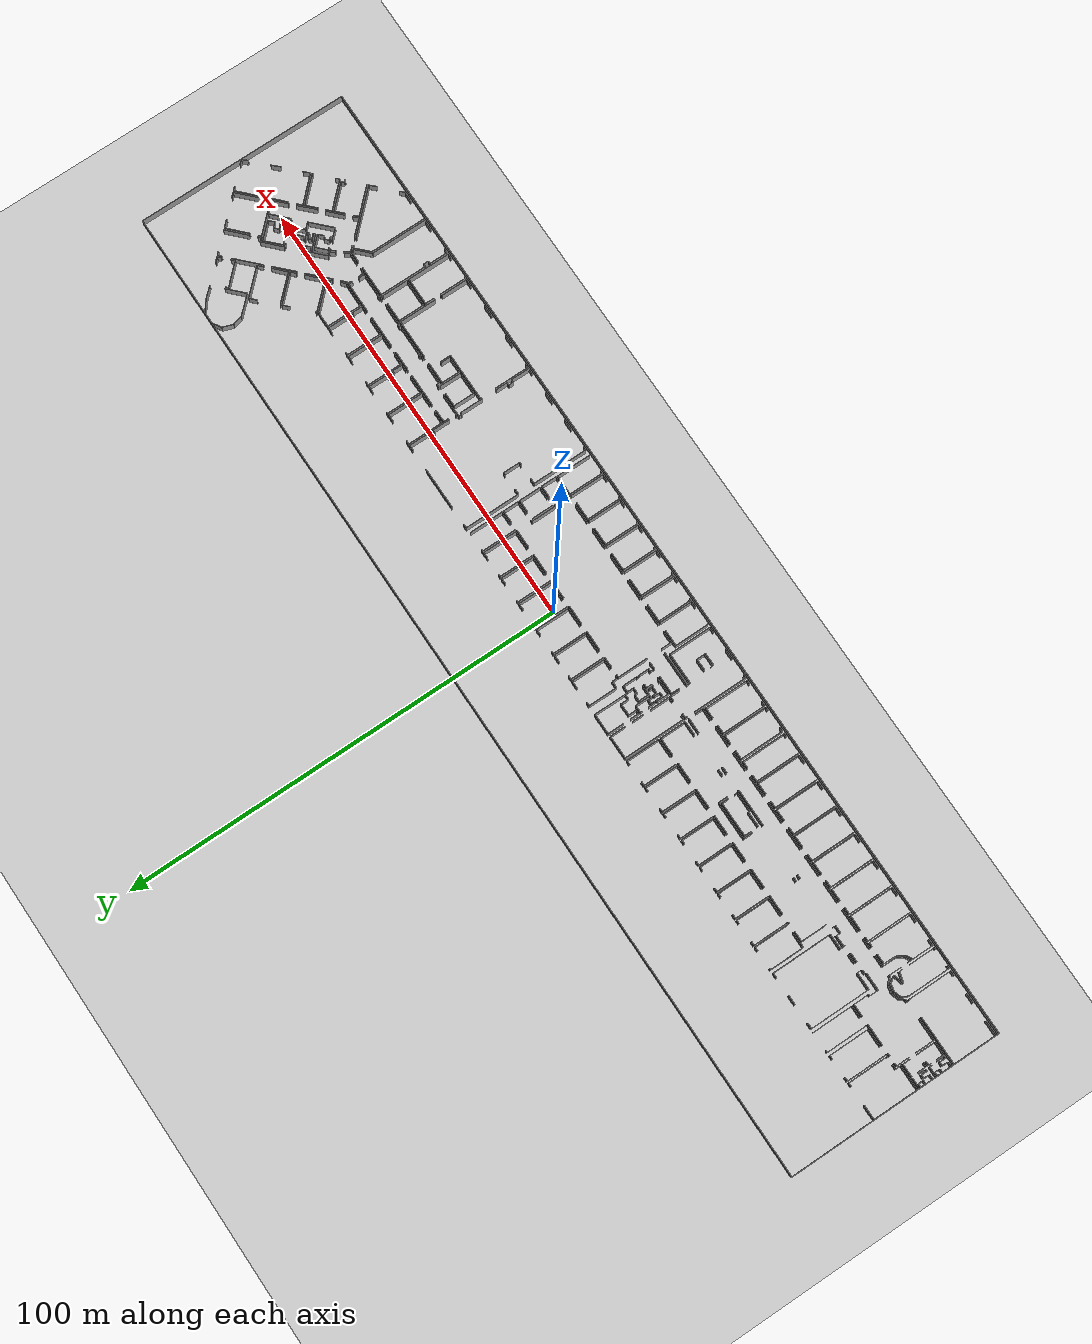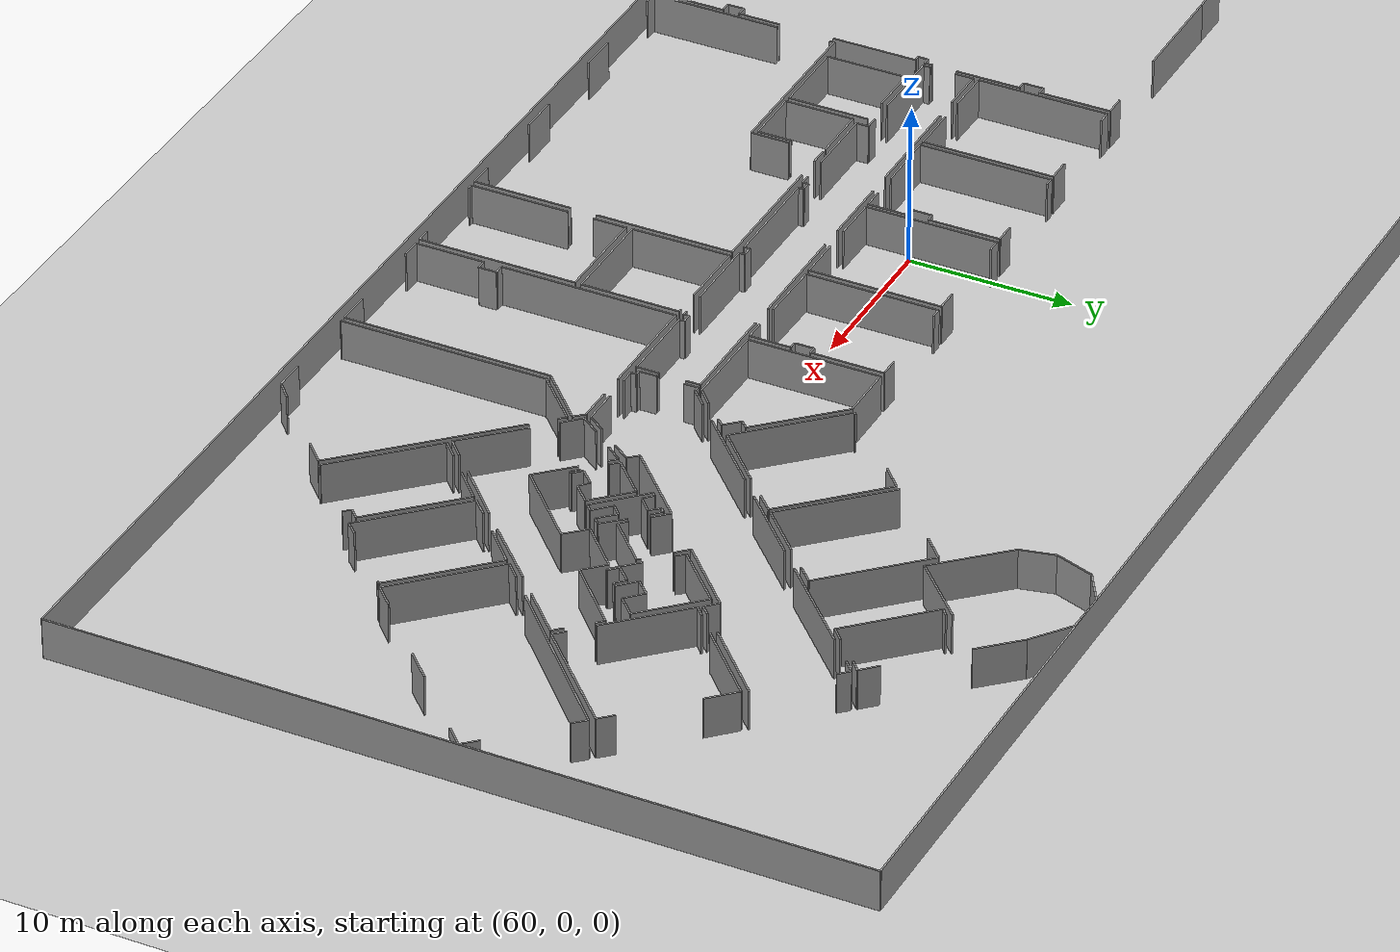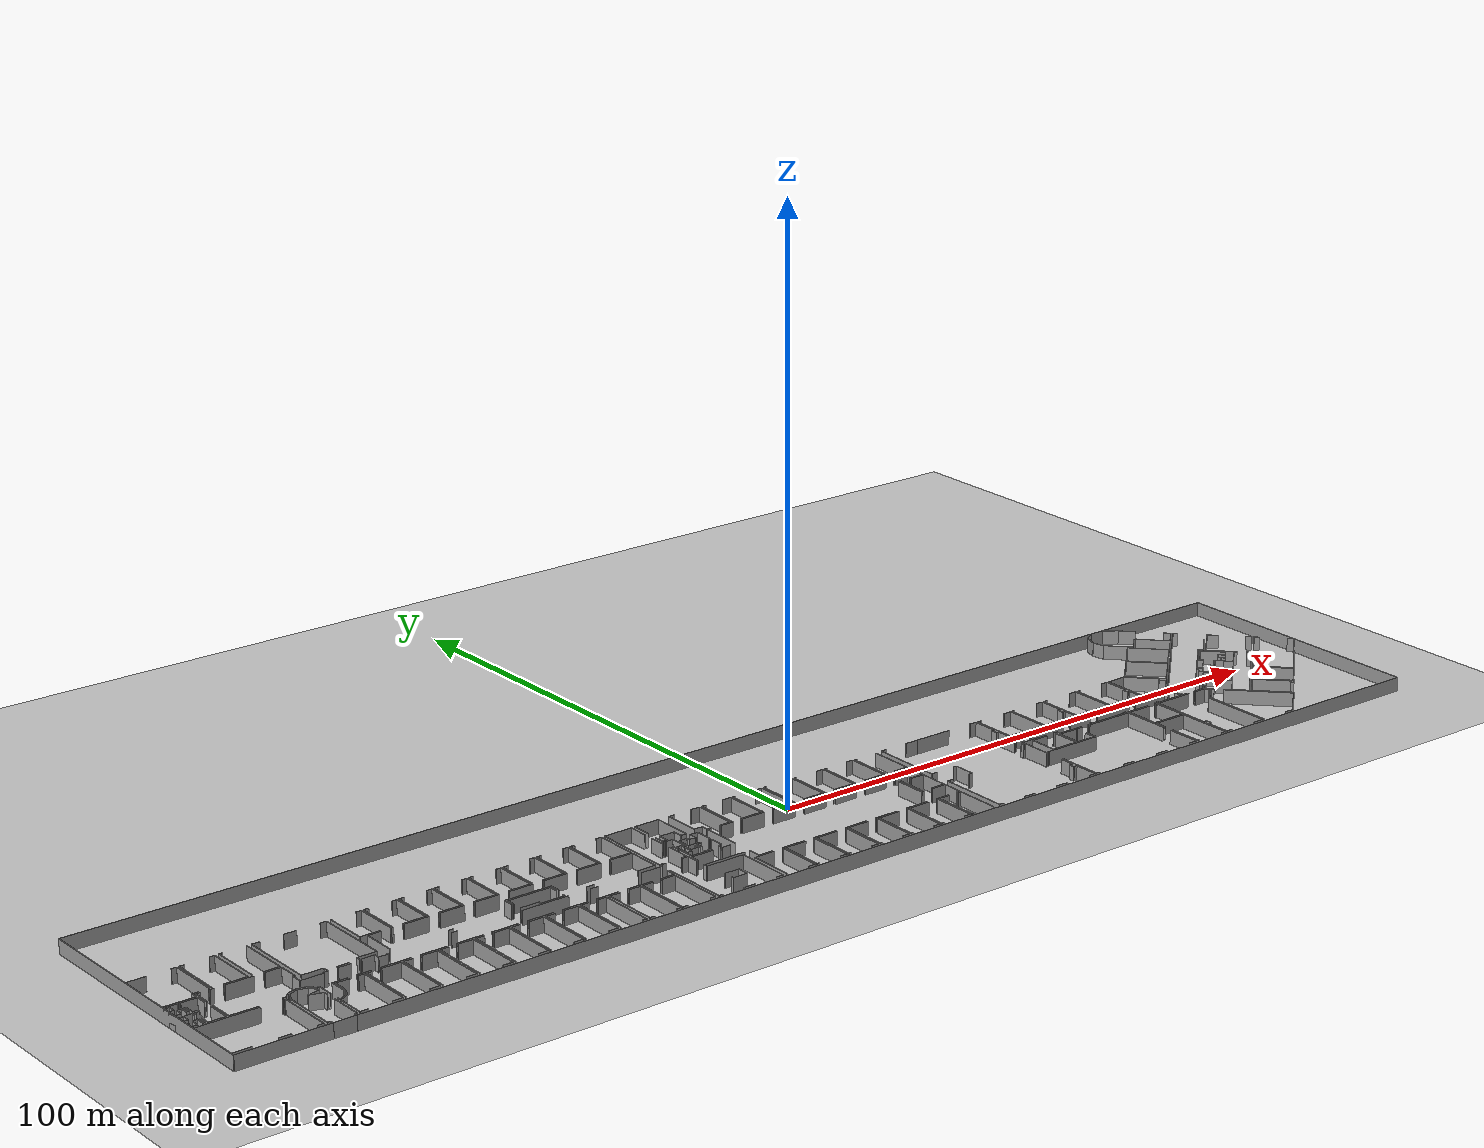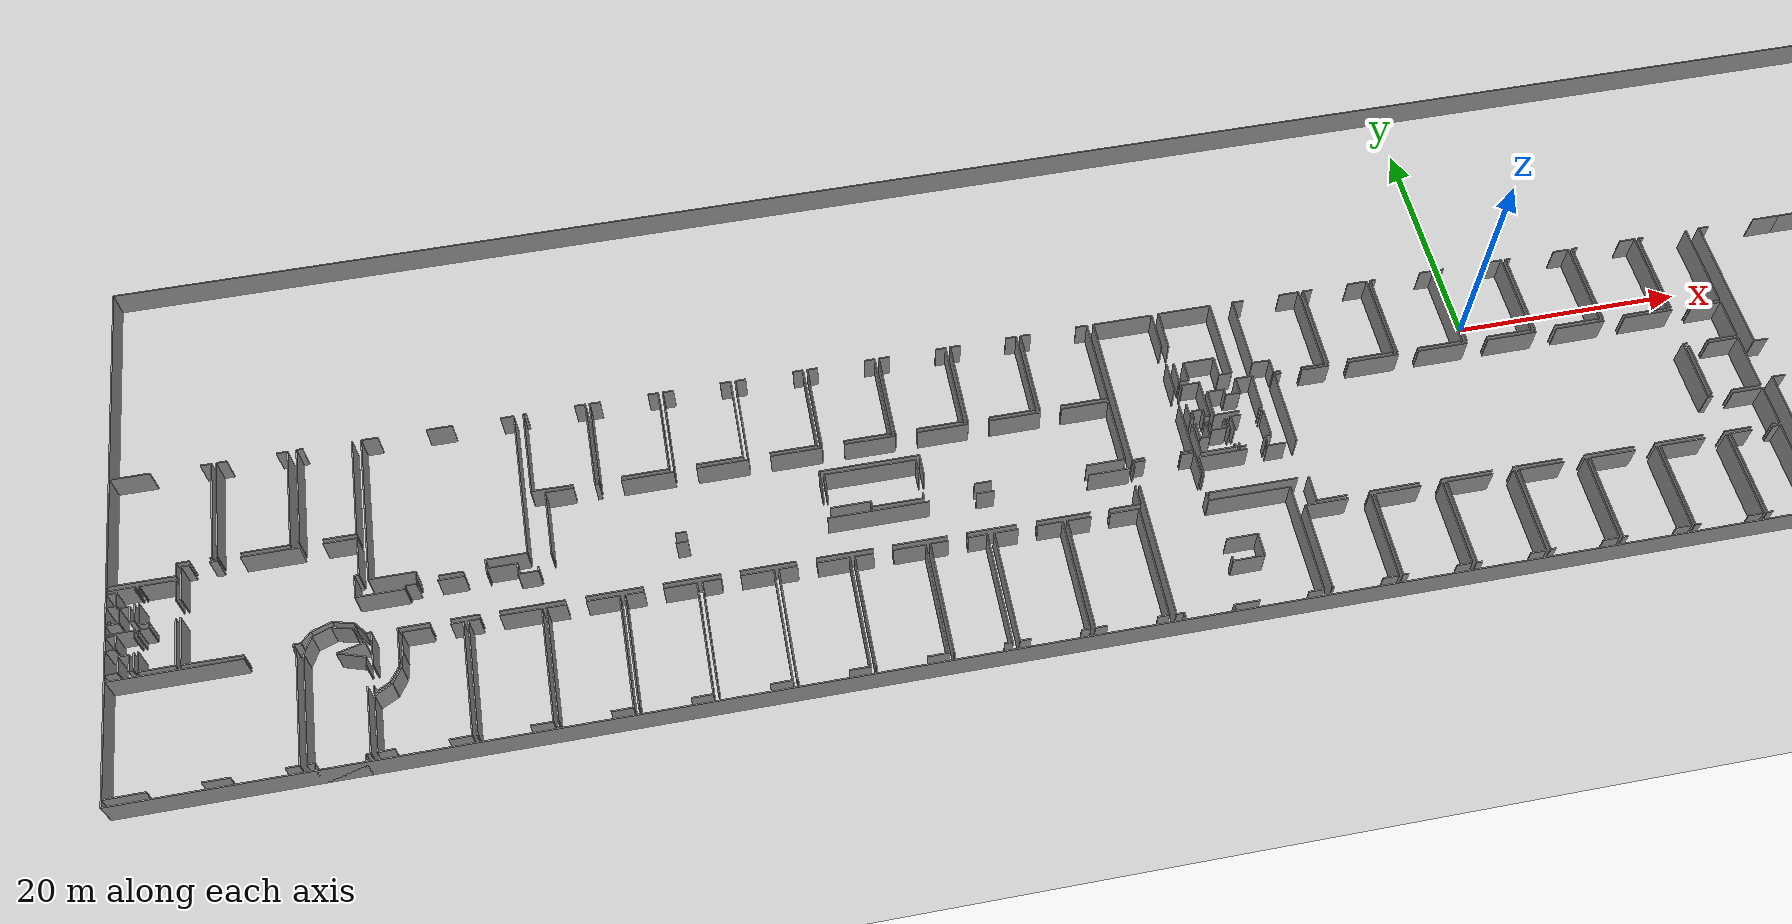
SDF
<sdf version="1.6">
  <world name="default">
    <light name="sun" type="directional">
      <cast_shadows>1</cast_shadows>
      <pose frame="">0 0 10 0 -0 0</pose>
      <diffuse>0.8 0.8 0.8 1</diffuse>
      <specular>0.1 0.1 0.1 1</specular>
      <attenuation>
        <range>1000</range>
        <constant>0.9</constant>
        <linear>0.01</linear>
        <quadratic>0.001</quadratic>
      </attenuation>
      <direction>-0.5 0.5 -1</direction>
    </light>
    <model name="ground_plane">
      <static>1</static>
      <link name="link">
        <collision name="collision">
          <geometry>
            <plane>
              <normal>0 0 1</normal>
              <size>100 100</size>
            </plane>
          </geometry>
          <surface>
            <friction>
              <ode>
                <mu>100</mu>
                <mu2>50</mu2>
              </ode>
              <torsional>
                <ode />
              </torsional>
            </friction>
            <contact>
              <ode />
            </contact>
            <bounce />
          </surface>
          <max_contacts>10</max_contacts>
        </collision>
        <visual name="visual">
          <cast_shadows>0</cast_shadows>
          <geometry>
            <plane>
              <normal>0 0 1</normal>
              <size>100 100</size>
            </plane>
          </geometry>
          <material>
            <script>
              <uri>file://media/materials/scripts/gazebo.material</uri>
              <name>Gazebo/Grey</name>
            </script>
          </material>
        </visual>
        <self_collide>0</self_collide>
        <kinematic>0</kinematic>
        <gravity>1</gravity>
      </link>
    </model>
    <gravity>0 0 -9.8</gravity>
    <magnetic_field>6e-06 2.3e-05 -4.2e-05</magnetic_field>
    <atmosphere type="adiabatic" />
    <physics default="0" name="default_physics" type="ode">
      <max_step_size>0.001</max_step_size>
      <real_time_factor>1</real_time_factor>
      <real_time_update_rate>1000</real_time_update_rate>
    </physics>
    <scene>
      <ambient>0.4 0.4 0.4 1</ambient>
      <background>0.7 0.7 0.7 1</background>
      <shadows>1</shadows>
    </scene>
    <spherical_coordinates>
      <surface_model>EARTH_WGS84</surface_model>
      <latitude_deg>0</latitude_deg>
      <longitude_deg>0</longitude_deg>
      <elevation>0</elevation>
      <heading_deg>0</heading_deg>
    </spherical_coordinates>
  <model name="0510035343_A_40_1_102">
		<static>1</static>
		<link name="Wall_0">
			<collision name="Wall_0_Collision">
				<geometry>
					<box>
						<size>10.2604335269 0.1 2.5</size>
					</box>
				</geometry>
				<pose frame="">5.13021676346 0 1.25 0 0 0</pose>
			</collision>
			<visual name="Wall_0_Visual">
				<pose frame="">5.13021676346 0 1.25 0 0 0</pose>
				<geometry>
					<box>
						<size>10.2604335269 0.1 2.5</size>
					</box>
				</geometry>
				<material>
					<script>
						<uri>file://media/materials/scripts/gazebo.material</uri>
						<name>Gazebo/Grey</name>
					</script>
					<ambient>1 1 1 1</ambient>
				</material>
			</visual>
			<pose frame="">0.0307213811927 -29.4750071408 0 0 0 1.57079632679</pose>
		</link>
		<link name="Wall_1">
			<collision name="Wall_1_Collision">
				<geometry>
					<box>
						<size>3.35243898569 0.1 2.5</size>
					</box>
				</geometry>
				<pose frame="">1.67621949284 0 1.25 0 0 0</pose>
			</collision>
			<visual name="Wall_1_Visual">
				<pose frame="">1.67621949284 0 1.25 0 0 0</pose>
				<geometry>
					<box>
						<size>3.35243898569 0.1 2.5</size>
					</box>
				</geometry>
				<material>
					<script>
						<uri>file://media/materials/scripts/gazebo.material</uri>
						<name>Gazebo/Grey</name>
					</script>
					<ambient>1 1 1 1</ambient>
				</material>
			</visual>
			<pose frame="">0.0307213811927 -19.2145736139 0 0 0 0.0</pose>
		</link>
		<link name="Wall_2">
			<collision name="Wall_2_Collision">
				<geometry>
					<box>
						<size>0.92164143578 0.1 2.5</size>
					</box>
				</geometry>
				<pose frame="">0.46082071789 0 1.25 0 0 0</pose>
			</collision>
			<visual name="Wall_2_Visual">
				<pose frame="">0.46082071789 0 1.25 0 0 0</pose>
				<geometry>
					<box>
						<size>0.92164143578 0.1 2.5</size>
					</box>
				</geometry>
				<material>
					<script>
						<uri>file://media/materials/scripts/gazebo.material</uri>
						<name>Gazebo/Grey</name>
					</script>
					<ambient>1 1 1 1</ambient>
				</material>
			</visual>
			<pose frame="">7.49804817671 -19.2145736139 0 0 0 0.0</pose>
		</link>
		<link name="Wall_3">
			<collision name="Wall_3_Collision">
				<geometry>
					<box>
						<size>9.08413469168 0.1 2.5</size>
					</box>
				</geometry>
				<pose frame="">4.54206734584 0 1.25 0 0 0</pose>
			</collision>
			<visual name="Wall_3_Visual">
				<pose frame="">4.54206734584 0 1.25 0 0 0</pose>
				<geometry>
					<box>
						<size>9.08413469168 0.1 2.5</size>
					</box>
				</geometry>
				<material>
					<script>
						<uri>file://media/materials/scripts/gazebo.material</uri>
						<name>Gazebo/Grey</name>
					</script>
					<ambient>1 1 1 1</ambient>
				</material>
			</visual>
			<pose frame="">8.41968961249 -19.2145736139 0 0 0 -1.57079632679</pose>
		</link>
		<link name="Wall_4">
			<collision name="Wall_4_Collision">
				<geometry>
					<box>
						<size>0.17061791869 0.1 2.5</size>
					</box>
				</geometry>
				<pose frame="">0.0853089593449 0 1.25 0 0 0</pose>
			</collision>
			<visual name="Wall_4_Visual">
				<pose frame="">0.0853089593449 0 1.25 0 0 0</pose>
				<geometry>
					<box>
						<size>0.17061791869 0.1 2.5</size>
					</box>
				</geometry>
				<material>
					<script>
						<uri>file://media/materials/scripts/gazebo.material</uri>
						<name>Gazebo/Grey</name>
					</script>
					<ambient>1 1 1 1</ambient>
				</material>
			</visual>
			<pose frame="">8.41968961249 -28.2987083056 0 0 0 3.14159265359</pose>
		</link>
		<link name="Wall_5">
			<collision name="Wall_5_Collision">
				<geometry>
					<box>
						<size>1.06915484465 0.1 2.5</size>
					</box>
				</geometry>
				<pose frame="">0.534577422324 0 1.25 0 0 0</pose>
			</collision>
			<visual name="Wall_5_Visual">
				<pose frame="">0.534577422324 0 1.25 0 0 0</pose>
				<geometry>
					<box>
						<size>1.06915484465 0.1 2.5</size>
					</box>
				</geometry>
				<material>
					<script>
						<uri>file://media/materials/scripts/gazebo.material</uri>
						<name>Gazebo/Grey</name>
					</script>
					<ambient>1 1 1 1</ambient>
				</material>
			</visual>
			<pose frame="">6.6210923863 -28.2987083056 0 0 0 3.14159265359</pose>
		</link>
		<link name="Wall_6">
			<collision name="Wall_6_Collision">
				<geometry>
					<box>
						<size>1.19280205656 0.1 2.5</size>
					</box>
				</geometry>
				<pose frame="">0.596401028278 0 1.25 0 0 0</pose>
			</collision>
			<visual name="Wall_6_Visual">
				<pose frame="">0.596401028278 0 1.25 0 0 0</pose>
				<geometry>
					<box>
						<size>1.19280205656 0.1 2.5</size>
					</box>
				</geometry>
				<material>
					<script>
						<uri>file://media/materials/scripts/gazebo.material</uri>
						<name>Gazebo/Grey</name>
					</script>
					<ambient>1 1 1 1</ambient>
				</material>
			</visual>
			<pose frame="">5.55193754165 -28.2987083056 0 0 0 -1.57079632679</pose>
		</link>
		<link name="Wall_7">
			<collision name="Wall_7_Collision">
				<geometry>
					<box>
						<size>5.52124082493 0.1 2.5</size>
					</box>
				</geometry>
				<pose frame="">2.76062041246 0 1.25 0 0 0</pose>
			</collision>
			<visual name="Wall_7_Visual">
				<pose frame="">2.76062041246 0 1.25 0 0 0</pose>
				<geometry>
					<box>
						<size>5.52124082493 0.1 2.5</size>
					</box>
				</geometry>
				<material>
					<script>
						<uri>file://media/materials/scripts/gazebo.material</uri>
						<name>Gazebo/Grey</name>
					</script>
					<ambient>1 1 1 1</ambient>
				</material>
			</visual>
			<pose frame="">5.55193754165 -29.4915103621 0 0 0 3.13860360703</pose>
		</link>
		<link name="Wall_8">
			<collision name="Wall_8_Collision">
				<geometry>
					<box>
						<size>4.25859278301 0.1 2.5</size>
					</box>
				</geometry>
				<pose frame="">2.12929639151 0 1.25 0 0 0</pose>
			</collision>
			<visual name="Wall_8_Visual">
				<pose frame="">2.12929639151 0 1.25 0 0 0</pose>
				<geometry>
					<box>
						<size>4.25859278301 0.1 2.5</size>
					</box>
				</geometry>
				<material>
					<script>
						<uri>file://media/materials/scripts/gazebo.material</uri>
						<name>Gazebo/Grey</name>
					</script>
					<ambient>1 1 1 1</ambient>
				</material>
			</visual>
			<pose frame="">5.92186359453 -37.6509568695 0 0 0 1.57079632679</pose>
		</link>
		<link name="Wall_9">
			<collision name="Wall_9_Collision">
				<geometry>
					<box>
						<size>3.01628106255 0.1 2.5</size>
					</box>
				</geometry>
				<pose frame="">1.50814053128 0 1.25 0 0 0</pose>
			</collision>
			<visual name="Wall_9_Visual">
				<pose frame="">1.50814053128 0 1.25 0 0 0</pose>
				<geometry>
					<box>
						<size>3.01628106255 0.1 2.5</size>
					</box>
				</geometry>
				<material>
					<script>
						<uri>file://media/materials/scripts/gazebo.material</uri>
						<name>Gazebo/Grey</name>
					</script>
					<ambient>1 1 1 1</ambient>
				</material>
			</visual>
			<pose frame="">5.92186359453 -31.6991335809 0 0 0 1.57079632679</pose>
		</link>
		<link name="Wall_10">
			<collision name="Wall_10_Collision">
				<geometry>
					<box>
						<size>0.680694404773 0.1 2.5</size>
					</box>
				</geometry>
				<pose frame="">0.340347202387 0 1.25 0 0 0</pose>
			</collision>
			<visual name="Wall_10_Visual">
				<pose frame="">0.340347202387 0 1.25 0 0 0</pose>
				<geometry>
					<box>
						<size>0.680694404773 0.1 2.5</size>
					</box>
				</geometry>
				<material>
					<script>
						<uri>file://media/materials/scripts/gazebo.material</uri>
						<name>Gazebo/Grey</name>
					</script>
					<ambient>1 1 1 1</ambient>
				</material>
			</visual>
			<pose frame="">5.92186359453 -28.6828525183 0 0 0 0.0</pose>
		</link>
		<link name="Wall_11">
			<collision name="Wall_11_Collision">
				<geometry>
					<box>
						<size>0.667999619156 0.1 2.5</size>
					</box>
				</geometry>
				<pose frame="">0.333999809578 0 1.25 0 0 0</pose>
			</collision>
			<visual name="Wall_11_Visual">
				<pose frame="">0.333999809578 0 1.25 0 0 0</pose>
				<geometry>
					<box>
						<size>0.667999619156 0.1 2.5</size>
					</box>
				</geometry>
				<material>
					<script>
						<uri>file://media/materials/scripts/gazebo.material</uri>
						<name>Gazebo/Grey</name>
					</script>
					<ambient>1 1 1 1</ambient>
				</material>
			</visual>
			<pose frame="">8.21378018979 -28.6828525183 0 0 0 0.0</pose>
		</link>
		<link name="Wall_12">
			<collision name="Wall_12_Collision">
				<geometry>
					<box>
						<size>4.78415690755 0.1 2.5</size>
					</box>
				</geometry>
				<pose frame="">2.39207845378 0 1.25 0 0 0</pose>
			</collision>
			<visual name="Wall_12_Visual">
				<pose frame="">2.39207845378 0 1.25 0 0 0</pose>
				<geometry>
					<box>
						<size>4.78415690755 0.1 2.5</size>
					</box>
				</geometry>
				<material>
					<script>
						<uri>file://media/materials/scripts/gazebo.material</uri>
						<name>Gazebo/Grey</name>
					</script>
					<ambient>1 1 1 1</ambient>
				</material>
			</visual>
			<pose frame="">10.6791075566 -28.6828525183 0 0 0 0.0</pose>
		</link>
		<link name="Wall_13">
			<collision name="Wall_13_Collision">
				<geometry>
					<box>
						<size>2.77127170015 0.1 2.5</size>
					</box>
				</geometry>
				<pose frame="">1.38563585007 0 1.25 0 0 0</pose>
			</collision>
			<visual name="Wall_13_Visual">
				<pose frame="">1.38563585007 0 1.25 0 0 0</pose>
				<geometry>
					<box>
						<size>2.77127170015 0.1 2.5</size>
					</box>
				</geometry>
				<material>
					<script>
						<uri>file://media/materials/scripts/gazebo.material</uri>
						<name>Gazebo/Grey</name>
					</script>
					<ambient>1 1 1 1</ambient>
				</material>
			</visual>
			<pose frame="">17.3469167539 -28.6828525183 0 0 0 0.0</pose>
		</link>
		<link name="Wall_14">
			<collision name="Wall_14_Collision">
				<geometry>
					<box>
						<size>3.48776540036 0.1 2.5</size>
					</box>
				</geometry>
				<pose frame="">1.74388270018 0 1.25 0 0 0</pose>
			</collision>
			<visual name="Wall_14_Visual">
				<pose frame="">1.74388270018 0 1.25 0 0 0</pose>
				<geometry>
					<box>
						<size>3.48776540036 0.1 2.5</size>
					</box>
				</geometry>
				<material>
					<script>
						<uri>file://media/materials/scripts/gazebo.material</uri>
						<name>Gazebo/Grey</name>
					</script>
					<ambient>1 1 1 1</ambient>
				</material>
			</visual>
			<pose frame="">20.1181884541 -28.6828525183 0 0 0 -1.57079632679</pose>
		</link>
		<link name="Wall_15">
			<collision name="Wall_15_Collision">
				<geometry>
					<box>
						<size>0.367133200038 0.1 2.5</size>
					</box>
				</geometry>
				<pose frame="">0.183566600019 0 1.25 0 0 0</pose>
			</collision>
			<visual name="Wall_15_Visual">
				<pose frame="">0.183566600019 0 1.25 0 0 0</pose>
				<geometry>
					<box>
						<size>0.367133200038 0.1 2.5</size>
					</box>
				</geometry>
				<material>
					<script>
						<uri>file://media/materials/scripts/gazebo.material</uri>
						<name>Gazebo/Grey</name>
					</script>
					<ambient>1 1 1 1</ambient>
				</material>
			</visual>
			<pose frame="">20.1181884541 -32.1706179187 0 0 0 3.14159265359</pose>
		</link>
		<link name="Wall_16">
			<collision name="Wall_16_Collision">
				<geometry>
					<box>
						<size>1.98673394903 0.1 2.5</size>
					</box>
				</geometry>
				<pose frame="">0.993366974515 0 1.25 0 0 0</pose>
			</collision>
			<visual name="Wall_16_Visual">
				<pose frame="">0.993366974515 0 1.25 0 0 0</pose>
				<geometry>
					<box>
						<size>1.98673394903 0.1 2.5</size>
					</box>
				</geometry>
				<material>
					<script>
						<uri>file://media/materials/scripts/gazebo.material</uri>
						<name>Gazebo/Grey</name>
					</script>
					<ambient>1 1 1 1</ambient>
				</material>
			</visual>
			<pose frame="">19.7510552541 -32.1706179187 0 0 0 -1.57079632679</pose>
		</link>
		<link name="Wall_17">
			<collision name="Wall_17_Collision">
				<geometry>
					<box>
						<size>4.00571265353 0.1 2.5</size>
					</box>
				</geometry>
				<pose frame="">2.00285632676 0 1.25 0 0 0</pose>
			</collision>
			<visual name="Wall_17_Visual">
				<pose frame="">2.00285632676 0 1.25 0 0 0</pose>
				<geometry>
					<box>
						<size>4.00571265353 0.1 2.5</size>
					</box>
				</geometry>
				<material>
					<script>
						<uri>file://media/materials/scripts/gazebo.material</uri>
						<name>Gazebo/Grey</name>
					</script>
					<ambient>1 1 1 1</ambient>
				</material>
			</visual>
			<pose frame="">19.7510552541 -34.1573518677 0 0 0 0.0</pose>
		</link>
		<link name="Wall_18">
			<collision name="Wall_18_Collision">
				<geometry>
					<box>
						<size>0.300104731981 0.1 2.5</size>
					</box>
				</geometry>
				<pose frame="">0.150052365991 0 1.25 0 0 0</pose>
			</collision>
			<visual name="Wall_18_Visual">
				<pose frame="">0.150052365991 0 1.25 0 0 0</pose>
				<geometry>
					<box>
						<size>0.300104731981 0.1 2.5</size>
					</box>
				</geometry>
				<material>
					<script>
						<uri>file://media/materials/scripts/gazebo.material</uri>
						<name>Gazebo/Grey</name>
					</script>
					<ambient>1 1 1 1</ambient>
				</material>
			</visual>
			<pose frame="">23.7567679076 -34.1573518677 0 0 0 1.57079632679</pose>
		</link>
		<link name="Wall_19">
			<collision name="Wall_19_Collision">
				<geometry>
					<box>
						<size>0.934082325685 0.1 2.5</size>
					</box>
				</geometry>
				<pose frame="">0.467041162842 0 1.25 0 0 0</pose>
			</collision>
			<visual name="Wall_19_Visual">
				<pose frame="">0.467041162842 0 1.25 0 0 0</pose>
				<geometry>
					<box>
						<size>0.934082325685 0.1 2.5</size>
					</box>
				</geometry>
				<material>
					<script>
						<uri>file://media/materials/scripts/gazebo.material</uri>
						<name>Gazebo/Grey</name>
					</script>
					<ambient>1 1 1 1</ambient>
				</material>
			</visual>
			<pose frame="">23.7567679076 -33.8572471357 0 0 0 0.0</pose>
		</link>
		<link name="Wall_20">
			<collision name="Wall_20_Collision">
				<geometry>
					<box>
						<size>2.16242978197 0.1 2.5</size>
					</box>
				</geometry>
				<pose frame="">1.08121489098 0 1.25 0 0 0</pose>
			</collision>
			<visual name="Wall_20_Visual">
				<pose frame="">1.08121489098 0 1.25 0 0 0</pose>
				<geometry>
					<box>
						<size>2.16242978197 0.1 2.5</size>
					</box>
				</geometry>
				<material>
					<script>
						<uri>file://media/materials/scripts/gazebo.material</uri>
						<name>Gazebo/Grey</name>
					</script>
					<ambient>1 1 1 1</ambient>
				</material>
			</visual>
			<pose frame="">26.3932209845 -33.8572471357 0 0 0 0.0</pose>
		</link>
		<link name="Wall_21">
			<collision name="Wall_21_Collision">
				<geometry>
					<box>
						<size>0.365863721476 0.1 2.5</size>
					</box>
				</geometry>
				<pose frame="">0.182931860738 0 1.25 0 0 0</pose>
			</collision>
			<visual name="Wall_21_Visual">
				<pose frame="">0.182931860738 0 1.25 0 0 0</pose>
				<geometry>
					<box>
						<size>0.365863721476 0.1 2.5</size>
					</box>
				</geometry>
				<material>
					<script>
						<uri>file://media/materials/scripts/gazebo.material</uri>
						<name>Gazebo/Grey</name>
					</script>
					<ambient>1 1 1 1</ambient>
				</material>
			</visual>
			<pose frame="">30.3458694341 -33.8572471357 0 0 0 1.57079632679</pose>
		</link>
		<link name="Wall_22">
			<collision name="Wall_22_Collision">
				<geometry>
					<box>
						<size>2.49960328795 0.1 2.5</size>
					</box>
				</geometry>
				<pose frame="">1.24980164397 0 1.25 0 0 0</pose>
			</collision>
			<visual name="Wall_22_Visual">
				<pose frame="">1.24980164397 0 1.25 0 0 0</pose>
				<geometry>
					<box>
						<size>2.49960328795 0.1 2.5</size>
					</box>
				</geometry>
				<material>
					<script>
						<uri>file://media/materials/scripts/gazebo.material</uri>
						<name>Gazebo/Grey</name>
					</script>
					<ambient>1 1 1 1</ambient>
				</material>
			</visual>
			<pose frame="">30.3458694341 -33.4913834143 0 0 0 0.0</pose>
		</link>
		<link name="Wall_23">
			<collision name="Wall_23_Collision">
				<geometry>
					<box>
						<size>1.00974324796 0.1 2.5</size>
					</box>
				</geometry>
				<pose frame="">0.50487162398 0 1.25 0 0 0</pose>
			</collision>
			<visual name="Wall_23_Visual">
				<pose frame="">0.50487162398 0 1.25 0 0 0</pose>
				<geometry>
					<box>
						<size>1.00974324796 0.1 2.5</size>
					</box>
				</geometry>
				<material>
					<script>
						<uri>file://media/materials/scripts/gazebo.material</uri>
						<name>Gazebo/Grey</name>
					</script>
					<ambient>1 1 1 1</ambient>
				</material>
			</visual>
			<pose frame="">32.8454727221 -33.4913834143 0 0 0 -1.57079632679</pose>
		</link>
		<link name="Wall_24">
			<collision name="Wall_24_Collision">
				<geometry>
					<box>
						<size>1.65362277445 0.1 2.5</size>
					</box>
				</geometry>
				<pose frame="">0.826811387223 0 1.25 0 0 0</pose>
			</collision>
			<visual name="Wall_24_Visual">
				<pose frame="">0.826811387223 0 1.25 0 0 0</pose>
				<geometry>
					<box>
						<size>1.65362277445 0.1 2.5</size>
					</box>
				</geometry>
				<material>
					<script>
						<uri>file://media/materials/scripts/gazebo.material</uri>
						<name>Gazebo/Grey</name>
					</script>
					<ambient>1 1 1 1</ambient>
				</material>
			</visual>
			<pose frame="">32.8454727221 -34.5011266622 0 0 0 0.0</pose>
		</link>
		<link name="Wall_25">
			<collision name="Wall_25_Collision">
				<geometry>
					<box>
						<size>0.434923355232 0.1 2.5</size>
					</box>
				</geometry>
				<pose frame="">0.217461677616 0 1.25 0 0 0</pose>
			</collision>
			<visual name="Wall_25_Visual">
				<pose frame="">0.217461677616 0 1.25 0 0 0</pose>
				<geometry>
					<box>
						<size>0.434923355232 0.1 2.5</size>
					</box>
				</geometry>
				<material>
					<script>
						<uri>file://media/materials/scripts/gazebo.material</uri>
						<name>Gazebo/Grey</name>
					</script>
					<ambient>1 1 1 1</ambient>
				</material>
			</visual>
			<pose frame="">34.4990954965 -34.5011266622 0 0 0 1.57079632679</pose>
		</link>
		<link name="Wall_26">
			<collision name="Wall_26_Collision">
				<geometry>
					<box>
						<size>1.01177441366 0.1 2.5</size>
					</box>
				</geometry>
				<pose frame="">0.50588720683 0 1.25 0 0 0</pose>
			</collision>
			<visual name="Wall_26_Visual">
				<pose frame="">0.50588720683 0 1.25 0 0 0</pose>
				<geometry>
					<box>
						<size>1.01177441366 0.1 2.5</size>
					</box>
				</geometry>
				<material>
					<script>
						<uri>file://media/materials/scripts/gazebo.material</uri>
						<name>Gazebo/Grey</name>
					</script>
					<ambient>1 1 1 1</ambient>
				</material>
			</visual>
			<pose frame="">45.7740962899 -34.066203307 0 0 0 0.0</pose>
		</link>
		<link name="Wall_27">
			<collision name="Wall_27_Collision">
				<geometry>
					<box>
						<size>8.5288647688 0.1 2.5</size>
					</box>
				</geometry>
				<pose frame="">4.2644323844 0 1.25 0 0 0</pose>
			</collision>
			<visual name="Wall_27_Visual">
				<pose frame="">4.2644323844 0 1.25 0 0 0</pose>
				<geometry>
					<box>
						<size>8.5288647688 0.1 2.5</size>
					</box>
				</geometry>
				<material>
					<script>
						<uri>file://media/materials/scripts/gazebo.material</uri>
						<name>Gazebo/Grey</name>
					</script>
					<ambient>1 1 1 1</ambient>
				</material>
			</visual>
			<pose frame="">58.368085309 -34.066203307 0 0 0 0.0</pose>
		</link>
		<link name="Wall_28">
			<collision name="Wall_28_Collision">
				<geometry>
					<box>
						<size>1.5147418198 0.1 2.5</size>
					</box>
				</geometry>
				<pose frame="">0.757370909899 0 1.25 0 0 0</pose>
			</collision>
			<visual name="Wall_28_Visual">
				<pose frame="">0.757370909899 0 1.25 0 0 0</pose>
				<geometry>
					<box>
						<size>1.5147418198 0.1 2.5</size>
					</box>
				</geometry>
				<material>
					<script>
						<uri>file://media/materials/scripts/gazebo.material</uri>
						<name>Gazebo/Grey</name>
					</script>
					<ambient>1 1 1 1</ambient>
				</material>
			</visual>
			<pose frame="">70.9034244184 -34.066203307 0 0 0 0.0</pose>
		</link>
		<link name="Wall_29">
			<collision name="Wall_29_Collision">
				<geometry>
					<box>
						<size>3.57256656828 0.1 2.5</size>
					</box>
				</geometry>
				<pose frame="">1.78628328414 0 1.25 0 0 0</pose>
			</collision>
			<visual name="Wall_29_Visual">
				<pose frame="">1.78628328414 0 1.25 0 0 0</pose>
				<geometry>
					<box>
						<size>3.57256656828 0.1 2.5</size>
					</box>
				</geometry>
				<material>
					<script>
						<uri>file://media/materials/scripts/gazebo.material</uri>
						<name>Gazebo/Grey</name>
					</script>
					<ambient>1 1 1 1</ambient>
				</material>
			</visual>
			<pose frame="">80.4839252277 -34.066203307 0 0 0 0.0</pose>
		</link>
		<link name="Wall_30">
			<collision name="Wall_30_Collision">
				<geometry>
					<box>
						<size>1.75467326796 0.1 2.5</size>
					</box>
				</geometry>
				<pose frame="">0.877336633978 0 1.25 0 0 0</pose>
			</collision>
			<visual name="Wall_30_Visual">
				<pose frame="">0.877336633978 0 1.25 0 0 0</pose>
				<geometry>
					<box>
						<size>1.75467326796 0.1 2.5</size>
					</box>
				</geometry>
				<material>
					<script>
						<uri>file://media/materials/scripts/gazebo.material</uri>
						<name>Gazebo/Grey</name>
					</script>
					<ambient>1 1 1 1</ambient>
				</material>
			</visual>
			<pose frame="">84.056491796 -35.8391570662 0 0 0 -1.57079632679</pose>
		</link>
		<link name="Wall_31">
			<collision name="Wall_31_Collision">
				<geometry>
					<box>
						<size>2.65016344536 0.1 2.5</size>
					</box>
				</geometry>
				<pose frame="">1.32508172268 0 1.25 0 0 0</pose>
			</collision>
			<visual name="Wall_31_Visual">
				<pose frame="">1.32508172268 0 1.25 0 0 0</pose>
				<geometry>
					<box>
						<size>2.65016344536 0.1 2.5</size>
					</box>
				</geometry>
				<material>
					<script>
						<uri>file://media/materials/scripts/gazebo.material</uri>
						<name>Gazebo/Grey</name>
					</script>
					<ambient>1 1 1 1</ambient>
				</material>
			</visual>
			<pose frame="">84.056491796 -37.5938303342 0 0 0 3.14159265359</pose>
		</link>
		<link name="Wall_32">
			<collision name="Wall_32_Collision">
				<geometry>
					<box>
						<size>4.52416769812 0.1 2.5</size>
					</box>
				</geometry>
				<pose frame="">2.26208384906 0 1.25 0 0 0</pose>
			</collision>
			<visual name="Wall_32_Visual">
				<pose frame="">2.26208384906 0 1.25 0 0 0</pose>
				<geometry>
					<box>
						<size>4.52416769812 0.1 2.5</size>
					</box>
				</geometry>
				<material>
					<script>
						<uri>file://media/materials/scripts/gazebo.material</uri>
						<name>Gazebo/Grey</name>
					</script>
					<ambient>1 1 1 1</ambient>
				</material>
			</visual>
			<pose frame="">79.7661620489 -37.5938303342 0 0 0 3.14159265359</pose>
		</link>
		<link name="Wall_33">
			<collision name="Wall_33_Collision">
				<geometry>
					<box>
						<size>4.1636357866 0.1 2.5</size>
					</box>
				</geometry>
				<pose frame="">2.0818178933 0 1.25 0 0 0</pose>
			</collision>
			<visual name="Wall_33_Visual">
				<pose frame="">2.0818178933 0 1.25 0 0 0</pose>
				<geometry>
					<box>
						<size>4.1636357866 0.1 2.5</size>
					</box>
				</geometry>
				<material>
					<script>
						<uri>file://media/materials/scripts/gazebo.material</uri>
						<name>Gazebo/Grey</name>
					</script>
					<ambient>1 1 1 1</ambient>
				</material>
			</visual>
			<pose frame="">73.5530800724 -37.5938303342 0 0 0 3.14159265359</pose>
		</link>
		<link name="Wall_34">
			<collision name="Wall_34_Collision">
				<geometry>
					<box>
						<size>4.56656828208 0.1 2.5</size>
					</box>
				</geometry>
				<pose frame="">2.28328414104 0 1.25 0 0 0</pose>
			</collision>
			<visual name="Wall_34_Visual">
				<pose frame="">2.28328414104 0 1.25 0 0 0</pose>
				<geometry>
					<box>
						<size>4.56656828208 0.1 2.5</size>
					</box>
				</geometry>
				<material>
					<script>
						<uri>file://media/materials/scripts/gazebo.material</uri>
						<name>Gazebo/Grey</name>
					</script>
					<ambient>1 1 1 1</ambient>
				</material>
			</visual>
			<pose frame="">67.7439461741 -37.5938303342 0 0 0 3.14159265359</pose>
		</link>
		<link name="Wall_35">
			<collision name="Wall_35_Collision">
				<geometry>
					<box>
						<size>4.73439334793 0.1 2.5</size>
					</box>
				</geometry>
				<pose frame="">2.36719667397 0 1.25 0 0 0</pose>
			</collision>
			<visual name="Wall_35_Visual">
				<pose frame="">2.36719667397 0 1.25 0 0 0</pose>
				<geometry>
					<box>
						<size>4.73439334793 0.1 2.5</size>
					</box>
				</geometry>
				<material>
					<script>
						<uri>file://media/materials/scripts/gazebo.material</uri>
						<name>Gazebo/Grey</name>
					</script>
					<ambient>1 1 1 1</ambient>
				</material>
			</visual>
			<pose frame="">61.5656479101 -37.5938303342 0 0 0 3.14159265359</pose>
		</link>
		<link name="Wall_36">
			<collision name="Wall_36_Collision">
				<geometry>
					<box>
						<size>4.66736487988 0.1 2.5</size>
					</box>
				</geometry>
				<pose frame="">2.33368243994 0 1.25 0 0 0</pose>
			</collision>
			<visual name="Wall_36_Visual">
				<pose frame="">2.33368243994 0 1.25 0 0 0</pose>
				<geometry>
					<box>
						<size>4.66736487988 0.1 2.5</size>
					</box>
				</geometry>
				<material>
					<script>
						<uri>file://media/materials/scripts/gazebo.material</uri>
						<name>Gazebo/Grey</name>
					</script>
					<ambient>1 1 1 1</ambient>
				</material>
			</visual>
			<pose frame="">55.2195245803 -37.5938303342 0 0 0 3.14159265359</pose>
		</link>
		<link name="Wall_37">
			<collision name="Wall_37_Collision">
				<geometry>
					<box>
						<size>4.73439334793 0.1 2.5</size>
					</box>
				</geometry>
				<pose frame="">2.36719667397 0 1.25 0 0 0</pose>
			</collision>
			<visual name="Wall_37_Visual">
				<pose frame="">2.36719667397 0 1.25 0 0 0</pose>
				<geometry>
					<box>
						<size>4.73439334793 0.1 2.5</size>
					</box>
				</geometry>
				<material>
					<script>
						<uri>file://media/materials/scripts/gazebo.material</uri>
						<name>Gazebo/Grey</name>
					</script>
					<ambient>1 1 1 1</ambient>
				</material>
			</visual>
			<pose frame="">49.0077120823 -37.5938303342 0 0 0 3.14159265359</pose>
		</link>
		<link name="Wall_38">
			<collision name="Wall_38_Collision">
				<geometry>
					<box>
						<size>4.67168110699 0.1 2.5</size>
					</box>
				</geometry>
				<pose frame="">2.33584055349 0 1.25 0 0 0</pose>
			</collision>
			<visual name="Wall_38_Visual">
				<pose frame="">2.33584055349 0 1.25 0 0 0</pose>
				<geometry>
					<box>
						<size>4.67168110699 0.1 2.5</size>
					</box>
				</geometry>
				<material>
					<script>
						<uri>file://media/materials/scripts/gazebo.material</uri>
						<name>Gazebo/Grey</name>
					</script>
					<ambient>1 1 1 1</ambient>
				</material>
			</visual>
			<pose frame="">42.6775841823 -37.5938303342 0 0 0 3.14159265359</pose>
		</link>
		<link name="Wall_39">
			<collision name="Wall_39_Collision">
				<geometry>
					<box>
						<size>5.33180995906 0.1 2.5</size>
					</box>
				</geometry>
				<pose frame="">2.66590497953 0 1.25 0 0 0</pose>
			</collision>
			<visual name="Wall_39_Visual">
				<pose frame="">2.66590497953 0 1.25 0 0 0</pose>
				<geometry>
					<box>
						<size>5.33180995906 0.1 2.5</size>
					</box>
				</geometry>
				<material>
					<script>
						<uri>file://media/materials/scripts/gazebo.material</uri>
						<name>Gazebo/Grey</name>
					</script>
					<ambient>1 1 1 1</ambient>
				</material>
			</visual>
			<pose frame="">36.3885873877 -37.5938303342 0 0 0 3.14159265359</pose>
		</link>
		<link name="Wall_40">
			<collision name="Wall_40_Collision">
				<geometry>
					<box>
						<size>2.36224570758 0.1 2.5</size>
					</box>
				</geometry>
				<pose frame="">1.18112285379 0 1.25 0 0 0</pose>
			</collision>
			<visual name="Wall_40_Visual">
				<pose frame="">1.18112285379 0 1.25 0 0 0</pose>
				<geometry>
					<box>
						<size>2.36224570758 0.1 2.5</size>
					</box>
				</geometry>
				<material>
					<script>
						<uri>file://media/materials/scripts/gazebo.material</uri>
						<name>Gazebo/Grey</name>
					</script>
					<ambient>1 1 1 1</ambient>
				</material>
			</visual>
			<pose frame="">29.4991272335 -37.5938303342 0 0 0 3.14159265359</pose>
		</link>
		<link name="Wall_41">
			<collision name="Wall_41_Collision">
				<geometry>
					<box>
						<size>2.56891681742 0.1 2.5</size>
					</box>
				</geometry>
				<pose frame="">1.28445840871 0 1.25 0 0 0</pose>
			</collision>
			<visual name="Wall_41_Visual">
				<pose frame="">1.28445840871 0 1.25 0 0 0</pose>
				<geometry>
					<box>
						<size>2.56891681742 0.1 2.5</size>
					</box>
				</geometry>
				<material>
					<script>
						<uri>file://media/materials/scripts/gazebo.material</uri>
						<name>Gazebo/Grey</name>
					</script>
					<ambient>1 1 1 1</ambient>
				</material>
			</visual>
			<pose frame="">25.525151544 -37.5938303342 0 0 0 3.14159265359</pose>
		</link>
		<link name="Wall_42">
			<collision name="Wall_42_Collision">
				<geometry>
					<box>
						<size>2.96626360722 0.1 2.5</size>
					</box>
				</geometry>
				<pose frame="">1.48313180361 0 1.25 0 0 0</pose>
			</collision>
			<visual name="Wall_42_Visual">
				<pose frame="">1.48313180361 0 1.25 0 0 0</pose>
				<geometry>
					<box>
						<size>2.96626360722 0.1 2.5</size>
					</box>
				</geometry>
				<material>
					<script>
						<uri>file://media/materials/scripts/gazebo.material</uri>
						<name>Gazebo/Grey</name>
					</script>
					<ambient>1 1 1 1</ambient>
				</material>
			</visual>
			<pose frame="">22.9562347266 -37.5938303342 0 0 0 -1.57079632679</pose>
		</link>
		<link name="Wall_43">
			<collision name="Wall_43_Collision">
				<geometry>
					<box>
						<size>0.563709836177 0.1 2.5</size>
					</box>
				</geometry>
				<pose frame="">0.281854918089 0 1.25 0 0 0</pose>
			</collision>
			<visual name="Wall_43_Visual">
				<pose frame="">0.281854918089 0 1.25 0 0 0</pose>
				<geometry>
					<box>
						<size>0.563709836177 0.1 2.5</size>
					</box>
				</geometry>
				<material>
					<script>
						<uri>file://media/materials/scripts/gazebo.material</uri>
						<name>Gazebo/Grey</name>
					</script>
					<ambient>1 1 1 1</ambient>
				</material>
			</visual>
			<pose frame="">22.9562347266 -40.5600939414 0 0 0 -1.74142440143</pose>
		</link>
		<link name="Wall_44">
			<collision name="Wall_44_Collision">
				<geometry>
					<box>
						<size>1.35169558649 0.1 2.5</size>
					</box>
				</geometry>
				<pose frame="">0.675847793244 0 1.25 0 0 0</pose>
			</collision>
			<visual name="Wall_44_Visual">
				<pose frame="">0.675847793244 0 1.25 0 0 0</pose>
				<geometry>
					<box>
						<size>1.35169558649 0.1 2.5</size>
					</box>
				</geometry>
				<material>
					<script>
						<uri>file://media/materials/scripts/gazebo.material</uri>
						<name>Gazebo/Grey</name>
					</script>
					<ambient>1 1 1 1</ambient>
				</material>
			</visual>
			<pose frame="">22.860516043 -41.11561776 0 0 0 -2.1432736838</pose>
		</link>
		<link name="Wall_45">
			<collision name="Wall_45_Collision">
				<geometry>
					<box>
						<size>1.43572895688 0.1 2.5</size>
					</box>
				</geometry>
				<pose frame="">0.71786447844 0 1.25 0 0 0</pose>
			</collision>
			<visual name="Wall_45_Visual">
				<pose frame="">0.71786447844 0 1.25 0 0 0</pose>
				<geometry>
					<box>
						<size>1.43572895688 0.1 2.5</size>
					</box>
				</geometry>
				<material>
					<script>
						<uri>file://media/materials/scripts/gazebo.material</uri>
						<name>Gazebo/Grey</name>
					</script>
					<ambient>1 1 1 1</ambient>
				</material>
			</visual>
			<pose frame="">22.1282808087 -42.2518010727 0 0 0 -2.62683343816</pose>
		</link>
		<link name="Wall_46">
			<collision name="Wall_46_Collision">
				<geometry>
					<box>
						<size>0.643879526484 0.1 2.5</size>
					</box>
				</geometry>
				<pose frame="">0.321939763242 0 1.25 0 0 0</pose>
			</collision>
			<visual name="Wall_46_Visual">
				<pose frame="">0.321939763242 0 1.25 0 0 0</pose>
				<geometry>
					<box>
						<size>0.643879526484 0.1 2.5</size>
					</box>
				</geometry>
				<material>
					<script>
						<uri>file://media/materials/scripts/gazebo.material</uri>
						<name>Gazebo/Grey</name>
					</script>
					<ambient>1 1 1 1</ambient>
				</material>
			</visual>
			<pose frame="">20.8786061125 -42.9586467359 0 0 0 1.57079632679</pose>
		</link>
		<link name="Wall_47">
			<collision name="Wall_47_Collision">
				<geometry>
					<box>
						<size>2.92843314609 0.1 2.5</size>
					</box>
				</geometry>
				<pose frame="">1.46421657304 0 1.25 0 0 0</pose>
			</collision>
			<visual name="Wall_47_Visual">
				<pose frame="">1.46421657304 0 1.25 0 0 0</pose>
				<geometry>
					<box>
						<size>2.92843314609 0.1 2.5</size>
					</box>
				</geometry>
				<material>
					<script>
						<uri>file://media/materials/scripts/gazebo.material</uri>
						<name>Gazebo/Grey</name>
					</script>
					<ambient>1 1 1 1</ambient>
				</material>
			</visual>
			<pose frame="">20.8786061125 -40.4844330191 0 0 0 1.57079632679</pose>
		</link>
		<link name="Wall_48">
			<collision name="Wall_48_Collision">
				<geometry>
					<box>
						<size>0.416388968231 0.1 2.5</size>
					</box>
				</geometry>
				<pose frame="">0.208194484116 0 1.25 0 0 0</pose>
			</collision>
			<visual name="Wall_48_Visual">
				<pose frame="">0.208194484116 0 1.25 0 0 0</pose>
				<geometry>
					<box>
						<size>0.416388968231 0.1 2.5</size>
					</box>
				</geometry>
				<material>
					<script>
						<uri>file://media/materials/scripts/gazebo.material</uri>
						<name>Gazebo/Grey</name>
					</script>
					<ambient>1 1 1 1</ambient>
				</material>
			</visual>
			<pose frame="">20.8786061125 -37.5559998731 0 0 0 3.14159265359</pose>
		</link>
		<link name="Wall_49">
			<collision name="Wall_49_Collision">
				<geometry>
					<box>
						<size>1.3626393889 0.1 2.5</size>
					</box>
				</geometry>
				<pose frame="">0.681319694451 0 1.25 0 0 0</pose>
			</collision>
			<visual name="Wall_49_Visual">
				<pose frame="">0.681319694451 0 1.25 0 0 0</pose>
				<geometry>
					<box>
						<size>1.3626393889 0.1 2.5</size>
					</box>
				</geometry>
				<material>
					<script>
						<uri>file://media/materials/scripts/gazebo.material</uri>
						<name>Gazebo/Grey</name>
					</script>
					<ambient>1 1 1 1</ambient>
				</material>
			</visual>
			<pose frame="">20.4622171443 -37.5559998731 0 0 0 2.26436562674</pose>
		</link>
		<link name="Wall_50">
			<collision name="Wall_50_Collision">
				<geometry>
					<box>
						<size>1.78800674131 0.1 2.5</size>
					</box>
				</geometry>
				<pose frame="">0.894003370653 0 1.25 0 0 0</pose>
			</collision>
			<visual name="Wall_50_Visual">
				<pose frame="">0.894003370653 0 1.25 0 0 0</pose>
				<geometry>
					<box>
						<size>1.78800674131 0.1 2.5</size>
					</box>
				</geometry>
				<material>
					<script>
						<uri>file://media/materials/scripts/gazebo.material</uri>
						<name>Gazebo/Grey</name>
					</script>
					<ambient>1 1 1 1</ambient>
				</material>
			</visual>
			<pose frame="">19.5911009553 -36.5081722682 0 0 0 2.88459417947</pose>
		</link>
		<link name="Wall_51">
			<collision name="Wall_51_Collision">
				<geometry>
					<box>
						<size>1.81237818113 0.1 2.5</size>
					</box>
				</geometry>
				<pose frame="">0.906189090563 0 1.25 0 0 0</pose>
			</collision>
			<visual name="Wall_51_Visual">
				<pose frame="">0.906189090563 0 1.25 0 0 0</pose>
				<geometry>
					<box>
						<size>1.81237818113 0.1 2.5</size>
					</box>
				</geometry>
				<material>
					<script>
						<uri>file://media/materials/scripts/gazebo.material</uri>
						<name>Gazebo/Grey</name>
					</script>
					<ambient>1 1 1 1</ambient>
				</material>
			</visual>
			<pose frame="">17.8618172586 -36.0536989432 0 0 0 -2.8154563567</pose>
		</link>
		<link name="Wall_52">
			<collision name="Wall_52_Collision">
				<geometry>
					<box>
						<size>1.16155235011 0.1 2.5</size>
					</box>
				</geometry>
				<pose frame="">0.580776175057 0 1.25 0 0 0</pose>
			</collision>
			<visual name="Wall_52_Visual">
				<pose frame="">0.580776175057 0 1.25 0 0 0</pose>
				<geometry>
					<box>
						<size>1.16155235011 0.1 2.5</size>
					</box>
				</geometry>
				<material>
					<script>
						<uri>file://media/materials/scripts/gazebo.material</uri>
						<name>Gazebo/Grey</name>
					</script>
					<ambient>1 1 1 1</ambient>
				</material>
			</visual>
			<pose frame="">16.1449744517 -36.6343584373 0 0 0 -2.30996410844</pose>
		</link>
		<link name="Wall_53">
			<collision name="Wall_53_Collision">
				<geometry>
					<box>
						<size>0.606049065346 0.1 2.5</size>
					</box>
				</geometry>
				<pose frame="">0.303024532673 0 1.25 0 0 0</pose>
			</collision>
			<visual name="Wall_53_Visual">
				<pose frame="">0.303024532673 0 1.25 0 0 0</pose>
				<geometry>
					<box>
						<size>0.606049065346 0.1 2.5</size>
					</box>
				</geometry>
				<material>
					<script>
						<uri>file://media/materials/scripts/gazebo.material</uri>
						<name>Gazebo/Grey</name>
					</script>
					<ambient>1 1 1 1</ambient>
				</material>
			</visual>
			<pose frame="">15.3624678663 -37.4927798407 0 0 0 3.14159265359</pose>
		</link>
		<link name="Wall_54">
			<collision name="Wall_54_Collision">
				<geometry>
					<box>
						<size>0.214541876924 0.1 2.5</size>
					</box>
				</geometry>
				<pose frame="">0.107270938462 0 1.25 0 0 0</pose>
			</collision>
			<visual name="Wall_54_Visual">
				<pose frame="">0.107270938462 0 1.25 0 0 0</pose>
				<geometry>
					<box>
						<size>0.214541876924 0.1 2.5</size>
					</box>
				</geometry>
				<material>
					<script>
						<uri>file://media/materials/scripts/gazebo.material</uri>
						<name>Gazebo/Grey</name>
					</script>
					<ambient>1 1 1 1</ambient>
				</material>
			</visual>
			<pose frame="">14.756418801 -37.4927798407 0 0 0 -1.57079632679</pose>
		</link>
		<link name="Wall_55">
			<collision name="Wall_55_Collision">
				<geometry>
					<box>
						<size>4.95661869106 0.1 2.5</size>
					</box>
				</geometry>
				<pose frame="">2.47830934553 0 1.25 0 0 0</pose>
			</collision>
			<visual name="Wall_55_Visual">
				<pose frame="">2.47830934553 0 1.25 0 0 0</pose>
				<geometry>
					<box>
						<size>4.95661869106 0.1 2.5</size>
					</box>
				</geometry>
				<material>
					<script>
						<uri>file://media/materials/scripts/gazebo.material</uri>
						<name>Gazebo/Grey</name>
					</script>
					<ambient>1 1 1 1</ambient>
				</material>
			</visual>
			<pose frame="">10.878161795 -37.7073217176 0 0 0 3.1302207756</pose>
		</link>
		<link name="Wall_56">
			<collision name="Wall_56_Collision">
				<geometry>
					<box>
						<size>9.10774699292 0.1 2.5</size>
					</box>
				</geometry>
				<pose frame="">4.55387349646 0 1.25 0 0 0</pose>
			</collision>
			<visual name="Wall_56_Visual">
				<pose frame="">4.55387349646 0 1.25 0 0 0</pose>
				<geometry>
					<box>
						<size>9.10774699292 0.1 2.5</size>
					</box>
				</geometry>
				<material>
					<script>
						<uri>file://media/materials/scripts/gazebo.material</uri>
						<name>Gazebo/Grey</name>
					</script>
					<ambient>1 1 1 1</ambient>
				</material>
			</visual>
			<pose frame="">8.80865784379 -28.3098797169 0 0 0 1.57079632679</pose>
		</link>
		<link name="Wall_57">
			<collision name="Wall_57_Collision">
				<geometry>
					<box>
						<size>0.89549017741 0.1 2.5</size>
					</box>
				</geometry>
				<pose frame="">0.447745088705 0 1.25 0 0 0</pose>
			</collision>
			<visual name="Wall_57_Visual">
				<pose frame="">0.447745088705 0 1.25 0 0 0</pose>
				<geometry>
					<box>
						<size>0.89549017741 0.1 2.5</size>
					</box>
				</geometry>
				<material>
					<script>
						<uri>file://media/materials/scripts/gazebo.material</uri>
						<name>Gazebo/Grey</name>
					</script>
					<ambient>1 1 1 1</ambient>
				</material>
			</visual>
			<pose frame="">8.80865784379 -19.202132724 0 0 0 0.0</pose>
		</link>
		<link name="Wall_58">
			<collision name="Wall_58_Collision">
				<geometry>
					<box>
						<size>0.913008981561 0.1 2.5</size>
					</box>
				</geometry>
				<pose frame="">0.45650449078 0 1.25 0 0 0</pose>
			</collision>
			<visual name="Wall_58_Visual">
				<pose frame="">0.45650449078 0 1.25 0 0 0</pose>
				<geometry>
					<box>
						<size>0.913008981561 0.1 2.5</size>
					</box>
				</geometry>
				<material>
					<script>
						<uri>file://media/materials/scripts/gazebo.material</uri>
						<name>Gazebo/Grey</name>
					</script>
					<ambient>1 1 1 1</ambient>
				</material>
			</visual>
			<pose frame="">13.8038020883 -19.202132724 0 0 0 0.0</pose>
		</link>
		<link name="Wall_59">
			<collision name="Wall_59_Collision">
				<geometry>
					<box>
						<size>9.11587165572 0.1 2.5</size>
					</box>
				</geometry>
				<pose frame="">4.55793582786 0 1.25 0 0 0</pose>
			</collision>
			<visual name="Wall_59_Visual">
				<pose frame="">4.55793582786 0 1.25 0 0 0</pose>
				<geometry>
					<box>
						<size>9.11587165572 0.1 2.5</size>
					</box>
				</geometry>
				<material>
					<script>
						<uri>file://media/materials/scripts/gazebo.material</uri>
						<name>Gazebo/Grey</name>
					</script>
					<ambient>1 1 1 1</ambient>
				</material>
			</visual>
			<pose frame="">14.7168110699 -19.202132724 0 0 0 -1.57079632679</pose>
		</link>
		<link name="Wall_60">
			<collision name="Wall_60_Collision">
				<geometry>
					<box>
						<size>4.0173918563 0.1 2.5</size>
					</box>
				</geometry>
				<pose frame="">2.00869592815 0 1.25 0 0 0</pose>
			</collision>
			<visual name="Wall_60_Visual">
				<pose frame="">2.00869592815 0 1.25 0 0 0</pose>
				<geometry>
					<box>
						<size>4.0173918563 0.1 2.5</size>
					</box>
				</geometry>
				<material>
					<script>
						<uri>file://media/materials/scripts/gazebo.material</uri>
						<name>Gazebo/Grey</name>
					</script>
					<ambient>1 1 1 1</ambient>
				</material>
			</visual>
			<pose frame="">14.7168110699 -28.3180043797 0 0 0 3.14159265359</pose>
		</link>
		<link name="Wall_61">
			<collision name="Wall_61_Collision">
				<geometry>
					<box>
						<size>0.0740766575865 0.1 2.5</size>
					</box>
				</geometry>
				<pose frame="">0.0370383287933 0 1.25 0 0 0</pose>
			</collision>
			<visual name="Wall_61_Visual">
				<pose frame="">0.0370383287933 0 1.25 0 0 0</pose>
				<geometry>
					<box>
						<size>0.0740766575865 0.1 2.5</size>
					</box>
				</geometry>
				<material>
					<script>
						<uri>file://media/materials/scripts/gazebo.material</uri>
						<name>Gazebo/Grey</name>
					</script>
					<ambient>1 1 1 1</ambient>
				</material>
			</visual>
			<pose frame="">8.88228760037 -28.3180043797 0 0 0 3.03169243454</pose>
		</link>
		<link name="Wall_62">
			<collision name="Wall_62_Collision">
				<geometry>
					<box>
						<size>9.16411184106 0.1 2.5</size>
					</box>
				</geometry>
				<pose frame="">4.58205592053 0 1.25 0 0 0</pose>
			</collision>
			<visual name="Wall_62_Visual">
				<pose frame="">4.58205592053 0 1.25 0 0 0</pose>
				<geometry>
					<box>
						<size>9.16411184106 0.1 2.5</size>
					</box>
				</geometry>
				<material>
					<script>
						<uri>file://media/materials/scripts/gazebo.material</uri>
						<name>Gazebo/Grey</name>
					</script>
					<ambient>1 1 1 1</ambient>
				</material>
			</visual>
			<pose frame="">15.4637722555 -28.3294296868 0 0 0 1.57079632679</pose>
		</link>
		<link name="Wall_63">
			<collision name="Wall_63_Collision">
				<geometry>
					<box>
						<size>0.53470437018 0.1 2.5</size>
					</box>
				</geometry>
				<pose frame="">0.26735218509 0 1.25 0 0 0</pose>
			</collision>
			<visual name="Wall_63_Visual">
				<pose frame="">0.26735218509 0 1.25 0 0 0</pose>
				<geometry>
					<box>
						<size>0.53470437018 0.1 2.5</size>
					</box>
				</geometry>
				<material>
					<script>
						<uri>file://media/materials/scripts/gazebo.material</uri>
						<name>Gazebo/Grey</name>
					</script>
					<ambient>1 1 1 1</ambient>
				</material>
			</visual>
			<pose frame="">15.4637722555 -19.1653178457 0 0 0 0.0</pose>
		</link>
		<link name="Wall_64">
			<collision name="Wall_64_Collision">
				<geometry>
					<box>
						<size>9.13923006125 0.1 2.5</size>
					</box>
				</geometry>
				<pose frame="">4.56961503063 0 1.25 0 0 0</pose>
			</collision>
			<visual name="Wall_64_Visual">
				<pose frame="">4.56961503063 0 1.25 0 0 0</pose>
				<geometry>
					<box>
						<size>9.13923006125 0.1 2.5</size>
					</box>
				</geometry>
				<material>
					<script>
						<uri>file://media/materials/scripts/gazebo.material</uri>
						<name>Gazebo/Grey</name>
					</script>
					<ambient>1 1 1 1</ambient>
				</material>
			</visual>
			<pose frame="">20.0927988829 -19.1653178457 0 0 0 -1.57079632679</pose>
		</link>
		<link name="Wall_65">
			<collision name="Wall_65_Collision">
				<geometry>
					<box>
						<size>2.73674188327 0.1 2.5</size>
					</box>
				</geometry>
				<pose frame="">1.36837094164 0 1.25 0 0 0</pose>
			</collision>
			<visual name="Wall_65_Visual">
				<pose frame="">1.36837094164 0 1.25 0 0 0</pose>
				<geometry>
					<box>
						<size>2.73674188327 0.1 2.5</size>
					</box>
				</geometry>
				<material>
					<script>
						<uri>file://media/materials/scripts/gazebo.material</uri>
						<name>Gazebo/Grey</name>
					</script>
					<ambient>1 1 1 1</ambient>
				</material>
			</visual>
			<pose frame="">20.0927988829 -28.3045479069 0 0 0 3.14159265359</pose>
		</link>
		<link name="Wall_66">
			<collision name="Wall_66_Collision">
				<geometry>
					<box>
						<size>0.044856266463 0.1 2.5</size>
					</box>
				</geometry>
				<pose frame="">0.0224281332315 0 1.25 0 0 0</pose>
			</collision>
			<visual name="Wall_66_Visual">
				<pose frame="">0.0224281332315 0 1.25 0 0 0</pose>
				<geometry>
					<box>
						<size>0.044856266463 0.1 2.5</size>
					</box>
				</geometry>
				<material>
					<script>
						<uri>file://media/materials/scripts/gazebo.material</uri>
						<name>Gazebo/Grey</name>
					</script>
					<ambient>1 1 1 1</ambient>
				</material>
			</visual>
			<pose frame="">15.5010949253 -28.3045479069 0 0 0 -2.55359005004</pose>
		</link>
		<link name="Wall_67">
			<collision name="Wall_67_Collision">
				<geometry>
					<box>
						<size>13.5029356692 0.1 2.5</size>
					</box>
				</geometry>
				<pose frame="">6.75146783459 0 1.25 0 0 0</pose>
			</collision>
			<visual name="Wall_67_Visual">
				<pose frame="">6.75146783459 0 1.25 0 0 0</pose>
				<geometry>
					<box>
						<size>13.5029356692 0.1 2.5</size>
					</box>
				</geometry>
				<material>
					<script>
						<uri>file://media/materials/scripts/gazebo.material</uri>
						<name>Gazebo/Grey</name>
					</script>
					<ambient>1 1 1 1</ambient>
				</material>
			</visual>
			<pose frame="">20.8618489955 -32.7175092831 0 0 0 1.57079632679</pose>
		</link>
		<link name="Wall_68">
			<collision name="Wall_68_Collision">
				<geometry>
					<box>
						<size>1.4180075534 0.1 2.5</size>
					</box>
				</geometry>
				<pose frame="">0.709003776699 0 1.25 0 0 0</pose>
			</collision>
			<visual name="Wall_68_Visual">
				<pose frame="">0.709003776699 0 1.25 0 0 0</pose>
				<geometry>
					<box>
						<size>1.4180075534 0.1 2.5</size>
					</box>
				</geometry>
				<material>
					<script>
						<uri>file://media/materials/scripts/gazebo.material</uri>
						<name>Gazebo/Grey</name>
					</script>
					<ambient>1 1 1 1</ambient>
				</material>
			</visual>
			<pose frame="">20.8618489955 -19.2145736139 0 0 0 0.0</pose>
		</link>
		<link name="Wall_69">
			<collision name="Wall_69_Collision">
				<geometry>
					<box>
						<size>2.23631343426 0.1 2.5</size>
					</box>
				</geometry>
				<pose frame="">1.11815671713 0 1.25 0 0 0</pose>
			</collision>
			<visual name="Wall_69_Visual">
				<pose frame="">1.11815671713 0 1.25 0 0 0</pose>
				<geometry>
					<box>
						<size>2.23631343426 0.1 2.5</size>
					</box>
				</geometry>
				<material>
					<script>
						<uri>file://media/materials/scripts/gazebo.material</uri>
						<name>Gazebo/Grey</name>
					</script>
					<ambient>1 1 1 1</ambient>
				</material>
			</visual>
			<pose frame="">26.3193373322 -19.2145736139 0 0 0 0.0</pose>
		</link>
		<link name="Wall_70">
			<collision name="Wall_70_Collision">
				<geometry>
					<box>
						<size>1.13059760703 0.1 2.5</size>
					</box>
				</geometry>
				<pose frame="">0.565298803516 0 1.25 0 0 0</pose>
			</collision>
			<visual name="Wall_70_Visual">
				<pose frame="">0.565298803516 0 1.25 0 0 0</pose>
				<geometry>
					<box>
						<size>1.13059760703 0.1 2.5</size>
					</box>
				</geometry>
				<material>
					<script>
						<uri>file://media/materials/scripts/gazebo.material</uri>
						<name>Gazebo/Grey</name>
					</script>
					<ambient>1 1 1 1</ambient>
				</material>
			</visual>
			<pose frame="">32.6060490653 -19.2145736139 0 0 0 0.0</pose>
		</link>
		<link name="Wall_71">
			<collision name="Wall_71_Collision">
				<geometry>
					<box>
						<size>13.4696753309 0.1 2.5</size>
					</box>
				</geometry>
				<pose frame="">6.73483766543 0 1.25 0 0 0</pose>
			</collision>
			<visual name="Wall_71_Visual">
				<pose frame="">6.73483766543 0 1.25 0 0 0</pose>
				<geometry>
					<box>
						<size>13.4696753309 0.1 2.5</size>
					</box>
				</geometry>
				<material>
					<script>
						<uri>file://media/materials/scripts/gazebo.material</uri>
						<name>Gazebo/Grey</name>
					</script>
					<ambient>1 1 1 1</ambient>
				</material>
			</visual>
			<pose frame="">33.7366466724 -19.2145736139 0 0 0 -1.57079632679</pose>
		</link>
		<link name="Wall_72">
			<collision name="Wall_72_Collision">
				<geometry>
					<box>
						<size>3.42073693231 0.1 2.5</size>
					</box>
				</geometry>
				<pose frame="">1.71036846615 0 1.25 0 0 0</pose>
			</collision>
			<visual name="Wall_72_Visual">
				<pose frame="">1.71036846615 0 1.25 0 0 0</pose>
				<geometry>
					<box>
						<size>3.42073693231 0.1 2.5</size>
					</box>
				</geometry>
				<material>
					<script>
						<uri>file://media/materials/scripts/gazebo.material</uri>
						<name>Gazebo/Grey</name>
					</script>
					<ambient>1 1 1 1</ambient>
				</material>
			</visual>
			<pose frame="">33.7366466724 -32.6842489447 0 0 0 3.14159265359</pose>
		</link>
		<link name="Wall_73">
			<collision name="Wall_73_Collision">
				<geometry>
					<box>
						<size>0.750769621378 0.1 2.5</size>
					</box>
				</geometry>
				<pose frame="">0.375384810689 0 1.25 0 0 0</pose>
			</collision>
			<visual name="Wall_73_Visual">
				<pose frame="">0.375384810689 0 1.25 0 0 0</pose>
				<geometry>
					<box>
						<size>0.750769621378 0.1 2.5</size>
					</box>
				</geometry>
				<material>
					<script>
						<uri>file://media/materials/scripts/gazebo.material</uri>
						<name>Gazebo/Grey</name>
					</script>
					<ambient>1 1 1 1</ambient>
				</material>
			</visual>
			<pose frame="">30.3159097401 -32.6842489447 0 0 0 -1.57079632679</pose>
		</link>
		<link name="Wall_74">
			<collision name="Wall_74_Collision">
				<geometry>
					<box>
						<size>2.03243517725 0.1 2.5</size>
					</box>
				</geometry>
				<pose frame="">1.01621758863 0 1.25 0 0 0</pose>
			</collision>
			<visual name="Wall_74_Visual">
				<pose frame="">1.01621758863 0 1.25 0 0 0</pose>
				<geometry>
					<box>
						<size>2.03243517725 0.1 2.5</size>
					</box>
				</geometry>
				<material>
					<script>
						<uri>file://media/materials/scripts/gazebo.material</uri>
						<name>Gazebo/Grey</name>
					</script>
					<ambient>1 1 1 1</ambient>
				</material>
			</visual>
			<pose frame="">28.4903995684 -33.4350185661 0 0 0 3.14159265359</pose>
		</link>
		<link name="Wall_75">
			<collision name="Wall_75_Collision">
				<geometry>
					<box>
						<size>0.701767748897 0.1 2.5</size>
					</box>
				</geometry>
				<pose frame="">0.350883874449 0 1.25 0 0 0</pose>
			</collision>
			<visual name="Wall_75_Visual">
				<pose frame="">0.350883874449 0 1.25 0 0 0</pose>
				<geometry>
					<box>
						<size>0.701767748897 0.1 2.5</size>
					</box>
				</geometry>
				<material>
					<script>
						<uri>file://media/materials/scripts/gazebo.material</uri>
						<name>Gazebo/Grey</name>
					</script>
					<ambient>1 1 1 1</ambient>
				</material>
			</visual>
			<pose frame="">24.6918658161 -33.4350185661 0 0 0 1.57079632679</pose>
		</link>
		<link name="Wall_76">
			<collision name="Wall_76_Collision">
				<geometry>
					<box>
						<size>3.83004916965 0.1 2.5</size>
					</box>
				</geometry>
				<pose frame="">1.91502458482 0 1.25 0 0 0</pose>
			</collision>
			<visual name="Wall_76_Visual">
				<pose frame="">1.91502458482 0 1.25 0 0 0</pose>
				<geometry>
					<box>
						<size>3.83004916965 0.1 2.5</size>
					</box>
				</geometry>
				<material>
					<script>
						<uri>file://media/materials/scripts/gazebo.material</uri>
						<name>Gazebo/Grey</name>
					</script>
					<ambient>1 1 1 1</ambient>
				</material>
			</visual>
			<pose frame="">24.6918658161 -32.7332508172 0 0 0 3.13748263364</pose>
		</link>
		<link name="Wall_77">
			<collision name="Wall_77_Collision">
				<geometry>
					<box>
						<size>10.0159319559 0.1 2.5</size>
					</box>
				</geometry>
				<pose frame="">5.00796597797 0 1.25 0 0 0</pose>
			</collision>
			<visual name="Wall_77_Visual">
				<pose frame="">5.00796597797 0 1.25 0 0 0</pose>
				<geometry>
					<box>
						<size>10.0159319559 0.1 2.5</size>
					</box>
				</geometry>
				<material>
					<script>
						<uri>file://media/materials/scripts/gazebo.material</uri>
						<name>Gazebo/Grey</name>
					</script>
					<ambient>1 1 1 1</ambient>
				</material>
			</visual>
			<pose frame="">0.0266590497953 -48.038846044 0 0 0 1.57079632679</pose>
		</link>
		<link name="Wall_78">
			<collision name="Wall_78_Collision">
				<geometry>
					<box>
						<size>10.8431241867 0.1 2.5</size>
					</box>
				</geometry>
				<pose frame="">5.42156209337 0 1.25 0 0 0</pose>
			</collision>
			<visual name="Wall_78_Visual">
				<pose frame="">5.42156209337 0 1.25 0 0 0</pose>
				<geometry>
					<box>
						<size>10.8431241867 0.1 2.5</size>
					</box>
				</geometry>
				<material>
					<script>
						<uri>file://media/materials/scripts/gazebo.material</uri>
						<name>Gazebo/Grey</name>
					</script>
					<ambient>1 1 1 1</ambient>
				</material>
			</visual>
			<pose frame="">0.0266590497953 -38.022914088 0 0 0 0.0</pose>
		</link>
		<link name="Wall_79">
			<collision name="Wall_79_Collision">
				<geometry>
					<box>
						<size>0.198800342759 0.1 2.5</size>
					</box>
				</geometry>
				<pose frame="">0.0994001713796 0 1.25 0 0 0</pose>
			</collision>
			<visual name="Wall_79_Visual">
				<pose frame="">0.0994001713796 0 1.25 0 0 0</pose>
				<geometry>
					<box>
						<size>0.198800342759 0.1 2.5</size>
					</box>
				</geometry>
				<material>
					<script>
						<uri>file://media/materials/scripts/gazebo.material</uri>
						<name>Gazebo/Grey</name>
					</script>
					<ambient>1 1 1 1</ambient>
				</material>
			</visual>
			<pose frame="">14.751086991 -38.022914088 0 0 0 0.0</pose>
		</link>
		<link name="Wall_80">
			<collision name="Wall_80_Collision">
				<geometry>
					<box>
						<size>9.99765146466 0.1 2.5</size>
					</box>
				</geometry>
				<pose frame="">4.99882573233 0 1.25 0 0 0</pose>
			</collision>
			<visual name="Wall_80_Visual">
				<pose frame="">4.99882573233 0 1.25 0 0 0</pose>
				<geometry>
					<box>
						<size>9.99765146466 0.1 2.5</size>
					</box>
				</geometry>
				<material>
					<script>
						<uri>file://media/materials/scripts/gazebo.material</uri>
						<name>Gazebo/Grey</name>
					</script>
					<ambient>1 1 1 1</ambient>
				</material>
			</visual>
			<pose frame="">14.9498873338 -38.022914088 0 0 0 -1.57079632679</pose>
		</link>
		<link name="Wall_81">
			<collision name="Wall_81_Collision">
				<geometry>
					<box>
						<size>1.10241518296 0.1 2.5</size>
					</box>
				</geometry>
				<pose frame="">0.551207591482 0 1.25 0 0 0</pose>
			</collision>
			<visual name="Wall_81_Visual">
				<pose frame="">0.551207591482 0 1.25 0 0 0</pose>
				<geometry>
					<box>
						<size>1.10241518296 0.1 2.5</size>
					</box>
				</geometry>
				<material>
					<script>
						<uri>file://media/materials/scripts/gazebo.material</uri>
						<name>Gazebo/Grey</name>
					</script>
					<ambient>1 1 1 1</ambient>
				</material>
			</visual>
			<pose frame="">14.9498873338 -48.0205655527 0 0 0 3.14159265359</pose>
		</link>
		<link name="Wall_82">
			<collision name="Wall_82_Collision">
				<geometry>
					<box>
						<size>2.19645180742 0.1 2.5</size>
					</box>
				</geometry>
				<pose frame="">1.09822590371 0 1.25 0 0 0</pose>
			</collision>
			<visual name="Wall_82_Visual">
				<pose frame="">1.09822590371 0 1.25 0 0 0</pose>
				<geometry>
					<box>
						<size>2.19645180742 0.1 2.5</size>
					</box>
				</geometry>
				<material>
					<script>
						<uri>file://media/materials/scripts/gazebo.material</uri>
						<name>Gazebo/Grey</name>
					</script>
					<ambient>1 1 1 1</ambient>
				</material>
			</visual>
			<pose frame="">9.71988955537 -48.0205655527 0 0 0 3.14159265359</pose>
		</link>
		<link name="Wall_83">
			<collision name="Wall_83_Collision">
				<geometry>
					<box>
						<size>3.37076904709 0.1 2.5</size>
					</box>
				</geometry>
				<pose frame="">1.68538452354 0 1.25 0 0 0</pose>
			</collision>
			<visual name="Wall_83_Visual">
				<pose frame="">1.68538452354 0 1.25 0 0 0</pose>
				<geometry>
					<box>
						<size>3.37076904709 0.1 2.5</size>
					</box>
				</geometry>
				<material>
					<script>
						<uri>file://media/materials/scripts/gazebo.material</uri>
						<name>Gazebo/Grey</name>
					</script>
					<ambient>1 1 1 1</ambient>
				</material>
			</visual>
			<pose frame="">3.39737852677 -48.0205655527 0 0 0 -3.13616938648</pose>
		</link>
		<link name="Wall_84">
			<collision name="Wall_84_Collision">
				<geometry>
					<box>
						<size>4.81894062014 0.1 2.5</size>
					</box>
				</geometry>
				<pose frame="">2.40947031007 0 1.25 0 0 0</pose>
			</collision>
			<visual name="Wall_84_Visual">
				<pose frame="">2.40947031007 0 1.25 0 0 0</pose>
				<geometry>
					<box>
						<size>4.81894062014 0.1 2.5</size>
					</box>
				</geometry>
				<material>
					<script>
						<uri>file://media/materials/scripts/gazebo.material</uri>
						<name>Gazebo/Grey</name>
					</script>
					<ambient>1 1 1 1</ambient>
				</material>
			</visual>
			<pose frame="">20.8829223396 -48.023866197 0 0 0 1.57079632679</pose>
		</link>
		<link name="Wall_85">
			<collision name="Wall_85_Collision">
				<geometry>
					<box>
						<size>1.62601129733 0.1 2.5</size>
					</box>
				</geometry>
				<pose frame="">0.813005648665 0 1.25 0 0 0</pose>
			</collision>
			<visual name="Wall_85_Visual">
				<pose frame="">0.813005648665 0 1.25 0 0 0</pose>
				<geometry>
					<box>
						<size>1.62601129733 0.1 2.5</size>
					</box>
				</geometry>
				<material>
					<script>
						<uri>file://media/materials/scripts/gazebo.material</uri>
						<name>Gazebo/Grey</name>
					</script>
					<ambient>1 1 1 1</ambient>
				</material>
			</visual>
			<pose frame="">20.8829223396 -43.2049255768 0 0 0 0.499757962233</pose>
		</link>
		<link name="Wall_86">
			<collision name="Wall_86_Collision">
				<geometry>
					<box>
						<size>1.51167479442 0.1 2.5</size>
					</box>
				</geometry>
				<pose frame="">0.755837397212 0 1.25 0 0 0</pose>
			</collision>
			<visual name="Wall_86_Visual">
				<pose frame="">0.755837397212 0 1.25 0 0 0</pose>
				<geometry>
					<box>
						<size>1.51167479442 0.1 2.5</size>
					</box>
				</geometry>
				<material>
					<script>
						<uri>file://media/materials/scripts/gazebo.material</uri>
						<name>Gazebo/Grey</name>
					</script>
					<ambient>1 1 1 1</ambient>
				</material>
			</visual>
			<pose frame="">22.3100701387 -42.4257196357 0 0 0 1.02925345804</pose>
		</link>
		<link name="Wall_87">
			<collision name="Wall_87_Collision">
				<geometry>
					<box>
						<size>1.37082057153 0.1 2.5</size>
					</box>
				</geometry>
				<pose frame="">0.685410285767 0 1.25 0 0 0</pose>
			</collision>
			<visual name="Wall_87_Visual">
				<pose frame="">0.685410285767 0 1.25 0 0 0</pose>
				<geometry>
					<box>
						<size>1.37082057153 0.1 2.5</size>
					</box>
				</geometry>
				<material>
					<script>
						<uri>file://media/materials/scripts/gazebo.material</uri>
						<name>Gazebo/Grey</name>
					</script>
					<ambient>1 1 1 1</ambient>
				</material>
			</visual>
			<pose frame="">23.0892760799 -41.1303437113 0 0 0 1.45030080905</pose>
		</link>
		<link name="Wall_88">
			<collision name="Wall_88_Collision">
				<geometry>
					<box>
						<size>1.76384275138 0.1 2.5</size>
					</box>
				</geometry>
				<pose frame="">0.881921375692 0 1.25 0 0 0</pose>
			</collision>
			<visual name="Wall_88_Visual">
				<pose frame="">0.881921375692 0 1.25 0 0 0</pose>
				<geometry>
					<box>
						<size>1.76384275138 0.1 2.5</size>
					</box>
				</geometry>
				<material>
					<script>
						<uri>file://media/materials/scripts/gazebo.material</uri>
						<name>Gazebo/Grey</name>
					</script>
					<ambient>1 1 1 1</ambient>
				</material>
			</visual>
			<pose frame="">23.2540543972 -39.7694626932 0 0 0 1.56503850932</pose>
		</link>
		<link name="Wall_89">
			<collision name="Wall_89_Collision">
				<geometry>
					<box>
						<size>2.29090101241 0.1 2.5</size>
					</box>
				</geometry>
				<pose frame="">1.1454505062 0 1.25 0 0 0</pose>
			</collision>
			<visual name="Wall_89_Visual">
				<pose frame="">1.1454505062 0 1.25 0 0 0</pose>
				<geometry>
					<box>
						<size>2.29090101241 0.1 2.5</size>
					</box>
				</geometry>
				<material>
					<script>
						<uri>file://media/materials/scripts/gazebo.material</uri>
						<name>Gazebo/Grey</name>
					</script>
					<ambient>1 1 1 1</ambient>
				</material>
			</visual>
			<pose frame="">23.2642102256 -38.0056491796 0 0 0 0.0</pose>
		</link>
		<link name="Wall_90">
			<collision name="Wall_90_Collision">
				<geometry>
					<box>
						<size>1.0209146593 0.1 2.5</size>
					</box>
				</geometry>
				<pose frame="">0.510457329652 0 1.25 0 0 0</pose>
			</collision>
			<visual name="Wall_90_Visual">
				<pose frame="">0.510457329652 0 1.25 0 0 0</pose>
				<geometry>
					<box>
						<size>1.0209146593 0.1 2.5</size>
					</box>
				</geometry>
				<material>
					<script>
						<uri>file://media/materials/scripts/gazebo.material</uri>
						<name>Gazebo/Grey</name>
					</script>
					<ambient>1 1 1 1</ambient>
				</material>
			</visual>
			<pose frame="">27.1396743787 -38.0056491796 0 0 0 0.0</pose>
		</link>
		<link name="Wall_91">
			<collision name="Wall_91_Collision">
				<geometry>
					<box>
						<size>10.0022215875 0.1 2.5</size>
					</box>
				</geometry>
				<pose frame="">5.00111079374 0 1.25 0 0 0</pose>
			</collision>
			<visual name="Wall_91_Visual">
				<pose frame="">5.00111079374 0 1.25 0 0 0</pose>
				<geometry>
					<box>
						<size>10.0022215875 0.1 2.5</size>
					</box>
				</geometry>
				<material>
					<script>
						<uri>file://media/materials/scripts/gazebo.material</uri>
						<name>Gazebo/Grey</name>
					</script>
					<ambient>1 1 1 1</ambient>
				</material>
			</visual>
			<pose frame="">28.1605890381 -38.0056491796 0 0 0 -1.57079632679</pose>
		</link>
		<link name="Wall_92">
			<collision name="Wall_92_Collision">
				<geometry>
					<box>
						<size>1.80342124472 0.1 2.5</size>
					</box>
				</geometry>
				<pose frame="">0.901710622362 0 1.25 0 0 0</pose>
			</collision>
			<visual name="Wall_92_Visual">
				<pose frame="">0.901710622362 0 1.25 0 0 0</pose>
				<geometry>
					<box>
						<size>1.80342124472 0.1 2.5</size>
					</box>
				</geometry>
				<material>
					<script>
						<uri>file://media/materials/scripts/gazebo.material</uri>
						<name>Gazebo/Grey</name>
					</script>
					<ambient>1 1 1 1</ambient>
				</material>
			</visual>
			<pose frame="">28.1605890381 -48.0078707671 0 0 0 3.14159265359</pose>
		</link>
		<link name="Wall_93">
			<collision name="Wall_93_Collision">
				<geometry>
					<box>
						<size>1.37036851484 0.1 2.5</size>
					</box>
				</geometry>
				<pose frame="">0.685184257419 0 1.25 0 0 0</pose>
			</collision>
			<visual name="Wall_93_Visual">
				<pose frame="">0.685184257419 0 1.25 0 0 0</pose>
				<geometry>
					<box>
						<size>1.37036851484 0.1 2.5</size>
					</box>
				</geometry>
				<material>
					<script>
						<uri>file://media/materials/scripts/gazebo.material</uri>
						<name>Gazebo/Grey</name>
					</script>
					<ambient>1 1 1 1</ambient>
				</material>
			</visual>
			<pose frame="">22.2531974991 -48.0078707671 0 0 0 -3.129920032</pose>
		</link>
		<link name="Wall_94">
			<collision name="Wall_94_Collision">
				<geometry>
					<box>
						<size>10.0598559142 0.1 2.5</size>
					</box>
				</geometry>
				<pose frame="">5.02992795709 0 1.25 0 0 0</pose>
			</collision>
			<visual name="Wall_94_Visual">
				<pose frame="">5.02992795709 0 1.25 0 0 0</pose>
				<geometry>
					<box>
						<size>10.0598559142 0.1 2.5</size>
					</box>
				</geometry>
				<material>
					<script>
						<uri>file://media/materials/scripts/gazebo.material</uri>
						<name>Gazebo/Grey</name>
					</script>
					<ambient>1 1 1 1</ambient>
				</material>
			</visual>
			<pose frame="">28.5647910121 -48.0561109524 0 0 0 1.57079632679</pose>
		</link>
		<link name="Wall_95">
			<collision name="Wall_95_Collision">
				<geometry>
					<box>
						<size>0.921133644356 0.1 2.5</size>
					</box>
				</geometry>
				<pose frame="">0.460566822178 0 1.25 0 0 0</pose>
			</collision>
			<visual name="Wall_95_Visual">
				<pose frame="">0.460566822178 0 1.25 0 0 0</pose>
				<geometry>
					<box>
						<size>0.921133644356 0.1 2.5</size>
					</box>
				</geometry>
				<material>
					<script>
						<uri>file://media/materials/scripts/gazebo.material</uri>
						<name>Gazebo/Grey</name>
					</script>
					<ambient>1 1 1 1</ambient>
				</material>
			</visual>
			<pose frame="">28.5647910121 -37.9962550382 0 0 0 0.0</pose>
		</link>
		<link name="Wall_96">
			<collision name="Wall_96_Collision">
				<geometry>
					<box>
						<size>3.36944999841 0.1 2.5</size>
					</box>
				</geometry>
				<pose frame="">1.68472499921 0 1.25 0 0 0</pose>
			</collision>
			<visual name="Wall_96_Visual">
				<pose frame="">1.68472499921 0 1.25 0 0 0</pose>
				<geometry>
					<box>
						<size>3.36944999841 0.1 2.5</size>
					</box>
				</geometry>
				<material>
					<script>
						<uri>file://media/materials/scripts/gazebo.material</uri>
						<name>Gazebo/Grey</name>
					</script>
					<ambient>1 1 1 1</ambient>
				</material>
			</visual>
			<pose frame="">31.07505792 -37.9962550382 0 0 0 0.0</pose>
		</link>
		<link name="Wall_97">
			<collision name="Wall_97_Collision">
				<geometry>
					<box>
						<size>10.0164397474 0.1 2.5</size>
					</box>
				</geometry>
				<pose frame="">5.00821987369 0 1.25 0 0 0</pose>
			</collision>
			<visual name="Wall_97_Visual">
				<pose frame="">5.00821987369 0 1.25 0 0 0</pose>
				<geometry>
					<box>
						<size>10.0164397474 0.1 2.5</size>
					</box>
				</geometry>
				<material>
					<script>
						<uri>file://media/materials/scripts/gazebo.material</uri>
						<name>Gazebo/Grey</name>
					</script>
					<ambient>1 1 1 1</ambient>
				</material>
			</visual>
			<pose frame="">34.4445079184 -37.9962550382 0 0 0 -1.57079632679</pose>
		</link>
		<link name="Wall_98">
			<collision name="Wall_98_Collision">
				<geometry>
					<box>
						<size>1.78361737916 0.1 2.5</size>
					</box>
				</geometry>
				<pose frame="">0.891808689581 0 1.25 0 0 0</pose>
			</collision>
			<visual name="Wall_98_Visual">
				<pose frame="">0.891808689581 0 1.25 0 0 0</pose>
				<geometry>
					<box>
						<size>1.78361737916 0.1 2.5</size>
					</box>
				</geometry>
				<material>
					<script>
						<uri>file://media/materials/scripts/gazebo.material</uri>
						<name>Gazebo/Grey</name>
					</script>
					<ambient>1 1 1 1</ambient>
				</material>
			</visual>
			<pose frame="">34.4445079184 -48.0126947856 0 0 0 3.14159265359</pose>
		</link>
		<link name="Wall_99">
			<collision name="Wall_99_Collision">
				<geometry>
					<box>
						<size>0.0645239875526 0.1 2.5</size>
					</box>
				</geometry>
				<pose frame="">0.0322619937763 0 1.25 0 0 0</pose>
			</collision>
			<visual name="Wall_99_Visual">
				<pose frame="">0.0322619937763 0 1.25 0 0 0</pose>
				<geometry>
					<box>
						<size>0.0645239875526 0.1 2.5</size>
					</box>
				</geometry>
				<material>
					<script>
						<uri>file://media/materials/scripts/gazebo.material</uri>
						<name>Gazebo/Grey</name>
					</script>
					<ambient>1 1 1 1</ambient>
				</material>
			</visual>
			<pose frame="">28.612523406 -48.0126947856 0 0 0 -2.40351290316</pose>
		</link>
		<link name="Wall_100">
			<collision name="Wall_100_Collision">
				<geometry>
					<box>
						<size>10.0438604843 0.1 2.5</size>
					</box>
				</geometry>
				<pose frame="">5.02193024215 0 1.25 0 0 0</pose>
			</collision>
			<visual name="Wall_100_Visual">
				<pose frame="">5.02193024215 0 1.25 0 0 0</pose>
				<geometry>
					<box>
						<size>10.0438604843 0.1 2.5</size>
					</box>
				</geometry>
				<material>
					<script>
						<uri>file://media/materials/scripts/gazebo.material</uri>
						<name>Gazebo/Grey</name>
					</script>
					<ambient>1 1 1 1</ambient>
				</material>
			</visual>
			<pose frame="">34.826113174 -48.037068774 0 0 0 1.57079632679</pose>
		</link>
		<link name="Wall_101">
			<collision name="Wall_101_Collision">
				<geometry>
					<box>
						<size>1.59979688343 0.1 2.5</size>
					</box>
				</geometry>
				<pose frame="">0.799898441715 0 1.25 0 0 0</pose>
			</collision>
			<visual name="Wall_101_Visual">
				<pose frame="">0.799898441715 0 1.25 0 0 0</pose>
				<geometry>
					<box>
						<size>1.59979688343 0.1 2.5</size>
					</box>
				</geometry>
				<material>
					<script>
						<uri>file://media/materials/scripts/gazebo.material</uri>
						<name>Gazebo/Grey</name>
					</script>
					<ambient>1 1 1 1</ambient>
				</material>
			</visual>
			<pose frame="">34.826113174 -37.9932082897 0 0 0 0.0</pose>
		</link>
		<link name="Wall_102">
			<collision name="Wall_102_Collision">
				<geometry>
					<box>
						<size>2.7065282935 0.1 2.5</size>
					</box>
				</geometry>
				<pose frame="">1.35326414675 0 1.25 0 0 0</pose>
			</collision>
			<visual name="Wall_102_Visual">
				<pose frame="">1.35326414675 0 1.25 0 0 0</pose>
				<geometry>
					<box>
						<size>2.7065282935 0.1 2.5</size>
					</box>
				</geometry>
				<material>
					<script>
						<uri>file://media/materials/scripts/gazebo.material</uri>
						<name>Gazebo/Grey</name>
					</script>
					<ambient>1 1 1 1</ambient>
				</material>
			</visual>
			<pose frame="">38.0094576153 -37.9932082897 0 0 0 0.0</pose>
		</link>
		<link name="Wall_103">
			<collision name="Wall_103_Collision">
				<geometry>
					<box>
						<size>10.0019676918 0.1 2.5</size>
					</box>
				</geometry>
				<pose frame="">5.00098384589 0 1.25 0 0 0</pose>
			</collision>
			<visual name="Wall_103_Visual">
				<pose frame="">5.00098384589 0 1.25 0 0 0</pose>
				<geometry>
					<box>
						<size>10.0019676918 0.1 2.5</size>
					</box>
				</geometry>
				<material>
					<script>
						<uri>file://media/materials/scripts/gazebo.material</uri>
						<name>Gazebo/Grey</name>
					</script>
					<ambient>1 1 1 1</ambient>
				</material>
			</visual>
			<pose frame="">40.7159859088 -37.9932082897 0 0 0 -1.57079632679</pose>
		</link>
		<link name="Wall_104">
			<collision name="Wall_104_Collision">
				<geometry>
					<box>
						<size>1.77371544638 0.1 2.5</size>
					</box>
				</geometry>
				<pose frame="">0.88685772319 0 1.25 0 0 0</pose>
			</collision>
			<visual name="Wall_104_Visual">
				<pose frame="">0.88685772319 0 1.25 0 0 0</pose>
				<geometry>
					<box>
						<size>1.77371544638 0.1 2.5</size>
					</box>
				</geometry>
				<material>
					<script>
						<uri>file://media/materials/scripts/gazebo.material</uri>
						<name>Gazebo/Grey</name>
					</script>
					<ambient>1 1 1 1</ambient>
				</material>
			</visual>
			<pose frame="">40.7159859088 -47.9951759815 0 0 0 3.14159265359</pose>
		</link>
		<link name="Wall_105">
			<collision name="Wall_105_Collision">
				<geometry>
					<box>
						<size>0.0710459001406 0.1 2.5</size>
					</box>
				</geometry>
				<pose frame="">0.0355229500703 0 1.25 0 0 0</pose>
			</collision>
			<visual name="Wall_105_Visual">
				<pose frame="">0.0355229500703 0 1.25 0 0 0</pose>
				<geometry>
					<box>
						<size>0.0710459001406 0.1 2.5</size>
					</box>
				</geometry>
				<material>
					<script>
						<uri>file://media/materials/scripts/gazebo.material</uri>
						<name>Gazebo/Grey</name>
					</script>
					<ambient>1 1 1 1</ambient>
				</material>
			</visual>
			<pose frame="">34.883493605 -47.9951759815 0 0 0 -2.51095716799</pose>
		</link>
		<link name="Wall_106">
			<collision name="Wall_106_Collision">
				<geometry>
					<box>
						<size>10.0354819258 0.1 2.5</size>
					</box>
				</geometry>
				<pose frame="">5.0177409629 0 1.25 0 0 0</pose>
			</collision>
			<visual name="Wall_106_Visual">
				<pose frame="">5.0177409629 0 1.25 0 0 0</pose>
				<geometry>
					<box>
						<size>10.0354819258 0.1 2.5</size>
					</box>
				</geometry>
				<material>
					<script>
						<uri>file://media/materials/scripts/gazebo.material</uri>
						<name>Gazebo/Grey</name>
					</script>
					<ambient>1 1 1 1</ambient>
				</material>
			</visual>
			<pose frame="">41.1387222698 -48.0457012282 0 0 0 1.57079632679</pose>
		</link>
		<link name="Wall_107">
			<collision name="Wall_107_Collision">
				<geometry>
					<box>
						<size>1.56577485798 0.1 2.5</size>
					</box>
				</geometry>
				<pose frame="">0.782887428989 0 1.25 0 0 0</pose>
			</collision>
			<visual name="Wall_107_Visual">
				<pose frame="">0.782887428989 0 1.25 0 0 0</pose>
				<geometry>
					<box>
						<size>1.56577485798 0.1 2.5</size>
					</box>
				</geometry>
				<material>
					<script>
						<uri>file://media/materials/scripts/gazebo.material</uri>
						<name>Gazebo/Grey</name>
					</script>
					<ambient>1 1 1 1</ambient>
				</material>
			</visual>
			<pose frame="">41.1387222698 -38.0102193024 0 0 0 0.0</pose>
		</link>
		<link name="Wall_108">
			<collision name="Wall_108_Collision">
				<geometry>
					<box>
						<size>2.72226982767 0.1 2.5</size>
					</box>
				</geometry>
				<pose frame="">1.36113491383 0 1.25 0 0 0</pose>
			</collision>
			<visual name="Wall_108_Visual">
				<pose frame="">1.36113491383 0 1.25 0 0 0</pose>
				<geometry>
					<box>
						<size>2.72226982767 0.1 2.5</size>
					</box>
				</geometry>
				<material>
					<script>
						<uri>file://media/materials/scripts/gazebo.material</uri>
						<name>Gazebo/Grey</name>
					</script>
					<ambient>1 1 1 1</ambient>
				</material>
			</visual>
			<pose frame="">44.2644323844 -38.0102193024 0 0 0 0.0</pose>
		</link>
		<link name="Wall_109">
			<collision name="Wall_109_Collision">
				<geometry>
					<box>
						<size>10.014154686 0.1 2.5</size>
					</box>
				</geometry>
				<pose frame="">5.00707734298 0 1.25 0 0 0</pose>
			</collision>
			<visual name="Wall_109_Visual">
				<pose frame="">5.00707734298 0 1.25 0 0 0</pose>
				<geometry>
					<box>
						<size>10.014154686 0.1 2.5</size>
					</box>
				</geometry>
				<material>
					<script>
						<uri>file://media/materials/scripts/gazebo.material</uri>
						<name>Gazebo/Grey</name>
					</script>
					<ambient>1 1 1 1</ambient>
				</material>
			</visual>
			<pose frame="">46.9867022121 -38.0102193024 0 0 0 -1.57079632679</pose>
		</link>
		<link name="Wall_110">
			<collision name="Wall_110_Collision">
				<geometry>
					<box>
						<size>1.76838363642 0.1 2.5</size>
					</box>
				</geometry>
				<pose frame="">0.884191818211 0 1.25 0 0 0</pose>
			</collision>
			<visual name="Wall_110_Visual">
				<pose frame="">0.884191818211 0 1.25 0 0 0</pose>
				<geometry>
					<box>
						<size>1.76838363642 0.1 2.5</size>
					</box>
				</geometry>
				<material>
					<script>
						<uri>file://media/materials/scripts/gazebo.material</uri>
						<name>Gazebo/Grey</name>
					</script>
					<ambient>1 1 1 1</ambient>
				</material>
			</visual>
			<pose frame="">46.9867022121 -48.0243739884 0 0 0 3.14159265359</pose>
		</link>
		<link name="Wall_111">
			<collision name="Wall_111_Collision">
				<geometry>
					<box>
						<size>0.0628846940328 0.1 2.5</size>
					</box>
				</geometry>
				<pose frame="">0.0314423470164 0 1.25 0 0 0</pose>
			</collision>
			<visual name="Wall_111_Visual">
				<pose frame="">0.0314423470164 0 1.25 0 0 0</pose>
				<geometry>
					<box>
						<size>0.0628846940328 0.1 2.5</size>
					</box>
				</geometry>
				<material>
					<script>
						<uri>file://media/materials/scripts/gazebo.material</uri>
						<name>Gazebo/Grey</name>
					</script>
					<ambient>1 1 1 1</ambient>
				</material>
			</visual>
			<pose frame="">41.1978799708 -48.0243739884 0 0 0 -2.79558121527</pose>
		</link>
		<link name="Wall_112">
			<collision name="Wall_112_Collision">
				<geometry>
					<box>
						<size>10.0370053001 0.1 2.5</size>
					</box>
				</geometry>
				<pose frame="">5.01850265004 0 1.25 0 0 0</pose>
			</collision>
			<visual name="Wall_112_Visual">
				<pose frame="">5.01850265004 0 1.25 0 0 0</pose>
				<geometry>
					<box>
						<size>10.0370053001 0.1 2.5</size>
					</box>
				</geometry>
				<material>
					<script>
						<uri>file://media/materials/scripts/gazebo.material</uri>
						<name>Gazebo/Grey</name>
					</script>
					<ambient>1 1 1 1</ambient>
				</material>
			</visual>
			<pose frame="">47.4076613031 -48.0472246025 0 0 0 1.57079632679</pose>
		</link>
		<link name="Wall_113">
			<collision name="Wall_113_Collision">
				<geometry>
					<box>
						<size>1.54343203529 0.1 2.5</size>
					</box>
				</geometry>
				<pose frame="">0.771716017646 0 1.25 0 0 0</pose>
			</collision>
			<visual name="Wall_113_Visual">
				<pose frame="">0.771716017646 0 1.25 0 0 0</pose>
				<geometry>
					<box>
						<size>1.54343203529 0.1 2.5</size>
					</box>
				</geometry>
				<material>
					<script>
						<uri>file://media/materials/scripts/gazebo.material</uri>
						<name>Gazebo/Grey</name>
					</script>
					<ambient>1 1 1 1</ambient>
				</material>
			</visual>
			<pose frame="">47.4076613031 -38.0102193024 0 0 0 0.0</pose>
		</link>
		<link name="Wall_114">
			<collision name="Wall_114_Collision">
				<geometry>
					<box>
						<size>2.7435970675 0.1 2.5</size>
					</box>
				</geometry>
				<pose frame="">1.37179853375 0 1.25 0 0 0</pose>
			</collision>
			<visual name="Wall_114_Visual">
				<pose frame="">1.37179853375 0 1.25 0 0 0</pose>
				<geometry>
					<box>
						<size>2.7435970675 0.1 2.5</size>
					</box>
				</geometry>
				<material>
					<script>
						<uri>file://media/materials/scripts/gazebo.material</uri>
						<name>Gazebo/Grey</name>
					</script>
					<ambient>1 1 1 1</ambient>
				</material>
			</visual>
			<pose frame="">50.5587609889 -38.0102193024 0 0 0 0.0</pose>
		</link>
		<link name="Wall_115">
			<collision name="Wall_115_Collision">
				<geometry>
					<box>
						<size>9.99942873465 0.1 2.5</size>
					</box>
				</geometry>
				<pose frame="">4.99971436732 0 1.25 0 0 0</pose>
			</collision>
			<visual name="Wall_115_Visual">
				<pose frame="">4.99971436732 0 1.25 0 0 0</pose>
				<geometry>
					<box>
						<size>9.99942873465 0.1 2.5</size>
					</box>
				</geometry>
				<material>
					<script>
						<uri>file://media/materials/scripts/gazebo.material</uri>
						<name>Gazebo/Grey</name>
					</script>
					<ambient>1 1 1 1</ambient>
				</material>
			</visual>
			<pose frame="">53.3023580564 -38.0102193024 0 0 0 -1.57079632679</pose>
		</link>
		<link name="Wall_116">
			<collision name="Wall_116_Collision">
				<geometry>
					<box>
						<size>1.81078422038 0.1 2.5</size>
					</box>
				</geometry>
				<pose frame="">0.905392110191 0 1.25 0 0 0</pose>
			</collision>
			<visual name="Wall_116_Visual">
				<pose frame="">0.905392110191 0 1.25 0 0 0</pose>
				<geometry>
					<box>
						<size>1.81078422038 0.1 2.5</size>
					</box>
				</geometry>
				<material>
					<script>
						<uri>file://media/materials/scripts/gazebo.material</uri>
						<name>Gazebo/Grey</name>
					</script>
					<ambient>1 1 1 1</ambient>
				</material>
			</visual>
			<pose frame="">53.3023580564 -48.0096480371 0 0 0 3.14159265359</pose>
		</link>
		<link name="Wall_117">
			<collision name="Wall_117_Collision">
				<geometry>
					<box>
						<size>0.059756177695 0.1 2.5</size>
					</box>
				</geometry>
				<pose frame="">0.0298780888475 0 1.25 0 0 0</pose>
			</collision>
			<visual name="Wall_117_Visual">
				<pose frame="">0.0298780888475 0 1.25 0 0 0</pose>
				<geometry>
					<box>
						<size>0.059756177695 0.1 2.5</size>
					</box>
				</geometry>
				<material>
					<script>
						<uri>file://media/materials/scripts/gazebo.material</uri>
						<name>Gazebo/Grey</name>
					</script>
					<ambient>1 1 1 1</ambient>
				</material>
			</visual>
			<pose frame="">47.4541242185 -48.0096480371 0 0 0 -2.46154320118</pose>
		</link>
		<link name="Wall_118">
			<collision name="Wall_118_Collision">
				<geometry>
					<box>
						<size>10.023802723 0.1 2.5</size>
					</box>
				</geometry>
				<pose frame="">5.01190136152 0 1.25 0 0 0</pose>
			</collision>
			<visual name="Wall_118_Visual">
				<pose frame="">5.01190136152 0 1.25 0 0 0</pose>
				<geometry>
					<box>
						<size>10.023802723 0.1 2.5</size>
					</box>
				</geometry>
				<material>
					<script>
						<uri>file://media/materials/scripts/gazebo.material</uri>
						<name>Gazebo/Grey</name>
					</script>
					<ambient>1 1 1 1</ambient>
				</material>
			</visual>
			<pose frame="">53.6710146307 -48.0345298169 0 0 0 1.57079632679</pose>
		</link>
		<link name="Wall_119">
			<collision name="Wall_119_Collision">
				<geometry>
					<box>
						<size>1.57415341648 0.1 2.5</size>
					</box>
				</geometry>
				<pose frame="">0.787076708242 0 1.25 0 0 0</pose>
			</collision>
			<visual name="Wall_119_Visual">
				<pose frame="">0.787076708242 0 1.25 0 0 0</pose>
				<geometry>
					<box>
						<size>1.57415341648 0.1 2.5</size>
					</box>
				</geometry>
				<material>
					<script>
						<uri>file://media/materials/scripts/gazebo.material</uri>
						<name>Gazebo/Grey</name>
					</script>
					<ambient>1 1 1 1</ambient>
				</material>
			</visual>
			<pose frame="">53.6710146307 -38.0107270938 0 0 0 0.0</pose>
		</link>
		<link name="Wall_120">
			<collision name="Wall_120_Collision">
				<geometry>
					<box>
						<size>2.68494715795 0.1 2.5</size>
					</box>
				</geometry>
				<pose frame="">1.34247357898 0 1.25 0 0 0</pose>
			</collision>
			<visual name="Wall_120_Visual">
				<pose frame="">1.34247357898 0 1.25 0 0 0</pose>
				<geometry>
					<box>
						<size>2.68494715795 0.1 2.5</size>
					</box>
				</geometry>
				<material>
					<script>
						<uri>file://media/materials/scripts/gazebo.material</uri>
						<name>Gazebo/Grey</name>
					</script>
					<ambient>1 1 1 1</ambient>
				</material>
			</visual>
			<pose frame="">56.8553746549 -38.0107270938 0 0 0 0.0</pose>
		</link>
		<link name="Wall_121">
			<collision name="Wall_121_Collision">
				<geometry>
					<box>
						<size>9.97860928624 0.1 2.5</size>
					</box>
				</geometry>
				<pose frame="">4.98930464312 0 1.25 0 0 0</pose>
			</collision>
			<visual name="Wall_121_Visual">
				<pose frame="">4.98930464312 0 1.25 0 0 0</pose>
				<geometry>
					<box>
						<size>9.97860928624 0.1 2.5</size>
					</box>
				</geometry>
				<material>
					<script>
						<uri>file://media/materials/scripts/gazebo.material</uri>
						<name>Gazebo/Grey</name>
					</script>
					<ambient>1 1 1 1</ambient>
				</material>
			</visual>
			<pose frame="">59.5403218128 -38.0107270938 0 0 0 -1.57079632679</pose>
		</link>
		<link name="Wall_122">
			<collision name="Wall_122_Collision">
				<geometry>
					<box>
						<size>1.73004538386 0.1 2.5</size>
					</box>
				</geometry>
				<pose frame="">0.865022691929 0 1.25 0 0 0</pose>
			</collision>
			<visual name="Wall_122_Visual">
				<pose frame="">0.865022691929 0 1.25 0 0 0</pose>
				<geometry>
					<box>
						<size>1.73004538386 0.1 2.5</size>
					</box>
				</geometry>
				<material>
					<script>
						<uri>file://media/materials/scripts/gazebo.material</uri>
						<name>Gazebo/Grey</name>
					</script>
					<ambient>1 1 1 1</ambient>
				</material>
			</visual>
			<pose frame="">59.5403218128 -47.9893363801 0 0 0 3.14159265359</pose>
		</link>
		<link name="Wall_123">
			<collision name="Wall_123_Collision">
				<geometry>
					<box>
						<size>0.0724439706579 0.1 2.5</size>
					</box>
				</geometry>
				<pose frame="">0.0362219853289 0 1.25 0 0 0</pose>
			</collision>
			<visual name="Wall_123_Visual">
				<pose frame="">0.0362219853289 0 1.25 0 0 0</pose>
				<geometry>
					<box>
						<size>0.0724439706579 0.1 2.5</size>
					</box>
				</geometry>
				<material>
					<script>
						<uri>file://media/materials/scripts/gazebo.material</uri>
						<name>Gazebo/Grey</name>
					</script>
					<ambient>1 1 1 1</ambient>
				</material>
			</visual>
			<pose frame="">53.7276333746 -47.9893363801 0 0 0 -2.46794640168</pose>
		</link>
		<link name="Wall_124">
			<collision name="Wall_124_Collision">
				<geometry>
					<box>
						<size>10.0103462503 0.1 2.5</size>
					</box>
				</geometry>
				<pose frame="">5.00517312514 0 1.25 0 0 0</pose>
			</collision>
			<visual name="Wall_124_Visual">
				<pose frame="">5.00517312514 0 1.25 0 0 0</pose>
				<geometry>
					<box>
						<size>10.0103462503 0.1 2.5</size>
					</box>
				</geometry>
				<material>
					<script>
						<uri>file://media/materials/scripts/gazebo.material</uri>
						<name>Gazebo/Grey</name>
					</script>
					<ambient>1 1 1 1</ambient>
				</material>
			</visual>
			<pose frame="">59.9511250754 -48.0332603383 0 0 0 1.57079632679</pose>
		</link>
		<link name="Wall_125">
			<collision name="Wall_125_Collision">
				<geometry>
					<box>
						<size>1.56882160653 0.1 2.5</size>
					</box>
				</geometry>
				<pose frame="">0.784410803263 0 1.25 0 0 0</pose>
			</collision>
			<visual name="Wall_125_Visual">
				<pose frame="">0.784410803263 0 1.25 0 0 0</pose>
				<geometry>
					<box>
						<size>1.56882160653 0.1 2.5</size>
					</box>
				</geometry>
				<material>
					<script>
						<uri>file://media/materials/scripts/gazebo.material</uri>
						<name>Gazebo/Grey</name>
					</script>
					<ambient>1 1 1 1</ambient>
				</material>
			</visual>
			<pose frame="">59.9511250754 -38.022914088 0 0 0 0.0</pose>
		</link>
		<link name="Wall_126">
			<collision name="Wall_126_Collision">
				<geometry>
					<box>
						<size>2.66869783237 0.1 2.5</size>
					</box>
				</geometry>
				<pose frame="">1.33434891618 0 1.25 0 0 0</pose>
			</collision>
			<visual name="Wall_126_Visual">
				<pose frame="">1.33434891618 0 1.25 0 0 0</pose>
				<geometry>
					<box>
						<size>2.66869783237 0.1 2.5</size>
					</box>
				</geometry>
				<material>
					<script>
						<uri>file://media/materials/scripts/gazebo.material</uri>
						<name>Gazebo/Grey</name>
					</script>
					<ambient>1 1 1 1</ambient>
				</material>
			</visual>
			<pose frame="">63.1745850392 -38.022914088 0 0 0 0.0</pose>
		</link>
		<link name="Wall_127">
			<collision name="Wall_127_Collision">
				<geometry>
					<box>
						<size>9.95702815069 0.1 2.5</size>
					</box>
				</geometry>
				<pose frame="">4.97851407534 0 1.25 0 0 0</pose>
			</collision>
			<visual name="Wall_127_Visual">
				<pose frame="">4.97851407534 0 1.25 0 0 0</pose>
				<geometry>
					<box>
						<size>9.95702815069 0.1 2.5</size>
					</box>
				</geometry>
				<material>
					<script>
						<uri>file://media/materials/scripts/gazebo.material</uri>
						<name>Gazebo/Grey</name>
					</script>
					<ambient>1 1 1 1</ambient>
				</material>
			</visual>
			<pose frame="">65.8432828716 -38.022914088 0 0 0 -1.57079632679</pose>
		</link>
		<link name="Wall_128">
			<collision name="Wall_128_Collision">
				<geometry>
					<box>
						<size>1.76635247072 0.1 2.5</size>
					</box>
				</geometry>
				<pose frame="">0.883176235361 0 1.25 0 0 0</pose>
			</collision>
			<visual name="Wall_128_Visual">
				<pose frame="">0.883176235361 0 1.25 0 0 0</pose>
				<geometry>
					<box>
						<size>1.76635247072 0.1 2.5</size>
					</box>
				</geometry>
				<material>
					<script>
						<uri>file://media/materials/scripts/gazebo.material</uri>
						<name>Gazebo/Grey</name>
					</script>
					<ambient>1 1 1 1</ambient>
				</material>
			</visual>
			<pose frame="">65.8432828716 -47.9799422387 0 0 0 3.14159265359</pose>
		</link>
		<link name="Wall_129">
			<collision name="Wall_129_Collision">
				<geometry>
					<box>
						<size>0.0921456066274 0.1 2.5</size>
					</box>
				</geometry>
				<pose frame="">0.0460728033137 0 1.25 0 0 0</pose>
			</collision>
			<visual name="Wall_129_Visual">
				<pose frame="">0.0460728033137 0 1.25 0 0 0</pose>
				<geometry>
					<box>
						<size>0.0921456066274 0.1 2.5</size>
					</box>
				</geometry>
				<material>
					<script>
						<uri>file://media/materials/scripts/gazebo.material</uri>
						<name>Gazebo/Grey</name>
					</script>
					<ambient>1 1 1 1</ambient>
				</material>
			</visual>
			<pose frame="">60.0262782062 -47.9799422387 0 0 0 -2.5245462316</pose>
		</link>
		<link name="Wall_130">
			<collision name="Wall_130_Collision">
				<geometry>
					<box>
						<size>10.0354819258 0.1 2.5</size>
					</box>
				</geometry>
				<pose frame="">5.0177409629 0 1.25 0 0 0</pose>
			</collision>
			<visual name="Wall_130_Visual">
				<pose frame="">5.0177409629 0 1.25 0 0 0</pose>
				<geometry>
					<box>
						<size>10.0354819258 0.1 2.5</size>
					</box>
				</geometry>
				<material>
					<script>
						<uri>file://media/materials/scripts/gazebo.material</uri>
						<name>Gazebo/Grey</name>
					</script>
					<ambient>1 1 1 1</ambient>
				</material>
			</visual>
			<pose frame="">66.246215367 -48.0457012282 0 0 0 1.57079632679</pose>
		</link>
		<link name="Wall_131">
			<collision name="Wall_131_Collision">
				<geometry>
					<box>
						<size>1.52895997969 0.1 2.5</size>
					</box>
				</geometry>
				<pose frame="">0.764479989844 0 1.25 0 0 0</pose>
			</collision>
			<visual name="Wall_131_Visual">
				<pose frame="">0.764479989844 0 1.25 0 0 0</pose>
				<geometry>
					<box>
						<size>1.52895997969 0.1 2.5</size>
					</box>
				</geometry>
				<material>
					<script>
						<uri>file://media/materials/scripts/gazebo.material</uri>
						<name>Gazebo/Grey</name>
					</script>
					<ambient>1 1 1 1</ambient>
				</material>
			</visual>
			<pose frame="">66.246215367 -38.0102193024 0 0 0 0.0</pose>
		</link>
		<link name="Wall_132">
			<collision name="Wall_132_Collision">
				<geometry>
					<box>
						<size>1.58050080929 0.1 2.5</size>
					</box>
				</geometry>
				<pose frame="">0.790250404646 0 1.25 0 0 0</pose>
			</collision>
			<visual name="Wall_132_Visual">
				<pose frame="">0.790250404646 0 1.25 0 0 0</pose>
				<geometry>
					<box>
						<size>1.58050080929 0.1 2.5</size>
					</box>
				</geometry>
				<material>
					<script>
						<uri>file://media/materials/scripts/gazebo.material</uri>
						<name>Gazebo/Grey</name>
					</script>
					<ambient>1 1 1 1</ambient>
				</material>
			</visual>
			<pose frame="">69.4107715256 -38.0102193024 0 0 0 0.0</pose>
		</link>
		<link name="Wall_133">
			<collision name="Wall_133_Collision">
				<geometry>
					<box>
						<size>9.99155796756 0.1 2.5</size>
					</box>
				</geometry>
				<pose frame="">4.99577898378 0 1.25 0 0 0</pose>
			</collision>
			<visual name="Wall_133_Visual">
				<pose frame="">4.99577898378 0 1.25 0 0 0</pose>
				<geometry>
					<box>
						<size>9.99155796756 0.1 2.5</size>
					</box>
				</geometry>
				<material>
					<script>
						<uri>file://media/materials/scripts/gazebo.material</uri>
						<name>Gazebo/Grey</name>
					</script>
					<ambient>1 1 1 1</ambient>
				</material>
			</visual>
			<pose frame="">70.9912723349 -38.0102193024 0 0 0 -1.57079632679</pose>
		</link>
		<link name="Wall_134">
			<collision name="Wall_134_Collision">
				<geometry>
					<box>
						<size>0.66952299343 0.1 2.5</size>
					</box>
				</geometry>
				<pose frame="">0.334761496715 0 1.25 0 0 0</pose>
			</collision>
			<visual name="Wall_134_Visual">
				<pose frame="">0.334761496715 0 1.25 0 0 0</pose>
				<geometry>
					<box>
						<size>0.66952299343 0.1 2.5</size>
					</box>
				</geometry>
				<material>
					<script>
						<uri>file://media/materials/scripts/gazebo.material</uri>
						<name>Gazebo/Grey</name>
					</script>
					<ambient>1 1 1 1</ambient>
				</material>
			</visual>
			<pose frame="">70.9912723349 -48.00177727 0 0 0 3.14159265359</pose>
		</link>
		<link name="Wall_135">
			<collision name="Wall_135_Collision">
				<geometry>
					<box>
						<size>0.05682558138 0.1 2.5</size>
					</box>
				</geometry>
				<pose frame="">0.02841279069 0 1.25 0 0 0</pose>
			</collision>
			<visual name="Wall_135_Visual">
				<pose frame="">0.02841279069 0 1.25 0 0 0</pose>
				<geometry>
					<box>
						<size>0.05682558138 0.1 2.5</size>
					</box>
				</geometry>
				<material>
					<script>
						<uri>file://media/materials/scripts/gazebo.material</uri>
						<name>Gazebo/Grey</name>
					</script>
					<ambient>1 1 1 1</ambient>
				</material>
			</visual>
			<pose frame="">66.2822685582 -48.00177727 0 0 0 -2.25809766916</pose>
		</link>
		<link name="Wall_136">
			<collision name="Wall_136_Collision">
				<geometry>
					<box>
						<size>10.008822876 0.1 2.5</size>
					</box>
				</geometry>
				<pose frame="">5.004411438 0 1.25 0 0 0</pose>
			</collision>
			<visual name="Wall_136_Visual">
				<pose frame="">5.004411438 0 1.25 0 0 0</pose>
				<geometry>
					<box>
						<size>10.008822876 0.1 2.5</size>
					</box>
				</geometry>
				<material>
					<script>
						<uri>file://media/materials/scripts/gazebo.material</uri>
						<name>Gazebo/Grey</name>
					</script>
					<ambient>1 1 1 1</ambient>
				</material>
			</visual>
			<pose frame="">71.5876733632 -48.016757117 0 0 0 1.57079632679</pose>
		</link>
		<link name="Wall_137">
			<collision name="Wall_137_Collision">
				<geometry>
					<box>
						<size>2.02329493161 0.1 2.5</size>
					</box>
				</geometry>
				<pose frame="">1.0116474658 0 1.25 0 0 0</pose>
			</collision>
			<visual name="Wall_137_Visual">
				<pose frame="">1.0116474658 0 1.25 0 0 0</pose>
				<geometry>
					<box>
						<size>2.02329493161 0.1 2.5</size>
					</box>
				</geometry>
				<material>
					<script>
						<uri>file://media/materials/scripts/gazebo.material</uri>
						<name>Gazebo/Grey</name>
					</script>
					<ambient>1 1 1 1</ambient>
				</material>
			</visual>
			<pose frame="">71.5876733632 -38.007934241 0 0 0 0.0</pose>
		</link>
		<link name="Wall_138">
			<collision name="Wall_138_Collision">
				<geometry>
					<box>
						<size>2.10504935098 0.1 2.5</size>
					</box>
				</geometry>
				<pose frame="">1.05252467549 0 1.25 0 0 0</pose>
			</collision>
			<visual name="Wall_138_Visual">
				<pose frame="">1.05252467549 0 1.25 0 0 0</pose>
				<geometry>
					<box>
						<size>2.10504935098 0.1 2.5</size>
					</box>
				</geometry>
				<material>
					<script>
						<uri>file://media/materials/scripts/gazebo.material</uri>
						<name>Gazebo/Grey</name>
					</script>
					<ambient>1 1 1 1</ambient>
				</material>
			</visual>
			<pose frame="">75.2513884922 -38.007934241 0 0 0 0.0</pose>
		</link>
		<link name="Wall_139">
			<collision name="Wall_139_Collision">
				<geometry>
					<box>
						<size>9.97708591196 0.1 2.5</size>
					</box>
				</geometry>
				<pose frame="">4.98854295598 0 1.25 0 0 0</pose>
			</collision>
			<visual name="Wall_139_Visual">
				<pose frame="">4.98854295598 0 1.25 0 0 0</pose>
				<geometry>
					<box>
						<size>9.97708591196 0.1 2.5</size>
					</box>
				</geometry>
				<material>
					<script>
						<uri>file://media/materials/scripts/gazebo.material</uri>
						<name>Gazebo/Grey</name>
					</script>
					<ambient>1 1 1 1</ambient>
				</material>
			</visual>
			<pose frame="">77.3564378432 -38.007934241 0 0 0 -1.57079632679</pose>
		</link>
		<link name="Wall_140">
			<collision name="Wall_140_Collision">
				<geometry>
					<box>
						<size>0.741629375734 0.1 2.5</size>
					</box>
				</geometry>
				<pose frame="">0.370814687867 0 1.25 0 0 0</pose>
			</collision>
			<visual name="Wall_140_Visual">
				<pose frame="">0.370814687867 0 1.25 0 0 0</pose>
				<geometry>
					<box>
						<size>0.741629375734 0.1 2.5</size>
					</box>
				</geometry>
				<material>
					<script>
						<uri>file://media/materials/scripts/gazebo.material</uri>
						<name>Gazebo/Grey</name>
					</script>
					<ambient>1 1 1 1</ambient>
				</material>
			</visual>
			<pose frame="">77.3564378432 -47.985020153 0 0 0 3.14159265359</pose>
		</link>
		<link name="Wall_141">
			<collision name="Wall_141_Collision">
				<geometry>
					<box>
						<size>0.903157048505 0.1 2.5</size>
					</box>
				</geometry>
				<pose frame="">0.451578524253 0 1.25 0 0 0</pose>
			</collision>
			<visual name="Wall_141_Visual">
				<pose frame="">0.451578524253 0 1.25 0 0 0</pose>
				<geometry>
					<box>
						<size>0.903157048505 0.1 2.5</size>
					</box>
				</geometry>
				<material>
					<script>
						<uri>file://media/materials/scripts/gazebo.material</uri>
						<name>Gazebo/Grey</name>
					</script>
					<ambient>1 1 1 1</ambient>
				</material>
			</visual>
			<pose frame="">72.4902726205 -47.985020153 0 0 0 -3.10644538955</pose>
		</link>
		<link name="Wall_142">
			<collision name="Wall_142_Collision">
				<geometry>
					<box>
						<size>10.0126313117 0.1 2.5</size>
					</box>
				</geometry>
				<pose frame="">5.00631565584 0 1.25 0 0 0</pose>
			</collision>
			<visual name="Wall_142_Visual">
				<pose frame="">5.00631565584 0 1.25 0 0 0</pose>
				<geometry>
					<box>
						<size>10.0126313117 0.1 2.5</size>
					</box>
				</geometry>
				<material>
					<script>
						<uri>file://media/materials/scripts/gazebo.material</uri>
						<name>Gazebo/Grey</name>
					</script>
					<ambient>1 1 1 1</ambient>
				</material>
			</visual>
			<pose frame="">77.7494684059 -48.0180265956 0 0 0 1.57079632679</pose>
		</link>
		<link name="Wall_143">
			<collision name="Wall_143_Collision">
				<geometry>
					<box>
						<size>2.02354882732 0.1 2.5</size>
					</box>
				</geometry>
				<pose frame="">1.01177441366 0 1.25 0 0 0</pose>
			</collision>
			<visual name="Wall_143_Visual">
				<pose frame="">1.01177441366 0 1.25 0 0 0</pose>
				<geometry>
					<box>
						<size>2.02354882732 0.1 2.5</size>
					</box>
				</geometry>
				<material>
					<script>
						<uri>file://media/materials/scripts/gazebo.material</uri>
						<name>Gazebo/Grey</name>
					</script>
					<ambient>1 1 1 1</ambient>
				</material>
			</visual>
			<pose frame="">77.7494684059 -38.0053952839 0 0 0 0.0</pose>
		</link>
		<link name="Wall_144">
			<collision name="Wall_144_Collision">
				<geometry>
					<box>
						<size>2.4389222127 0.1 2.5</size>
					</box>
				</geometry>
				<pose frame="">1.21946110635 0 1.25 0 0 0</pose>
			</collision>
			<visual name="Wall_144_Visual">
				<pose frame="">1.21946110635 0 1.25 0 0 0</pose>
				<geometry>
					<box>
						<size>2.4389222127 0.1 2.5</size>
					</box>
				</geometry>
				<material>
					<script>
						<uri>file://media/materials/scripts/gazebo.material</uri>
						<name>Gazebo/Grey</name>
					</script>
					<ambient>1 1 1 1</ambient>
				</material>
			</visual>
			<pose frame="">81.4063283506 -38.0053952839 0 0 0 0.0</pose>
		</link>
		<link name="Wall_145">
			<collision name="Wall_145_Collision">
				<geometry>
					<box>
						<size>9.98978069758 0.1 2.5</size>
					</box>
				</geometry>
				<pose frame="">4.99489034879 0 1.25 0 0 0</pose>
			</collision>
			<visual name="Wall_145_Visual">
				<pose frame="">4.99489034879 0 1.25 0 0 0</pose>
				<geometry>
					<box>
						<size>9.98978069758 0.1 2.5</size>
					</box>
				</geometry>
				<material>
					<script>
						<uri>file://media/materials/scripts/gazebo.material</uri>
						<name>Gazebo/Grey</name>
					</script>
					<ambient>1 1 1 1</ambient>
				</material>
			</visual>
			<pose frame="">83.8452505633 -38.0053952839 0 0 0 -1.57079632679</pose>
		</link>
		<link name="Wall_146">
			<collision name="Wall_146_Collision">
				<geometry>
					<box>
						<size>0.936621282808 0.1 2.5</size>
					</box>
				</geometry>
				<pose frame="">0.468310641404 0 1.25 0 0 0</pose>
			</collision>
			<visual name="Wall_146_Visual">
				<pose frame="">0.468310641404 0 1.25 0 0 0</pose>
				<geometry>
					<box>
						<size>0.936621282808 0.1 2.5</size>
					</box>
				</geometry>
				<material>
					<script>
						<uri>file://media/materials/scripts/gazebo.material</uri>
						<name>Gazebo/Grey</name>
					</script>
					<ambient>1 1 1 1</ambient>
				</material>
			</visual>
			<pose frame="">83.8452505633 -47.9951759815 0 0 0 3.14159265359</pose>
		</link>
		<link name="Wall_147">
			<collision name="Wall_147_Collision">
				<geometry>
					<box>
						<size>1.01787053901 0.1 2.5</size>
					</box>
				</geometry>
				<pose frame="">0.508935269503 0 1.25 0 0 0</pose>
			</collision>
			<visual name="Wall_147_Visual">
				<pose frame="">0.508935269503 0 1.25 0 0 0</pose>
				<geometry>
					<box>
						<size>1.01787053901 0.1 2.5</size>
					</box>
				</geometry>
				<material>
					<script>
						<uri>file://media/materials/scripts/gazebo.material</uri>
						<name>Gazebo/Grey</name>
					</script>
					<ambient>1 1 1 1</ambient>
				</material>
			</visual>
			<pose frame="">78.7670824209 -47.9951759815 0 0 0 -3.11914133681</pose>
		</link>
		<link name="Wall_148">
			<collision name="Wall_148_Collision">
				<geometry>
					<box>
						<size>9.4873224418 0.1 2.5</size>
					</box>
				</geometry>
				<pose frame="">4.7436612209 0 1.25 0 0 0</pose>
			</collision>
			<visual name="Wall_148_Visual">
				<pose frame="">4.7436612209 0 1.25 0 0 0</pose>
				<geometry>
					<box>
						<size>9.4873224418 0.1 2.5</size>
					</box>
				</geometry>
				<material>
					<script>
						<uri>file://media/materials/scripts/gazebo.material</uri>
						<name>Gazebo/Grey</name>
					</script>
					<ambient>1 1 1 1</ambient>
				</material>
			</visual>
			<pose frame="">15.5107429623 -48.0467168111 0 0 0 1.57026109522</pose>
		</link>
		<link name="Wall_149">
			<collision name="Wall_149_Collision">
				<geometry>
					<box>
						<size>1.62334813182 0.1 2.5</size>
					</box>
				</geometry>
				<pose frame="">0.811674065908 0 1.25 0 0 0</pose>
			</collision>
			<visual name="Wall_149_Visual">
				<pose frame="">0.811674065908 0 1.25 0 0 0</pose>
				<geometry>
					<box>
						<size>1.62334813182 0.1 2.5</size>
					</box>
				</geometry>
				<material>
					<script>
						<uri>file://media/materials/scripts/gazebo.material</uri>
						<name>Gazebo/Grey</name>
					</script>
					<ambient>1 1 1 1</ambient>
				</material>
			</visual>
			<pose frame="">15.5158208766 -38.5593957282 0 0 0 1.12722437487</pose>
		</link>
		<link name="Wall_150">
			<collision name="Wall_150_Collision">
				<geometry>
					<box>
						<size>1.63099842924 0.1 2.5</size>
					</box>
				</geometry>
				<pose frame="">0.81549921462 0 1.25 0 0 0</pose>
			</collision>
			<visual name="Wall_150_Visual">
				<pose frame="">0.81549921462 0 1.25 0 0 0</pose>
				<geometry>
					<box>
						<size>1.63099842924 0.1 2.5</size>
					</box>
				</geometry>
				<material>
					<script>
						<uri>file://media/materials/scripts/gazebo.material</uri>
						<name>Gazebo/Grey</name>
					</script>
					<ambient>1 1 1 1</ambient>
				</material>
			</visual>
			<pose frame="">16.2125107112 -37.0931479895 0 0 0 0.363999738033</pose>
		</link>
		<link name="Wall_151">
			<collision name="Wall_151_Collision">
				<geometry>
					<box>
						<size>1.76757127518 0.1 2.5</size>
					</box>
				</geometry>
				<pose frame="">0.883785637588 0 1.25 0 0 0</pose>
			</collision>
			<visual name="Wall_151_Visual">
				<pose frame="">0.883785637588 0 1.25 0 0 0</pose>
				<geometry>
					<box>
						<size>1.76757127518 0.1 2.5</size>
					</box>
				</geometry>
				<material>
					<script>
						<uri>file://media/materials/scripts/gazebo.material</uri>
						<name>Gazebo/Grey</name>
					</script>
					<ambient>1 1 1 1</ambient>
				</material>
			</visual>
			<pose frame="">17.7366466724 -36.5124884954 0 0 0 -0.24905472751</pose>
		</link>
		<link name="Wall_152">
			<collision name="Wall_152_Collision">
				<geometry>
					<box>
						<size>1.683400068 0.1 2.5</size>
					</box>
				</geometry>
				<pose frame="">0.841700033998 0 1.25 0 0 0</pose>
			</collision>
			<visual name="Wall_152_Visual">
				<pose frame="">0.841700033998 0 1.25 0 0 0</pose>
				<geometry>
					<box>
						<size>1.683400068 0.1 2.5</size>
					</box>
				</geometry>
				<material>
					<script>
						<uri>file://media/materials/scripts/gazebo.material</uri>
						<name>Gazebo/Grey</name>
					</script>
					<ambient>1 1 1 1</ambient>
				</material>
			</visual>
			<pose frame="">19.4496810435 -36.9481735377 0 0 0 -1.00668139167</pose>
		</link>
		<link name="Wall_153">
			<collision name="Wall_153_Collision">
				<geometry>
					<box>
						<size>2.34504625142 0.1 2.5</size>
					</box>
				</geometry>
				<pose frame="">1.17252312571 0 1.25 0 0 0</pose>
			</collision>
			<visual name="Wall_153_Visual">
				<pose frame="">1.17252312571 0 1.25 0 0 0</pose>
				<geometry>
					<box>
						<size>2.34504625142 0.1 2.5</size>
					</box>
				</geometry>
				<material>
					<script>
						<uri>file://media/materials/scripts/gazebo.material</uri>
						<name>Gazebo/Grey</name>
					</script>
					<ambient>1 1 1 1</ambient>
				</material>
			</visual>
			<pose frame="">20.3497413437 -38.3707512139 0 0 0 -2.9040978979</pose>
		</link>
		<link name="Wall_154">
			<collision name="Wall_154_Collision">
				<geometry>
					<box>
						<size>2.40573817587 0.1 2.5</size>
					</box>
				</geometry>
				<pose frame="">1.20286908794 0 1.25 0 0 0</pose>
			</collision>
			<visual name="Wall_154_Visual">
				<pose frame="">1.20286908794 0 1.25 0 0 0</pose>
				<geometry>
					<box>
						<size>2.40573817587 0.1 2.5</size>
					</box>
				</geometry>
				<material>
					<script>
						<uri>file://media/materials/scripts/gazebo.material</uri>
						<name>Gazebo/Grey</name>
					</script>
					<ambient>1 1 1 1</ambient>
				</material>
			</visual>
			<pose frame="">18.0705195341 -38.9224665968 0 0 0 -0.306397955651</pose>
		</link>
		<link name="Wall_155">
			<collision name="Wall_155_Collision">
				<geometry>
					<box>
						<size>0.801802659558 0.1 2.5</size>
					</box>
				</geometry>
				<pose frame="">0.400901329779 0 1.25 0 0 0</pose>
			</collision>
			<visual name="Wall_155_Visual">
				<pose frame="">0.400901329779 0 1.25 0 0 0</pose>
				<geometry>
					<box>
						<size>0.801802659558 0.1 2.5</size>
					</box>
				</geometry>
				<material>
					<script>
						<uri>file://media/materials/scripts/gazebo.material</uri>
						<name>Gazebo/Grey</name>
					</script>
					<ambient>1 1 1 1</ambient>
				</material>
			</visual>
			<pose frame="">20.3642133993 -39.6481005427 0 0 0 -1.57079632679</pose>
		</link>
		<link name="Wall_156">
			<collision name="Wall_156_Collision">
				<geometry>
					<box>
						<size>5.74489828303 0.1 2.5</size>
					</box>
				</geometry>
				<pose frame="">2.87244914152 0 1.25 0 0 0</pose>
			</collision>
			<visual name="Wall_156_Visual">
				<pose frame="">2.87244914152 0 1.25 0 0 0</pose>
				<geometry>
					<box>
						<size>5.74489828303 0.1 2.5</size>
					</box>
				</geometry>
				<material>
					<script>
						<uri>file://media/materials/scripts/gazebo.material</uri>
						<name>Gazebo/Grey</name>
					</script>
					<ambient>1 1 1 1</ambient>
				</material>
			</visual>
			<pose frame="">20.3642133993 -42.2756672697 0 0 0 -1.57079632679</pose>
		</link>
		<link name="Wall_157">
			<collision name="Wall_157_Collision">
				<geometry>
					<box>
						<size>0.35646958012 0.1 2.5</size>
					</box>
				</geometry>
				<pose frame="">0.17823479006 0 1.25 0 0 0</pose>
			</collision>
			<visual name="Wall_157_Visual">
				<pose frame="">0.17823479006 0 1.25 0 0 0</pose>
				<geometry>
					<box>
						<size>0.35646958012 0.1 2.5</size>
					</box>
				</geometry>
				<material>
					<script>
						<uri>file://media/materials/scripts/gazebo.material</uri>
						<name>Gazebo/Grey</name>
					</script>
					<ambient>1 1 1 1</ambient>
				</material>
			</visual>
			<pose frame="">20.3642133993 -48.0205655527 0 0 0 3.14159265359</pose>
		</link>
		<link name="Wall_158">
			<collision name="Wall_158_Collision">
				<geometry>
					<box>
						<size>0.643625630772 0.1 2.5</size>
					</box>
				</geometry>
				<pose frame="">0.321812815386 0 1.25 0 0 0</pose>
			</collision>
			<visual name="Wall_158_Visual">
				<pose frame="">0.321812815386 0 1.25 0 0 0</pose>
				<geometry>
					<box>
						<size>0.643625630772 0.1 2.5</size>
					</box>
				</geometry>
				<material>
					<script>
						<uri>file://media/materials/scripts/gazebo.material</uri>
						<name>Gazebo/Grey</name>
					</script>
					<ambient>1 1 1 1</ambient>
				</material>
			</visual>
			<pose frame="">20.0077438192 -48.0205655527 0 0 0 -1.57079632679</pose>
		</link>
		<link name="Wall_159">
			<collision name="Wall_159_Collision">
				<geometry>
					<box>
						<size>3.91329461424 0.1 2.5</size>
					</box>
				</geometry>
				<pose frame="">1.95664730712 0 1.25 0 0 0</pose>
			</collision>
			<visual name="Wall_159_Visual">
				<pose frame="">1.95664730712 0 1.25 0 0 0</pose>
				<geometry>
					<box>
						<size>3.91329461424 0.1 2.5</size>
					</box>
				</geometry>
				<material>
					<script>
						<uri>file://media/materials/scripts/gazebo.material</uri>
						<name>Gazebo/Grey</name>
					</script>
					<ambient>1 1 1 1</ambient>
				</material>
			</visual>
			<pose frame="">20.0077438192 -48.6641911835 0 0 0 3.14159265359</pose>
		</link>
		<link name="Wall_160">
			<collision name="Wall_160_Collision">
				<geometry>
					<box>
						<size>0.656320416389 0.1 2.5</size>
					</box>
				</geometry>
				<pose frame="">0.328160208194 0 1.25 0 0 0</pose>
			</collision>
			<visual name="Wall_160_Visual">
				<pose frame="">0.328160208194 0 1.25 0 0 0</pose>
				<geometry>
					<box>
						<size>0.656320416389 0.1 2.5</size>
					</box>
				</geometry>
				<material>
					<script>
						<uri>file://media/materials/scripts/gazebo.material</uri>
						<name>Gazebo/Grey</name>
					</script>
					<ambient>1 1 1 1</ambient>
				</material>
			</visual>
			<pose frame="">16.094449205 -48.6641911835 0 0 0 1.57079632679</pose>
		</link>
		<link name="Wall_161">
			<collision name="Wall_161_Collision">
				<geometry>
					<box>
						<size>0.584997429785 0.1 2.5</size>
					</box>
				</geometry>
				<pose frame="">0.292498714892 0 1.25 0 0 0</pose>
			</collision>
			<visual name="Wall_161_Visual">
				<pose frame="">0.292498714892 0 1.25 0 0 0</pose>
				<geometry>
					<box>
						<size>0.584997429785 0.1 2.5</size>
					</box>
				</geometry>
				<material>
					<script>
						<uri>file://media/materials/scripts/gazebo.material</uri>
						<name>Gazebo/Grey</name>
					</script>
					<ambient>1 1 1 1</ambient>
				</material>
			</visual>
			<pose frame="">16.094449205 -48.0078707671 0 0 0 -3.07513996992</pose>
		</link>
		<link name="Wall_162">
			<collision name="Wall_162_Collision">
				<geometry>
					<box>
						<size>1.78920308483 0.1 2.5</size>
					</box>
				</geometry>
				<pose frame="">0.894601542416 0 1.25 0 0 0</pose>
			</collision>
			<visual name="Wall_162_Visual">
				<pose frame="">0.894601542416 0 1.25 0 0 0</pose>
				<geometry>
					<box>
						<size>1.78920308483 0.1 2.5</size>
					</box>
				</geometry>
				<material>
					<script>
						<uri>file://media/materials/scripts/gazebo.material</uri>
						<name>Gazebo/Grey</name>
					</script>
					<ambient>1 1 1 1</ambient>
				</material>
			</visual>
			<pose frame="">2.6179186899 -37.6288679425 0 0 0 1.57079632679</pose>
		</link>
		<link name="Wall_163">
			<collision name="Wall_163_Collision">
				<geometry>
					<box>
						<size>0.580913389825 0.1 2.5</size>
					</box>
				</geometry>
				<pose frame="">0.290456694913 0 1.25 0 0 0</pose>
			</collision>
			<visual name="Wall_163_Visual">
				<pose frame="">0.290456694913 0 1.25 0 0 0</pose>
				<geometry>
					<box>
						<size>0.580913389825 0.1 2.5</size>
					</box>
				</geometry>
				<material>
					<script>
						<uri>file://media/materials/scripts/gazebo.material</uri>
						<name>Gazebo/Grey</name>
					</script>
					<ambient>1 1 1 1</ambient>
				</material>
			</visual>
			<pose frame="">2.6179186899 -34.4546637469 0 0 0 1.57079632679</pose>
		</link>
		<link name="Wall_164">
			<collision name="Wall_164_Collision">
				<geometry>
					<box>
						<size>0.852581802025 0.1 2.5</size>
					</box>
				</geometry>
				<pose frame="">0.426290901012 0 1.25 0 0 0</pose>
			</collision>
			<visual name="Wall_164_Visual">
				<pose frame="">0.426290901012 0 1.25 0 0 0</pose>
				<geometry>
					<box>
						<size>0.852581802025 0.1 2.5</size>
					</box>
				</geometry>
				<material>
					<script>
						<uri>file://media/materials/scripts/gazebo.material</uri>
						<name>Gazebo/Grey</name>
					</script>
					<ambient>1 1 1 1</ambient>
				</material>
			</visual>
			<pose frame="">2.6179186899 -33.873750357 0 0 0 0.0</pose>
		</link>
		<link name="Wall_165">
			<collision name="Wall_165_Collision">
				<geometry>
					<box>
						<size>0.473007712082 0.1 2.5</size>
					</box>
				</geometry>
				<pose frame="">0.236503856041 0 1.25 0 0 0</pose>
			</collision>
			<visual name="Wall_165_Visual">
				<pose frame="">0.236503856041 0 1.25 0 0 0</pose>
				<geometry>
					<box>
						<size>0.473007712082 0.1 2.5</size>
					</box>
				</geometry>
				<material>
					<script>
						<uri>file://media/materials/scripts/gazebo.material</uri>
						<name>Gazebo/Grey</name>
					</script>
					<ambient>1 1 1 1</ambient>
				</material>
			</visual>
			<pose frame="">3.47050049192 -33.873750357 0 0 0 1.57079632679</pose>
		</link>
		<link name="Wall_166">
			<collision name="Wall_166_Collision">
				<geometry>
					<box>
						<size>0.829985083627 0.1 2.5</size>
					</box>
				</geometry>
				<pose frame="">0.414992541813 0 1.25 0 0 0</pose>
			</collision>
			<visual name="Wall_166_Visual">
				<pose frame="">0.414992541813 0 1.25 0 0 0</pose>
				<geometry>
					<box>
						<size>0.829985083627 0.1 2.5</size>
					</box>
				</geometry>
				<material>
					<script>
						<uri>file://media/materials/scripts/gazebo.material</uri>
						<name>Gazebo/Grey</name>
					</script>
					<ambient>1 1 1 1</ambient>
				</material>
			</visual>
			<pose frame="">3.47050049192 -33.400742645 0 0 0 3.14159265359</pose>
		</link>
		<link name="Wall_167">
			<collision name="Wall_167_Collision">
				<geometry>
					<box>
						<size>1.92173664667 0.1 2.5</size>
					</box>
				</geometry>
				<pose frame="">0.960868323336 0 1.25 0 0 0</pose>
			</collision>
			<visual name="Wall_167_Visual">
				<pose frame="">0.960868323336 0 1.25 0 0 0</pose>
				<geometry>
					<box>
						<size>1.92173664667 0.1 2.5</size>
					</box>
				</geometry>
				<material>
					<script>
						<uri>file://media/materials/scripts/gazebo.material</uri>
						<name>Gazebo/Grey</name>
					</script>
					<ambient>1 1 1 1</ambient>
				</material>
			</visual>
			<pose frame="">2.6405154083 -33.400742645 0 0 0 1.57079632679</pose>
		</link>
		<link name="Wall_168">
			<collision name="Wall_168_Collision">
				<geometry>
					<box>
						<size>0.213272398362 0.1 2.5</size>
					</box>
				</geometry>
				<pose frame="">0.106636199181 0 1.25 0 0 0</pose>
			</collision>
			<visual name="Wall_168_Visual">
				<pose frame="">0.106636199181 0 1.25 0 0 0</pose>
				<geometry>
					<box>
						<size>0.213272398362 0.1 2.5</size>
					</box>
				</geometry>
				<material>
					<script>
						<uri>file://media/materials/scripts/gazebo.material</uri>
						<name>Gazebo/Grey</name>
					</script>
					<ambient>1 1 1 1</ambient>
				</material>
			</visual>
			<pose frame="">2.6405154083 -30.0917198261 0 0 0 1.57079632679</pose>
		</link>
		<link name="Wall_169">
			<collision name="Wall_169_Collision">
				<geometry>
					<box>
						<size>2.90050461773 0.1 2.5</size>
					</box>
				</geometry>
				<pose frame="">1.45025230886 0 1.25 0 0 0</pose>
			</collision>
			<visual name="Wall_169_Visual">
				<pose frame="">1.45025230886 0 1.25 0 0 0</pose>
				<geometry>
					<box>
						<size>2.90050461773 0.1 2.5</size>
					</box>
				</geometry>
				<material>
					<script>
						<uri>file://media/materials/scripts/gazebo.material</uri>
						<name>Gazebo/Grey</name>
					</script>
					<ambient>1 1 1 1</ambient>
				</material>
			</visual>
			<pose frame="">2.6405154083 -29.8784474277 0 0 0 0.0</pose>
		</link>
		<link name="Wall_170">
			<collision name="Wall_170_Collision">
				<geometry>
					<box>
						<size>1.81789330033 0.1 2.5</size>
					</box>
				</geometry>
				<pose frame="">0.908946650163 0 1.25 0 0 0</pose>
			</collision>
			<visual name="Wall_170_Visual">
				<pose frame="">0.908946650163 0 1.25 0 0 0</pose>
				<geometry>
					<box>
						<size>1.81789330033 0.1 2.5</size>
					</box>
				</geometry>
				<material>
					<script>
						<uri>file://media/materials/scripts/gazebo.material</uri>
						<name>Gazebo/Grey</name>
					</script>
					<ambient>1 1 1 1</ambient>
				</material>
			</visual>
			<pose frame="">5.54102002602 -29.8784474277 0 0 0 -1.57079632679</pose>
		</link>
		<link name="Wall_171">
			<collision name="Wall_171_Collision">
				<geometry>
					<box>
						<size>4.2108603891 0.1 2.5</size>
					</box>
				</geometry>
				<pose frame="">2.10543019455 0 1.25 0 0 0</pose>
			</collision>
			<visual name="Wall_171_Visual">
				<pose frame="">2.10543019455 0 1.25 0 0 0</pose>
				<geometry>
					<box>
						<size>4.2108603891 0.1 2.5</size>
					</box>
				</geometry>
				<material>
					<script>
						<uri>file://media/materials/scripts/gazebo.material</uri>
						<name>Gazebo/Grey</name>
					</script>
					<ambient>1 1 1 1</ambient>
				</material>
			</visual>
			<pose frame="">5.54102002602 -33.4030277064 0 0 0 -1.57079632679</pose>
		</link>
		<link name="Wall_172">
			<collision name="Wall_172_Collision">
				<geometry>
					<box>
						<size>2.92313971905 0.1 2.5</size>
					</box>
				</geometry>
				<pose frame="">1.46156985952 0 1.25 0 0 0</pose>
			</collision>
			<visual name="Wall_172_Visual">
				<pose frame="">1.46156985952 0 1.25 0 0 0</pose>
				<geometry>
					<box>
						<size>2.92313971905 0.1 2.5</size>
					</box>
				</geometry>
				<material>
					<script>
						<uri>file://media/materials/scripts/gazebo.material</uri>
						<name>Gazebo/Grey</name>
					</script>
					<ambient>1 1 1 1</ambient>
				</material>
			</visual>
			<pose frame="">5.54102002602 -37.6138880955 0 0 0 -3.13646805674</pose>
		</link>
		<link name="Wall_173">
			<collision name="Wall_173_Collision">
				<geometry>
					<box>
						<size>1.66631756006 0.1 2.5</size>
					</box>
				</geometry>
				<pose frame="">0.833158780031 0 1.25 0 0 0</pose>
			</collision>
			<visual name="Wall_173_Visual">
				<pose frame="">0.833158780031 0 1.25 0 0 0</pose>
				<geometry>
					<box>
						<size>1.66631756006 0.1 2.5</size>
					</box>
				</geometry>
				<material>
					<script>
						<uri>file://media/materials/scripts/gazebo.material</uri>
						<name>Gazebo/Grey</name>
					</script>
					<ambient>1 1 1 1</ambient>
				</material>
			</visual>
			<pose frame="">0.0 -33.0369100892 0 0 0 1.57079632679</pose>
		</link>
		<link name="Wall_174">
			<collision name="Wall_174_Collision">
				<geometry>
					<box>
						<size>0.833285727887 0.1 2.5</size>
					</box>
				</geometry>
				<pose frame="">0.416642863944 0 1.25 0 0 0</pose>
			</collision>
			<visual name="Wall_174_Visual">
				<pose frame="">0.416642863944 0 1.25 0 0 0</pose>
				<geometry>
					<box>
						<size>0.833285727887 0.1 2.5</size>
					</box>
				</geometry>
				<material>
					<script>
						<uri>file://media/materials/scripts/gazebo.material</uri>
						<name>Gazebo/Grey</name>
					</script>
					<ambient>1 1 1 1</ambient>
				</material>
			</visual>
			<pose frame="">0.0 -31.3705925291 0 0 0 0.0</pose>
		</link>
		<link name="Wall_175">
			<collision name="Wall_175_Collision">
				<geometry>
					<box>
						<size>1.21184423498 0.1 2.5</size>
					</box>
				</geometry>
				<pose frame="">0.60592211749 0 1.25 0 0 0</pose>
			</collision>
			<visual name="Wall_175_Visual">
				<pose frame="">0.60592211749 0 1.25 0 0 0</pose>
				<geometry>
					<box>
						<size>1.21184423498 0.1 2.5</size>
					</box>
				</geometry>
				<material>
					<script>
						<uri>file://media/materials/scripts/gazebo.material</uri>
						<name>Gazebo/Grey</name>
					</script>
					<ambient>1 1 1 1</ambient>
				</material>
			</visual>
			<pose frame="">0.833285727887 -31.3705925291 0 0 0 1.57079632679</pose>
		</link>
		<link name="Wall_176">
			<collision name="Wall_176_Collision">
				<geometry>
					<box>
						<size>0.833285727887 0.1 2.5</size>
					</box>
				</geometry>
				<pose frame="">0.416642863944 0 1.25 0 0 0</pose>
			</collision>
			<visual name="Wall_176_Visual">
				<pose frame="">0.416642863944 0 1.25 0 0 0</pose>
				<geometry>
					<box>
						<size>0.833285727887 0.1 2.5</size>
					</box>
				</geometry>
				<material>
					<script>
						<uri>file://media/materials/scripts/gazebo.material</uri>
						<name>Gazebo/Grey</name>
					</script>
					<ambient>1 1 1 1</ambient>
				</material>
			</visual>
			<pose frame="">0.833285727887 -30.1587482941 0 0 0 3.14159265359</pose>
		</link>
		<link name="Wall_177">
			<collision name="Wall_177_Collision">
				<geometry>
					<box>
						<size>0.2902027992 0.1 2.5</size>
					</box>
				</geometry>
				<pose frame="">0.1451013996 0 1.25 0 0 0</pose>
			</collision>
			<visual name="Wall_177_Visual">
				<pose frame="">0.1451013996 0 1.25 0 0 0</pose>
				<geometry>
					<box>
						<size>0.2902027992 0.1 2.5</size>
					</box>
				</geometry>
				<material>
					<script>
						<uri>file://media/materials/scripts/gazebo.material</uri>
						<name>Gazebo/Grey</name>
					</script>
					<ambient>1 1 1 1</ambient>
				</material>
			</visual>
			<pose frame="">0.0 -30.1587482941 0 0 0 1.57079632679</pose>
		</link>
		<link name="Wall_178">
			<collision name="Wall_178_Collision">
				<geometry>
					<box>
						<size>2.28480751531 0.1 2.5</size>
					</box>
				</geometry>
				<pose frame="">1.14240375766 0 1.25 0 0 0</pose>
			</collision>
			<visual name="Wall_178_Visual">
				<pose frame="">1.14240375766 0 1.25 0 0 0</pose>
				<geometry>
					<box>
						<size>2.28480751531 0.1 2.5</size>
					</box>
				</geometry>
				<material>
					<script>
						<uri>file://media/materials/scripts/gazebo.material</uri>
						<name>Gazebo/Grey</name>
					</script>
					<ambient>1 1 1 1</ambient>
				</material>
			</visual>
			<pose frame="">0.0 -29.8685454949 0 0 0 0.0</pose>
		</link>
		<link name="Wall_179">
			<collision name="Wall_179_Collision">
				<geometry>
					<box>
						<size>0.226982766829 0.1 2.5</size>
					</box>
				</geometry>
				<pose frame="">0.113491383414 0 1.25 0 0 0</pose>
			</collision>
			<visual name="Wall_179_Visual">
				<pose frame="">0.113491383414 0 1.25 0 0 0</pose>
				<geometry>
					<box>
						<size>0.226982766829 0.1 2.5</size>
					</box>
				</geometry>
				<material>
					<script>
						<uri>file://media/materials/scripts/gazebo.material</uri>
						<name>Gazebo/Grey</name>
					</script>
					<ambient>1 1 1 1</ambient>
				</material>
			</visual>
			<pose frame="">2.28480751531 -29.8685454949 0 0 0 -1.57079632679</pose>
		</link>
		<link name="Wall_180">
			<collision name="Wall_180_Collision">
				<geometry>
					<box>
						<size>1.48757497858 0.1 2.5</size>
					</box>
				</geometry>
				<pose frame="">0.743787489289 0 1.25 0 0 0</pose>
			</collision>
			<visual name="Wall_180_Visual">
				<pose frame="">0.743787489289 0 1.25 0 0 0</pose>
				<geometry>
					<box>
						<size>1.48757497858 0.1 2.5</size>
					</box>
				</geometry>
				<material>
					<script>
						<uri>file://media/materials/scripts/gazebo.material</uri>
						<name>Gazebo/Grey</name>
					</script>
					<ambient>1 1 1 1</ambient>
				</material>
			</visual>
			<pose frame="">2.28480751531 -31.4911929925 0 0 0 -1.57079632679</pose>
		</link>
		<link name="Wall_181">
			<collision name="Wall_181_Collision">
				<geometry>
					<box>
						<size>0.38363642134 0.1 2.5</size>
					</box>
				</geometry>
				<pose frame="">0.19181821067 0 1.25 0 0 0</pose>
			</collision>
			<visual name="Wall_181_Visual">
				<pose frame="">0.19181821067 0 1.25 0 0 0</pose>
				<geometry>
					<box>
						<size>0.38363642134 0.1 2.5</size>
					</box>
				</geometry>
				<material>
					<script>
						<uri>file://media/materials/scripts/gazebo.material</uri>
						<name>Gazebo/Grey</name>
					</script>
					<ambient>1 1 1 1</ambient>
				</material>
			</visual>
			<pose frame="">2.28480751531 -32.9787679711 0 0 0 3.14159265359</pose>
		</link>
		<link name="Wall_182">
			<collision name="Wall_182_Collision">
				<geometry>
					<box>
						<size>1.36189660097 0.1 2.5</size>
					</box>
				</geometry>
				<pose frame="">0.680948300486 0 1.25 0 0 0</pose>
			</collision>
			<visual name="Wall_182_Visual">
				<pose frame="">0.680948300486 0 1.25 0 0 0</pose>
				<geometry>
					<box>
						<size>1.36189660097 0.1 2.5</size>
					</box>
				</geometry>
				<material>
					<script>
						<uri>file://media/materials/scripts/gazebo.material</uri>
						<name>Gazebo/Grey</name>
					</script>
					<ambient>1 1 1 1</ambient>
				</material>
			</visual>
			<pose frame="">1.90117109397 -32.9787679711 0 0 0 1.57079632679</pose>
		</link>
		<link name="Wall_183">
			<collision name="Wall_183_Collision">
				<geometry>
					<box>
						<size>0.828461709353 0.1 2.5</size>
					</box>
				</geometry>
				<pose frame="">0.414230854676 0 1.25 0 0 0</pose>
			</collision>
			<visual name="Wall_183_Visual">
				<pose frame="">0.414230854676 0 1.25 0 0 0</pose>
				<geometry>
					<box>
						<size>0.828461709353 0.1 2.5</size>
					</box>
				</geometry>
				<material>
					<script>
						<uri>file://media/materials/scripts/gazebo.material</uri>
						<name>Gazebo/Grey</name>
					</script>
					<ambient>1 1 1 1</ambient>
				</material>
			</visual>
			<pose frame="">1.90117109397 -31.6168713701 0 0 0 3.14159265359</pose>
		</link>
		<link name="Wall_184">
			<collision name="Wall_184_Collision">
				<geometry>
					<box>
						<size>1.34920181535 0.1 2.5</size>
					</box>
				</geometry>
				<pose frame="">0.674600907677 0 1.25 0 0 0</pose>
			</collision>
			<visual name="Wall_184_Visual">
				<pose frame="">0.674600907677 0 1.25 0 0 0</pose>
				<geometry>
					<box>
						<size>1.34920181535 0.1 2.5</size>
					</box>
				</geometry>
				<material>
					<script>
						<uri>file://media/materials/scripts/gazebo.material</uri>
						<name>Gazebo/Grey</name>
					</script>
					<ambient>1 1 1 1</ambient>
				</material>
			</visual>
			<pose frame="">1.07270938462 -31.6168713701 0 0 0 -1.57079632679</pose>
		</link>
		<link name="Wall_185">
			<collision name="Wall_185_Collision">
				<geometry>
					<box>
						<size>1.07504571567 0.1 2.5</size>
					</box>
				</geometry>
				<pose frame="">0.537522857836 0 1.25 0 0 0</pose>
			</collision>
			<visual name="Wall_185_Visual">
				<pose frame="">0.537522857836 0 1.25 0 0 0</pose>
				<geometry>
					<box>
						<size>1.07504571567 0.1 2.5</size>
					</box>
				</geometry>
				<material>
					<script>
						<uri>file://media/materials/scripts/gazebo.material</uri>
						<name>Gazebo/Grey</name>
					</script>
					<ambient>1 1 1 1</ambient>
				</material>
			</visual>
			<pose frame="">1.07270938462 -32.9660731854 0 0 0 -3.075652887</pose>
		</link>
		<link name="Wall_186">
			<collision name="Wall_186_Collision">
				<geometry>
					<box>
						<size>2.15125837062 0.1 2.5</size>
					</box>
				</geometry>
				<pose frame="">1.07562918531 0 1.25 0 0 0</pose>
			</collision>
			<visual name="Wall_186_Visual">
				<pose frame="">1.07562918531 0 1.25 0 0 0</pose>
				<geometry>
					<box>
						<size>2.15125837062 0.1 2.5</size>
					</box>
				</geometry>
				<material>
					<script>
						<uri>file://media/materials/scripts/gazebo.material</uri>
						<name>Gazebo/Grey</name>
					</script>
					<ambient>1 1 1 1</ambient>
				</material>
			</visual>
			<pose frame="">0.00558570567139 -37.4422545939 0 0 0 1.57079632679</pose>
		</link>
		<link name="Wall_187">
			<collision name="Wall_187_Collision">
				<geometry>
					<box>
						<size>0.834047415024 0.1 2.5</size>
					</box>
				</geometry>
				<pose frame="">0.417023707512 0 1.25 0 0 0</pose>
			</collision>
			<visual name="Wall_187_Visual">
				<pose frame="">0.417023707512 0 1.25 0 0 0</pose>
				<geometry>
					<box>
						<size>0.834047415024 0.1 2.5</size>
					</box>
				</geometry>
				<material>
					<script>
						<uri>file://media/materials/scripts/gazebo.material</uri>
						<name>Gazebo/Grey</name>
					</script>
					<ambient>1 1 1 1</ambient>
				</material>
			</visual>
			<pose frame="">0.00558570567139 -35.2909962233 0 0 0 0.0</pose>
		</link>
		<link name="Wall_188">
			<collision name="Wall_188_Collision">
				<geometry>
					<box>
						<size>1.22961693484 0.1 2.5</size>
					</box>
				</geometry>
				<pose frame="">0.614808467422 0 1.25 0 0 0</pose>
			</collision>
			<visual name="Wall_188_Visual">
				<pose frame="">0.614808467422 0 1.25 0 0 0</pose>
				<geometry>
					<box>
						<size>1.22961693484 0.1 2.5</size>
					</box>
				</geometry>
				<material>
					<script>
						<uri>file://media/materials/scripts/gazebo.material</uri>
						<name>Gazebo/Grey</name>
					</script>
					<ambient>1 1 1 1</ambient>
				</material>
			</visual>
			<pose frame="">0.839633120696 -35.2909962233 0 0 0 1.57079632679</pose>
		</link>
		<link name="Wall_189">
			<collision name="Wall_189_Collision">
				<geometry>
					<box>
						<size>0.823129899394 0.1 2.5</size>
					</box>
				</geometry>
				<pose frame="">0.411564949697 0 1.25 0 0 0</pose>
			</collision>
			<visual name="Wall_189_Visual">
				<pose frame="">0.411564949697 0 1.25 0 0 0</pose>
				<geometry>
					<box>
						<size>0.823129899394 0.1 2.5</size>
					</box>
				</geometry>
				<material>
					<script>
						<uri>file://media/materials/scripts/gazebo.material</uri>
						<name>Gazebo/Grey</name>
					</script>
					<ambient>1 1 1 1</ambient>
				</material>
			</visual>
			<pose frame="">0.839633120696 -34.0613792885 0 0 0 3.14159265359</pose>
		</link>
		<link name="Wall_190">
			<collision name="Wall_190_Collision">
				<geometry>
					<box>
						<size>0.197530864198 0.1 2.5</size>
					</box>
				</geometry>
				<pose frame="">0.0987654320988 0 1.25 0 0 0</pose>
			</collision>
			<visual name="Wall_190_Visual">
				<pose frame="">0.0987654320988 0 1.25 0 0 0</pose>
				<geometry>
					<box>
						<size>0.197530864198 0.1 2.5</size>
					</box>
				</geometry>
				<material>
					<script>
						<uri>file://media/materials/scripts/gazebo.material</uri>
						<name>Gazebo/Grey</name>
					</script>
					<ambient>1 1 1 1</ambient>
				</material>
			</visual>
			<pose frame="">0.0165032213019 -34.0613792885 0 0 0 1.57079632679</pose>
		</link>
		<link name="Wall_191">
			<collision name="Wall_191_Collision">
				<geometry>
					<box>
						<size>2.26119521407 0.1 2.5</size>
					</box>
				</geometry>
				<pose frame="">1.13059760703 0 1.25 0 0 0</pose>
			</collision>
			<visual name="Wall_191_Visual">
				<pose frame="">1.13059760703 0 1.25 0 0 0</pose>
				<geometry>
					<box>
						<size>2.26119521407 0.1 2.5</size>
					</box>
				</geometry>
				<material>
					<script>
						<uri>file://media/materials/scripts/gazebo.material</uri>
						<name>Gazebo/Grey</name>
					</script>
					<ambient>1 1 1 1</ambient>
				</material>
			</visual>
			<pose frame="">0.0165032213019 -33.8638484243 0 0 0 0.0</pose>
		</link>
		<link name="Wall_192">
			<collision name="Wall_192_Collision">
				<geometry>
					<box>
						<size>0.614681519566 0.1 2.5</size>
					</box>
				</geometry>
				<pose frame="">0.307340759783 0 1.25 0 0 0</pose>
			</collision>
			<visual name="Wall_192_Visual">
				<pose frame="">0.307340759783 0 1.25 0 0 0</pose>
				<geometry>
					<box>
						<size>0.614681519566 0.1 2.5</size>
					</box>
				</geometry>
				<material>
					<script>
						<uri>file://media/materials/scripts/gazebo.material</uri>
						<name>Gazebo/Grey</name>
					</script>
					<ambient>1 1 1 1</ambient>
				</material>
			</visual>
			<pose frame="">2.27769843537 -33.8638484243 0 0 0 -1.57079632679</pose>
		</link>
		<link name="Wall_193">
			<collision name="Wall_193_Collision">
				<geometry>
					<box>
						<size>1.56526706655 0.1 2.5</size>
					</box>
				</geometry>
				<pose frame="">0.782633533276 0 1.25 0 0 0</pose>
			</collision>
			<visual name="Wall_193_Visual">
				<pose frame="">0.782633533276 0 1.25 0 0 0</pose>
				<geometry>
					<box>
						<size>1.56526706655 0.1 2.5</size>
					</box>
				</geometry>
				<material>
					<script>
						<uri>file://media/materials/scripts/gazebo.material</uri>
						<name>Gazebo/Grey</name>
					</script>
					<ambient>1 1 1 1</ambient>
				</material>
			</visual>
			<pose frame="">2.27769843537 -35.8642927418 0 0 0 -1.57079632679</pose>
		</link>
		<link name="Wall_194">
			<collision name="Wall_194_Collision">
				<geometry>
					<box>
						<size>0.371449427148 0.1 2.5</size>
					</box>
				</geometry>
				<pose frame="">0.185724713574 0 1.25 0 0 0</pose>
			</collision>
			<visual name="Wall_194_Visual">
				<pose frame="">0.185724713574 0 1.25 0 0 0</pose>
				<geometry>
					<box>
						<size>0.371449427148 0.1 2.5</size>
					</box>
				</geometry>
				<material>
					<script>
						<uri>file://media/materials/scripts/gazebo.material</uri>
						<name>Gazebo/Grey</name>
					</script>
					<ambient>1 1 1 1</ambient>
				</material>
			</visual>
			<pose frame="">2.27769843537 -37.4295598083 0 0 0 3.14159265359</pose>
		</link>
		<link name="Wall_195">
			<collision name="Wall_195_Collision">
				<geometry>
					<box>
						<size>1.45152178743 0.1 2.5</size>
					</box>
				</geometry>
				<pose frame="">0.725760893713 0 1.25 0 0 0</pose>
			</collision>
			<visual name="Wall_195_Visual">
				<pose frame="">0.725760893713 0 1.25 0 0 0</pose>
				<geometry>
					<box>
						<size>1.45152178743 0.1 2.5</size>
					</box>
				</geometry>
				<material>
					<script>
						<uri>file://media/materials/scripts/gazebo.material</uri>
						<name>Gazebo/Grey</name>
					</script>
					<ambient>1 1 1 1</ambient>
				</material>
			</visual>
			<pose frame="">1.90624900822 -37.4295598083 0 0 0 1.57079632679</pose>
		</link>
		<link name="Wall_196">
			<collision name="Wall_196_Collision">
				<geometry>
					<box>
						<size>0.858421403409 0.1 2.5</size>
					</box>
				</geometry>
				<pose frame="">0.429210701704 0 1.25 0 0 0</pose>
			</collision>
			<visual name="Wall_196_Visual">
				<pose frame="">0.429210701704 0 1.25 0 0 0</pose>
				<geometry>
					<box>
						<size>0.858421403409 0.1 2.5</size>
					</box>
				</geometry>
				<material>
					<script>
						<uri>file://media/materials/scripts/gazebo.material</uri>
						<name>Gazebo/Grey</name>
					</script>
					<ambient>1 1 1 1</ambient>
				</material>
			</visual>
			<pose frame="">1.90624900822 -35.9780380209 0 0 0 3.14159265359</pose>
		</link>
		<link name="Wall_197">
			<collision name="Wall_197_Collision">
				<geometry>
					<box>
						<size>1.4263861119 0.1 2.5</size>
					</box>
				</geometry>
				<pose frame="">0.713193055952 0 1.25 0 0 0</pose>
			</collision>
			<visual name="Wall_197_Visual">
				<pose frame="">0.713193055952 0 1.25 0 0 0</pose>
				<geometry>
					<box>
						<size>1.4263861119 0.1 2.5</size>
					</box>
				</geometry>
				<material>
					<script>
						<uri>file://media/materials/scripts/gazebo.material</uri>
						<name>Gazebo/Grey</name>
					</script>
					<ambient>1 1 1 1</ambient>
				</material>
			</visual>
			<pose frame="">1.04782760481 -35.9780380209 0 0 0 -1.57079632679</pose>
		</link>
		<link name="Wall_198">
			<collision name="Wall_198_Collision">
				<geometry>
					<box>
						<size>1.04292824303 0.1 2.5</size>
					</box>
				</geometry>
				<pose frame="">0.521464121516 0 1.25 0 0 0</pose>
			</collision>
			<visual name="Wall_198_Visual">
				<pose frame="">0.521464121516 0 1.25 0 0 0</pose>
				<geometry>
					<box>
						<size>1.04292824303 0.1 2.5</size>
					</box>
				</geometry>
				<material>
					<script>
						<uri>file://media/materials/scripts/gazebo.material</uri>
						<name>Gazebo/Grey</name>
					</script>
					<ambient>1 1 1 1</ambient>
				</material>
			</visual>
			<pose frame="">1.04782760481 -37.4044241328 0 0 0 -3.10531138282</pose>
		</link>
		<link name="Wall_199">
			<collision name="Wall_199_Collision">
				<geometry>
					<box>
						<size>12.210098702 0.1 2.5</size>
					</box>
				</geometry>
				<pose frame="">6.10504935098 0 1.25 0 0 0</pose>
			</collision>
			<visual name="Wall_199_Visual">
				<pose frame="">6.10504935098 0 1.25 0 0 0</pose>
				<geometry>
					<box>
						<size>12.210098702 0.1 2.5</size>
					</box>
				</geometry>
				<material>
					<script>
						<uri>file://media/materials/scripts/gazebo.material</uri>
						<name>Gazebo/Grey</name>
					</script>
					<ambient>1 1 1 1</ambient>
				</material>
			</visual>
			<pose frame="">84.4269256403 -48.0568726396 0 0 0 1.57079632679</pose>
		</link>
		<link name="Wall_200">
			<collision name="Wall_200_Collision">
				<geometry>
					<box>
						<size>0.494334951918 0.1 2.5</size>
					</box>
				</geometry>
				<pose frame="">0.247167475959 0 1.25 0 0 0</pose>
			</collision>
			<visual name="Wall_200_Visual">
				<pose frame="">0.247167475959 0 1.25 0 0 0</pose>
				<geometry>
					<box>
						<size>0.494334951918 0.1 2.5</size>
					</box>
				</geometry>
				<material>
					<script>
						<uri>file://media/materials/scripts/gazebo.material</uri>
						<name>Gazebo/Grey</name>
					</script>
					<ambient>1 1 1 1</ambient>
				</material>
			</visual>
			<pose frame="">84.4269256403 -34.0613792885 0 0 0 1.57079632679</pose>
		</link>
		<link name="Wall_201">
			<collision name="Wall_201_Collision">
				<geometry>
					<box>
						<size>1.04427306484 0.1 2.5</size>
					</box>
				</geometry>
				<pose frame="">0.522136532419 0 1.25 0 0 0</pose>
			</collision>
			<visual name="Wall_201_Visual">
				<pose frame="">0.522136532419 0 1.25 0 0 0</pose>
				<geometry>
					<box>
						<size>1.04427306484 0.1 2.5</size>
					</box>
				</geometry>
				<material>
					<script>
						<uri>file://media/materials/scripts/gazebo.material</uri>
						<name>Gazebo/Grey</name>
					</script>
					<ambient>1 1 1 1</ambient>
				</material>
			</visual>
			<pose frame="">84.4269256403 -33.5670443365 0 0 0 0.0</pose>
		</link>
		<link name="Wall_202">
			<collision name="Wall_202_Collision">
				<geometry>
					<box>
						<size>1.11358659431 0.1 2.5</size>
					</box>
				</geometry>
				<pose frame="">0.556793297153 0 1.25 0 0 0</pose>
			</collision>
			<visual name="Wall_202_Visual">
				<pose frame="">0.556793297153 0 1.25 0 0 0</pose>
				<geometry>
					<box>
						<size>1.11358659431 0.1 2.5</size>
					</box>
				</geometry>
				<material>
					<script>
						<uri>file://media/materials/scripts/gazebo.material</uri>
						<name>Gazebo/Grey</name>
					</script>
					<ambient>1 1 1 1</ambient>
				</material>
			</visual>
			<pose frame="">88.6121425624 -33.5670443365 0 0 0 0.0</pose>
		</link>
		<link name="Wall_203">
			<collision name="Wall_203_Collision">
				<geometry>
					<box>
						<size>2.26043352693 0.1 2.5</size>
					</box>
				</geometry>
				<pose frame="">1.13021676346 0 1.25 0 0 0</pose>
			</collision>
			<visual name="Wall_203_Visual">
				<pose frame="">1.13021676346 0 1.25 0 0 0</pose>
				<geometry>
					<box>
						<size>2.26043352693 0.1 2.5</size>
					</box>
				</geometry>
				<material>
					<script>
						<uri>file://media/materials/scripts/gazebo.material</uri>
						<name>Gazebo/Grey</name>
					</script>
					<ambient>1 1 1 1</ambient>
				</material>
			</visual>
			<pose frame="">89.7257291567 -33.5670443365 0 0 0 -1.57079632679</pose>
		</link>
		<link name="Wall_204">
			<collision name="Wall_204_Collision">
				<geometry>
					<box>
						<size>0.768034529817 0.1 2.5</size>
					</box>
				</geometry>
				<pose frame="">0.384017264908 0 1.25 0 0 0</pose>
			</collision>
			<visual name="Wall_204_Visual">
				<pose frame="">0.384017264908 0 1.25 0 0 0</pose>
				<geometry>
					<box>
						<size>0.768034529817 0.1 2.5</size>
					</box>
				</geometry>
				<material>
					<script>
						<uri>file://media/materials/scripts/gazebo.material</uri>
						<name>Gazebo/Grey</name>
					</script>
					<ambient>1 1 1 1</ambient>
				</material>
			</visual>
			<pose frame="">89.7257291567 -37.5460979403 0 0 0 -1.57079632679</pose>
		</link>
		<link name="Wall_205">
			<collision name="Wall_205_Collision">
				<geometry>
					<box>
						<size>6.99736583198 0.1 2.5</size>
					</box>
				</geometry>
				<pose frame="">3.49868291599 0 1.25 0 0 0</pose>
			</collision>
			<visual name="Wall_205_Visual">
				<pose frame="">3.49868291599 0 1.25 0 0 0</pose>
				<geometry>
					<box>
						<size>6.99736583198 0.1 2.5</size>
					</box>
				</geometry>
				<material>
					<script>
						<uri>file://media/materials/scripts/gazebo.material</uri>
						<name>Gazebo/Grey</name>
					</script>
					<ambient>1 1 1 1</ambient>
				</material>
			</visual>
			<pose frame="">89.7257291567 -38.3141324701 0 0 0 0.0</pose>
		</link>
		<link name="Wall_206">
			<collision name="Wall_206_Collision">
				<geometry>
					<box>
						<size>9.78107842204 0.1 2.5</size>
					</box>
				</geometry>
				<pose frame="">4.89053921102 0 1.25 0 0 0</pose>
			</collision>
			<visual name="Wall_206_Visual">
				<pose frame="">4.89053921102 0 1.25 0 0 0</pose>
				<geometry>
					<box>
						<size>9.78107842204 0.1 2.5</size>
					</box>
				</geometry>
				<material>
					<script>
						<uri>file://media/materials/scripts/gazebo.material</uri>
						<name>Gazebo/Grey</name>
					</script>
					<ambient>1 1 1 1</ambient>
				</material>
			</visual>
			<pose frame="">96.7230949887 -38.3141324701 0 0 0 -1.57079632679</pose>
		</link>
		<link name="Wall_207">
			<collision name="Wall_207_Collision">
				<geometry>
					<box>
						<size>1.25703767178 0.1 2.5</size>
					</box>
				</geometry>
				<pose frame="">0.628518835888 0 1.25 0 0 0</pose>
			</collision>
			<visual name="Wall_207_Visual">
				<pose frame="">0.628518835888 0 1.25 0 0 0</pose>
				<geometry>
					<box>
						<size>1.25703767178 0.1 2.5</size>
					</box>
				</geometry>
				<material>
					<script>
						<uri>file://media/materials/scripts/gazebo.material</uri>
						<name>Gazebo/Grey</name>
					</script>
					<ambient>1 1 1 1</ambient>
				</material>
			</visual>
			<pose frame="">96.7230949887 -48.0952108921 0 0 0 3.14159265359</pose>
		</link>
		<link name="Wall_208">
			<collision name="Wall_208_Collision">
				<geometry>
					<box>
						<size>2.1692849662 0.1 2.5</size>
					</box>
				</geometry>
				<pose frame="">1.0846424831 0 1.25 0 0 0</pose>
			</collision>
			<visual name="Wall_208_Visual">
				<pose frame="">1.0846424831 0 1.25 0 0 0</pose>
				<geometry>
					<box>
						<size>2.1692849662 0.1 2.5</size>
					</box>
				</geometry>
				<material>
					<script>
						<uri>file://media/materials/scripts/gazebo.material</uri>
						<name>Gazebo/Grey</name>
					</script>
					<ambient>1 1 1 1</ambient>
				</material>
			</visual>
			<pose frame="">91.3575168999 -48.0952108921 0 0 0 3.14159265359</pose>
		</link>
		<link name="Wall_209">
			<collision name="Wall_209_Collision">
				<geometry>
					<box>
						<size>0.556793297153 0.1 2.5</size>
					</box>
				</geometry>
				<pose frame="">0.278396648577 0 1.25 0 0 0</pose>
			</collision>
			<visual name="Wall_209_Visual">
				<pose frame="">0.278396648577 0 1.25 0 0 0</pose>
				<geometry>
					<box>
						<size>0.556793297153 0.1 2.5</size>
					</box>
				</geometry>
				<material>
					<script>
						<uri>file://media/materials/scripts/gazebo.material</uri>
						<name>Gazebo/Grey</name>
					</script>
					<ambient>1 1 1 1</ambient>
				</material>
			</visual>
			<pose frame="">89.1882319337 -48.0952108921 0 0 0 -1.57079632679</pose>
		</link>
		<link name="Wall_210">
			<collision name="Wall_210_Collision">
				<geometry>
					<box>
						<size>4.10854041702 0.1 2.5</size>
					</box>
				</geometry>
				<pose frame="">2.05427020851 0 1.25 0 0 0</pose>
			</collision>
			<visual name="Wall_210_Visual">
				<pose frame="">2.05427020851 0 1.25 0 0 0</pose>
				<geometry>
					<box>
						<size>4.10854041702 0.1 2.5</size>
					</box>
				</geometry>
				<material>
					<script>
						<uri>file://media/materials/scripts/gazebo.material</uri>
						<name>Gazebo/Grey</name>
					</script>
					<ambient>1 1 1 1</ambient>
				</material>
			</visual>
			<pose frame="">89.1882319337 -48.6520041893 0 0 0 3.14159265359</pose>
		</link>
		<link name="Wall_211">
			<collision name="Wall_211_Collision">
				<geometry>
					<box>
						<size>0.633723697991 0.1 2.5</size>
					</box>
				</geometry>
				<pose frame="">0.316861848996 0 1.25 0 0 0</pose>
			</collision>
			<visual name="Wall_211_Visual">
				<pose frame="">0.316861848996 0 1.25 0 0 0</pose>
				<geometry>
					<box>
						<size>0.633723697991 0.1 2.5</size>
					</box>
				</geometry>
				<material>
					<script>
						<uri>file://media/materials/scripts/gazebo.material</uri>
						<name>Gazebo/Grey</name>
					</script>
					<ambient>1 1 1 1</ambient>
				</material>
			</visual>
			<pose frame="">85.0796915167 -48.6520041893 0 0 0 1.57079632679</pose>
		</link>
		<link name="Wall_212">
			<collision name="Wall_212_Collision">
				<geometry>
					<box>
						<size>0.653905683812 0.1 2.5</size>
					</box>
				</geometry>
				<pose frame="">0.326952841906 0 1.25 0 0 0</pose>
			</collision>
			<visual name="Wall_212_Visual">
				<pose frame="">0.326952841906 0 1.25 0 0 0</pose>
				<geometry>
					<box>
						<size>0.653905683812 0.1 2.5</size>
					</box>
				</geometry>
				<material>
					<script>
						<uri>file://media/materials/scripts/gazebo.material</uri>
						<name>Gazebo/Grey</name>
					</script>
					<ambient>1 1 1 1</ambient>
				</material>
			</visual>
			<pose frame="">85.0796915167 -48.0182804913 0 0 0 -3.0825404265</pose>
		</link>
		<link name="Wall_213">
			<collision name="Wall_213_Collision">
				<geometry>
					<box>
						<size>14.1252340601 0.1 2.5</size>
					</box>
				</geometry>
				<pose frame="">7.06261703005 0 1.25 0 0 0</pose>
			</collision>
			<visual name="Wall_213_Visual">
				<pose frame="">7.06261703005 0 1.25 0 0 0</pose>
				<geometry>
					<box>
						<size>14.1252340601 0.1 2.5</size>
					</box>
				</geometry>
				<material>
					<script>
						<uri>file://media/materials/scripts/gazebo.material</uri>
						<name>Gazebo/Grey</name>
					</script>
					<ambient>1 1 1 1</ambient>
				</material>
			</visual>
			<pose frame="">84.4106763147 -33.339807674 0 0 0 1.57079632679</pose>
		</link>
		<link name="Wall_214">
			<collision name="Wall_214_Collision">
				<geometry>
					<box>
						<size>5.23863023263 0.1 2.5</size>
					</box>
				</geometry>
				<pose frame="">2.61931511632 0 1.25 0 0 0</pose>
			</collision>
			<visual name="Wall_214_Visual">
				<pose frame="">2.61931511632 0 1.25 0 0 0</pose>
				<geometry>
					<box>
						<size>5.23863023263 0.1 2.5</size>
					</box>
				</geometry>
				<material>
					<script>
						<uri>file://media/materials/scripts/gazebo.material</uri>
						<name>Gazebo/Grey</name>
					</script>
					<ambient>1 1 1 1</ambient>
				</material>
			</visual>
			<pose frame="">84.4106763147 -19.2145736139 0 0 0 0.0</pose>
		</link>
		<link name="Wall_215">
			<collision name="Wall_215_Collision">
				<geometry>
					<box>
						<size>3.51975626012 0.1 2.5</size>
					</box>
				</geometry>
				<pose frame="">1.75987813006 0 1.25 0 0 0</pose>
			</collision>
			<visual name="Wall_215_Visual">
				<pose frame="">1.75987813006 0 1.25 0 0 0</pose>
				<geometry>
					<box>
						<size>3.51975626012 0.1 2.5</size>
					</box>
				</geometry>
				<material>
					<script>
						<uri>file://media/materials/scripts/gazebo.material</uri>
						<name>Gazebo/Grey</name>
					</script>
					<ambient>1 1 1 1</ambient>
				</material>
			</visual>
			<pose frame="">89.6493065473 -19.2145736139 0 0 0 -1.57079632679</pose>
		</link>
		<link name="Wall_216">
			<collision name="Wall_216_Collision">
				<geometry>
					<box>
						<size>2.72150814053 0.1 2.5</size>
					</box>
				</geometry>
				<pose frame="">1.36075407027 0 1.25 0 0 0</pose>
			</collision>
			<visual name="Wall_216_Visual">
				<pose frame="">1.36075407027 0 1.25 0 0 0</pose>
				<geometry>
					<box>
						<size>2.72150814053 0.1 2.5</size>
					</box>
				</geometry>
				<material>
					<script>
						<uri>file://media/materials/scripts/gazebo.material</uri>
						<name>Gazebo/Grey</name>
					</script>
					<ambient>1 1 1 1</ambient>
				</material>
			</visual>
			<pose frame="">89.6493065473 -24.4910343077 0 0 0 -1.57079632679</pose>
		</link>
		<link name="Wall_217">
			<collision name="Wall_217_Collision">
				<geometry>
					<box>
						<size>4.51375797391 0.1 2.5</size>
					</box>
				</geometry>
				<pose frame="">2.25687898696 0 1.25 0 0 0</pose>
			</collision>
			<visual name="Wall_217_Visual">
				<pose frame="">2.25687898696 0 1.25 0 0 0</pose>
				<geometry>
					<box>
						<size>4.51375797391 0.1 2.5</size>
					</box>
				</geometry>
				<material>
					<script>
						<uri>file://media/materials/scripts/gazebo.material</uri>
						<name>Gazebo/Grey</name>
					</script>
					<ambient>1 1 1 1</ambient>
				</material>
			</visual>
			<pose frame="">89.6493065473 -28.814624393 0 0 0 -1.57079632679</pose>
		</link>
		<link name="Wall_218">
			<collision name="Wall_218_Collision">
				<geometry>
					<box>
						<size>1.01862959789 0.1 2.5</size>
					</box>
				</geometry>
				<pose frame="">0.509314798946 0 1.25 0 0 0</pose>
			</collision>
			<visual name="Wall_218_Visual">
				<pose frame="">0.509314798946 0 1.25 0 0 0</pose>
				<geometry>
					<box>
						<size>1.01862959789 0.1 2.5</size>
					</box>
				</geometry>
				<material>
					<script>
						<uri>file://media/materials/scripts/gazebo.material</uri>
						<name>Gazebo/Grey</name>
					</script>
					<ambient>1 1 1 1</ambient>
				</material>
			</visual>
			<pose frame="">89.6493065473 -33.3283823669 0 0 0 3.14159265359</pose>
		</link>
		<link name="Wall_219">
			<collision name="Wall_219_Collision">
				<geometry>
					<box>
						<size>1.04585884789 0.1 2.5</size>
					</box>
				</geometry>
				<pose frame="">0.522929423943 0 1.25 0 0 0</pose>
			</collision>
			<visual name="Wall_219_Visual">
				<pose frame="">0.522929423943 0 1.25 0 0 0</pose>
				<geometry>
					<box>
						<size>1.04585884789 0.1 2.5</size>
					</box>
				</geometry>
				<material>
					<script>
						<uri>file://media/materials/scripts/gazebo.material</uri>
						<name>Gazebo/Grey</name>
					</script>
					<ambient>1 1 1 1</ambient>
				</material>
			</visual>
			<pose frame="">85.4564727538 -33.3283823669 0 0 0 -3.13066810642</pose>
		</link>
		<link name="Wall_220">
			<collision name="Wall_220_Collision">
				<geometry>
					<box>
						<size>0.0548414738646 0.1 2.5</size>
					</box>
				</geometry>
				<pose frame="">0.0274207369323 0 1.25 0 0 0</pose>
			</collision>
			<visual name="Wall_220_Visual">
				<pose frame="">0.0274207369323 0 1.25 0 0 0</pose>
				<geometry>
					<box>
						<size>0.0548414738646 0.1 2.5</size>
					</box>
				</geometry>
				<material>
					<script>
						<uri>file://media/materials/scripts/gazebo.material</uri>
						<name>Gazebo/Grey</name>
					</script>
					<ambient>1 1 1 1</ambient>
				</material>
			</visual>
			<pose frame="">89.9697229363 -37.6070329112 0 0 0 1.57079632679</pose>
		</link>
		<link name="Wall_221">
			<collision name="Wall_221_Collision">
				<geometry>
					<box>
						<size>1.8029134533 0.1 2.5</size>
					</box>
				</geometry>
				<pose frame="">0.90145672665 0 1.25 0 0 0</pose>
			</collision>
			<visual name="Wall_221_Visual">
				<pose frame="">0.90145672665 0 1.25 0 0 0</pose>
				<geometry>
					<box>
						<size>1.8029134533 0.1 2.5</size>
					</box>
				</geometry>
				<material>
					<script>
						<uri>file://media/materials/scripts/gazebo.material</uri>
						<name>Gazebo/Grey</name>
					</script>
					<ambient>1 1 1 1</ambient>
				</material>
			</visual>
			<pose frame="">89.9697229363 -35.8767336317 0 0 0 1.57079632679</pose>
		</link>
		<link name="Wall_222">
			<collision name="Wall_222_Collision">
				<geometry>
					<box>
						<size>4.27001809007 0.1 2.5</size>
					</box>
				</geometry>
				<pose frame="">2.13500904503 0 1.25 0 0 0</pose>
			</collision>
			<visual name="Wall_222_Visual">
				<pose frame="">2.13500904503 0 1.25 0 0 0</pose>
				<geometry>
					<box>
						<size>4.27001809007 0.1 2.5</size>
					</box>
				</geometry>
				<material>
					<script>
						<uri>file://media/materials/scripts/gazebo.material</uri>
						<name>Gazebo/Grey</name>
					</script>
					<ambient>1 1 1 1</ambient>
				</material>
			</visual>
			<pose frame="">89.9697229363 -34.0738201784 0 0 0 0.0</pose>
		</link>
		<link name="Wall_223">
			<collision name="Wall_223_Collision">
				<geometry>
					<box>
						<size>1.59395728205 0.1 2.5</size>
					</box>
				</geometry>
				<pose frame="">0.796978641023 0 1.25 0 0 0</pose>
			</collision>
			<visual name="Wall_223_Visual">
				<pose frame="">0.796978641023 0 1.25 0 0 0</pose>
				<geometry>
					<box>
						<size>1.59395728205 0.1 2.5</size>
					</box>
				</geometry>
				<material>
					<script>
						<uri>file://media/materials/scripts/gazebo.material</uri>
						<name>Gazebo/Grey</name>
					</script>
					<ambient>1 1 1 1</ambient>
				</material>
			</visual>
			<pose frame="">95.9898441715 -34.0738201784 0 0 0 0.0</pose>
		</link>
		<link name="Wall_224">
			<collision name="Wall_224_Collision">
				<geometry>
					<box>
						<size>7.61408786827 0.1 2.5</size>
					</box>
				</geometry>
				<pose frame="">3.80704393413 0 1.25 0 0 0</pose>
			</collision>
			<visual name="Wall_224_Visual">
				<pose frame="">3.80704393413 0 1.25 0 0 0</pose>
				<geometry>
					<box>
						<size>7.61408786827 0.1 2.5</size>
					</box>
				</geometry>
				<material>
					<script>
						<uri>file://media/materials/scripts/gazebo.material</uri>
						<name>Gazebo/Grey</name>
					</script>
					<ambient>1 1 1 1</ambient>
				</material>
			</visual>
			<pose frame="">97.5838014536 -37.6189660097 0 0 0 3.14002541355</pose>
		</link>
		<link name="Wall_225">
			<collision name="Wall_225_Collision">
				<geometry>
					<box>
						<size>1.94382557365 0.1 2.5</size>
					</box>
				</geometry>
				<pose frame="">0.971912786823 0 1.25 0 0 0</pose>
			</collision>
			<visual name="Wall_225_Visual">
				<pose frame="">0.971912786823 0 1.25 0 0 0</pose>
				<geometry>
					<box>
						<size>1.94382557365 0.1 2.5</size>
					</box>
				</geometry>
				<material>
					<script>
						<uri>file://media/materials/scripts/gazebo.material</uri>
						<name>Gazebo/Grey</name>
					</script>
					<ambient>1 1 1 1</ambient>
				</material>
			</visual>
			<pose frame="">90.2804912882 -26.4475546669 0 0 0 1.57079632679</pose>
		</link>
		<link name="Wall_226">
			<collision name="Wall_226_Collision">
				<geometry>
					<box>
						<size>3.59008537243 0.1 2.5</size>
					</box>
				</geometry>
				<pose frame="">1.79504268622 0 1.25 0 0 0</pose>
			</collision>
			<visual name="Wall_226_Visual">
				<pose frame="">1.79504268622 0 1.25 0 0 0</pose>
				<geometry>
					<box>
						<size>3.59008537243 0.1 2.5</size>
					</box>
				</geometry>
				<material>
					<script>
						<uri>file://media/materials/scripts/gazebo.material</uri>
						<name>Gazebo/Grey</name>
					</script>
					<ambient>1 1 1 1</ambient>
				</material>
			</visual>
			<pose frame="">90.2804912882 -22.7536259481 0 0 0 1.57079632679</pose>
		</link>
		<link name="Wall_227">
			<collision name="Wall_227_Collision">
				<geometry>
					<box>
						<size>4.66711098416 0.1 2.5</size>
					</box>
				</geometry>
				<pose frame="">2.33355549208 0 1.25 0 0 0</pose>
			</collision>
			<visual name="Wall_227_Visual">
				<pose frame="">2.33355549208 0 1.25 0 0 0</pose>
				<geometry>
					<box>
						<size>4.66711098416 0.1 2.5</size>
					</box>
				</geometry>
				<material>
					<script>
						<uri>file://media/materials/scripts/gazebo.material</uri>
						<name>Gazebo/Grey</name>
					</script>
					<ambient>1 1 1 1</ambient>
				</material>
			</visual>
			<pose frame="">90.2804912882 -19.1635405757 0 0 0 0.0</pose>
		</link>
		<link name="Wall_228">
			<collision name="Wall_228_Collision">
				<geometry>
					<box>
						<size>7.21850899743 0.1 2.5</size>
					</box>
				</geometry>
				<pose frame="">3.60925449871 0 1.25 0 0 0</pose>
			</collision>
			<visual name="Wall_228_Visual">
				<pose frame="">3.60925449871 0 1.25 0 0 0</pose>
				<geometry>
					<box>
						<size>7.21850899743 0.1 2.5</size>
					</box>
				</geometry>
				<material>
					<script>
						<uri>file://media/materials/scripts/gazebo.material</uri>
						<name>Gazebo/Grey</name>
					</script>
					<ambient>1 1 1 1</ambient>
				</material>
			</visual>
			<pose frame="">94.9476022724 -19.1635405757 0 0 0 -1.57079632679</pose>
		</link>
		<link name="Wall_229">
			<collision name="Wall_229_Collision">
				<geometry>
					<box>
						<size>1.11485607287 0.1 2.5</size>
					</box>
				</geometry>
				<pose frame="">0.557428036434 0 1.25 0 0 0</pose>
			</collision>
			<visual name="Wall_229_Visual">
				<pose frame="">0.557428036434 0 1.25 0 0 0</pose>
				<geometry>
					<box>
						<size>1.11485607287 0.1 2.5</size>
					</box>
				</geometry>
				<material>
					<script>
						<uri>file://media/materials/scripts/gazebo.material</uri>
						<name>Gazebo/Grey</name>
					</script>
					<ambient>1 1 1 1</ambient>
				</material>
			</visual>
			<pose frame="">94.9476022724 -26.3820495731 0 0 0 3.14159265359</pose>
		</link>
		<link name="Wall_230">
			<collision name="Wall_230_Collision">
				<geometry>
					<box>
						<size>1.75848170364 0.1 2.5</size>
					</box>
				</geometry>
				<pose frame="">0.87924085182 0 1.25 0 0 0</pose>
			</collision>
			<visual name="Wall_230_Visual">
				<pose frame="">0.87924085182 0 1.25 0 0 0</pose>
				<geometry>
					<box>
						<size>1.75848170364 0.1 2.5</size>
					</box>
				</geometry>
				<material>
					<script>
						<uri>file://media/materials/scripts/gazebo.material</uri>
						<name>Gazebo/Grey</name>
					</script>
					<ambient>1 1 1 1</ambient>
				</material>
			</visual>
			<pose frame="">93.8327461995 -26.3820495731 0 0 0 1.57079632679</pose>
		</link>
		<link name="Wall_231">
			<collision name="Wall_231_Collision">
				<geometry>
					<box>
						<size>2.7146529563 0.1 2.5</size>
					</box>
				</geometry>
				<pose frame="">1.35732647815 0 1.25 0 0 0</pose>
			</collision>
			<visual name="Wall_231_Visual">
				<pose frame="">1.35732647815 0 1.25 0 0 0</pose>
				<geometry>
					<box>
						<size>2.7146529563 0.1 2.5</size>
					</box>
				</geometry>
				<material>
					<script>
						<uri>file://media/materials/scripts/gazebo.material</uri>
						<name>Gazebo/Grey</name>
					</script>
					<ambient>1 1 1 1</ambient>
				</material>
			</visual>
			<pose frame="">93.8327461995 -24.6235678695 0 0 0 3.14159265359</pose>
		</link>
		<link name="Wall_232">
			<collision name="Wall_232_Collision">
				<geometry>
					<box>
						<size>1.80012060046 0.1 2.5</size>
					</box>
				</geometry>
				<pose frame="">0.900060300232 0 1.25 0 0 0</pose>
			</collision>
			<visual name="Wall_232_Visual">
				<pose frame="">0.900060300232 0 1.25 0 0 0</pose>
				<geometry>
					<box>
						<size>1.80012060046 0.1 2.5</size>
					</box>
				</geometry>
				<material>
					<script>
						<uri>file://media/materials/scripts/gazebo.material</uri>
						<name>Gazebo/Grey</name>
					</script>
					<ambient>1 1 1 1</ambient>
				</material>
			</visual>
			<pose frame="">91.1180932432 -24.6235678695 0 0 0 -1.57079632679</pose>
		</link>
		<link name="Wall_233">
			<collision name="Wall_233_Collision">
				<geometry>
					<box>
						<size>0.837941901549 0.1 2.5</size>
					</box>
				</geometry>
				<pose frame="">0.418970950775 0 1.25 0 0 0</pose>
			</collision>
			<visual name="Wall_233_Visual">
				<pose frame="">0.418970950775 0 1.25 0 0 0</pose>
				<geometry>
					<box>
						<size>0.837941901549 0.1 2.5</size>
					</box>
				</geometry>
				<material>
					<script>
						<uri>file://media/materials/scripts/gazebo.material</uri>
						<name>Gazebo/Grey</name>
					</script>
					<ambient>1 1 1 1</ambient>
				</material>
			</visual>
			<pose frame="">91.1180932432 -26.42368847 0 0 0 -3.11310687804</pose>
		</link>
		<link name="Wall_234">
			<collision name="Wall_234_Collision">
				<geometry>
					<box>
						<size>1.44136595893 0.1 2.5</size>
					</box>
				</geometry>
				<pose frame="">0.720682979466 0 1.25 0 0 0</pose>
			</collision>
			<visual name="Wall_234_Visual">
				<pose frame="">0.720682979466 0 1.25 0 0 0</pose>
				<geometry>
					<box>
						<size>1.44136595893 0.1 2.5</size>
					</box>
				</geometry>
				<material>
					<script>
						<uri>file://media/materials/scripts/gazebo.material</uri>
						<name>Gazebo/Grey</name>
					</script>
					<ambient>1 1 1 1</ambient>
				</material>
			</visual>
			<pose frame="">90.2914088038 -30.2646228062 0 0 0 1.57079632679</pose>
		</link>
		<link name="Wall_235">
			<collision name="Wall_235_Collision">
				<geometry>
					<box>
						<size>0.429591545273 0.1 2.5</size>
					</box>
				</geometry>
				<pose frame="">0.214795772636 0 1.25 0 0 0</pose>
			</collision>
			<visual name="Wall_235_Visual">
				<pose frame="">0.214795772636 0 1.25 0 0 0</pose>
				<geometry>
					<box>
						<size>0.429591545273 0.1 2.5</size>
					</box>
				</geometry>
				<material>
					<script>
						<uri>file://media/materials/scripts/gazebo.material</uri>
						<name>Gazebo/Grey</name>
					</script>
					<ambient>1 1 1 1</ambient>
				</material>
			</visual>
			<pose frame="">90.2914088038 -27.2483417436 0 0 0 1.57079632679</pose>
		</link>
		<link name="Wall_236">
			<collision name="Wall_236_Collision">
				<geometry>
					<box>
						<size>1.67037989146 0.1 2.5</size>
					</box>
				</geometry>
				<pose frame="">0.83518994573 0 1.25 0 0 0</pose>
			</collision>
			<visual name="Wall_236_Visual">
				<pose frame="">0.83518994573 0 1.25 0 0 0</pose>
				<geometry>
					<box>
						<size>1.67037989146 0.1 2.5</size>
					</box>
				</geometry>
				<material>
					<script>
						<uri>file://media/materials/scripts/gazebo.material</uri>
						<name>Gazebo/Grey</name>
					</script>
					<ambient>1 1 1 1</ambient>
				</material>
			</visual>
			<pose frame="">90.2914088038 -26.8187501984 0 0 0 0.0</pose>
		</link>
		<link name="Wall_237">
			<collision name="Wall_237_Collision">
				<geometry>
					<box>
						<size>3.43622457076 0.1 2.5</size>
					</box>
				</geometry>
				<pose frame="">1.71811228538 0 1.25 0 0 0</pose>
			</collision>
			<visual name="Wall_237_Visual">
				<pose frame="">1.71811228538 0 1.25 0 0 0</pose>
				<geometry>
					<box>
						<size>3.43622457076 0.1 2.5</size>
					</box>
				</geometry>
				<material>
					<script>
						<uri>file://media/materials/scripts/gazebo.material</uri>
						<name>Gazebo/Grey</name>
					</script>
					<ambient>1 1 1 1</ambient>
				</material>
			</visual>
			<pose frame="">91.9617886953 -26.8187501984 0 0 0 -1.57079632679</pose>
		</link>
		<link name="Wall_238">
			<collision name="Wall_238_Collision">
				<geometry>
					<box>
						<size>0.438985686629 0.1 2.5</size>
					</box>
				</geometry>
				<pose frame="">0.219492843315 0 1.25 0 0 0</pose>
			</collision>
			<visual name="Wall_238_Visual">
				<pose frame="">0.219492843315 0 1.25 0 0 0</pose>
				<geometry>
					<box>
						<size>0.438985686629 0.1 2.5</size>
					</box>
				</geometry>
				<material>
					<script>
						<uri>file://media/materials/scripts/gazebo.material</uri>
						<name>Gazebo/Grey</name>
					</script>
					<ambient>1 1 1 1</ambient>
				</material>
			</visual>
			<pose frame="">91.9617886953 -30.2549747691 0 0 0 3.14159265359</pose>
		</link>
		<link name="Wall_239">
			<collision name="Wall_239_Collision">
				<geometry>
					<box>
						<size>0.69668983465 0.1 2.5</size>
					</box>
				</geometry>
				<pose frame="">0.348344917325 0 1.25 0 0 0</pose>
			</collision>
			<visual name="Wall_239_Visual">
				<pose frame="">0.348344917325 0 1.25 0 0 0</pose>
				<geometry>
					<box>
						<size>0.69668983465 0.1 2.5</size>
					</box>
				</geometry>
				<material>
					<script>
						<uri>file://media/materials/scripts/gazebo.material</uri>
						<name>Gazebo/Grey</name>
					</script>
					<ambient>1 1 1 1</ambient>
				</material>
			</visual>
			<pose frame="">91.5228030087 -30.2549747691 0 0 0 1.57079632679</pose>
		</link>
		<link name="Wall_240">
			<collision name="Wall_240_Collision">
				<geometry>
					<box>
						<size>0.96404201974 0.1 2.5</size>
					</box>
				</geometry>
				<pose frame="">0.48202100987 0 1.25 0 0 0</pose>
			</collision>
			<visual name="Wall_240_Visual">
				<pose frame="">0.48202100987 0 1.25 0 0 0</pose>
				<geometry>
					<box>
						<size>0.96404201974 0.1 2.5</size>
					</box>
				</geometry>
				<material>
					<script>
						<uri>file://media/materials/scripts/gazebo.material</uri>
						<name>Gazebo/Grey</name>
					</script>
					<ambient>1 1 1 1</ambient>
				</material>
			</visual>
			<pose frame="">91.5228030087 -29.5582849345 0 0 0 3.14159265359</pose>
		</link>
		<link name="Wall_241">
			<collision name="Wall_241_Collision">
				<geometry>
					<box>
						<size>0.715732013076 0.1 2.5</size>
					</box>
				</geometry>
				<pose frame="">0.357866006538 0 1.25 0 0 0</pose>
			</collision>
			<visual name="Wall_241_Visual">
				<pose frame="">0.357866006538 0 1.25 0 0 0</pose>
				<geometry>
					<box>
						<size>0.715732013076 0.1 2.5</size>
					</box>
				</geometry>
				<material>
					<script>
						<uri>file://media/materials/scripts/gazebo.material</uri>
						<name>Gazebo/Grey</name>
					</script>
					<ambient>1 1 1 1</ambient>
				</material>
			</visual>
			<pose frame="">90.5587609889 -29.5582849345 0 0 0 -1.57079632679</pose>
		</link>
		<link name="Wall_242">
			<collision name="Wall_242_Collision">
				<geometry>
					<box>
						<size>0.267517178447 0.1 2.5</size>
					</box>
				</geometry>
				<pose frame="">0.133758589223 0 1.25 0 0 0</pose>
			</collision>
			<visual name="Wall_242_Visual">
				<pose frame="">0.133758589223 0 1.25 0 0 0</pose>
				<geometry>
					<box>
						<size>0.267517178447 0.1 2.5</size>
					</box>
				</geometry>
				<material>
					<script>
						<uri>file://media/materials/scripts/gazebo.material</uri>
						<name>Gazebo/Grey</name>
					</script>
					<ambient>1 1 1 1</ambient>
				</material>
			</visual>
			<pose frame="">90.5587609889 -30.2740169475 0 0 0 3.1064694021</pose>
		</link>
		<link name="Wall_243">
			<collision name="Wall_243_Collision">
				<geometry>
					<box>
						<size>2.86546700943 0.1 2.5</size>
					</box>
				</geometry>
				<pose frame="">1.43273350471 0 1.25 0 0 0</pose>
			</collision>
			<visual name="Wall_243_Visual">
				<pose frame="">1.43273350471 0 1.25 0 0 0</pose>
				<geometry>
					<box>
						<size>2.86546700943 0.1 2.5</size>
					</box>
				</geometry>
				<material>
					<script>
						<uri>file://media/materials/scripts/gazebo.material</uri>
						<name>Gazebo/Grey</name>
					</script>
					<ambient>1 1 1 1</ambient>
				</material>
			</visual>
			<pose frame="">90.2804912882 -33.6932305056 0 0 0 1.57079632679</pose>
		</link>
		<link name="Wall_244">
			<collision name="Wall_244_Collision">
				<geometry>
					<box>
						<size>0.315592370434 0.1 2.5</size>
					</box>
				</geometry>
				<pose frame="">0.157796185217 0 1.25 0 0 0</pose>
			</collision>
			<visual name="Wall_244_Visual">
				<pose frame="">0.157796185217 0 1.25 0 0 0</pose>
				<geometry>
					<box>
						<size>0.315592370434 0.1 2.5</size>
					</box>
				</geometry>
				<material>
					<script>
						<uri>file://media/materials/scripts/gazebo.material</uri>
						<name>Gazebo/Grey</name>
					</script>
					<ambient>1 1 1 1</ambient>
				</material>
			</visual>
			<pose frame="">90.2804912882 -30.8277634961 0 0 0 0.0</pose>
		</link>
		<link name="Wall_245">
			<collision name="Wall_245_Collision">
				<geometry>
					<box>
						<size>1.47691135866 0.1 2.5</size>
					</box>
				</geometry>
				<pose frame="">0.73845567933 0 1.25 0 0 0</pose>
			</collision>
			<visual name="Wall_245_Visual">
				<pose frame="">0.73845567933 0 1.25 0 0 0</pose>
				<geometry>
					<box>
						<size>1.47691135866 0.1 2.5</size>
					</box>
				</geometry>
				<material>
					<script>
						<uri>file://media/materials/scripts/gazebo.material</uri>
						<name>Gazebo/Grey</name>
					</script>
					<ambient>1 1 1 1</ambient>
				</material>
			</visual>
			<pose frame="">90.5960836586 -30.8277634961 0 0 0 -1.57079632679</pose>
		</link>
		<link name="Wall_246">
			<collision name="Wall_246_Collision">
				<geometry>
					<box>
						<size>0.833031832175 0.1 2.5</size>
					</box>
				</geometry>
				<pose frame="">0.416515916087 0 1.25 0 0 0</pose>
			</collision>
			<visual name="Wall_246_Visual">
				<pose frame="">0.416515916087 0 1.25 0 0 0</pose>
				<geometry>
					<box>
						<size>0.833031832175 0.1 2.5</size>
					</box>
				</geometry>
				<material>
					<script>
						<uri>file://media/materials/scripts/gazebo.material</uri>
						<name>Gazebo/Grey</name>
					</script>
					<ambient>1 1 1 1</ambient>
				</material>
			</visual>
			<pose frame="">90.5960836586 -32.3046748548 0 0 0 0.0</pose>
		</link>
		<link name="Wall_247">
			<collision name="Wall_247_Collision">
				<geometry>
					<box>
						<size>1.43908089752 0.1 2.5</size>
					</box>
				</geometry>
				<pose frame="">0.719540448761 0 1.25 0 0 0</pose>
			</collision>
			<visual name="Wall_247_Visual">
				<pose frame="">0.719540448761 0 1.25 0 0 0</pose>
				<geometry>
					<box>
						<size>1.43908089752 0.1 2.5</size>
					</box>
				</geometry>
				<material>
					<script>
						<uri>file://media/materials/scripts/gazebo.material</uri>
						<name>Gazebo/Grey</name>
					</script>
					<ambient>1 1 1 1</ambient>
				</material>
			</visual>
			<pose frame="">91.4291154908 -32.3046748548 0 0 0 1.57079632679</pose>
		</link>
		<link name="Wall_248">
			<collision name="Wall_248_Collision">
				<geometry>
					<box>
						<size>0.315592370434 0.1 2.5</size>
					</box>
				</geometry>
				<pose frame="">0.157796185217 0 1.25 0 0 0</pose>
			</collision>
			<visual name="Wall_248_Visual">
				<pose frame="">0.157796185217 0 1.25 0 0 0</pose>
				<geometry>
					<box>
						<size>0.315592370434 0.1 2.5</size>
					</box>
				</geometry>
				<material>
					<script>
						<uri>file://media/materials/scripts/gazebo.material</uri>
						<name>Gazebo/Grey</name>
					</script>
					<ambient>1 1 1 1</ambient>
				</material>
			</visual>
			<pose frame="">91.4291154908 -30.8655939573 0 0 0 0.0</pose>
		</link>
		<link name="Wall_249">
			<collision name="Wall_249_Collision">
				<geometry>
					<box>
						<size>0.845726617792 0.1 2.5</size>
					</box>
				</geometry>
				<pose frame="">0.422863308896 0 1.25 0 0 0</pose>
			</collision>
			<visual name="Wall_249_Visual">
				<pose frame="">0.422863308896 0 1.25 0 0 0</pose>
				<geometry>
					<box>
						<size>0.845726617792 0.1 2.5</size>
					</box>
				</geometry>
				<material>
					<script>
						<uri>file://media/materials/scripts/gazebo.material</uri>
						<name>Gazebo/Grey</name>
					</script>
					<ambient>1 1 1 1</ambient>
				</material>
			</visual>
			<pose frame="">91.7447078612 -30.8655939573 0 0 0 -1.57079632679</pose>
		</link>
		<link name="Wall_250">
			<collision name="Wall_250_Collision">
				<geometry>
					<box>
						<size>1.30019994287 0.1 2.5</size>
					</box>
				</geometry>
				<pose frame="">0.650099971437 0 1.25 0 0 0</pose>
			</collision>
			<visual name="Wall_250_Visual">
				<pose frame="">0.650099971437 0 1.25 0 0 0</pose>
				<geometry>
					<box>
						<size>1.30019994287 0.1 2.5</size>
					</box>
				</geometry>
				<material>
					<script>
						<uri>file://media/materials/scripts/gazebo.material</uri>
						<name>Gazebo/Grey</name>
					</script>
					<ambient>1 1 1 1</ambient>
				</material>
			</visual>
			<pose frame="">91.7447078612 -31.7113205751 0 0 0 0.0</pose>
		</link>
		<link name="Wall_251">
			<collision name="Wall_251_Collision">
				<geometry>
					<box>
						<size>0.845726617792 0.1 2.5</size>
					</box>
				</geometry>
				<pose frame="">0.422863308896 0 1.25 0 0 0</pose>
			</collision>
			<visual name="Wall_251_Visual">
				<pose frame="">0.422863308896 0 1.25 0 0 0</pose>
				<geometry>
					<box>
						<size>0.845726617792 0.1 2.5</size>
					</box>
				</geometry>
				<material>
					<script>
						<uri>file://media/materials/scripts/gazebo.material</uri>
						<name>Gazebo/Grey</name>
					</script>
					<ambient>1 1 1 1</ambient>
				</material>
			</visual>
			<pose frame="">93.0449078041 -31.7113205751 0 0 0 1.57079632679</pose>
		</link>
		<link name="Wall_252">
			<collision name="Wall_252_Collision">
				<geometry>
					<box>
						<size>0.265067123679 0.1 2.5</size>
					</box>
				</geometry>
				<pose frame="">0.132533561839 0 1.25 0 0 0</pose>
			</collision>
			<visual name="Wall_252_Visual">
				<pose frame="">0.132533561839 0 1.25 0 0 0</pose>
				<geometry>
					<box>
						<size>0.265067123679 0.1 2.5</size>
					</box>
				</geometry>
				<material>
					<script>
						<uri>file://media/materials/scripts/gazebo.material</uri>
						<name>Gazebo/Grey</name>
					</script>
					<ambient>1 1 1 1</ambient>
				</material>
			</visual>
			<pose frame="">93.0449078041 -30.8655939573 0 0 0 0.0</pose>
		</link>
		<link name="Wall_253">
			<collision name="Wall_253_Collision">
				<geometry>
					<box>
						<size>1.12348852709 0.1 2.5</size>
					</box>
				</geometry>
				<pose frame="">0.561744263544 0 1.25 0 0 0</pose>
			</collision>
			<visual name="Wall_253_Visual">
				<pose frame="">0.561744263544 0 1.25 0 0 0</pose>
				<geometry>
					<box>
						<size>1.12348852709 0.1 2.5</size>
					</box>
				</geometry>
				<material>
					<script>
						<uri>file://media/materials/scripts/gazebo.material</uri>
						<name>Gazebo/Grey</name>
					</script>
					<ambient>1 1 1 1</ambient>
				</material>
			</visual>
			<pose frame="">93.3099749278 -30.8655939573 0 0 0 -1.57079632679</pose>
		</link>
		<link name="Wall_254">
			<collision name="Wall_254_Collision">
				<geometry>
					<box>
						<size>0.323717033229 0.1 2.5</size>
					</box>
				</geometry>
				<pose frame="">0.161858516614 0 1.25 0 0 0</pose>
			</collision>
			<visual name="Wall_254_Visual">
				<pose frame="">0.161858516614 0 1.25 0 0 0</pose>
				<geometry>
					<box>
						<size>0.323717033229 0.1 2.5</size>
					</box>
				</geometry>
				<material>
					<script>
						<uri>file://media/materials/scripts/gazebo.material</uri>
						<name>Gazebo/Grey</name>
					</script>
					<ambient>1 1 1 1</ambient>
				</material>
			</visual>
			<pose frame="">93.3099749278 -33.3591037481 0 0 0 -1.57079632679</pose>
		</link>
		<link name="Wall_255">
			<collision name="Wall_255_Collision">
				<geometry>
					<box>
						<size>3.02950152417 0.1 2.5</size>
					</box>
				</geometry>
				<pose frame="">1.51475076208 0 1.25 0 0 0</pose>
			</collision>
			<visual name="Wall_255_Visual">
				<pose frame="">1.51475076208 0 1.25 0 0 0</pose>
				<geometry>
					<box>
						<size>3.02950152417 0.1 2.5</size>
					</box>
				</geometry>
				<material>
					<script>
						<uri>file://media/materials/scripts/gazebo.material</uri>
						<name>Gazebo/Grey</name>
					</script>
					<ambient>1 1 1 1</ambient>
				</material>
			</visual>
			<pose frame="">93.3099749278 -33.6828207814 0 0 0 -3.138156529</pose>
		</link>
		<link name="Wall_256">
			<collision name="Wall_256_Collision">
				<geometry>
					<box>
						<size>0.362055285791 0.1 2.5</size>
					</box>
				</geometry>
				<pose frame="">0.181027642896 0 1.25 0 0 0</pose>
			</collision>
			<visual name="Wall_256_Visual">
				<pose frame="">0.181027642896 0 1.25 0 0 0</pose>
				<geometry>
					<box>
						<size>0.362055285791 0.1 2.5</size>
					</box>
				</geometry>
				<material>
					<script>
						<uri>file://media/materials/scripts/gazebo.material</uri>
						<name>Gazebo/Grey</name>
					</script>
					<ambient>1 1 1 1</ambient>
				</material>
			</visual>
			<pose frame="">93.6908184963 -33.7211590339 0 0 0 1.57079632679</pose>
		</link>
		<link name="Wall_257">
			<collision name="Wall_257_Collision">
				<geometry>
					<box>
						<size>1.35275635533 0.1 2.5</size>
					</box>
				</geometry>
				<pose frame="">0.676378177664 0 1.25 0 0 0</pose>
			</collision>
			<visual name="Wall_257_Visual">
				<pose frame="">0.676378177664 0 1.25 0 0 0</pose>
				<geometry>
					<box>
						<size>1.35275635533 0.1 2.5</size>
					</box>
				</geometry>
				<material>
					<script>
						<uri>file://media/materials/scripts/gazebo.material</uri>
						<name>Gazebo/Grey</name>
					</script>
					<ambient>1 1 1 1</ambient>
				</material>
			</visual>
			<pose frame="">93.6908184963 -31.9979688343 0 0 0 1.57079632679</pose>
		</link>
		<link name="Wall_258">
			<collision name="Wall_258_Collision">
				<geometry>
					<box>
						<size>0.895997968834 0.1 2.5</size>
					</box>
				</geometry>
				<pose frame="">0.447998984417 0 1.25 0 0 0</pose>
			</collision>
			<visual name="Wall_258_Visual">
				<pose frame="">0.447998984417 0 1.25 0 0 0</pose>
				<geometry>
					<box>
						<size>0.895997968834 0.1 2.5</size>
					</box>
				</geometry>
				<material>
					<script>
						<uri>file://media/materials/scripts/gazebo.material</uri>
						<name>Gazebo/Grey</name>
					</script>
					<ambient>1 1 1 1</ambient>
				</material>
			</visual>
			<pose frame="">93.6908184963 -30.645212479 0 0 0 0.0</pose>
		</link>
		<link name="Wall_259">
			<collision name="Wall_259_Collision">
				<geometry>
					<box>
						<size>0.219619791171 0.1 2.5</size>
					</box>
				</geometry>
				<pose frame="">0.109809895585 0 1.25 0 0 0</pose>
			</collision>
			<visual name="Wall_259_Visual">
				<pose frame="">0.109809895585 0 1.25 0 0 0</pose>
				<geometry>
					<box>
						<size>0.219619791171 0.1 2.5</size>
					</box>
				</geometry>
				<material>
					<script>
						<uri>file://media/materials/scripts/gazebo.material</uri>
						<name>Gazebo/Grey</name>
					</script>
					<ambient>1 1 1 1</ambient>
				</material>
			</visual>
			<pose frame="">96.3620552858 -30.645212479 0 0 0 0.0</pose>
		</link>
		<link name="Wall_260">
			<collision name="Wall_260_Collision">
				<geometry>
					<box>
						<size>2.46380399251 0.1 2.5</size>
					</box>
				</geometry>
				<pose frame="">1.23190199626 0 1.25 0 0 0</pose>
			</collision>
			<visual name="Wall_260_Visual">
				<pose frame="">1.23190199626 0 1.25 0 0 0</pose>
				<geometry>
					<box>
						<size>2.46380399251 0.1 2.5</size>
					</box>
				</geometry>
				<material>
					<script>
						<uri>file://media/materials/scripts/gazebo.material</uri>
						<name>Gazebo/Grey</name>
					</script>
					<ambient>1 1 1 1</ambient>
				</material>
			</visual>
			<pose frame="">96.581675077 -30.645212479 0 0 0 -1.57079632679</pose>
		</link>
		<link name="Wall_261">
			<collision name="Wall_261_Collision">
				<geometry>
					<box>
						<size>0.563140689962 0.1 2.5</size>
					</box>
				</geometry>
				<pose frame="">0.281570344981 0 1.25 0 0 0</pose>
			</collision>
			<visual name="Wall_261_Visual">
				<pose frame="">0.281570344981 0 1.25 0 0 0</pose>
				<geometry>
					<box>
						<size>0.563140689962 0.1 2.5</size>
					</box>
				</geometry>
				<material>
					<script>
						<uri>file://media/materials/scripts/gazebo.material</uri>
						<name>Gazebo/Grey</name>
					</script>
					<ambient>1 1 1 1</ambient>
				</material>
			</visual>
			<pose frame="">96.581675077 -33.1090164715 0 0 0 3.14159265359</pose>
		</link>
		<link name="Wall_262">
			<collision name="Wall_262_Collision">
				<geometry>
					<box>
						<size>0.610873083881 0.1 2.5</size>
					</box>
				</geometry>
				<pose frame="">0.30543654194 0 1.25 0 0 0</pose>
			</collision>
			<visual name="Wall_262_Visual">
				<pose frame="">0.30543654194 0 1.25 0 0 0</pose>
				<geometry>
					<box>
						<size>0.610873083881 0.1 2.5</size>
					</box>
				</geometry>
				<material>
					<script>
						<uri>file://media/materials/scripts/gazebo.material</uri>
						<name>Gazebo/Grey</name>
					</script>
					<ambient>1 1 1 1</ambient>
				</material>
			</visual>
			<pose frame="">96.018534387 -33.1090164715 0 0 0 -1.57079632679</pose>
		</link>
		<link name="Wall_263">
			<collision name="Wall_263_Collision">
				<geometry>
					<box>
						<size>0.0764226094132 0.1 2.5</size>
					</box>
				</geometry>
				<pose frame="">0.0382113047066 0 1.25 0 0 0</pose>
			</collision>
			<visual name="Wall_263_Visual">
				<pose frame="">0.0382113047066 0 1.25 0 0 0</pose>
				<geometry>
					<box>
						<size>0.0764226094132 0.1 2.5</size>
					</box>
				</geometry>
				<material>
					<script>
						<uri>file://media/materials/scripts/gazebo.material</uri>
						<name>Gazebo/Grey</name>
					</script>
					<ambient>1 1 1 1</ambient>
				</material>
			</visual>
			<pose frame="">96.018534387 -33.7198895554 0 0 0 3.14159265359</pose>
		</link>
		<link name="Wall_264">
			<collision name="Wall_264_Collision">
				<geometry>
					<box>
						<size>0.519218283655 0.1 2.5</size>
					</box>
				</geometry>
				<pose frame="">0.259609141827 0 1.25 0 0 0</pose>
			</collision>
			<visual name="Wall_264_Visual">
				<pose frame="">0.259609141827 0 1.25 0 0 0</pose>
				<geometry>
					<box>
						<size>0.519218283655 0.1 2.5</size>
					</box>
				</geometry>
				<material>
					<script>
						<uri>file://media/materials/scripts/gazebo.material</uri>
						<name>Gazebo/Grey</name>
					</script>
					<ambient>1 1 1 1</ambient>
				</material>
			</visual>
			<pose frame="">94.210035228 -33.7198895554 0 0 0 -3.13914767069</pose>
		</link>
		<link name="Wall_265">
			<collision name="Wall_265_Collision">
				<geometry>
					<box>
						<size>2.39042813164 0.1 2.5</size>
					</box>
				</geometry>
				<pose frame="">1.19521406582 0 1.25 0 0 0</pose>
			</collision>
			<visual name="Wall_265_Visual">
				<pose frame="">1.19521406582 0 1.25 0 0 0</pose>
				<geometry>
					<box>
						<size>2.39042813164 0.1 2.5</size>
					</box>
				</geometry>
				<material>
					<script>
						<uri>file://media/materials/scripts/gazebo.material</uri>
						<name>Gazebo/Grey</name>
					</script>
					<ambient>1 1 1 1</ambient>
				</material>
			</visual>
			<pose frame="">92.3540575709 -30.2882351074 0 0 0 1.57079632679</pose>
		</link>
		<link name="Wall_266">
			<collision name="Wall_266_Collision">
				<geometry>
					<box>
						<size>1.5106794884 0.1 2.5</size>
					</box>
				</geometry>
				<pose frame="">0.7553397442 0 1.25 0 0 0</pose>
			</collision>
			<visual name="Wall_266_Visual">
				<pose frame="">0.7553397442 0 1.25 0 0 0</pose>
				<geometry>
					<box>
						<size>1.5106794884 0.1 2.5</size>
					</box>
				</geometry>
				<material>
					<script>
						<uri>file://media/materials/scripts/gazebo.material</uri>
						<name>Gazebo/Grey</name>
					</script>
					<ambient>1 1 1 1</ambient>
				</material>
			</visual>
			<pose frame="">92.3540575709 -27.8978069758 0 0 0 0.0</pose>
		</link>
		<link name="Wall_267">
			<collision name="Wall_267_Collision">
				<geometry>
					<box>
						<size>0.589291948332 0.1 2.5</size>
					</box>
				</geometry>
				<pose frame="">0.294645974166 0 1.25 0 0 0</pose>
			</collision>
			<visual name="Wall_267_Visual">
				<pose frame="">0.294645974166 0 1.25 0 0 0</pose>
				<geometry>
					<box>
						<size>0.589291948332 0.1 2.5</size>
					</box>
				</geometry>
				<material>
					<script>
						<uri>file://media/materials/scripts/gazebo.material</uri>
						<name>Gazebo/Grey</name>
					</script>
					<ambient>1 1 1 1</ambient>
				</material>
			</visual>
			<pose frame="">93.8647370593 -27.8978069758 0 0 0 -1.57079632679</pose>
		</link>
		<link name="Wall_268">
			<collision name="Wall_268_Collision">
				<geometry>
					<box>
						<size>1.24485067758 0.1 2.5</size>
					</box>
				</geometry>
				<pose frame="">0.622425338792 0 1.25 0 0 0</pose>
			</collision>
			<visual name="Wall_268_Visual">
				<pose frame="">0.622425338792 0 1.25 0 0 0</pose>
				<geometry>
					<box>
						<size>1.24485067758 0.1 2.5</size>
					</box>
				</geometry>
				<material>
					<script>
						<uri>file://media/materials/scripts/gazebo.material</uri>
						<name>Gazebo/Grey</name>
					</script>
					<ambient>1 1 1 1</ambient>
				</material>
			</visual>
			<pose frame="">93.8647370593 -28.4870989241 0 0 0 0.0</pose>
		</link>
		<link name="Wall_269">
			<collision name="Wall_269_Collision">
				<geometry>
					<box>
						<size>1.46066203307 0.1 2.5</size>
					</box>
				</geometry>
				<pose frame="">0.730331016535 0 1.25 0 0 0</pose>
			</collision>
			<visual name="Wall_269_Visual">
				<pose frame="">0.730331016535 0 1.25 0 0 0</pose>
				<geometry>
					<box>
						<size>1.46066203307 0.1 2.5</size>
					</box>
				</geometry>
				<material>
					<script>
						<uri>file://media/materials/scripts/gazebo.material</uri>
						<name>Gazebo/Grey</name>
					</script>
					<ambient>1 1 1 1</ambient>
				</material>
			</visual>
			<pose frame="">95.1095877368 -28.4870989241 0 0 0 1.57079632679</pose>
		</link>
		<link name="Wall_270">
			<collision name="Wall_270_Collision">
				<geometry>
					<box>
						<size>1.47741915008 0.1 2.5</size>
					</box>
				</geometry>
				<pose frame="">0.738709575042 0 1.25 0 0 0</pose>
			</collision>
			<visual name="Wall_270_Visual">
				<pose frame="">0.738709575042 0 1.25 0 0 0</pose>
				<geometry>
					<box>
						<size>1.47741915008 0.1 2.5</size>
					</box>
				</geometry>
				<material>
					<script>
						<uri>file://media/materials/scripts/gazebo.material</uri>
						<name>Gazebo/Grey</name>
					</script>
					<ambient>1 1 1 1</ambient>
				</material>
			</visual>
			<pose frame="">95.1095877368 -27.026436891 0 0 0 0.0</pose>
		</link>
		<link name="Wall_271">
			<collision name="Wall_271_Collision">
				<geometry>
					<box>
						<size>3.22853787807 0.1 2.5</size>
					</box>
				</geometry>
				<pose frame="">1.61426893903 0 1.25 0 0 0</pose>
			</collision>
			<visual name="Wall_271_Visual">
				<pose frame="">1.61426893903 0 1.25 0 0 0</pose>
				<geometry>
					<box>
						<size>3.22853787807 0.1 2.5</size>
					</box>
				</geometry>
				<material>
					<script>
						<uri>file://media/materials/scripts/gazebo.material</uri>
						<name>Gazebo/Grey</name>
					</script>
					<ambient>1 1 1 1</ambient>
				</material>
			</visual>
			<pose frame="">96.5870068869 -27.026436891 0 0 0 -1.57079632679</pose>
		</link>
		<link name="Wall_272">
			<collision name="Wall_272_Collision">
				<geometry>
					<box>
						<size>0.232314576788 0.1 2.5</size>
					</box>
				</geometry>
				<pose frame="">0.116157288394 0 1.25 0 0 0</pose>
			</collision>
			<visual name="Wall_272_Visual">
				<pose frame="">0.116157288394 0 1.25 0 0 0</pose>
				<geometry>
					<box>
						<size>0.232314576788 0.1 2.5</size>
					</box>
				</geometry>
				<material>
					<script>
						<uri>file://media/materials/scripts/gazebo.material</uri>
						<name>Gazebo/Grey</name>
					</script>
					<ambient>1 1 1 1</ambient>
				</material>
			</visual>
			<pose frame="">96.5870068869 -30.2549747691 0 0 0 3.14159265359</pose>
		</link>
		<link name="Wall_273">
			<collision name="Wall_273_Collision">
				<geometry>
					<box>
						<size>2.20431962086 0.1 2.5</size>
					</box>
				</geometry>
				<pose frame="">1.10215981043 0 1.25 0 0 0</pose>
			</collision>
			<visual name="Wall_273_Visual">
				<pose frame="">1.10215981043 0 1.25 0 0 0</pose>
				<geometry>
					<box>
						<size>2.20431962086 0.1 2.5</size>
					</box>
				</geometry>
				<material>
					<script>
						<uri>file://media/materials/scripts/gazebo.material</uri>
						<name>Gazebo/Grey</name>
					</script>
					<ambient>1 1 1 1</ambient>
				</material>
			</visual>
			<pose frame="">94.5581262496 -30.2549747691 0 0 0 -3.12650337153</pose>
		</link>
		<link name="Wall_274">
			<collision name="Wall_274_Collision">
				<geometry>
					<box>
						<size>2.33761782348 0.1 2.5</size>
					</box>
				</geometry>
				<pose frame="">1.16880891174 0 1.25 0 0 0</pose>
			</collision>
			<visual name="Wall_274_Visual">
				<pose frame="">1.16880891174 0 1.25 0 0 0</pose>
				<geometry>
					<box>
						<size>2.33761782348 0.1 2.5</size>
					</box>
				</geometry>
				<material>
					<script>
						<uri>file://media/materials/scripts/gazebo.material</uri>
						<name>Gazebo/Grey</name>
					</script>
					<ambient>1 1 1 1</ambient>
				</material>
			</visual>
			<pose frame="">98.5214383192 -39.9819734044 0 0 0 1.57079632679</pose>
		</link>
		<link name="Wall_275">
			<collision name="Wall_275_Collision">
				<geometry>
					<box>
						<size>6.83944269891 0.1 2.5</size>
					</box>
				</geometry>
				<pose frame="">3.41972134946 0 1.25 0 0 0</pose>
			</collision>
			<visual name="Wall_275_Visual">
				<pose frame="">3.41972134946 0 1.25 0 0 0</pose>
				<geometry>
					<box>
						<size>6.83944269891 0.1 2.5</size>
					</box>
				</geometry>
				<material>
					<script>
						<uri>file://media/materials/scripts/gazebo.material</uri>
						<name>Gazebo/Grey</name>
					</script>
					<ambient>1 1 1 1</ambient>
				</material>
			</visual>
			<pose frame="">98.5214383192 -34.0613792885 0 0 0 1.57079632679</pose>
		</link>
		<link name="Wall_276">
			<collision name="Wall_276_Collision">
				<geometry>
					<box>
						<size>0.609857501031 0.1 2.5</size>
					</box>
				</geometry>
				<pose frame="">0.304928750516 0 1.25 0 0 0</pose>
			</collision>
			<visual name="Wall_276_Visual">
				<pose frame="">0.304928750516 0 1.25 0 0 0</pose>
				<geometry>
					<box>
						<size>0.609857501031 0.1 2.5</size>
					</box>
				</geometry>
				<material>
					<script>
						<uri>file://media/materials/scripts/gazebo.material</uri>
						<name>Gazebo/Grey</name>
					</script>
					<ambient>1 1 1 1</ambient>
				</material>
			</visual>
			<pose frame="">98.5214383192 -27.2219365895 0 0 0 0.0</pose>
		</link>
		<link name="Wall_277">
			<collision name="Wall_277_Collision">
				<geometry>
					<box>
						<size>2.39829889873 0.1 2.5</size>
					</box>
				</geometry>
				<pose frame="">1.19914944936 0 1.25 0 0 0</pose>
			</collision>
			<visual name="Wall_277_Visual">
				<pose frame="">1.19914944936 0 1.25 0 0 0</pose>
				<geometry>
					<box>
						<size>2.39829889873 0.1 2.5</size>
					</box>
				</geometry>
				<material>
					<script>
						<uri>file://media/materials/scripts/gazebo.material</uri>
						<name>Gazebo/Grey</name>
					</script>
					<ambient>1 1 1 1</ambient>
				</material>
			</visual>
			<pose frame="">101.022818877 -27.2219365895 0 0 0 0.0</pose>
		</link>
		<link name="Wall_278">
			<collision name="Wall_278_Collision">
				<geometry>
					<box>
						<size>4.46856453712 0.1 2.5</size>
					</box>
				</geometry>
				<pose frame="">2.23428226856 0 1.25 0 0 0</pose>
			</collision>
			<visual name="Wall_278_Visual">
				<pose frame="">2.23428226856 0 1.25 0 0 0</pose>
				<geometry>
					<box>
						<size>4.46856453712 0.1 2.5</size>
					</box>
				</geometry>
				<material>
					<script>
						<uri>file://media/materials/scripts/gazebo.material</uri>
						<name>Gazebo/Grey</name>
					</script>
					<ambient>1 1 1 1</ambient>
				</material>
			</visual>
			<pose frame="">105.245104573 -27.2219365895 0 0 0 0.0</pose>
		</link>
		<link name="Wall_279">
			<collision name="Wall_279_Collision">
				<geometry>
					<box>
						<size>4.39239582342 0.1 2.5</size>
					</box>
				</geometry>
				<pose frame="">2.19619791171 0 1.25 0 0 0</pose>
			</collision>
			<visual name="Wall_279_Visual">
				<pose frame="">2.19619791171 0 1.25 0 0 0</pose>
				<geometry>
					<box>
						<size>4.39239582342 0.1 2.5</size>
					</box>
				</geometry>
				<material>
					<script>
						<uri>file://media/materials/scripts/gazebo.material</uri>
						<name>Gazebo/Grey</name>
					</script>
					<ambient>1 1 1 1</ambient>
				</material>
			</visual>
			<pose frame="">111.541718239 -27.2219365895 0 0 0 0.0</pose>
		</link>
		<link name="Wall_280">
			<collision name="Wall_280_Collision">
				<geometry>
					<box>
						<size>4.39239582342 0.1 2.5</size>
					</box>
				</geometry>
				<pose frame="">2.19619791171 0 1.25 0 0 0</pose>
			</collision>
			<visual name="Wall_280_Visual">
				<pose frame="">2.19619791171 0 1.25 0 0 0</pose>
				<geometry>
					<box>
						<size>4.39239582342 0.1 2.5</size>
					</box>
				</geometry>
				<material>
					<script>
						<uri>file://media/materials/scripts/gazebo.material</uri>
						<name>Gazebo/Grey</name>
					</script>
					<ambient>1 1 1 1</ambient>
				</material>
			</visual>
			<pose frame="">117.838331905 -27.2219365895 0 0 0 0.0</pose>
		</link>
		<link name="Wall_281">
			<collision name="Wall_281_Collision">
				<geometry>
					<box>
						<size>4.36700625218 0.1 2.5</size>
					</box>
				</geometry>
				<pose frame="">2.18350312609 0 1.25 0 0 0</pose>
			</collision>
			<visual name="Wall_281_Visual">
				<pose frame="">2.18350312609 0 1.25 0 0 0</pose>
				<geometry>
					<box>
						<size>4.36700625218 0.1 2.5</size>
					</box>
				</geometry>
				<material>
					<script>
						<uri>file://media/materials/scripts/gazebo.material</uri>
						<name>Gazebo/Grey</name>
					</script>
					<ambient>1 1 1 1</ambient>
				</material>
			</visual>
			<pose frame="">124.134945571 -27.2219365895 0 0 0 0.0</pose>
		</link>
		<link name="Wall_282">
			<collision name="Wall_282_Collision">
				<geometry>
					<box>
						<size>4.39239582342 0.1 2.5</size>
					</box>
				</geometry>
				<pose frame="">2.19619791171 0 1.25 0 0 0</pose>
			</collision>
			<visual name="Wall_282_Visual">
				<pose frame="">2.19619791171 0 1.25 0 0 0</pose>
				<geometry>
					<box>
						<size>4.39239582342 0.1 2.5</size>
					</box>
				</geometry>
				<material>
					<script>
						<uri>file://media/materials/scripts/gazebo.material</uri>
						<name>Gazebo/Grey</name>
					</script>
					<ambient>1 1 1 1</ambient>
				</material>
			</visual>
			<pose frame="">130.406169666 -27.2219365895 0 0 0 0.0</pose>
		</link>
		<link name="Wall_283">
			<collision name="Wall_283_Collision">
				<geometry>
					<box>
						<size>2.66590497953 0.1 2.5</size>
					</box>
				</geometry>
				<pose frame="">1.33295248976 0 1.25 0 0 0</pose>
			</collision>
			<visual name="Wall_283_Visual">
				<pose frame="">1.33295248976 0 1.25 0 0 0</pose>
				<geometry>
					<box>
						<size>2.66590497953 0.1 2.5</size>
					</box>
				</geometry>
				<material>
					<script>
						<uri>file://media/materials/scripts/gazebo.material</uri>
						<name>Gazebo/Grey</name>
					</script>
					<ambient>1 1 1 1</ambient>
				</material>
			</visual>
			<pose frame="">136.652004189 -27.2219365895 0 0 0 0.0</pose>
		</link>
		<link name="Wall_284">
			<collision name="Wall_284_Collision">
				<geometry>
					<box>
						<size>3.59871782665 0.1 2.5</size>
					</box>
				</geometry>
				<pose frame="">1.79935891333 0 1.25 0 0 0</pose>
			</collision>
			<visual name="Wall_284_Visual">
				<pose frame="">1.79935891333 0 1.25 0 0 0</pose>
				<geometry>
					<box>
						<size>3.59871782665 0.1 2.5</size>
					</box>
				</geometry>
				<material>
					<script>
						<uri>file://media/materials/scripts/gazebo.material</uri>
						<name>Gazebo/Grey</name>
					</script>
					<ambient>1 1 1 1</ambient>
				</material>
			</visual>
			<pose frame="">139.317909169 -27.2219365895 0 0 0 -1.57079632679</pose>
		</link>
		<link name="Wall_285">
			<collision name="Wall_285_Collision">
				<geometry>
					<box>
						<size>2.67479132946 0.1 2.5</size>
					</box>
				</geometry>
				<pose frame="">1.33739566473 0 1.25 0 0 0</pose>
			</collision>
			<visual name="Wall_285_Visual">
				<pose frame="">1.33739566473 0 1.25 0 0 0</pose>
				<geometry>
					<box>
						<size>2.67479132946 0.1 2.5</size>
					</box>
				</geometry>
				<material>
					<script>
						<uri>file://media/materials/scripts/gazebo.material</uri>
						<name>Gazebo/Grey</name>
					</script>
					<ambient>1 1 1 1</ambient>
				</material>
			</visual>
			<pose frame="">139.317909169 -30.8206544162 0 0 0 3.14159265359</pose>
		</link>
		<link name="Wall_286">
			<collision name="Wall_286_Collision">
				<geometry>
					<box>
						<size>0.419435716779 0.1 2.5</size>
					</box>
				</geometry>
				<pose frame="">0.20971785839 0 1.25 0 0 0</pose>
			</collision>
			<visual name="Wall_286_Visual">
				<pose frame="">0.20971785839 0 1.25 0 0 0</pose>
				<geometry>
					<box>
						<size>0.419435716779 0.1 2.5</size>
					</box>
				</geometry>
				<material>
					<script>
						<uri>file://media/materials/scripts/gazebo.material</uri>
						<name>Gazebo/Grey</name>
					</script>
					<ambient>1 1 1 1</ambient>
				</material>
			</visual>
			<pose frame="">134.788663556 -30.8206544162 0 0 0 3.14159265359</pose>
		</link>
		<link name="Wall_287">
			<collision name="Wall_287_Collision">
				<geometry>
					<box>
						<size>5.60779459837 0.1 2.5</size>
					</box>
				</geometry>
				<pose frame="">2.80389729918 0 1.25 0 0 0</pose>
			</collision>
			<visual name="Wall_287_Visual">
				<pose frame="">2.80389729918 0 1.25 0 0 0</pose>
				<geometry>
					<box>
						<size>5.60779459837 0.1 2.5</size>
					</box>
				</geometry>
				<material>
					<script>
						<uri>file://media/materials/scripts/gazebo.material</uri>
						<name>Gazebo/Grey</name>
					</script>
					<ambient>1 1 1 1</ambient>
				</material>
			</visual>
			<pose frame="">134.36922784 -30.8206544162 0 0 0 -1.57079632679</pose>
		</link>
		<link name="Wall_288">
			<collision name="Wall_288_Collision">
				<geometry>
					<box>
						<size>0.441524643753 0.1 2.5</size>
					</box>
				</geometry>
				<pose frame="">0.220762321876 0 1.25 0 0 0</pose>
			</collision>
			<visual name="Wall_288_Visual">
				<pose frame="">0.220762321876 0 1.25 0 0 0</pose>
				<geometry>
					<box>
						<size>0.441524643753 0.1 2.5</size>
					</box>
				</geometry>
				<material>
					<script>
						<uri>file://media/materials/scripts/gazebo.material</uri>
						<name>Gazebo/Grey</name>
					</script>
					<ambient>1 1 1 1</ambient>
				</material>
			</visual>
			<pose frame="">134.36922784 -36.4284490146 0 0 0 0.0</pose>
		</link>
		<link name="Wall_289">
			<collision name="Wall_289_Collision">
				<geometry>
					<box>
						<size>2.6714906852 0.1 2.5</size>
					</box>
				</geometry>
				<pose frame="">1.3357453426 0 1.25 0 0 0</pose>
			</collision>
			<visual name="Wall_289_Visual">
				<pose frame="">1.3357453426 0 1.25 0 0 0</pose>
				<geometry>
					<box>
						<size>2.6714906852 0.1 2.5</size>
					</box>
				</geometry>
				<material>
					<script>
						<uri>file://media/materials/scripts/gazebo.material</uri>
						<name>Gazebo/Grey</name>
					</script>
					<ambient>1 1 1 1</ambient>
				</material>
			</visual>
			<pose frame="">136.665206766 -36.4284490146 0 0 0 0.0</pose>
		</link>
		<link name="Wall_290">
			<collision name="Wall_290_Collision">
				<geometry>
					<box>
						<size>3.53905233425 0.1 2.5</size>
					</box>
				</geometry>
				<pose frame="">1.76952616713 0 1.25 0 0 0</pose>
			</collision>
			<visual name="Wall_290_Visual">
				<pose frame="">1.76952616713 0 1.25 0 0 0</pose>
				<geometry>
					<box>
						<size>3.53905233425 0.1 2.5</size>
					</box>
				</geometry>
				<material>
					<script>
						<uri>file://media/materials/scripts/gazebo.material</uri>
						<name>Gazebo/Grey</name>
					</script>
					<ambient>1 1 1 1</ambient>
				</material>
			</visual>
			<pose frame="">139.336697452 -36.4284490146 0 0 0 -1.57079632679</pose>
		</link>
		<link name="Wall_291">
			<collision name="Wall_291_Collision">
				<geometry>
					<box>
						<size>0.618743850963 0.1 2.5</size>
					</box>
				</geometry>
				<pose frame="">0.309371925482 0 1.25 0 0 0</pose>
			</collision>
			<visual name="Wall_291_Visual">
				<pose frame="">0.309371925482 0 1.25 0 0 0</pose>
				<geometry>
					<box>
						<size>0.618743850963 0.1 2.5</size>
					</box>
				</geometry>
				<material>
					<script>
						<uri>file://media/materials/scripts/gazebo.material</uri>
						<name>Gazebo/Grey</name>
					</script>
					<ambient>1 1 1 1</ambient>
				</material>
			</visual>
			<pose frame="">139.336697452 -39.9675013488 0 0 0 3.14159265359</pose>
		</link>
		<link name="Wall_292">
			<collision name="Wall_292_Collision">
				<geometry>
					<box>
						<size>2.399822273 0.1 2.5</size>
					</box>
				</geometry>
				<pose frame="">1.1999111365 0 1.25 0 0 0</pose>
			</collision>
			<visual name="Wall_292_Visual">
				<pose frame="">1.1999111365 0 1.25 0 0 0</pose>
				<geometry>
					<box>
						<size>2.399822273 0.1 2.5</size>
					</box>
				</geometry>
				<material>
					<script>
						<uri>file://media/materials/scripts/gazebo.material</uri>
						<name>Gazebo/Grey</name>
					</script>
					<ambient>1 1 1 1</ambient>
				</material>
			</visual>
			<pose frame="">136.818813672 -39.9675013488 0 0 0 3.14159265359</pose>
		</link>
		<link name="Wall_293">
			<collision name="Wall_293_Collision">
				<geometry>
					<box>
						<size>4.31622710971 0.1 2.5</size>
					</box>
				</geometry>
				<pose frame="">2.15811355486 0 1.25 0 0 0</pose>
			</collision>
			<visual name="Wall_293_Visual">
				<pose frame="">2.15811355486 0 1.25 0 0 0</pose>
				<geometry>
					<box>
						<size>4.31622710971 0.1 2.5</size>
					</box>
				</geometry>
				<material>
					<script>
						<uri>file://media/materials/scripts/gazebo.material</uri>
						<name>Gazebo/Grey</name>
					</script>
					<ambient>1 1 1 1</ambient>
				</material>
			</visual>
			<pose frame="">132.513504078 -39.9675013488 0 0 0 3.14159265359</pose>
		</link>
		<link name="Wall_294">
			<collision name="Wall_294_Collision">
				<geometry>
					<box>
						<size>4.44317496588 0.1 2.5</size>
					</box>
				</geometry>
				<pose frame="">2.22158748294 0 1.25 0 0 0</pose>
			</collision>
			<visual name="Wall_294_Visual">
				<pose frame="">2.22158748294 0 1.25 0 0 0</pose>
				<geometry>
					<box>
						<size>4.44317496588 0.1 2.5</size>
					</box>
				</geometry>
				<material>
					<script>
						<uri>file://media/materials/scripts/gazebo.material</uri>
						<name>Gazebo/Grey</name>
					</script>
					<ambient>1 1 1 1</ambient>
				</material>
			</visual>
			<pose frame="">126.343838268 -39.9675013488 0 0 0 3.14159265359</pose>
		</link>
		<link name="Wall_295">
			<collision name="Wall_295_Collision">
				<geometry>
					<box>
						<size>4.34161668095 0.1 2.5</size>
					</box>
				</geometry>
				<pose frame="">2.17080834047 0 1.25 0 0 0</pose>
			</collision>
			<visual name="Wall_295_Visual">
				<pose frame="">2.17080834047 0 1.25 0 0 0</pose>
				<geometry>
					<box>
						<size>4.34161668095 0.1 2.5</size>
					</box>
				</geometry>
				<material>
					<script>
						<uri>file://media/materials/scripts/gazebo.material</uri>
						<name>Gazebo/Grey</name>
					</script>
					<ambient>1 1 1 1</ambient>
				</material>
			</visual>
			<pose frame="">119.971055889 -39.9675013488 0 0 0 3.14159265359</pose>
		</link>
		<link name="Wall_296">
			<collision name="Wall_296_Collision">
				<geometry>
					<box>
						<size>4.46856453712 0.1 2.5</size>
					</box>
				</geometry>
				<pose frame="">2.23428226856 0 1.25 0 0 0</pose>
			</collision>
			<visual name="Wall_296_Visual">
				<pose frame="">2.23428226856 0 1.25 0 0 0</pose>
				<geometry>
					<box>
						<size>4.46856453712 0.1 2.5</size>
					</box>
				</geometry>
				<material>
					<script>
						<uri>file://media/materials/scripts/gazebo.material</uri>
						<name>Gazebo/Grey</name>
					</script>
					<ambient>1 1 1 1</ambient>
				</material>
			</visual>
			<pose frame="">113.801390079 -39.9675013488 0 0 0 3.14159265359</pose>
		</link>
		<link name="Wall_297">
			<collision name="Wall_297_Collision">
				<geometry>
					<box>
						<size>4.30530959408 0.1 2.5</size>
					</box>
				</geometry>
				<pose frame="">2.15265479704 0 1.25 0 0 0</pose>
			</collision>
			<visual name="Wall_297_Visual">
				<pose frame="">2.15265479704 0 1.25 0 0 0</pose>
				<geometry>
					<box>
						<size>4.30530959408 0.1 2.5</size>
					</box>
				</geometry>
				<material>
					<script>
						<uri>file://media/materials/scripts/gazebo.material</uri>
						<name>Gazebo/Grey</name>
					</script>
					<ambient>1 1 1 1</ambient>
				</material>
			</visual>
			<pose frame="">107.412104478 -39.9675013488 0 0 0 3.14159265359</pose>
		</link>
		<link name="Wall_298">
			<collision name="Wall_298_Collision">
				<geometry>
					<box>
						<size>2.62963771602 0.1 2.5</size>
					</box>
				</geometry>
				<pose frame="">1.31481885801 0 1.25 0 0 0</pose>
			</collision>
			<visual name="Wall_298_Visual">
				<pose frame="">1.31481885801 0 1.25 0 0 0</pose>
				<geometry>
					<box>
						<size>2.62963771602 0.1 2.5</size>
					</box>
				</geometry>
				<material>
					<script>
						<uri>file://media/materials/scripts/gazebo.material</uri>
						<name>Gazebo/Grey</name>
					</script>
					<ambient>1 1 1 1</ambient>
				</material>
			</visual>
			<pose frame="">101.151036212 -39.9675013488 0 0 0 -3.13608918497</pose>
		</link>
		<link name="Wall_299">
			<collision name="Wall_299_Collision">
				<geometry>
					<box>
						<size>6.51318670856 0.1 2.5</size>
					</box>
				</geometry>
				<pose frame="">3.25659335428 0 1.25 0 0 0</pose>
			</collision>
			<visual name="Wall_299_Visual">
				<pose frame="">3.25659335428 0 1.25 0 0 0</pose>
				<geometry>
					<box>
						<size>6.51318670856 0.1 2.5</size>
					</box>
				</geometry>
				<material>
					<script>
						<uri>file://media/materials/scripts/gazebo.material</uri>
						<name>Gazebo/Grey</name>
					</script>
					<ambient>1 1 1 1</ambient>
				</material>
			</visual>
			<pose frame="">96.9973023581 -25.712272684 0 0 0 1.57079632679</pose>
		</link>
		<link name="Wall_300">
			<collision name="Wall_300_Collision">
				<geometry>
					<box>
						<size>0.996540670919 0.1 2.5</size>
					</box>
				</geometry>
				<pose frame="">0.49827033546 0 1.25 0 0 0</pose>
			</collision>
			<visual name="Wall_300_Visual">
				<pose frame="">0.49827033546 0 1.25 0 0 0</pose>
				<geometry>
					<box>
						<size>0.996540670919 0.1 2.5</size>
					</box>
				</geometry>
				<material>
					<script>
						<uri>file://media/materials/scripts/gazebo.material</uri>
						<name>Gazebo/Grey</name>
					</script>
					<ambient>1 1 1 1</ambient>
				</material>
			</visual>
			<pose frame="">96.9973023581 -19.1990859754 0 0 0 0.0</pose>
		</link>
		<link name="Wall_301">
			<collision name="Wall_301_Collision">
				<geometry>
					<box>
						<size>1.7452791266 0.1 2.5</size>
					</box>
				</geometry>
				<pose frame="">0.872639563299 0 1.25 0 0 0</pose>
			</collision>
			<visual name="Wall_301_Visual">
				<pose frame="">0.872639563299 0 1.25 0 0 0</pose>
				<geometry>
					<box>
						<size>1.7452791266 0.1 2.5</size>
					</box>
				</geometry>
				<material>
					<script>
						<uri>file://media/materials/scripts/gazebo.material</uri>
						<name>Gazebo/Grey</name>
					</script>
					<ambient>1 1 1 1</ambient>
				</material>
			</visual>
			<pose frame="">101.286616522 -19.1990859754 0 0 0 0.0</pose>
		</link>
		<link name="Wall_302">
			<collision name="Wall_302_Collision">
				<geometry>
					<box>
						<size>7.7714938589 0.1 2.5</size>
					</box>
				</geometry>
				<pose frame="">3.88574692945 0 1.25 0 0 0</pose>
			</collision>
			<visual name="Wall_302_Visual">
				<pose frame="">3.88574692945 0 1.25 0 0 0</pose>
				<geometry>
					<box>
						<size>7.7714938589 0.1 2.5</size>
					</box>
				</geometry>
				<material>
					<script>
						<uri>file://media/materials/scripts/gazebo.material</uri>
						<name>Gazebo/Grey</name>
					</script>
					<ambient>1 1 1 1</ambient>
				</material>
			</visual>
			<pose frame="">103.031895649 -19.1990859754 0 0 0 -1.57079632679</pose>
		</link>
		<link name="Wall_303">
			<collision name="Wall_303_Collision">
				<geometry>
					<box>
						<size>2.01948649592 0.1 2.5</size>
					</box>
				</geometry>
				<pose frame="">1.00974324796 0 1.25 0 0 0</pose>
			</collision>
			<visual name="Wall_303_Visual">
				<pose frame="">1.00974324796 0 1.25 0 0 0</pose>
				<geometry>
					<box>
						<size>2.01948649592 0.1 2.5</size>
					</box>
				</geometry>
				<material>
					<script>
						<uri>file://media/materials/scripts/gazebo.material</uri>
						<name>Gazebo/Grey</name>
					</script>
					<ambient>1 1 1 1</ambient>
				</material>
			</visual>
			<pose frame="">103.031895649 -26.9705798343 0 0 0 3.14159265359</pose>
		</link>
		<link name="Wall_304">
			<collision name="Wall_304_Collision">
				<geometry>
					<box>
						<size>0.638801612238 0.1 2.5</size>
					</box>
				</geometry>
				<pose frame="">0.319400806119 0 1.25 0 0 0</pose>
			</collision>
			<visual name="Wall_304_Visual">
				<pose frame="">0.319400806119 0 1.25 0 0 0</pose>
				<geometry>
					<box>
						<size>0.638801612238 0.1 2.5</size>
					</box>
				</geometry>
				<material>
					<script>
						<uri>file://media/materials/scripts/gazebo.material</uri>
						<name>Gazebo/Grey</name>
					</script>
					<ambient>1 1 1 1</ambient>
				</material>
			</visual>
			<pose frame="">99.1602399314 -26.9705798343 0 0 0 3.14159265359</pose>
		</link>
		<link name="Wall_305">
			<collision name="Wall_305_Collision">
				<geometry>
					<box>
						<size>1.22936303913 0.1 2.5</size>
					</box>
				</geometry>
				<pose frame="">0.614681519566 0 1.25 0 0 0</pose>
			</collision>
			<visual name="Wall_305_Visual">
				<pose frame="">0.614681519566 0 1.25 0 0 0</pose>
				<geometry>
					<box>
						<size>1.22936303913 0.1 2.5</size>
					</box>
				</geometry>
				<material>
					<script>
						<uri>file://media/materials/scripts/gazebo.material</uri>
						<name>Gazebo/Grey</name>
					</script>
					<ambient>1 1 1 1</ambient>
				</material>
			</visual>
			<pose frame="">98.5214383192 -26.9705798343 0 0 0 1.57079632679</pose>
		</link>
		<link name="Wall_306">
			<collision name="Wall_306_Collision">
				<geometry>
					<box>
						<size>1.52441076802 0.1 2.5</size>
					</box>
				</geometry>
				<pose frame="">0.76220538401 0 1.25 0 0 0</pose>
			</collision>
			<visual name="Wall_306_Visual">
				<pose frame="">0.76220538401 0 1.25 0 0 0</pose>
				<geometry>
					<box>
						<size>1.52441076802 0.1 2.5</size>
					</box>
				</geometry>
				<material>
					<script>
						<uri>file://media/materials/scripts/gazebo.material</uri>
						<name>Gazebo/Grey</name>
					</script>
					<ambient>1 1 1 1</ambient>
				</material>
			</visual>
			<pose frame="">98.5214383192 -25.7412167952 0 0 0 3.12260443126</pose>
		</link>
		<link name="Wall_307">
			<collision name="Wall_307_Collision">
				<geometry>
					<box>
						<size>7.77581008601 0.1 2.5</size>
					</box>
				</geometry>
				<pose frame="">3.887905043 0 1.25 0 0 0</pose>
			</collision>
			<visual name="Wall_307_Visual">
				<pose frame="">3.887905043 0 1.25 0 0 0</pose>
				<geometry>
					<box>
						<size>7.77581008601 0.1 2.5</size>
					</box>
				</geometry>
				<material>
					<script>
						<uri>file://media/materials/scripts/gazebo.material</uri>
						<name>Gazebo/Grey</name>
					</script>
					<ambient>1 1 1 1</ambient>
				</material>
			</visual>
			<pose frame="">103.433812561 -26.9776889143 0 0 0 1.57079632679</pose>
		</link>
		<link name="Wall_308">
			<collision name="Wall_308_Collision">
				<geometry>
					<box>
						<size>0.845726617792 0.1 2.5</size>
					</box>
				</geometry>
				<pose frame="">0.422863308896 0 1.25 0 0 0</pose>
			</collision>
			<visual name="Wall_308_Visual">
				<pose frame="">0.422863308896 0 1.25 0 0 0</pose>
				<geometry>
					<box>
						<size>0.845726617792 0.1 2.5</size>
					</box>
				</geometry>
				<material>
					<script>
						<uri>file://media/materials/scripts/gazebo.material</uri>
						<name>Gazebo/Grey</name>
					</script>
					<ambient>1 1 1 1</ambient>
				</material>
			</visual>
			<pose frame="">103.433812561 -19.2018788283 0 0 0 0.0</pose>
		</link>
		<link name="Wall_309">
			<collision name="Wall_309_Collision">
				<geometry>
					<box>
						<size>1.76711415786 0.1 2.5</size>
					</box>
				</geometry>
				<pose frame="">0.88355707893 0 1.25 0 0 0</pose>
			</collision>
			<visual name="Wall_309_Visual">
				<pose frame="">0.88355707893 0 1.25 0 0 0</pose>
				<geometry>
					<box>
						<size>1.76711415786 0.1 2.5</size>
					</box>
				</geometry>
				<material>
					<script>
						<uri>file://media/materials/scripts/gazebo.material</uri>
						<name>Gazebo/Grey</name>
					</script>
					<ambient>1 1 1 1</ambient>
				</material>
			</visual>
			<pose frame="">107.548954267 -19.2018788283 0 0 0 0.0</pose>
		</link>
		<link name="Wall_310">
			<collision name="Wall_310_Collision">
				<geometry>
					<box>
						<size>7.70014916373 0.1 2.5</size>
					</box>
				</geometry>
				<pose frame="">3.85007458187 0 1.25 0 0 0</pose>
			</collision>
			<visual name="Wall_310_Visual">
				<pose frame="">3.85007458187 0 1.25 0 0 0</pose>
				<geometry>
					<box>
						<size>7.70014916373 0.1 2.5</size>
					</box>
				</geometry>
				<material>
					<script>
						<uri>file://media/materials/scripts/gazebo.material</uri>
						<name>Gazebo/Grey</name>
					</script>
					<ambient>1 1 1 1</ambient>
				</material>
			</visual>
			<pose frame="">109.316068425 -19.2018788283 0 0 0 -1.57079632679</pose>
		</link>
		<link name="Wall_311">
			<collision name="Wall_311_Collision">
				<geometry>
					<box>
						<size>4.07731124441 0.1 2.5</size>
					</box>
				</geometry>
				<pose frame="">2.0386556222 0 1.25 0 0 0</pose>
			</collision>
			<visual name="Wall_311_Visual">
				<pose frame="">2.0386556222 0 1.25 0 0 0</pose>
				<geometry>
					<box>
						<size>4.07731124441 0.1 2.5</size>
					</box>
				</geometry>
				<material>
					<script>
						<uri>file://media/materials/scripts/gazebo.material</uri>
						<name>Gazebo/Grey</name>
					</script>
					<ambient>1 1 1 1</ambient>
				</material>
			</visual>
			<pose frame="">109.316068425 -26.902027992 0 0 0 3.14159265359</pose>
		</link>
		<link name="Wall_312">
			<collision name="Wall_312_Collision">
				<geometry>
					<box>
						<size>0.0843656140511 0.1 2.5</size>
					</box>
				</geometry>
				<pose frame="">0.0421828070256 0 1.25 0 0 0</pose>
			</collision>
			<visual name="Wall_312_Visual">
				<pose frame="">0.0421828070256 0 1.25 0 0 0</pose>
				<geometry>
					<box>
						<size>0.0843656140511 0.1 2.5</size>
					</box>
				</geometry>
				<material>
					<script>
						<uri>file://media/materials/scripts/gazebo.material</uri>
						<name>Gazebo/Grey</name>
					</script>
					<ambient>1 1 1 1</ambient>
				</material>
			</visual>
			<pose frame="">103.471135231 -26.902027992 0 0 0 -2.02906040772</pose>
		</link>
		<link name="Wall_313">
			<collision name="Wall_313_Collision">
				<geometry>
					<box>
						<size>7.75829128186 0.1 2.5</size>
					</box>
				</geometry>
				<pose frame="">3.87914564093 0 1.25 0 0 0</pose>
			</collision>
			<visual name="Wall_313_Visual">
				<pose frame="">3.87914564093 0 1.25 0 0 0</pose>
				<geometry>
					<box>
						<size>7.75829128186 0.1 2.5</size>
					</box>
				</geometry>
				<material>
					<script>
						<uri>file://media/materials/scripts/gazebo.material</uri>
						<name>Gazebo/Grey</name>
					</script>
					<ambient>1 1 1 1</ambient>
				</material>
			</visual>
			<pose frame="">109.657050367 -26.9525532388 0 0 0 1.57079632679</pose>
		</link>
		<link name="Wall_314">
			<collision name="Wall_314_Collision">
				<geometry>
					<box>
						<size>0.49230378622 0.1 2.5</size>
					</box>
				</geometry>
				<pose frame="">0.24615189311 0 1.25 0 0 0</pose>
			</collision>
			<visual name="Wall_314_Visual">
				<pose frame="">0.24615189311 0 1.25 0 0 0</pose>
				<geometry>
					<box>
						<size>0.49230378622 0.1 2.5</size>
					</box>
				</geometry>
				<material>
					<script>
						<uri>file://media/materials/scripts/gazebo.material</uri>
						<name>Gazebo/Grey</name>
					</script>
					<ambient>1 1 1 1</ambient>
				</material>
			</visual>
			<pose frame="">109.657050367 -19.1942619569 0 0 0 0.0</pose>
		</link>
		<link name="Wall_315">
			<collision name="Wall_315_Collision">
				<geometry>
					<box>
						<size>1.32101939129 0.1 2.5</size>
					</box>
				</geometry>
				<pose frame="">0.660509695643 0 1.25 0 0 0</pose>
			</collision>
			<visual name="Wall_315_Visual">
				<pose frame="">0.660509695643 0 1.25 0 0 0</pose>
				<geometry>
					<box>
						<size>1.32101939129 0.1 2.5</size>
					</box>
				</geometry>
				<material>
					<script>
						<uri>file://media/materials/scripts/gazebo.material</uri>
						<name>Gazebo/Grey</name>
					</script>
					<ambient>1 1 1 1</ambient>
				</material>
			</visual>
			<pose frame="">114.242914723 -19.1942619569 0 0 0 0.0</pose>
		</link>
		<link name="Wall_316">
			<collision name="Wall_316_Collision">
				<geometry>
					<box>
						<size>7.7158906979 0.1 2.5</size>
					</box>
				</geometry>
				<pose frame="">3.85794534895 0 1.25 0 0 0</pose>
			</collision>
			<visual name="Wall_316_Visual">
				<pose frame="">3.85794534895 0 1.25 0 0 0</pose>
				<geometry>
					<box>
						<size>7.7158906979 0.1 2.5</size>
					</box>
				</geometry>
				<material>
					<script>
						<uri>file://media/materials/scripts/gazebo.material</uri>
						<name>Gazebo/Grey</name>
					</script>
					<ambient>1 1 1 1</ambient>
				</material>
			</visual>
			<pose frame="">115.563934114 -19.1942619569 0 0 0 -1.57079632679</pose>
		</link>
		<link name="Wall_317">
			<collision name="Wall_317_Collision">
				<geometry>
					<box>
						<size>4.02881716335 0.1 2.5</size>
					</box>
				</geometry>
				<pose frame="">2.01440858168 0 1.25 0 0 0</pose>
			</collision>
			<visual name="Wall_317_Visual">
				<pose frame="">2.01440858168 0 1.25 0 0 0</pose>
				<geometry>
					<box>
						<size>4.02881716335 0.1 2.5</size>
					</box>
				</geometry>
				<material>
					<script>
						<uri>file://media/materials/scripts/gazebo.material</uri>
						<name>Gazebo/Grey</name>
					</script>
					<ambient>1 1 1 1</ambient>
				</material>
			</visual>
			<pose frame="">115.563934114 -26.9101526548 0 0 0 3.14159265359</pose>
		</link>
		<link name="Wall_318">
			<collision name="Wall_318_Collision">
				<geometry>
					<box>
						<size>0.0707353636834 0.1 2.5</size>
					</box>
				</geometry>
				<pose frame="">0.0353676818417 0 1.25 0 0 0</pose>
			</collision>
			<visual name="Wall_318_Visual">
				<pose frame="">0.0353676818417 0 1.25 0 0 0</pose>
				<geometry>
					<box>
						<size>0.0707353636834 0.1 2.5</size>
					</box>
				</geometry>
				<material>
					<script>
						<uri>file://media/materials/scripts/gazebo.material</uri>
						<name>Gazebo/Grey</name>
					</script>
					<ambient>1 1 1 1</ambient>
				</material>
			</visual>
			<pose frame="">109.71366911 -26.9101526548 0 0 0 -2.49880941976</pose>
		</link>
		<link name="Wall_319">
			<collision name="Wall_319_Collision">
				<geometry>
					<box>
						<size>7.72299977784 0.1 2.5</size>
					</box>
				</geometry>
				<pose frame="">3.86149988892 0 1.25 0 0 0</pose>
			</collision>
			<visual name="Wall_319_Visual">
				<pose frame="">3.86149988892 0 1.25 0 0 0</pose>
				<geometry>
					<box>
						<size>7.72299977784 0.1 2.5</size>
					</box>
				</geometry>
				<material>
					<script>
						<uri>file://media/materials/scripts/gazebo.material</uri>
						<name>Gazebo/Grey</name>
					</script>
					<ambient>1 1 1 1</ambient>
				</material>
			</visual>
			<pose frame="">115.984893205 -26.9317337903 0 0 0 1.57079632679</pose>
		</link>
		<link name="Wall_320">
			<collision name="Wall_320_Collision">
				<geometry>
					<box>
						<size>0.449649306547 0.1 2.5</size>
					</box>
				</geometry>
				<pose frame="">0.224824653274 0 1.25 0 0 0</pose>
			</collision>
			<visual name="Wall_320_Visual">
				<pose frame="">0.224824653274 0 1.25 0 0 0</pose>
				<geometry>
					<box>
						<size>0.449649306547 0.1 2.5</size>
					</box>
				</geometry>
				<material>
					<script>
						<uri>file://media/materials/scripts/gazebo.material</uri>
						<name>Gazebo/Grey</name>
					</script>
					<ambient>1 1 1 1</ambient>
				</material>
			</visual>
			<pose frame="">115.984893205 -19.2087340125 0 0 0 0.0</pose>
		</link>
		<link name="Wall_321">
			<collision name="Wall_321_Collision">
				<geometry>
					<box>
						<size>1.34996350249 0.1 2.5</size>
					</box>
				</geometry>
				<pose frame="">0.674981751246 0 1.25 0 0 0</pose>
			</collision>
			<visual name="Wall_321_Visual">
				<pose frame="">0.674981751246 0 1.25 0 0 0</pose>
				<geometry>
					<box>
						<size>1.34996350249 0.1 2.5</size>
					</box>
				</geometry>
				<material>
					<script>
						<uri>file://media/materials/scripts/gazebo.material</uri>
						<name>Gazebo/Grey</name>
					</script>
					<ambient>1 1 1 1</ambient>
				</material>
			</visual>
			<pose frame="">120.484940811 -19.2087340125 0 0 0 0.0</pose>
		</link>
		<link name="Wall_322">
			<collision name="Wall_322_Collision">
				<geometry>
					<box>
						<size>7.69304008379 0.1 2.5</size>
					</box>
				</geometry>
				<pose frame="">3.84652004189 0 1.25 0 0 0</pose>
			</collision>
			<visual name="Wall_322_Visual">
				<pose frame="">3.84652004189 0 1.25 0 0 0</pose>
				<geometry>
					<box>
						<size>7.69304008379 0.1 2.5</size>
					</box>
				</geometry>
				<material>
					<script>
						<uri>file://media/materials/scripts/gazebo.material</uri>
						<name>Gazebo/Grey</name>
					</script>
					<ambient>1 1 1 1</ambient>
				</material>
			</visual>
			<pose frame="">121.834904313 -19.2087340125 0 0 0 -1.57079632679</pose>
		</link>
		<link name="Wall_323">
			<collision name="Wall_323_Collision">
				<geometry>
					<box>
						<size>3.99200228506 0.1 2.5</size>
					</box>
				</geometry>
				<pose frame="">1.99600114253 0 1.25 0 0 0</pose>
			</collision>
			<visual name="Wall_323_Visual">
				<pose frame="">1.99600114253 0 1.25 0 0 0</pose>
				<geometry>
					<box>
						<size>3.99200228506 0.1 2.5</size>
					</box>
				</geometry>
				<material>
					<script>
						<uri>file://media/materials/scripts/gazebo.material</uri>
						<name>Gazebo/Grey</name>
					</script>
					<ambient>1 1 1 1</ambient>
				</material>
			</visual>
			<pose frame="">121.834904313 -26.9017740963 0 0 0 3.14159265359</pose>
		</link>
		<link name="Wall_324">
			<collision name="Wall_324_Collision">
				<geometry>
					<box>
						<size>0.0453330065608 0.1 2.5</size>
					</box>
				</geometry>
				<pose frame="">0.0226665032804 0 1.25 0 0 0</pose>
			</collision>
			<visual name="Wall_324_Visual">
				<pose frame="">0.0226665032804 0 1.25 0 0 0</pose>
				<geometry>
					<box>
						<size>0.0453330065608 0.1 2.5</size>
					</box>
				</geometry>
				<material>
					<script>
						<uri>file://media/materials/scripts/gazebo.material</uri>
						<name>Gazebo/Grey</name>
					</script>
					<ambient>1 1 1 1</ambient>
				</material>
			</visual>
			<pose frame="">116.018915231 -26.9017740963 0 0 0 -2.41960144216</pose>
		</link>
		<link name="Wall_325">
			<collision name="Wall_325_Collision">
				<geometry>
					<box>
						<size>7.71563680218 0.1 2.5</size>
					</box>
				</geometry>
				<pose frame="">3.85781840109 0 1.25 0 0 0</pose>
			</collision>
			<visual name="Wall_325_Visual">
				<pose frame="">3.85781840109 0 1.25 0 0 0</pose>
				<geometry>
					<box>
						<size>7.71563680218 0.1 2.5</size>
					</box>
				</geometry>
				<material>
					<script>
						<uri>file://media/materials/scripts/gazebo.material</uri>
						<name>Gazebo/Grey</name>
					</script>
					<ambient>1 1 1 1</ambient>
				</material>
			</visual>
			<pose frame="">122.242153036 -26.9271636675 0 0 0 1.57079632679</pose>
		</link>
		<link name="Wall_326">
			<collision name="Wall_326_Collision">
				<geometry>
					<box>
						<size>0.454219429369 0.1 2.5</size>
					</box>
				</geometry>
				<pose frame="">0.227109714685 0 1.25 0 0 0</pose>
			</collision>
			<visual name="Wall_326_Visual">
				<pose frame="">0.227109714685 0 1.25 0 0 0</pose>
				<geometry>
					<box>
						<size>0.454219429369 0.1 2.5</size>
					</box>
				</geometry>
				<material>
					<script>
						<uri>file://media/materials/scripts/gazebo.material</uri>
						<name>Gazebo/Grey</name>
					</script>
					<ambient>1 1 1 1</ambient>
				</material>
			</visual>
			<pose frame="">122.242153036 -19.2115268653 0 0 0 0.0</pose>
		</link>
		<link name="Wall_327">
			<collision name="Wall_327_Collision">
				<geometry>
					<box>
						<size>1.39363356501 0.1 2.5</size>
					</box>
				</geometry>
				<pose frame="">0.696816782507 0 1.25 0 0 0</pose>
			</collision>
			<visual name="Wall_327_Visual">
				<pose frame="">0.696816782507 0 1.25 0 0 0</pose>
				<geometry>
					<box>
						<size>1.39363356501 0.1 2.5</size>
					</box>
				</geometry>
				<material>
					<script>
						<uri>file://media/materials/scripts/gazebo.material</uri>
						<name>Gazebo/Grey</name>
					</script>
					<ambient>1 1 1 1</ambient>
				</material>
			</visual>
			<pose frame="">126.752864261 -19.2115268653 0 0 0 0.0</pose>
		</link>
		<link name="Wall_328">
			<collision name="Wall_328_Collision">
				<geometry>
					<box>
						<size>7.68212256816 0.1 2.5</size>
					</box>
				</geometry>
				<pose frame="">3.84106128408 0 1.25 0 0 0</pose>
			</collision>
			<visual name="Wall_328_Visual">
				<pose frame="">3.84106128408 0 1.25 0 0 0</pose>
				<geometry>
					<box>
						<size>7.68212256816 0.1 2.5</size>
					</box>
				</geometry>
				<material>
					<script>
						<uri>file://media/materials/scripts/gazebo.material</uri>
						<name>Gazebo/Grey</name>
					</script>
					<ambient>1 1 1 1</ambient>
				</material>
			</visual>
			<pose frame="">128.146497826 -19.2115268653 0 0 0 -1.57079632679</pose>
		</link>
		<link name="Wall_329">
			<collision name="Wall_329_Collision">
				<geometry>
					<box>
						<size>4.06131581453 0.1 2.5</size>
					</box>
				</geometry>
				<pose frame="">2.03065790726 0 1.25 0 0 0</pose>
			</collision>
			<visual name="Wall_329_Visual">
				<pose frame="">2.03065790726 0 1.25 0 0 0</pose>
				<geometry>
					<box>
						<size>4.06131581453 0.1 2.5</size>
					</box>
				</geometry>
				<material>
					<script>
						<uri>file://media/materials/scripts/gazebo.material</uri>
						<name>Gazebo/Grey</name>
					</script>
					<ambient>1 1 1 1</ambient>
				</material>
			</visual>
			<pose frame="">128.146497826 -26.8936494335 0 0 0 3.14159265359</pose>
		</link>
		<link name="Wall_330">
			<collision name="Wall_330_Collision">
				<geometry>
					<box>
						<size>0.0439525672201 0.1 2.5</size>
					</box>
				</geometry>
				<pose frame="">0.02197628361 0 1.25 0 0 0</pose>
			</collision>
			<visual name="Wall_330_Visual">
				<pose frame="">0.02197628361 0 1.25 0 0 0</pose>
				<geometry>
					<box>
						<size>0.0439525672201 0.1 2.5</size>
					</box>
				</geometry>
				<material>
					<script>
						<uri>file://media/materials/scripts/gazebo.material</uri>
						<name>Gazebo/Grey</name>
					</script>
					<ambient>1 1 1 1</ambient>
				</material>
			</visual>
			<pose frame="">122.270589355 -26.8936494335 0 0 0 -2.27441010957</pose>
		</link>
		<link name="Wall_331">
			<collision name="Wall_331_Collision">
				<geometry>
					<box>
						<size>7.73747183344 0.1 2.5</size>
					</box>
				</geometry>
				<pose frame="">3.86873591672 0 1.25 0 0 0</pose>
			</collision>
			<visual name="Wall_331_Visual">
				<pose frame="">3.86873591672 0 1.25 0 0 0</pose>
				<geometry>
					<box>
						<size>7.73747183344 0.1 2.5</size>
					</box>
				</geometry>
				<material>
					<script>
						<uri>file://media/materials/scripts/gazebo.material</uri>
						<name>Gazebo/Grey</name>
					</script>
					<ambient>1 1 1 1</ambient>
				</material>
			</visual>
			<pose frame="">128.512615443 -26.9317337903 0 0 0 1.57079632679</pose>
		</link>
		<link name="Wall_332">
			<collision name="Wall_332_Collision">
				<geometry>
					<box>
						<size>0.479101209178 0.1 2.5</size>
					</box>
				</geometry>
				<pose frame="">0.239550604589 0 1.25 0 0 0</pose>
			</collision>
			<visual name="Wall_332_Visual">
				<pose frame="">0.239550604589 0 1.25 0 0 0</pose>
				<geometry>
					<box>
						<size>0.479101209178 0.1 2.5</size>
					</box>
				</geometry>
				<material>
					<script>
						<uri>file://media/materials/scripts/gazebo.material</uri>
						<name>Gazebo/Grey</name>
					</script>
					<ambient>1 1 1 1</ambient>
				</material>
			</visual>
			<pose frame="">128.512615443 -19.1942619569 0 0 0 0.0</pose>
		</link>
		<link name="Wall_333">
			<collision name="Wall_333_Collision">
				<geometry>
					<box>
						<size>1.37916150941 0.1 2.5</size>
					</box>
				</geometry>
				<pose frame="">0.689580754705 0 1.25 0 0 0</pose>
			</collision>
			<visual name="Wall_333_Visual">
				<pose frame="">0.689580754705 0 1.25 0 0 0</pose>
				<geometry>
					<box>
						<size>1.37916150941 0.1 2.5</size>
					</box>
				</geometry>
				<material>
					<script>
						<uri>file://media/materials/scripts/gazebo.material</uri>
						<name>Gazebo/Grey</name>
					</script>
					<ambient>1 1 1 1</ambient>
				</material>
			</visual>
			<pose frame="">133.041861056 -19.1942619569 0 0 0 0.0</pose>
		</link>
		<link name="Wall_334">
			<collision name="Wall_334_Collision">
				<geometry>
					<box>
						<size>7.75194388905 0.1 2.5</size>
					</box>
				</geometry>
				<pose frame="">3.87597194452 0 1.25 0 0 0</pose>
			</collision>
			<visual name="Wall_334_Visual">
				<pose frame="">3.87597194452 0 1.25 0 0 0</pose>
				<geometry>
					<box>
						<size>7.75194388905 0.1 2.5</size>
					</box>
				</geometry>
				<material>
					<script>
						<uri>file://media/materials/scripts/gazebo.material</uri>
						<name>Gazebo/Grey</name>
					</script>
					<ambient>1 1 1 1</ambient>
				</material>
			</visual>
			<pose frame="">134.421022565 -19.1942619569 0 0 0 -1.57079632679</pose>
		</link>
		<link name="Wall_335">
			<collision name="Wall_335_Collision">
				<geometry>
					<box>
						<size>4.05014440319 0.1 2.5</size>
					</box>
				</geometry>
				<pose frame="">2.02507220159 0 1.25 0 0 0</pose>
			</collision>
			<visual name="Wall_335_Visual">
				<pose frame="">2.02507220159 0 1.25 0 0 0</pose>
				<geometry>
					<box>
						<size>4.05014440319 0.1 2.5</size>
					</box>
				</geometry>
				<material>
					<script>
						<uri>file://media/materials/scripts/gazebo.material</uri>
						<name>Gazebo/Grey</name>
					</script>
					<ambient>1 1 1 1</ambient>
				</material>
			</visual>
			<pose frame="">134.421022565 -26.9462058459 0 0 0 3.14159265359</pose>
		</link>
		<link name="Wall_336">
			<collision name="Wall_336_Collision">
				<geometry>
					<box>
						<size>0.0523129919716 0.1 2.5</size>
					</box>
				</geometry>
				<pose frame="">0.0261564959858 0 1.25 0 0 0</pose>
			</collision>
			<visual name="Wall_336_Visual">
				<pose frame="">0.0261564959858 0 1.25 0 0 0</pose>
				<geometry>
					<box>
						<size>0.0523129919716 0.1 2.5</size>
					</box>
				</geometry>
				<material>
					<script>
						<uri>file://media/materials/scripts/gazebo.material</uri>
						<name>Gazebo/Grey</name>
					</script>
					<ambient>1 1 1 1</ambient>
				</material>
			</visual>
			<pose frame="">128.562886794 -26.9462058459 0 0 0 2.86129299725</pose>
		</link>
		<link name="Wall_337">
			<collision name="Wall_337_Collision">
				<geometry>
					<box>
						<size>7.7633691961 0.1 2.5</size>
					</box>
				</geometry>
				<pose frame="">3.88168459805 0 1.25 0 0 0</pose>
			</collision>
			<visual name="Wall_337_Visual">
				<pose frame="">3.88168459805 0 1.25 0 0 0</pose>
				<geometry>
					<box>
						<size>7.7633691961 0.1 2.5</size>
					</box>
				</geometry>
				<material>
					<script>
						<uri>file://media/materials/scripts/gazebo.material</uri>
						<name>Gazebo/Grey</name>
					</script>
					<ambient>1 1 1 1</ambient>
				</material>
			</visual>
			<pose frame="">134.791456409 -26.9515376559 0 0 0 1.57079632679</pose>
		</link>
		<link name="Wall_338">
			<collision name="Wall_338_Collision">
				<geometry>
					<box>
						<size>0.489764829096 0.1 2.5</size>
					</box>
				</geometry>
				<pose frame="">0.244882414548 0 1.25 0 0 0</pose>
			</collision>
			<visual name="Wall_338_Visual">
				<pose frame="">0.244882414548 0 1.25 0 0 0</pose>
				<geometry>
					<box>
						<size>0.489764829096 0.1 2.5</size>
					</box>
				</geometry>
				<material>
					<script>
						<uri>file://media/materials/scripts/gazebo.material</uri>
						<name>Gazebo/Grey</name>
					</script>
					<ambient>1 1 1 1</ambient>
				</material>
			</visual>
			<pose frame="">134.791456409 -19.1881684598 0 0 0 0.0</pose>
		</link>
		<link name="Wall_339">
			<collision name="Wall_339_Collision">
				<geometry>
					<box>
						<size>7.76438477895 0.1 2.5</size>
					</box>
				</geometry>
				<pose frame="">3.88219238948 0 1.25 0 0 0</pose>
			</collision>
			<visual name="Wall_339_Visual">
				<pose frame="">3.88219238948 0 1.25 0 0 0</pose>
				<geometry>
					<box>
						<size>7.76438477895 0.1 2.5</size>
					</box>
				</geometry>
				<material>
					<script>
						<uri>file://media/materials/scripts/gazebo.material</uri>
						<name>Gazebo/Grey</name>
					</script>
					<ambient>1 1 1 1</ambient>
				</material>
			</visual>
			<pose frame="">139.320702022 -19.1881684598 0 0 0 -1.57079632679</pose>
		</link>
		<link name="Wall_340">
			<collision name="Wall_340_Collision">
				<geometry>
					<box>
						<size>2.6755530166 0.1 2.5</size>
					</box>
				</geometry>
				<pose frame="">1.3377765083 0 1.25 0 0 0</pose>
			</collision>
			<visual name="Wall_340_Visual">
				<pose frame="">1.3377765083 0 1.25 0 0 0</pose>
				<geometry>
					<box>
						<size>2.6755530166 0.1 2.5</size>
					</box>
				</geometry>
				<material>
					<script>
						<uri>file://media/materials/scripts/gazebo.material</uri>
						<name>Gazebo/Grey</name>
					</script>
					<ambient>1 1 1 1</ambient>
				</material>
			</visual>
			<pose frame="">139.320702022 -26.9525532388 0 0 0 3.14159265359</pose>
		</link>
		<link name="Wall_341">
			<collision name="Wall_341_Collision">
				<geometry>
					<box>
						<size>0.0360674922991 0.1 2.5</size>
					</box>
				</geometry>
				<pose frame="">0.0180337461496 0 1.25 0 0 0</pose>
			</collision>
			<visual name="Wall_341_Visual">
				<pose frame="">0.0180337461496 0 1.25 0 0 0</pose>
				<geometry>
					<box>
						<size>0.0360674922991 0.1 2.5</size>
					</box>
				</geometry>
				<material>
					<script>
						<uri>file://media/materials/scripts/gazebo.material</uri>
						<name>Gazebo/Grey</name>
					</script>
					<ambient>1 1 1 1</ambient>
				</material>
			</visual>
			<pose frame="">134.8275096 -26.9525532388 0 0 0 3.1134310866</pose>
		</link>
		<link name="Wall_342">
			<collision name="Wall_342_Collision">
				<geometry>
					<box>
						<size>5.05836427687 0.1 2.5</size>
					</box>
				</geometry>
				<pose frame="">2.52918213844 0 1.25 0 0 0</pose>
			</collision>
			<visual name="Wall_342_Visual">
				<pose frame="">2.52918213844 0 1.25 0 0 0</pose>
				<geometry>
					<box>
						<size>5.05836427687 0.1 2.5</size>
					</box>
				</geometry>
				<material>
					<script>
						<uri>file://media/materials/scripts/gazebo.material</uri>
						<name>Gazebo/Grey</name>
					</script>
					<ambient>1 1 1 1</ambient>
				</material>
			</visual>
			<pose frame="">134.806436256 -36.1605890381 0 0 0 1.57079632679</pose>
		</link>
		<link name="Wall_343">
			<collision name="Wall_343_Collision">
				<geometry>
					<box>
						<size>2.6714906852 0.1 2.5</size>
					</box>
				</geometry>
				<pose frame="">1.3357453426 0 1.25 0 0 0</pose>
			</collision>
			<visual name="Wall_343_Visual">
				<pose frame="">1.3357453426 0 1.25 0 0 0</pose>
				<geometry>
					<box>
						<size>2.6714906852 0.1 2.5</size>
					</box>
				</geometry>
				<material>
					<script>
						<uri>file://media/materials/scripts/gazebo.material</uri>
						<name>Gazebo/Grey</name>
					</script>
					<ambient>1 1 1 1</ambient>
				</material>
			</visual>
			<pose frame="">136.643117839 -31.1022247612 0 0 0 0.0</pose>
		</link>
		<link name="Wall_344">
			<collision name="Wall_344_Collision">
				<geometry>
					<box>
						<size>5.01723317147 0.1 2.5</size>
					</box>
				</geometry>
				<pose frame="">2.50861658574 0 1.25 0 0 0</pose>
			</collision>
			<visual name="Wall_344_Visual">
				<pose frame="">2.50861658574 0 1.25 0 0 0</pose>
				<geometry>
					<box>
						<size>5.01723317147 0.1 2.5</size>
					</box>
				</geometry>
				<material>
					<script>
						<uri>file://media/materials/scripts/gazebo.material</uri>
						<name>Gazebo/Grey</name>
					</script>
					<ambient>1 1 1 1</ambient>
				</material>
			</visual>
			<pose frame="">139.314608525 -31.1022247612 0 0 0 -1.57079632679</pose>
		</link>
		<link name="Wall_345">
			<collision name="Wall_345_Collision">
				<geometry>
					<box>
						<size>2.62731283125 0.1 2.5</size>
					</box>
				</geometry>
				<pose frame="">1.31365641563 0 1.25 0 0 0</pose>
			</collision>
			<visual name="Wall_345_Visual">
				<pose frame="">1.31365641563 0 1.25 0 0 0</pose>
				<geometry>
					<box>
						<size>2.62731283125 0.1 2.5</size>
					</box>
				</geometry>
				<material>
					<script>
						<uri>file://media/materials/scripts/gazebo.material</uri>
						<name>Gazebo/Grey</name>
					</script>
					<ambient>1 1 1 1</ambient>
				</material>
			</visual>
			<pose frame="">139.314608525 -36.1194579327 0 0 0 3.14159265359</pose>
		</link>
		<link name="Wall_346">
			<collision name="Wall_346_Collision">
				<geometry>
					<box>
						<size>0.057810219421 0.1 2.5</size>
					</box>
				</geometry>
				<pose frame="">0.0289051097105 0 1.25 0 0 0</pose>
			</collision>
			<visual name="Wall_346_Visual">
				<pose frame="">0.0289051097105 0 1.25 0 0 0</pose>
				<geometry>
					<box>
						<size>0.057810219421 0.1 2.5</size>
					</box>
				</geometry>
				<material>
					<script>
						<uri>file://media/materials/scripts/gazebo.material</uri>
						<name>Gazebo/Grey</name>
					</script>
					<ambient>1 1 1 1</ambient>
				</material>
			</visual>
			<pose frame="">134.84705957 -36.1194579327 0 0 0 -2.34998338994</pose>
		</link>
		<link name="Wall_347">
			<collision name="Wall_347_Collision">
				<geometry>
					<box>
						<size>7.81313275572 0.1 2.5</size>
					</box>
				</geometry>
				<pose frame="">3.90656637786 0 1.25 0 0 0</pose>
			</collision>
			<visual name="Wall_347_Visual">
				<pose frame="">3.90656637786 0 1.25 0 0 0</pose>
				<geometry>
					<box>
						<size>7.81313275572 0.1 2.5</size>
					</box>
				</geometry>
				<material>
					<script>
						<uri>file://media/materials/scripts/gazebo.material</uri>
						<name>Gazebo/Grey</name>
					</script>
					<ambient>1 1 1 1</ambient>
				</material>
			</visual>
			<pose frame="">134.798311594 -48.0566187439 0 0 0 1.57079632679</pose>
		</link>
		<link name="Wall_348">
			<collision name="Wall_348_Collision">
				<geometry>
					<box>
						<size>1.98876511473 0.1 2.5</size>
					</box>
				</geometry>
				<pose frame="">0.994382557365 0 1.25 0 0 0</pose>
			</collision>
			<visual name="Wall_348_Visual">
				<pose frame="">0.994382557365 0 1.25 0 0 0</pose>
				<geometry>
					<box>
						<size>1.98876511473 0.1 2.5</size>
					</box>
				</geometry>
				<material>
					<script>
						<uri>file://media/materials/scripts/gazebo.material</uri>
						<name>Gazebo/Grey</name>
					</script>
					<ambient>1 1 1 1</ambient>
				</material>
			</visual>
			<pose frame="">134.798311594 -40.2434859881 0 0 0 0.0</pose>
		</link>
		<link name="Wall_349">
			<collision name="Wall_349_Collision">
				<geometry>
					<box>
						<size>0.609857501031 0.1 2.5</size>
					</box>
				</geometry>
				<pose frame="">0.304928750516 0 1.25 0 0 0</pose>
			</collision>
			<visual name="Wall_349_Visual">
				<pose frame="">0.304928750516 0 1.25 0 0 0</pose>
				<geometry>
					<box>
						<size>0.609857501031 0.1 2.5</size>
					</box>
				</geometry>
				<material>
					<script>
						<uri>file://media/materials/scripts/gazebo.material</uri>
						<name>Gazebo/Grey</name>
					</script>
					<ambient>1 1 1 1</ambient>
				</material>
			</visual>
			<pose frame="">138.688755594 -40.2434859881 0 0 0 0.0</pose>
		</link>
		<link name="Wall_350">
			<collision name="Wall_350_Collision">
				<geometry>
					<box>
						<size>7.82430416706 0.1 2.5</size>
					</box>
				</geometry>
				<pose frame="">3.91215208353 0 1.25 0 0 0</pose>
			</collision>
			<visual name="Wall_350_Visual">
				<pose frame="">3.91215208353 0 1.25 0 0 0</pose>
				<geometry>
					<box>
						<size>7.82430416706 0.1 2.5</size>
					</box>
				</geometry>
				<material>
					<script>
						<uri>file://media/materials/scripts/gazebo.material</uri>
						<name>Gazebo/Grey</name>
					</script>
					<ambient>1 1 1 1</ambient>
				</material>
			</visual>
			<pose frame="">139.298613095 -40.2434859881 0 0 0 -1.57079632679</pose>
		</link>
		<link name="Wall_351">
			<collision name="Wall_351_Collision">
				<geometry>
					<box>
						<size>0.493699674031 0.1 2.5</size>
					</box>
				</geometry>
				<pose frame="">0.246849837016 0 1.25 0 0 0</pose>
			</collision>
			<visual name="Wall_351_Visual">
				<pose frame="">0.246849837016 0 1.25 0 0 0</pose>
				<geometry>
					<box>
						<size>0.493699674031 0.1 2.5</size>
					</box>
				</geometry>
				<material>
					<script>
						<uri>file://media/materials/scripts/gazebo.material</uri>
						<name>Gazebo/Grey</name>
					</script>
					<ambient>1 1 1 1</ambient>
				</material>
			</visual>
			<pose frame="">135.291884858 -48.0677901552 0 0 0 3.11896277253</pose>
		</link>
		<link name="Wall_352">
			<collision name="Wall_352_Collision">
				<geometry>
					<box>
						<size>7.72934717065 0.1 2.5</size>
					</box>
				</geometry>
				<pose frame="">3.86467358532 0 1.25 0 0 0</pose>
			</collision>
			<visual name="Wall_352_Visual">
				<pose frame="">3.86467358532 0 1.25 0 0 0</pose>
				<geometry>
					<box>
						<size>7.72934717065 0.1 2.5</size>
					</box>
				</geometry>
				<material>
					<script>
						<uri>file://media/materials/scripts/gazebo.material</uri>
						<name>Gazebo/Grey</name>
					</script>
					<ambient>1 1 1 1</ambient>
				</material>
			</visual>
			<pose frame="">128.512615443 -48.0299596941 0 0 0 1.57079632679</pose>
		</link>
		<link name="Wall_353">
			<collision name="Wall_353_Collision">
				<geometry>
					<box>
						<size>4.03998857469 0.1 2.5</size>
					</box>
				</geometry>
				<pose frame="">2.01999428735 0 1.25 0 0 0</pose>
			</collision>
			<visual name="Wall_353_Visual">
				<pose frame="">2.01999428735 0 1.25 0 0 0</pose>
				<geometry>
					<box>
						<size>4.03998857469 0.1 2.5</size>
					</box>
				</geometry>
				<material>
					<script>
						<uri>file://media/materials/scripts/gazebo.material</uri>
						<name>Gazebo/Grey</name>
					</script>
					<ambient>1 1 1 1</ambient>
				</material>
			</visual>
			<pose frame="">128.512615443 -40.3006125234 0 0 0 0.0</pose>
		</link>
		<link name="Wall_354">
			<collision name="Wall_354_Collision">
				<geometry>
					<box>
						<size>7.77809514742 0.1 2.5</size>
					</box>
				</geometry>
				<pose frame="">3.88904757371 0 1.25 0 0 0</pose>
			</collision>
			<visual name="Wall_354_Visual">
				<pose frame="">3.88904757371 0 1.25 0 0 0</pose>
				<geometry>
					<box>
						<size>7.77809514742 0.1 2.5</size>
					</box>
				</geometry>
				<material>
					<script>
						<uri>file://media/materials/scripts/gazebo.material</uri>
						<name>Gazebo/Grey</name>
					</script>
					<ambient>1 1 1 1</ambient>
				</material>
			</visual>
			<pose frame="">134.435494621 -40.3006125234 0 0 0 -1.57079632679</pose>
		</link>
		<link name="Wall_355">
			<collision name="Wall_355_Collision">
				<geometry>
					<box>
						<size>1.27277920594 0.1 2.5</size>
					</box>
				</geometry>
				<pose frame="">0.636389602971 0 1.25 0 0 0</pose>
			</collision>
			<visual name="Wall_355_Visual">
				<pose frame="">0.636389602971 0 1.25 0 0 0</pose>
				<geometry>
					<box>
						<size>1.27277920594 0.1 2.5</size>
					</box>
				</geometry>
				<material>
					<script>
						<uri>file://media/materials/scripts/gazebo.material</uri>
						<name>Gazebo/Grey</name>
					</script>
					<ambient>1 1 1 1</ambient>
				</material>
			</visual>
			<pose frame="">134.435494621 -48.0787076708 0 0 0 3.14159265359</pose>
		</link>
		<link name="Wall_356">
			<collision name="Wall_356_Collision">
				<geometry>
					<box>
						<size>0.481574847636 0.1 2.5</size>
					</box>
				</geometry>
				<pose frame="">0.240787423818 0 1.25 0 0 0</pose>
			</collision>
			<visual name="Wall_356_Visual">
				<pose frame="">0.240787423818 0 1.25 0 0 0</pose>
				<geometry>
					<box>
						<size>0.481574847636 0.1 2.5</size>
					</box>
				</geometry>
				<material>
					<script>
						<uri>file://media/materials/scripts/gazebo.material</uri>
						<name>Gazebo/Grey</name>
					</script>
					<ambient>1 1 1 1</ambient>
				</material>
			</visual>
			<pose frame="">128.991716652 -48.0787076708 0 0 0 3.04019280988</pose>
		</link>
		<link name="Wall_357">
			<collision name="Wall_357_Collision">
				<geometry>
					<box>
						<size>7.70700434796 0.1 2.5</size>
					</box>
				</geometry>
				<pose frame="">3.85350217398 0 1.25 0 0 0</pose>
			</collision>
			<visual name="Wall_357_Visual">
				<pose frame="">3.85350217398 0 1.25 0 0 0</pose>
				<geometry>
					<box>
						<size>7.70700434796 0.1 2.5</size>
					</box>
				</geometry>
				<material>
					<script>
						<uri>file://media/materials/scripts/gazebo.material</uri>
						<name>Gazebo/Grey</name>
					</script>
					<ambient>1 1 1 1</ambient>
				</material>
			</visual>
			<pose frame="">122.2561173 -48.0243739884 0 0 0 1.57079632679</pose>
		</link>
		<link name="Wall_358">
			<collision name="Wall_358_Collision">
				<geometry>
					<box>
						<size>4.05293725602 0.1 2.5</size>
					</box>
				</geometry>
				<pose frame="">2.02646862801 0 1.25 0 0 0</pose>
			</collision>
			<visual name="Wall_358_Visual">
				<pose frame="">2.02646862801 0 1.25 0 0 0</pose>
				<geometry>
					<box>
						<size>4.05293725602 0.1 2.5</size>
					</box>
				</geometry>
				<material>
					<script>
						<uri>file://media/materials/scripts/gazebo.material</uri>
						<name>Gazebo/Grey</name>
					</script>
					<ambient>1 1 1 1</ambient>
				</material>
			</visual>
			<pose frame="">122.2561173 -40.3173696404 0 0 0 0.0</pose>
		</link>
		<link name="Wall_359">
			<collision name="Wall_359_Collision">
				<geometry>
					<box>
						<size>7.73950299914 0.1 2.5</size>
					</box>
				</geometry>
				<pose frame="">3.86975149957 0 1.25 0 0 0</pose>
			</collision>
			<visual name="Wall_359_Visual">
				<pose frame="">3.86975149957 0 1.25 0 0 0</pose>
				<geometry>
					<box>
						<size>7.73950299914 0.1 2.5</size>
					</box>
				</geometry>
				<material>
					<script>
						<uri>file://media/materials/scripts/gazebo.material</uri>
						<name>Gazebo/Grey</name>
					</script>
					<ambient>1 1 1 1</ambient>
				</material>
			</visual>
			<pose frame="">128.164270526 -40.3173696404 0 0 0 -1.57079632679</pose>
		</link>
		<link name="Wall_360">
			<collision name="Wall_360_Collision">
				<geometry>
					<box>
						<size>1.32838236694 0.1 2.5</size>
					</box>
				</geometry>
				<pose frame="">0.664191183471 0 1.25 0 0 0</pose>
			</collision>
			<visual name="Wall_360_Visual">
				<pose frame="">0.664191183471 0 1.25 0 0 0</pose>
				<geometry>
					<box>
						<size>1.32838236694 0.1 2.5</size>
					</box>
				</geometry>
				<material>
					<script>
						<uri>file://media/materials/scripts/gazebo.material</uri>
						<name>Gazebo/Grey</name>
					</script>
					<ambient>1 1 1 1</ambient>
				</material>
			</visual>
			<pose frame="">128.164270526 -48.0568726396 0 0 0 3.14159265359</pose>
		</link>
		<link name="Wall_361">
			<collision name="Wall_361_Collision">
				<geometry>
					<box>
						<size>0.39589010029 0.1 2.5</size>
					</box>
				</geometry>
				<pose frame="">0.197945050145 0 1.25 0 0 0</pose>
			</collision>
			<visual name="Wall_361_Visual">
				<pose frame="">0.197945050145 0 1.25 0 0 0</pose>
				<geometry>
					<box>
						<size>0.39589010029 0.1 2.5</size>
					</box>
				</geometry>
				<material>
					<script>
						<uri>file://media/materials/scripts/gazebo.material</uri>
						<name>Gazebo/Grey</name>
					</script>
					<ambient>1 1 1 1</ambient>
				</material>
			</visual>
			<pose frame="">122.650671237 -48.0568726396 0 0 0 3.05941009205</pose>
		</link>
		<link name="Wall_362">
			<collision name="Wall_362_Collision">
				<geometry>
					<box>
						<size>7.73975689486 0.1 2.5</size>
					</box>
				</geometry>
				<pose frame="">3.86987844743 0 1.25 0 0 0</pose>
			</collision>
			<visual name="Wall_362_Visual">
				<pose frame="">3.86987844743 0 1.25 0 0 0</pose>
				<geometry>
					<box>
						<size>7.73975689486 0.1 2.5</size>
					</box>
				</geometry>
				<material>
					<script>
						<uri>file://media/materials/scripts/gazebo.material</uri>
						<name>Gazebo/Grey</name>
					</script>
					<ambient>1 1 1 1</ambient>
				</material>
			</visual>
			<pose frame="">115.984385414 -48.0347837126 0 0 0 1.57079632679</pose>
		</link>
		<link name="Wall_363">
			<collision name="Wall_363_Collision">
				<geometry>
					<box>
						<size>4.01079056777 0.1 2.5</size>
					</box>
				</geometry>
				<pose frame="">2.00539528389 0 1.25 0 0 0</pose>
			</collision>
			<visual name="Wall_363_Visual">
				<pose frame="">2.00539528389 0 1.25 0 0 0</pose>
				<geometry>
					<box>
						<size>4.01079056777 0.1 2.5</size>
					</box>
				</geometry>
				<material>
					<script>
						<uri>file://media/materials/scripts/gazebo.material</uri>
						<name>Gazebo/Grey</name>
					</script>
					<ambient>1 1 1 1</ambient>
				</material>
			</visual>
			<pose frame="">115.984385414 -40.2950268177 0 0 0 0.0</pose>
		</link>
		<link name="Wall_364">
			<collision name="Wall_364_Collision">
				<geometry>
					<box>
						<size>7.73493287632 0.1 2.5</size>
					</box>
				</geometry>
				<pose frame="">3.86746643816 0 1.25 0 0 0</pose>
			</collision>
			<visual name="Wall_364_Visual">
				<pose frame="">3.86746643816 0 1.25 0 0 0</pose>
				<geometry>
					<box>
						<size>7.73493287632 0.1 2.5</size>
					</box>
				</geometry>
				<material>
					<script>
						<uri>file://media/materials/scripts/gazebo.material</uri>
						<name>Gazebo/Grey</name>
					</script>
					<ambient>1 1 1 1</ambient>
				</material>
			</visual>
			<pose frame="">121.888730204 -40.2950268177 0 0 0 -1.57079632679</pose>
		</link>
		<link name="Wall_365">
			<collision name="Wall_365_Collision">
				<geometry>
					<box>
						<size>1.33904598686 0.1 2.5</size>
					</box>
				</geometry>
				<pose frame="">0.66952299343 0 1.25 0 0 0</pose>
			</collision>
			<visual name="Wall_365_Visual">
				<pose frame="">0.66952299343 0 1.25 0 0 0</pose>
				<geometry>
					<box>
						<size>1.33904598686 0.1 2.5</size>
					</box>
				</geometry>
				<material>
					<script>
						<uri>file://media/materials/scripts/gazebo.material</uri>
						<name>Gazebo/Grey</name>
					</script>
					<ambient>1 1 1 1</ambient>
				</material>
			</visual>
			<pose frame="">121.888730204 -48.0299596941 0 0 0 3.14159265359</pose>
		</link>
		<link name="Wall_366">
			<collision name="Wall_366_Collision">
				<geometry>
					<box>
						<size>0.45856103129 0.1 2.5</size>
					</box>
				</geometry>
				<pose frame="">0.229280515645 0 1.25 0 0 0</pose>
			</collision>
			<visual name="Wall_366_Visual">
				<pose frame="">0.229280515645 0 1.25 0 0 0</pose>
				<geometry>
					<box>
						<size>0.45856103129 0.1 2.5</size>
					</box>
				</geometry>
				<material>
					<script>
						<uri>file://media/materials/scripts/gazebo.material</uri>
						<name>Gazebo/Grey</name>
					</script>
					<ambient>1 1 1 1</ambient>
				</material>
			</visual>
			<pose frame="">116.44292107 -48.0299596941 0 0 0 -3.13107255444</pose>
		</link>
		<link name="Wall_367">
			<collision name="Wall_367_Collision">
				<geometry>
					<box>
						<size>7.73671014631 0.1 2.5</size>
					</box>
				</geometry>
				<pose frame="">3.86835507315 0 1.25 0 0 0</pose>
			</collision>
			<visual name="Wall_367_Visual">
				<pose frame="">3.86835507315 0 1.25 0 0 0</pose>
				<geometry>
					<box>
						<size>7.73671014631 0.1 2.5</size>
					</box>
				</geometry>
				<material>
					<script>
						<uri>file://media/materials/scripts/gazebo.material</uri>
						<name>Gazebo/Grey</name>
					</script>
					<ambient>1 1 1 1</ambient>
				</material>
			</visual>
			<pose frame="">109.682186042 -48.0330064426 0 0 0 1.57079632679</pose>
		</link>
		<link name="Wall_368">
			<collision name="Wall_368_Collision">
				<geometry>
					<box>
						<size>4.04100415754 0.1 2.5</size>
					</box>
				</geometry>
				<pose frame="">2.02050207877 0 1.25 0 0 0</pose>
			</collision>
			<visual name="Wall_368_Visual">
				<pose frame="">2.02050207877 0 1.25 0 0 0</pose>
				<geometry>
					<box>
						<size>4.04100415754 0.1 2.5</size>
					</box>
				</geometry>
				<material>
					<script>
						<uri>file://media/materials/scripts/gazebo.material</uri>
						<name>Gazebo/Grey</name>
					</script>
					<ambient>1 1 1 1</ambient>
				</material>
			</visual>
			<pose frame="">109.682186042 -40.2962962963 0 0 0 0.0</pose>
		</link>
		<link name="Wall_369">
			<collision name="Wall_369_Collision">
				<geometry>
					<box>
						<size>7.76387698753 0.1 2.5</size>
					</box>
				</geometry>
				<pose frame="">3.88193849376 0 1.25 0 0 0</pose>
			</collision>
			<visual name="Wall_369_Visual">
				<pose frame="">3.88193849376 0 1.25 0 0 0</pose>
				<geometry>
					<box>
						<size>7.76387698753 0.1 2.5</size>
					</box>
				</geometry>
				<material>
					<script>
						<uri>file://media/materials/scripts/gazebo.material</uri>
						<name>Gazebo/Grey</name>
					</script>
					<ambient>1 1 1 1</ambient>
				</material>
			</visual>
			<pose frame="">115.57485163 -40.2962962963 0 0 0 -1.57079632679</pose>
		</link>
		<link name="Wall_370">
			<collision name="Wall_370_Collision">
				<geometry>
					<box>
						<size>1.29105969723 0.1 2.5</size>
					</box>
				</geometry>
				<pose frame="">0.645529848615 0 1.25 0 0 0</pose>
			</collision>
			<visual name="Wall_370_Visual">
				<pose frame="">0.645529848615 0 1.25 0 0 0</pose>
				<geometry>
					<box>
						<size>1.29105969723 0.1 2.5</size>
					</box>
				</geometry>
				<material>
					<script>
						<uri>file://media/materials/scripts/gazebo.material</uri>
						<name>Gazebo/Grey</name>
					</script>
					<ambient>1 1 1 1</ambient>
				</material>
			</visual>
			<pose frame="">115.57485163 -48.0601732838 0 0 0 3.14159265359</pose>
		</link>
		<link name="Wall_371">
			<collision name="Wall_371_Collision">
				<geometry>
					<box>
						<size>0.463901929382 0.1 2.5</size>
					</box>
				</geometry>
				<pose frame="">0.231950964691 0 1.25 0 0 0</pose>
			</collision>
			<visual name="Wall_371_Visual">
				<pose frame="">0.231950964691 0 1.25 0 0 0</pose>
				<geometry>
					<box>
						<size>0.463901929382 0.1 2.5</size>
					</box>
				</geometry>
				<material>
					<script>
						<uri>file://media/materials/scripts/gazebo.material</uri>
						<name>Gazebo/Grey</name>
					</script>
					<ambient>1 1 1 1</ambient>
				</material>
			</visual>
			<pose frame="">110.145291821 -48.0601732838 0 0 0 3.08299752507</pose>
		</link>
		<link name="Wall_372">
			<collision name="Wall_372_Collision">
				<geometry>
					<box>
						<size>7.73010885779 0.1 2.5</size>
					</box>
				</geometry>
				<pose frame="">3.86505442889 0 1.25 0 0 0</pose>
			</collision>
			<visual name="Wall_372_Visual">
				<pose frame="">3.86505442889 0 1.25 0 0 0</pose>
				<geometry>
					<box>
						<size>7.73010885779 0.1 2.5</size>
					</box>
				</geometry>
				<material>
					<script>
						<uri>file://media/materials/scripts/gazebo.material</uri>
						<name>Gazebo/Grey</name>
					</script>
					<ambient>1 1 1 1</ambient>
				</material>
			</visual>
			<pose frame="">103.417817132 -48.016757117 0 0 0 1.57079632679</pose>
		</link>
		<link name="Wall_373">
			<collision name="Wall_373_Collision">
				<geometry>
					<box>
						<size>4.03541845187 0.1 2.5</size>
					</box>
				</geometry>
				<pose frame="">2.01770922594 0 1.25 0 0 0</pose>
			</collision>
			<visual name="Wall_373_Visual">
				<pose frame="">2.01770922594 0 1.25 0 0 0</pose>
				<geometry>
					<box>
						<size>4.03541845187 0.1 2.5</size>
					</box>
				</geometry>
				<material>
					<script>
						<uri>file://media/materials/scripts/gazebo.material</uri>
						<name>Gazebo/Grey</name>
					</script>
					<ambient>1 1 1 1</ambient>
				</material>
			</visual>
			<pose frame="">103.417817132 -40.2866482592 0 0 0 0.0</pose>
		</link>
		<link name="Wall_374">
			<collision name="Wall_374_Collision">
				<geometry>
					<box>
						<size>7.73391729347 0.1 2.5</size>
					</box>
				</geometry>
				<pose frame="">3.86695864674 0 1.25 0 0 0</pose>
			</collision>
			<visual name="Wall_374_Visual">
				<pose frame="">3.86695864674 0 1.25 0 0 0</pose>
				<geometry>
					<box>
						<size>7.73391729347 0.1 2.5</size>
					</box>
				</geometry>
				<material>
					<script>
						<uri>file://media/materials/scripts/gazebo.material</uri>
						<name>Gazebo/Grey</name>
					</script>
					<ambient>1 1 1 1</ambient>
				</material>
			</visual>
			<pose frame="">109.278237964 -40.2866482592 0 0 0 -1.57079632679</pose>
		</link>
		<link name="Wall_375">
			<collision name="Wall_375_Collision">
				<geometry>
					<box>
						<size>1.27481037164 0.1 2.5</size>
					</box>
				</geometry>
				<pose frame="">0.63740518582 0 1.25 0 0 0</pose>
			</collision>
			<visual name="Wall_375_Visual">
				<pose frame="">0.63740518582 0 1.25 0 0 0</pose>
				<geometry>
					<box>
						<size>1.27481037164 0.1 2.5</size>
					</box>
				</geometry>
				<material>
					<script>
						<uri>file://media/materials/scripts/gazebo.material</uri>
						<name>Gazebo/Grey</name>
					</script>
					<ambient>1 1 1 1</ambient>
				</material>
			</visual>
			<pose frame="">109.278237964 -48.0205655527 0 0 0 3.14159265359</pose>
		</link>
		<link name="Wall_376">
			<collision name="Wall_376_Collision">
				<geometry>
					<box>
						<size>0.470484169314 0.1 2.5</size>
					</box>
				</geometry>
				<pose frame="">0.235242084657 0 1.25 0 0 0</pose>
			</collision>
			<visual name="Wall_376_Visual">
				<pose frame="">0.235242084657 0 1.25 0 0 0</pose>
				<geometry>
					<box>
						<size>0.470484169314 0.1 2.5</size>
					</box>
				</geometry>
				<material>
					<script>
						<uri>file://media/materials/scripts/gazebo.material</uri>
						<name>Gazebo/Grey</name>
					</script>
					<ambient>1 1 1 1</ambient>
				</material>
			</visual>
			<pose frame="">103.888285887 -48.0205655527 0 0 0 3.13349784929</pose>
		</link>
		<link name="Wall_377">
			<collision name="Wall_377_Collision">
				<geometry>
					<box>
						<size>7.73671014631 0.1 2.5</size>
					</box>
				</geometry>
				<pose frame="">3.86835507315 0 1.25 0 0 0</pose>
			</collision>
			<visual name="Wall_377_Visual">
				<pose frame="">3.86835507315 0 1.25 0 0 0</pose>
				<geometry>
					<box>
						<size>7.73671014631 0.1 2.5</size>
					</box>
				</geometry>
				<material>
					<script>
						<uri>file://media/materials/scripts/gazebo.material</uri>
						<name>Gazebo/Grey</name>
					</script>
					<ambient>1 1 1 1</ambient>
				</material>
			</visual>
			<pose frame="">97.4583769717 -48.0139642642 0 0 0 1.57079632679</pose>
		</link>
		<link name="Wall_378">
			<collision name="Wall_378_Collision">
				<geometry>
					<box>
						<size>3.71424037577 0.1 2.5</size>
					</box>
				</geometry>
				<pose frame="">1.85712018788 0 1.25 0 0 0</pose>
			</collision>
			<visual name="Wall_378_Visual">
				<pose frame="">1.85712018788 0 1.25 0 0 0</pose>
				<geometry>
					<box>
						<size>3.71424037577 0.1 2.5</size>
					</box>
				</geometry>
				<material>
					<script>
						<uri>file://media/materials/scripts/gazebo.material</uri>
						<name>Gazebo/Grey</name>
					</script>
					<ambient>1 1 1 1</ambient>
				</material>
			</visual>
			<pose frame="">97.4583769717 -40.2772541179 0 0 0 0.0</pose>
		</link>
		<link name="Wall_379">
			<collision name="Wall_379_Collision">
				<geometry>
					<box>
						<size>7.74102637342 0.1 2.5</size>
					</box>
				</geometry>
				<pose frame="">3.87051318671 0 1.25 0 0 0</pose>
			</collision>
			<visual name="Wall_379_Visual">
				<pose frame="">3.87051318671 0 1.25 0 0 0</pose>
				<geometry>
					<box>
						<size>7.74102637342 0.1 2.5</size>
					</box>
				</geometry>
				<material>
					<script>
						<uri>file://media/materials/scripts/gazebo.material</uri>
						<name>Gazebo/Grey</name>
					</script>
					<ambient>1 1 1 1</ambient>
				</material>
			</visual>
			<pose frame="">103.049160557 -40.2772541179 0 0 0 -1.57079632679</pose>
		</link>
		<link name="Wall_380">
			<collision name="Wall_380_Collision">
				<geometry>
					<box>
						<size>1.32457393126 0.1 2.5</size>
					</box>
				</geometry>
				<pose frame="">0.662286965629 0 1.25 0 0 0</pose>
			</collision>
			<visual name="Wall_380_Visual">
				<pose frame="">0.662286965629 0 1.25 0 0 0</pose>
				<geometry>
					<box>
						<size>1.32457393126 0.1 2.5</size>
					</box>
				</geometry>
				<material>
					<script>
						<uri>file://media/materials/scripts/gazebo.material</uri>
						<name>Gazebo/Grey</name>
					</script>
					<ambient>1 1 1 1</ambient>
				</material>
			</visual>
			<pose frame="">103.049160557 -48.0182804913 0 0 0 3.14159265359</pose>
		</link>
		<link name="Wall_381">
			<collision name="Wall_381_Collision">
				<geometry>
					<box>
						<size>0.157982105873 0.1 2.5</size>
					</box>
				</geometry>
				<pose frame="">0.0789910529365 0 1.25 0 0 0</pose>
			</collision>
			<visual name="Wall_381_Visual">
				<pose frame="">0.0789910529365 0 1.25 0 0 0</pose>
				<geometry>
					<box>
						<size>0.157982105873 0.1 2.5</size>
					</box>
				</geometry>
				<material>
					<script>
						<uri>file://media/materials/scripts/gazebo.material</uri>
						<name>Gazebo/Grey</name>
					</script>
					<ambient>1 1 1 1</ambient>
				</material>
			</visual>
			<pose frame="">97.6163001047 -48.0182804913 0 0 0 3.11426826624</pose>
		</link>
		<link name="Wall_382">
			<collision name="Wall_382_Collision">
				<geometry>
					<box>
						<size>12.5038560411 0.1 2.5</size>
					</box>
				</geometry>
				<pose frame="">6.25192802057 0 1.25 0 0 0</pose>
			</collision>
			<visual name="Wall_382_Visual">
				<pose frame="">6.25192802057 0 1.25 0 0 0</pose>
				<geometry>
					<box>
						<size>12.5038560411 0.1 2.5</size>
					</box>
				</geometry>
				<material>
					<script>
						<uri>file://media/materials/scripts/gazebo.material</uri>
						<name>Gazebo/Grey</name>
					</script>
					<ambient>1 1 1 1</ambient>
				</material>
			</visual>
			<pose frame="">140.632581167 -48.0134564728 0 0 0 1.57079632679</pose>
		</link>
		<link name="Wall_383">
			<collision name="Wall_383_Collision">
				<geometry>
					<box>
						<size>1.18518518519 0.1 2.5</size>
					</box>
				</geometry>
				<pose frame="">0.592592592593 0 1.25 0 0 0</pose>
			</collision>
			<visual name="Wall_383_Visual">
				<pose frame="">0.592592592593 0 1.25 0 0 0</pose>
				<geometry>
					<box>
						<size>1.18518518519 0.1 2.5</size>
					</box>
				</geometry>
				<material>
					<script>
						<uri>file://media/materials/scripts/gazebo.material</uri>
						<name>Gazebo/Grey</name>
					</script>
					<ambient>1 1 1 1</ambient>
				</material>
			</visual>
			<pose frame="">140.632581167 -35.5096004316 0 0 0 0.0</pose>
		</link>
		<link name="Wall_384">
			<collision name="Wall_384_Collision">
				<geometry>
					<box>
						<size>0.684502840458 0.1 2.5</size>
					</box>
				</geometry>
				<pose frame="">0.342251420229 0 1.25 0 0 0</pose>
			</collision>
			<visual name="Wall_384_Visual">
				<pose frame="">0.342251420229 0 1.25 0 0 0</pose>
				<geometry>
					<box>
						<size>0.684502840458 0.1 2.5</size>
					</box>
				</geometry>
				<material>
					<script>
						<uri>file://media/materials/scripts/gazebo.material</uri>
						<name>Gazebo/Grey</name>
					</script>
					<ambient>1 1 1 1</ambient>
				</material>
			</visual>
			<pose frame="">145.190009204 -35.5096004316 0 0 0 0.0</pose>
		</link>
		<link name="Wall_385">
			<collision name="Wall_385_Collision">
				<geometry>
					<box>
						<size>3.83966485766 0.1 2.5</size>
					</box>
				</geometry>
				<pose frame="">1.91983242883 0 1.25 0 0 0</pose>
			</collision>
			<visual name="Wall_385_Visual">
				<pose frame="">1.91983242883 0 1.25 0 0 0</pose>
				<geometry>
					<box>
						<size>3.83966485766 0.1 2.5</size>
					</box>
				</geometry>
				<material>
					<script>
						<uri>file://media/materials/scripts/gazebo.material</uri>
						<name>Gazebo/Grey</name>
					</script>
					<ambient>1 1 1 1</ambient>
				</material>
			</visual>
			<pose frame="">145.874512044 -35.5096004316 0 0 0 1.57079632679</pose>
		</link>
		<link name="Wall_386">
			<collision name="Wall_386_Collision">
				<geometry>
					<box>
						<size>0.634485385128 0.1 2.5</size>
					</box>
				</geometry>
				<pose frame="">0.317242692564 0 1.25 0 0 0</pose>
			</collision>
			<visual name="Wall_386_Visual">
				<pose frame="">0.317242692564 0 1.25 0 0 0</pose>
				<geometry>
					<box>
						<size>0.634485385128 0.1 2.5</size>
					</box>
				</geometry>
				<material>
					<script>
						<uri>file://media/materials/scripts/gazebo.material</uri>
						<name>Gazebo/Grey</name>
					</script>
					<ambient>1 1 1 1</ambient>
				</material>
			</visual>
			<pose frame="">145.874512044 -31.669935574 0 0 0 3.14159265359</pose>
		</link>
		<link name="Wall_387">
			<collision name="Wall_387_Collision">
				<geometry>
					<box>
						<size>1.25195975753 0.1 2.5</size>
					</box>
				</geometry>
				<pose frame="">0.625979878765 0 1.25 0 0 0</pose>
			</collision>
			<visual name="Wall_387_Visual">
				<pose frame="">0.625979878765 0 1.25 0 0 0</pose>
				<geometry>
					<box>
						<size>1.25195975753 0.1 2.5</size>
					</box>
				</geometry>
				<material>
					<script>
						<uri>file://media/materials/scripts/gazebo.material</uri>
						<name>Gazebo/Grey</name>
					</script>
					<ambient>1 1 1 1</ambient>
				</material>
			</visual>
			<pose frame="">141.834523469 -31.669935574 0 0 0 3.14159265359</pose>
		</link>
		<link name="Wall_388">
			<collision name="Wall_388_Collision">
				<geometry>
					<box>
						<size>12.5538734965 0.1 2.5</size>
					</box>
				</geometry>
				<pose frame="">6.27693674823 0 1.25 0 0 0</pose>
			</collision>
			<visual name="Wall_388_Visual">
				<pose frame="">6.27693674823 0 1.25 0 0 0</pose>
				<geometry>
					<box>
						<size>12.5538734965 0.1 2.5</size>
					</box>
				</geometry>
				<material>
					<script>
						<uri>file://media/materials/scripts/gazebo.material</uri>
						<name>Gazebo/Grey</name>
					</script>
					<ambient>1 1 1 1</ambient>
				</material>
			</visual>
			<pose frame="">140.582563712 -31.669935574 0 0 0 1.57079632679</pose>
		</link>
		<link name="Wall_389">
			<collision name="Wall_389_Collision">
				<geometry>
					<box>
						<size>0.951601129836 0.1 2.5</size>
					</box>
				</geometry>
				<pose frame="">0.475800564918 0 1.25 0 0 0</pose>
			</collision>
			<visual name="Wall_389_Visual">
				<pose frame="">0.475800564918 0 1.25 0 0 0</pose>
				<geometry>
					<box>
						<size>0.951601129836 0.1 2.5</size>
					</box>
				</geometry>
				<material>
					<script>
						<uri>file://media/materials/scripts/gazebo.material</uri>
						<name>Gazebo/Grey</name>
					</script>
					<ambient>1 1 1 1</ambient>
				</material>
			</visual>
			<pose frame="">140.582563712 -19.1160620775 0 0 0 0.0</pose>
		</link>
		<link name="Wall_390">
			<collision name="Wall_390_Collision">
				<geometry>
					<box>
						<size>2.45415595544 0.1 2.5</size>
					</box>
				</geometry>
				<pose frame="">1.22707797772 0 1.25 0 0 0</pose>
			</collision>
			<visual name="Wall_390_Visual">
				<pose frame="">1.22707797772 0 1.25 0 0 0</pose>
				<geometry>
					<box>
						<size>2.45415595544 0.1 2.5</size>
					</box>
				</geometry>
				<material>
					<script>
						<uri>file://media/materials/scripts/gazebo.material</uri>
						<name>Gazebo/Grey</name>
					</script>
					<ambient>1 1 1 1</ambient>
				</material>
			</visual>
			<pose frame="">145.807737472 -19.1160620775 0 0 0 0.0</pose>
		</link>
		<link name="Wall_391">
			<collision name="Wall_391_Collision">
				<geometry>
					<box>
						<size>6.89123742423 0.1 2.5</size>
					</box>
				</geometry>
				<pose frame="">3.44561871211 0 1.25 0 0 0</pose>
			</collision>
			<visual name="Wall_391_Visual">
				<pose frame="">3.44561871211 0 1.25 0 0 0</pose>
				<geometry>
					<box>
						<size>6.89123742423 0.1 2.5</size>
					</box>
				</geometry>
				<material>
					<script>
						<uri>file://media/materials/scripts/gazebo.material</uri>
						<name>Gazebo/Grey</name>
					</script>
					<ambient>1 1 1 1</ambient>
				</material>
			</visual>
			<pose frame="">148.261893427 -19.1160620775 0 0 0 0.0</pose>
		</link>
		<link name="Wall_392">
			<collision name="Wall_392_Collision">
				<geometry>
					<box>
						<size>1.30527785712 0.1 2.5</size>
					</box>
				</geometry>
				<pose frame="">0.65263892856 0 1.25 0 0 0</pose>
			</collision>
			<visual name="Wall_392_Visual">
				<pose frame="">0.65263892856 0 1.25 0 0 0</pose>
				<geometry>
					<box>
						<size>1.30527785712 0.1 2.5</size>
					</box>
				</geometry>
				<material>
					<script>
						<uri>file://media/materials/scripts/gazebo.material</uri>
						<name>Gazebo/Grey</name>
					</script>
					<ambient>1 1 1 1</ambient>
				</material>
			</visual>
			<pose frame="">159.837506744 -19.1160620775 0 0 0 0.0</pose>
		</link>
		<link name="Wall_393">
			<collision name="Wall_393_Collision">
				<geometry>
					<box>
						<size>4.44038211305 0.1 2.5</size>
					</box>
				</geometry>
				<pose frame="">2.22019105652 0 1.25 0 0 0</pose>
			</collision>
			<visual name="Wall_393_Visual">
				<pose frame="">2.22019105652 0 1.25 0 0 0</pose>
				<geometry>
					<box>
						<size>4.44038211305 0.1 2.5</size>
					</box>
				</geometry>
				<material>
					<script>
						<uri>file://media/materials/scripts/gazebo.material</uri>
						<name>Gazebo/Grey</name>
					</script>
					<ambient>1 1 1 1</ambient>
				</material>
			</visual>
			<pose frame="">161.142784601 -19.1160620775 0 0 0 -1.57079632679</pose>
		</link>
		<link name="Wall_394">
			<collision name="Wall_394_Collision">
				<geometry>
					<box>
						<size>0.51083817322 0.1 2.5</size>
					</box>
				</geometry>
				<pose frame="">0.25541908661 0 1.25 0 0 0</pose>
			</collision>
			<visual name="Wall_394_Visual">
				<pose frame="">0.25541908661 0 1.25 0 0 0</pose>
				<geometry>
					<box>
						<size>0.51083817322 0.1 2.5</size>
					</box>
				</geometry>
				<material>
					<script>
						<uri>file://media/materials/scripts/gazebo.material</uri>
						<name>Gazebo/Grey</name>
					</script>
					<ambient>1 1 1 1</ambient>
				</material>
			</visual>
			<pose frame="">161.142784601 -23.5564441905 0 0 0 3.14159265359</pose>
		</link>
		<link name="Wall_395">
			<collision name="Wall_395_Collision">
				<geometry>
					<box>
						<size>1.23545653623 0.1 2.5</size>
					</box>
				</geometry>
				<pose frame="">0.617728268114 0 1.25 0 0 0</pose>
			</collision>
			<visual name="Wall_395_Visual">
				<pose frame="">0.617728268114 0 1.25 0 0 0</pose>
				<geometry>
					<box>
						<size>1.23545653623 0.1 2.5</size>
					</box>
				</geometry>
				<material>
					<script>
						<uri>file://media/materials/scripts/gazebo.material</uri>
						<name>Gazebo/Grey</name>
					</script>
					<ambient>1 1 1 1</ambient>
				</material>
			</visual>
			<pose frame="">160.631946428 -23.5564441905 0 0 0 -1.57079632679</pose>
		</link>
		<link name="Wall_396">
			<collision name="Wall_396_Collision">
				<geometry>
					<box>
						<size>0.550953695769 0.1 2.5</size>
					</box>
				</geometry>
				<pose frame="">0.275476847885 0 1.25 0 0 0</pose>
			</collision>
			<visual name="Wall_396_Visual">
				<pose frame="">0.275476847885 0 1.25 0 0 0</pose>
				<geometry>
					<box>
						<size>0.550953695769 0.1 2.5</size>
					</box>
				</geometry>
				<material>
					<script>
						<uri>file://media/materials/scripts/gazebo.material</uri>
						<name>Gazebo/Grey</name>
					</script>
					<ambient>1 1 1 1</ambient>
				</material>
			</visual>
			<pose frame="">160.631946428 -24.7919007268 0 0 0 0.0</pose>
		</link>
		<link name="Wall_397">
			<collision name="Wall_397_Collision">
				<geometry>
					<box>
						<size>3.97549906376 0.1 2.5</size>
					</box>
				</geometry>
				<pose frame="">1.98774953188 0 1.25 0 0 0</pose>
			</collision>
			<visual name="Wall_397_Visual">
				<pose frame="">1.98774953188 0 1.25 0 0 0</pose>
				<geometry>
					<box>
						<size>3.97549906376 0.1 2.5</size>
					</box>
				</geometry>
				<material>
					<script>
						<uri>file://media/materials/scripts/gazebo.material</uri>
						<name>Gazebo/Grey</name>
					</script>
					<ambient>1 1 1 1</ambient>
				</material>
			</visual>
			<pose frame="">161.182900124 -24.7919007268 0 0 0 -1.57079632679</pose>
		</link>
		<link name="Wall_398">
			<collision name="Wall_398_Collision">
				<geometry>
					<box>
						<size>0.496366117617 0.1 2.5</size>
					</box>
				</geometry>
				<pose frame="">0.248183058809 0 1.25 0 0 0</pose>
			</collision>
			<visual name="Wall_398_Visual">
				<pose frame="">0.248183058809 0 1.25 0 0 0</pose>
				<geometry>
					<box>
						<size>0.496366117617 0.1 2.5</size>
					</box>
				</geometry>
				<material>
					<script>
						<uri>file://media/materials/scripts/gazebo.material</uri>
						<name>Gazebo/Grey</name>
					</script>
					<ambient>1 1 1 1</ambient>
				</material>
			</visual>
			<pose frame="">161.182900124 -30.2938208131 0 0 0 -1.57079632679</pose>
		</link>
		<link name="Wall_399">
			<collision name="Wall_399_Collision">
				<geometry>
					<box>
						<size>0.428575962423 0.1 2.5</size>
					</box>
				</geometry>
				<pose frame="">0.214287981212 0 1.25 0 0 0</pose>
			</collision>
			<visual name="Wall_399_Visual">
				<pose frame="">0.214287981212 0 1.25 0 0 0</pose>
				<geometry>
					<box>
						<size>0.428575962423 0.1 2.5</size>
					</box>
				</geometry>
				<material>
					<script>
						<uri>file://media/materials/scripts/gazebo.material</uri>
						<name>Gazebo/Grey</name>
					</script>
					<ambient>1 1 1 1</ambient>
				</material>
			</visual>
			<pose frame="">161.182900124 -30.7901869307 0 0 0 3.14159265359</pose>
		</link>
		<link name="Wall_400">
			<collision name="Wall_400_Collision">
				<geometry>
					<box>
						<size>0.613158145292 0.1 2.5</size>
					</box>
				</geometry>
				<pose frame="">0.306579072646 0 1.25 0 0 0</pose>
			</collision>
			<visual name="Wall_400_Visual">
				<pose frame="">0.306579072646 0 1.25 0 0 0</pose>
				<geometry>
					<box>
						<size>0.613158145292 0.1 2.5</size>
					</box>
				</geometry>
				<material>
					<script>
						<uri>file://media/materials/scripts/gazebo.material</uri>
						<name>Gazebo/Grey</name>
					</script>
					<ambient>1 1 1 1</ambient>
				</material>
			</visual>
			<pose frame="">160.754324161 -30.7901869307 0 0 0 -1.57079632679</pose>
		</link>
		<link name="Wall_401">
			<collision name="Wall_401_Collision">
				<geometry>
					<box>
						<size>0.379574089943 0.1 2.5</size>
					</box>
				</geometry>
				<pose frame="">0.189787044971 0 1.25 0 0 0</pose>
			</collision>
			<visual name="Wall_401_Visual">
				<pose frame="">0.189787044971 0 1.25 0 0 0</pose>
				<geometry>
					<box>
						<size>0.379574089943 0.1 2.5</size>
					</box>
				</geometry>
				<material>
					<script>
						<uri>file://media/materials/scripts/gazebo.material</uri>
						<name>Gazebo/Grey</name>
					</script>
					<ambient>1 1 1 1</ambient>
				</material>
			</visual>
			<pose frame="">160.754324161 -31.403345076 0 0 0 0.0</pose>
		</link>
		<link name="Wall_402">
			<collision name="Wall_402_Collision">
				<geometry>
					<box>
						<size>5.24599320829 0.1 2.5</size>
					</box>
				</geometry>
				<pose frame="">2.62299660414 0 1.25 0 0 0</pose>
			</collision>
			<visual name="Wall_402_Visual">
				<pose frame="">2.62299660414 0 1.25 0 0 0</pose>
				<geometry>
					<box>
						<size>5.24599320829 0.1 2.5</size>
					</box>
				</geometry>
				<material>
					<script>
						<uri>file://media/materials/scripts/gazebo.material</uri>
						<name>Gazebo/Grey</name>
					</script>
					<ambient>1 1 1 1</ambient>
				</material>
			</visual>
			<pose frame="">161.133898251 -31.403345076 0 0 0 -1.57079632679</pose>
		</link>
		<link name="Wall_403">
			<collision name="Wall_403_Collision">
				<geometry>
					<box>
						<size>2.61512583706 0.1 2.5</size>
					</box>
				</geometry>
				<pose frame="">1.30756291853 0 1.25 0 0 0</pose>
			</collision>
			<visual name="Wall_403_Visual">
				<pose frame="">1.30756291853 0 1.25 0 0 0</pose>
				<geometry>
					<box>
						<size>2.61512583706 0.1 2.5</size>
					</box>
				</geometry>
				<material>
					<script>
						<uri>file://media/materials/scripts/gazebo.material</uri>
						<name>Gazebo/Grey</name>
					</script>
					<ambient>1 1 1 1</ambient>
				</material>
			</visual>
			<pose frame="">161.133898251 -40.0878479165 0 0 0 -1.57079632679</pose>
		</link>
		<link name="Wall_404">
			<collision name="Wall_404_Collision">
				<geometry>
					<box>
						<size>0.615697102415 0.1 2.5</size>
					</box>
				</geometry>
				<pose frame="">0.307848551208 0 1.25 0 0 0</pose>
			</collision>
			<visual name="Wall_404_Visual">
				<pose frame="">0.307848551208 0 1.25 0 0 0</pose>
				<geometry>
					<box>
						<size>0.615697102415 0.1 2.5</size>
					</box>
				</geometry>
				<material>
					<script>
						<uri>file://media/materials/scripts/gazebo.material</uri>
						<name>Gazebo/Grey</name>
					</script>
					<ambient>1 1 1 1</ambient>
				</material>
			</visual>
			<pose frame="">161.133898251 -42.7029737535 0 0 0 3.14159265359</pose>
		</link>
		<link name="Wall_405">
			<collision name="Wall_405_Collision">
				<geometry>
					<box>
						<size>1.04097242058 0.1 2.5</size>
					</box>
				</geometry>
				<pose frame="">0.520486210289 0 1.25 0 0 0</pose>
			</collision>
			<visual name="Wall_405_Visual">
				<pose frame="">0.520486210289 0 1.25 0 0 0</pose>
				<geometry>
					<box>
						<size>1.04097242058 0.1 2.5</size>
					</box>
				</geometry>
				<material>
					<script>
						<uri>file://media/materials/scripts/gazebo.material</uri>
						<name>Gazebo/Grey</name>
					</script>
					<ambient>1 1 1 1</ambient>
				</material>
			</visual>
			<pose frame="">160.518201149 -42.7029737535 0 0 0 -1.57079632679</pose>
		</link>
		<link name="Wall_406">
			<collision name="Wall_406_Collision">
				<geometry>
					<box>
						<size>0.660128852074 0.1 2.5</size>
					</box>
				</geometry>
				<pose frame="">0.330064426037 0 1.25 0 0 0</pose>
			</collision>
			<visual name="Wall_406_Visual">
				<pose frame="">0.330064426037 0 1.25 0 0 0</pose>
				<geometry>
					<box>
						<size>0.660128852074 0.1 2.5</size>
					</box>
				</geometry>
				<material>
					<script>
						<uri>file://media/materials/scripts/gazebo.material</uri>
						<name>Gazebo/Grey</name>
					</script>
					<ambient>1 1 1 1</ambient>
				</material>
			</visual>
			<pose frame="">160.518201149 -43.7439461741 0 0 0 0.0</pose>
		</link>
		<link name="Wall_407">
			<collision name="Wall_407_Collision">
				<geometry>
					<box>
						<size>4.31952775398 0.1 2.5</size>
					</box>
				</geometry>
				<pose frame="">2.15976387699 0 1.25 0 0 0</pose>
			</collision>
			<visual name="Wall_407_Visual">
				<pose frame="">2.15976387699 0 1.25 0 0 0</pose>
				<geometry>
					<box>
						<size>4.31952775398 0.1 2.5</size>
					</box>
				</geometry>
				<material>
					<script>
						<uri>file://media/materials/scripts/gazebo.material</uri>
						<name>Gazebo/Grey</name>
					</script>
					<ambient>1 1 1 1</ambient>
				</material>
			</visual>
			<pose frame="">161.178330001 -43.7439461741 0 0 0 -1.57079632679</pose>
		</link>
		<link name="Wall_408">
			<collision name="Wall_408_Collision">
				<geometry>
					<box>
						<size>1.28090386874 0.1 2.5</size>
					</box>
				</geometry>
				<pose frame="">0.640451934368 0 1.25 0 0 0</pose>
			</collision>
			<visual name="Wall_408_Visual">
				<pose frame="">0.640451934368 0 1.25 0 0 0</pose>
				<geometry>
					<box>
						<size>1.28090386874 0.1 2.5</size>
					</box>
				</geometry>
				<material>
					<script>
						<uri>file://media/materials/scripts/gazebo.material</uri>
						<name>Gazebo/Grey</name>
					</script>
					<ambient>1 1 1 1</ambient>
				</material>
			</visual>
			<pose frame="">161.178330001 -48.0634739281 0 0 0 3.14159265359</pose>
		</link>
		<link name="Wall_409">
			<collision name="Wall_409_Collision">
				<geometry>
					<box>
						<size>2.37037037037 0.1 2.5</size>
					</box>
				</geometry>
				<pose frame="">1.18518518519 0 1.25 0 0 0</pose>
			</collision>
			<visual name="Wall_409_Visual">
				<pose frame="">1.18518518519 0 1.25 0 0 0</pose>
				<geometry>
					<box>
						<size>2.37037037037 0.1 2.5</size>
					</box>
				</geometry>
				<material>
					<script>
						<uri>file://media/materials/scripts/gazebo.material</uri>
						<name>Gazebo/Grey</name>
					</script>
					<ambient>1 1 1 1</ambient>
				</material>
			</visual>
			<pose frame="">155.056142689 -48.0634739281 0 0 0 3.14159265359</pose>
		</link>
		<link name="Wall_410">
			<collision name="Wall_410_Collision">
				<geometry>
					<box>
						<size>2.4038846044 0.1 2.5</size>
					</box>
				</geometry>
				<pose frame="">1.2019423022 0 1.25 0 0 0</pose>
			</collision>
			<visual name="Wall_410_Visual">
				<pose frame="">1.2019423022 0 1.25 0 0 0</pose>
				<geometry>
					<box>
						<size>2.4038846044 0.1 2.5</size>
					</box>
				</geometry>
				<material>
					<script>
						<uri>file://media/materials/scripts/gazebo.material</uri>
						<name>Gazebo/Grey</name>
					</script>
					<ambient>1 1 1 1</ambient>
				</material>
			</visual>
			<pose frame="">148.24513631 -48.0634739281 0 0 0 3.14159265359</pose>
		</link>
		<link name="Wall_411">
			<collision name="Wall_411_Collision">
				<geometry>
					<box>
						<size>0.886239122743 0.1 2.5</size>
					</box>
				</geometry>
				<pose frame="">0.443119561371 0 1.25 0 0 0</pose>
			</collision>
			<visual name="Wall_411_Visual">
				<pose frame="">0.443119561371 0 1.25 0 0 0</pose>
				<geometry>
					<box>
						<size>0.886239122743 0.1 2.5</size>
					</box>
				</geometry>
				<material>
					<script>
						<uri>file://media/materials/scripts/gazebo.material</uri>
						<name>Gazebo/Grey</name>
					</script>
					<ambient>1 1 1 1</ambient>
				</material>
			</visual>
			<pose frame="">141.517407725 -48.0634739281 0 0 0 3.08512477143</pose>
		</link>
		<link name="Wall_412">
			<collision name="Wall_412_Collision">
				<geometry>
					<box>
						<size>7.73848741629 0.1 2.5</size>
					</box>
				</geometry>
				<pose frame="">3.86924370815 0 1.25 0 0 0</pose>
			</collision>
			<visual name="Wall_412_Visual">
				<pose frame="">3.86924370815 0 1.25 0 0 0</pose>
				<geometry>
					<box>
						<size>7.73848741629 0.1 2.5</size>
					</box>
				</geometry>
				<material>
					<script>
						<uri>file://media/materials/scripts/gazebo.material</uri>
						<name>Gazebo/Grey</name>
					</script>
					<ambient>1 1 1 1</ambient>
				</material>
			</visual>
			<pose frame="">34.5369259577 -26.902027992 0 0 0 1.57079632679</pose>
		</link>
		<link name="Wall_413">
			<collision name="Wall_413_Collision">
				<geometry>
					<box>
						<size>0.282078136405 0.1 2.5</size>
					</box>
				</geometry>
				<pose frame="">0.141039068203 0 1.25 0 0 0</pose>
			</collision>
			<visual name="Wall_413_Visual">
				<pose frame="">0.141039068203 0 1.25 0 0 0</pose>
				<geometry>
					<box>
						<size>0.282078136405 0.1 2.5</size>
					</box>
				</geometry>
				<material>
					<script>
						<uri>file://media/materials/scripts/gazebo.material</uri>
						<name>Gazebo/Grey</name>
					</script>
					<ambient>1 1 1 1</ambient>
				</material>
			</visual>
			<pose frame="">34.5369259577 -19.1635405757 0 0 0 0.0</pose>
		</link>
		<link name="Wall_414">
			<collision name="Wall_414_Collision">
				<geometry>
					<box>
						<size>0.921387540068 0.1 2.5</size>
					</box>
				</geometry>
				<pose frame="">0.460693770034 0 1.25 0 0 0</pose>
			</collision>
			<visual name="Wall_414_Visual">
				<pose frame="">0.460693770034 0 1.25 0 0 0</pose>
				<geometry>
					<box>
						<size>0.921387540068 0.1 2.5</size>
					</box>
				</geometry>
				<material>
					<script>
						<uri>file://media/materials/scripts/gazebo.material</uri>
						<name>Gazebo/Grey</name>
					</script>
					<ambient>1 1 1 1</ambient>
				</material>
			</visual>
			<pose frame="">38.908248437 -19.1635405757 0 0 0 0.0</pose>
		</link>
		<link name="Wall_415">
			<collision name="Wall_415_Collision">
				<geometry>
					<box>
						<size>7.79713732584 0.1 2.5</size>
					</box>
				</geometry>
				<pose frame="">3.89856866292 0 1.25 0 0 0</pose>
			</collision>
			<visual name="Wall_415_Visual">
				<pose frame="">3.89856866292 0 1.25 0 0 0</pose>
				<geometry>
					<box>
						<size>7.79713732584 0.1 2.5</size>
					</box>
				</geometry>
				<material>
					<script>
						<uri>file://media/materials/scripts/gazebo.material</uri>
						<name>Gazebo/Grey</name>
					</script>
					<ambient>1 1 1 1</ambient>
				</material>
			</visual>
			<pose frame="">39.829635977 -19.1635405757 0 0 0 -1.57079632679</pose>
		</link>
		<link name="Wall_416">
			<collision name="Wall_416_Collision">
				<geometry>
					<box>
						<size>3.50298236942 0.1 2.5</size>
					</box>
				</geometry>
				<pose frame="">1.75149118471 0 1.25 0 0 0</pose>
			</collision>
			<visual name="Wall_416_Visual">
				<pose frame="">1.75149118471 0 1.25 0 0 0</pose>
				<geometry>
					<box>
						<size>3.50298236942 0.1 2.5</size>
					</box>
				</geometry>
				<material>
					<script>
						<uri>file://media/materials/scripts/gazebo.material</uri>
						<name>Gazebo/Grey</name>
					</script>
					<ambient>1 1 1 1</ambient>
				</material>
			</visual>
			<pose frame="">38.0394173093 -26.9606779016 0 0 0 3.12484902092</pose>
		</link>
		<link name="Wall_417">
			<collision name="Wall_417_Collision">
				<geometry>
					<box>
						<size>7.76870100606 0.1 2.5</size>
					</box>
				</geometry>
				<pose frame="">3.88435050303 0 1.25 0 0 0</pose>
			</collision>
			<visual name="Wall_417_Visual">
				<pose frame="">3.88435050303 0 1.25 0 0 0</pose>
				<geometry>
					<box>
						<size>7.76870100606 0.1 2.5</size>
					</box>
				</geometry>
				<material>
					<script>
						<uri>file://media/materials/scripts/gazebo.material</uri>
						<name>Gazebo/Grey</name>
					</script>
					<ambient>1 1 1 1</ambient>
				</material>
			</visual>
			<pose frame="">40.1891523057 -26.9515376559 0 0 0 1.57079632679</pose>
		</link>
		<link name="Wall_418">
			<collision name="Wall_418_Collision">
				<geometry>
					<box>
						<size>0.927227141452 0.1 2.5</size>
					</box>
				</geometry>
				<pose frame="">0.463613570726 0 1.25 0 0 0</pose>
			</collision>
			<visual name="Wall_418_Visual">
				<pose frame="">0.463613570726 0 1.25 0 0 0</pose>
				<geometry>
					<box>
						<size>0.927227141452 0.1 2.5</size>
					</box>
				</geometry>
				<material>
					<script>
						<uri>file://media/materials/scripts/gazebo.material</uri>
						<name>Gazebo/Grey</name>
					</script>
					<ambient>1 1 1 1</ambient>
				</material>
			</visual>
			<pose frame="">40.1891523057 -19.1828366498 0 0 0 0.0</pose>
		</link>
		<link name="Wall_419">
			<collision name="Wall_419_Collision">
				<geometry>
					<box>
						<size>0.877971373258 0.1 2.5</size>
					</box>
				</geometry>
				<pose frame="">0.438985686629 0 1.25 0 0 0</pose>
			</collision>
			<visual name="Wall_419_Visual">
				<pose frame="">0.438985686629 0 1.25 0 0 0</pose>
				<geometry>
					<box>
						<size>0.877971373258 0.1 2.5</size>
					</box>
				</geometry>
				<material>
					<script>
						<uri>file://media/materials/scripts/gazebo.material</uri>
						<name>Gazebo/Grey</name>
					</script>
					<ambient>1 1 1 1</ambient>
				</material>
			</visual>
			<pose frame="">45.2015614586 -19.1828366498 0 0 0 0.0</pose>
		</link>
		<link name="Wall_420">
			<collision name="Wall_420_Collision">
				<geometry>
					<box>
						<size>7.73137833635 0.1 2.5</size>
					</box>
				</geometry>
				<pose frame="">3.86568916817 0 1.25 0 0 0</pose>
			</collision>
			<visual name="Wall_420_Visual">
				<pose frame="">3.86568916817 0 1.25 0 0 0</pose>
				<geometry>
					<box>
						<size>7.73137833635 0.1 2.5</size>
					</box>
				</geometry>
				<material>
					<script>
						<uri>file://media/materials/scripts/gazebo.material</uri>
						<name>Gazebo/Grey</name>
					</script>
					<ambient>1 1 1 1</ambient>
				</material>
			</visual>
			<pose frame="">46.0795328319 -19.1828366498 0 0 0 -1.57079632679</pose>
		</link>
		<link name="Wall_421">
			<collision name="Wall_421_Collision">
				<geometry>
					<box>
						<size>4.0278015805 0.1 2.5</size>
					</box>
				</geometry>
				<pose frame="">2.01390079025 0 1.25 0 0 0</pose>
			</collision>
			<visual name="Wall_421_Visual">
				<pose frame="">2.01390079025 0 1.25 0 0 0</pose>
				<geometry>
					<box>
						<size>4.0278015805 0.1 2.5</size>
					</box>
				</geometry>
				<material>
					<script>
						<uri>file://media/materials/scripts/gazebo.material</uri>
						<name>Gazebo/Grey</name>
					</script>
					<ambient>1 1 1 1</ambient>
				</material>
			</visual>
			<pose frame="">46.0795328319 -26.9142149862 0 0 0 3.14159265359</pose>
		</link>
		<link name="Wall_422">
			<collision name="Wall_422_Collision">
				<geometry>
					<box>
						<size>0.0628154617445 0.1 2.5</size>
					</box>
				</geometry>
				<pose frame="">0.0314077308723 0 1.25 0 0 0</pose>
			</collision>
			<visual name="Wall_422_Visual">
				<pose frame="">0.0314077308723 0 1.25 0 0 0</pose>
				<geometry>
					<box>
						<size>0.0628154617445 0.1 2.5</size>
					</box>
				</geometry>
				<material>
					<script>
						<uri>file://media/materials/scripts/gazebo.material</uri>
						<name>Gazebo/Grey</name>
					</script>
					<ambient>1 1 1 1</ambient>
				</material>
			</visual>
			<pose frame="">40.2396775524 -26.9142149862 0 0 0 -2.50536708336</pose>
		</link>
		<link name="Wall_423">
			<collision name="Wall_423_Collision">
				<geometry>
					<box>
						<size>7.70548097369 0.1 2.5</size>
					</box>
				</geometry>
				<pose frame="">3.85274048685 0 1.25 0 0 0</pose>
			</collision>
			<visual name="Wall_423_Visual">
				<pose frame="">3.85274048685 0 1.25 0 0 0</pose>
				<geometry>
					<box>
						<size>7.70548097369 0.1 2.5</size>
					</box>
				</geometry>
				<material>
					<script>
						<uri>file://media/materials/scripts/gazebo.material</uri>
						<name>Gazebo/Grey</name>
					</script>
					<ambient>1 1 1 1</ambient>
				</material>
			</visual>
			<pose frame="">46.4804341617 -26.8936494335 0 0 0 1.57079632679</pose>
		</link>
		<link name="Wall_424">
			<collision name="Wall_424_Collision">
				<geometry>
					<box>
						<size>0.933066742835 0.1 2.5</size>
					</box>
				</geometry>
				<pose frame="">0.466533371418 0 1.25 0 0 0</pose>
			</collision>
			<visual name="Wall_424_Visual">
				<pose frame="">0.466533371418 0 1.25 0 0 0</pose>
				<geometry>
					<box>
						<size>0.933066742835 0.1 2.5</size>
					</box>
				</geometry>
				<material>
					<script>
						<uri>file://media/materials/scripts/gazebo.material</uri>
						<name>Gazebo/Grey</name>
					</script>
					<ambient>1 1 1 1</ambient>
				</material>
			</visual>
			<pose frame="">46.4804341617 -19.1881684598 0 0 0 0.0</pose>
		</link>
		<link name="Wall_425">
			<collision name="Wall_425_Collision">
				<geometry>
					<box>
						<size>0.933066742835 0.1 2.5</size>
					</box>
				</geometry>
				<pose frame="">0.466533371418 0 1.25 0 0 0</pose>
			</collision>
			<visual name="Wall_425_Visual">
				<pose frame="">0.466533371418 0 1.25 0 0 0</pose>
				<geometry>
					<box>
						<size>0.933066742835 0.1 2.5</size>
					</box>
				</geometry>
				<material>
					<script>
						<uri>file://media/materials/scripts/gazebo.material</uri>
						<name>Gazebo/Grey</name>
					</script>
					<ambient>1 1 1 1</ambient>
				</material>
			</visual>
			<pose frame="">51.4308927608 -19.1881684598 0 0 0 0.0</pose>
		</link>
		<link name="Wall_426">
			<collision name="Wall_426_Collision">
				<geometry>
					<box>
						<size>7.70548097369 0.1 2.5</size>
					</box>
				</geometry>
				<pose frame="">3.85274048685 0 1.25 0 0 0</pose>
			</collision>
			<visual name="Wall_426_Visual">
				<pose frame="">3.85274048685 0 1.25 0 0 0</pose>
				<geometry>
					<box>
						<size>7.70548097369 0.1 2.5</size>
					</box>
				</geometry>
				<material>
					<script>
						<uri>file://media/materials/scripts/gazebo.material</uri>
						<name>Gazebo/Grey</name>
					</script>
					<ambient>1 1 1 1</ambient>
				</material>
			</visual>
			<pose frame="">52.3639595036 -19.1881684598 0 0 0 -1.57079632679</pose>
		</link>
		<link name="Wall_427">
			<collision name="Wall_427_Collision">
				<geometry>
					<box>
						<size>3.99936526072 0.1 2.5</size>
					</box>
				</geometry>
				<pose frame="">1.99968263036 0 1.25 0 0 0</pose>
			</collision>
			<visual name="Wall_427_Visual">
				<pose frame="">1.99968263036 0 1.25 0 0 0</pose>
				<geometry>
					<box>
						<size>3.99936526072 0.1 2.5</size>
					</box>
				</geometry>
				<material>
					<script>
						<uri>file://media/materials/scripts/gazebo.material</uri>
						<name>Gazebo/Grey</name>
					</script>
					<ambient>1 1 1 1</ambient>
				</material>
			</visual>
			<pose frame="">52.3639595036 -26.8936494335 0 0 0 3.14159265359</pose>
		</link>
		<link name="Wall_428">
			<collision name="Wall_428_Collision">
				<geometry>
					<box>
						<size>0.0439239582342 0.1 2.5</size>
					</box>
				</geometry>
				<pose frame="">0.0219619791171 0 1.25 0 0 0</pose>
			</collision>
			<visual name="Wall_428_Visual">
				<pose frame="">0.0219619791171 0 1.25 0 0 0</pose>
				<geometry>
					<box>
						<size>0.0439239582342 0.1 2.5</size>
					</box>
				</geometry>
				<material>
					<script>
						<uri>file://media/materials/scripts/gazebo.material</uri>
						<name>Gazebo/Grey</name>
					</script>
					<ambient>1 1 1 1</ambient>
				</material>
			</visual>
			<pose frame="">46.5243581199 -26.8936494335 0 0 0 3.14159265359</pose>
		</link>
		<link name="Wall_429">
			<collision name="Wall_429_Collision">
				<geometry>
					<box>
						<size>7.72756990066 0.1 2.5</size>
					</box>
				</geometry>
				<pose frame="">3.86378495033 0 1.25 0 0 0</pose>
			</collision>
			<visual name="Wall_429_Visual">
				<pose frame="">3.86378495033 0 1.25 0 0 0</pose>
				<geometry>
					<box>
						<size>7.72756990066 0.1 2.5</size>
					</box>
				</geometry>
				<material>
					<script>
						<uri>file://media/materials/scripts/gazebo.material</uri>
						<name>Gazebo/Grey</name>
					</script>
					<ambient>1 1 1 1</ambient>
				</material>
			</visual>
			<pose frame="">52.759021232 -26.9266558761 0 0 0 1.57079632679</pose>
		</link>
		<link name="Wall_430">
			<collision name="Wall_430_Collision">
				<geometry>
					<box>
						<size>0.899298613095 0.1 2.5</size>
					</box>
				</geometry>
				<pose frame="">0.449649306547 0 1.25 0 0 0</pose>
			</collision>
			<visual name="Wall_430_Visual">
				<pose frame="">0.449649306547 0 1.25 0 0 0</pose>
				<geometry>
					<box>
						<size>0.899298613095 0.1 2.5</size>
					</box>
				</geometry>
				<material>
					<script>
						<uri>file://media/materials/scripts/gazebo.material</uri>
						<name>Gazebo/Grey</name>
					</script>
					<ambient>1 1 1 1</ambient>
				</material>
			</visual>
			<pose frame="">52.759021232 -19.1990859754 0 0 0 0.0</pose>
		</link>
		<link name="Wall_431">
			<collision name="Wall_431_Collision">
				<geometry>
					<box>
						<size>0.897267447396 0.1 2.5</size>
					</box>
				</geometry>
				<pose frame="">0.448633723698 0 1.25 0 0 0</pose>
			</collision>
			<visual name="Wall_431_Visual">
				<pose frame="">0.448633723698 0 1.25 0 0 0</pose>
				<geometry>
					<box>
						<size>0.897267447396 0.1 2.5</size>
					</box>
				</geometry>
				<material>
					<script>
						<uri>file://media/materials/scripts/gazebo.material</uri>
						<name>Gazebo/Grey</name>
					</script>
					<ambient>1 1 1 1</ambient>
				</material>
			</visual>
			<pose frame="">57.762544035 -19.1990859754 0 0 0 0.0</pose>
		</link>
		<link name="Wall_432">
			<collision name="Wall_432_Collision">
				<geometry>
					<box>
						<size>7.72807769209 0.1 2.5</size>
					</box>
				</geometry>
				<pose frame="">3.86403884604 0 1.25 0 0 0</pose>
			</collision>
			<visual name="Wall_432_Visual">
				<pose frame="">3.86403884604 0 1.25 0 0 0</pose>
				<geometry>
					<box>
						<size>7.72807769209 0.1 2.5</size>
					</box>
				</geometry>
				<material>
					<script>
						<uri>file://media/materials/scripts/gazebo.material</uri>
						<name>Gazebo/Grey</name>
					</script>
					<ambient>1 1 1 1</ambient>
				</material>
			</visual>
			<pose frame="">58.6598114824 -19.1990859754 0 0 0 -1.57079632679</pose>
		</link>
		<link name="Wall_433">
			<collision name="Wall_433_Collision">
				<geometry>
					<box>
						<size>4.03948078327 0.1 2.5</size>
					</box>
				</geometry>
				<pose frame="">2.01974039163 0 1.25 0 0 0</pose>
			</collision>
			<visual name="Wall_433_Visual">
				<pose frame="">2.01974039163 0 1.25 0 0 0</pose>
				<geometry>
					<box>
						<size>4.03948078327 0.1 2.5</size>
					</box>
				</geometry>
				<material>
					<script>
						<uri>file://media/materials/scripts/gazebo.material</uri>
						<name>Gazebo/Grey</name>
					</script>
					<ambient>1 1 1 1</ambient>
				</material>
			</visual>
			<pose frame="">58.6598114824 -26.9271636675 0 0 0 3.14159265359</pose>
		</link>
		<link name="Wall_434">
			<collision name="Wall_434_Collision">
				<geometry>
					<box>
						<size>0.0330103484605 0.1 2.5</size>
					</box>
				</geometry>
				<pose frame="">0.0165051742302 0 1.25 0 0 0</pose>
			</collision>
			<visual name="Wall_434_Visual">
				<pose frame="">0.0165051742302 0 1.25 0 0 0</pose>
				<geometry>
					<box>
						<size>0.0330103484605 0.1 2.5</size>
					</box>
				</geometry>
				<material>
					<script>
						<uri>file://media/materials/scripts/gazebo.material</uri>
						<name>Gazebo/Grey</name>
					</script>
					<ambient>1 1 1 1</ambient>
				</material>
			</visual>
			<pose frame="">52.7920276746 -26.9271636675 0 0 0 3.12620925181</pose>
		</link>
		<link name="Wall_435">
			<collision name="Wall_435_Collision">
				<geometry>
					<box>
						<size>7.73696404202 0.1 2.5</size>
					</box>
				</geometry>
				<pose frame="">3.86848202101 0 1.25 0 0 0</pose>
			</collision>
			<visual name="Wall_435_Visual">
				<pose frame="">3.86848202101 0 1.25 0 0 0</pose>
				<geometry>
					<box>
						<size>7.73696404202 0.1 2.5</size>
					</box>
				</geometry>
				<material>
					<script>
						<uri>file://media/materials/scripts/gazebo.material</uri>
						<name>Gazebo/Grey</name>
					</script>
					<ambient>1 1 1 1</ambient>
				</material>
			</visual>
			<pose frame="">59.029991431 -26.9515376559 0 0 0 1.57079632679</pose>
		</link>
		<link name="Wall_436">
			<collision name="Wall_436_Collision">
				<geometry>
					<box>
						<size>0.891935637437 0.1 2.5</size>
					</box>
				</geometry>
				<pose frame="">0.445967818718 0 1.25 0 0 0</pose>
			</collision>
			<visual name="Wall_436_Visual">
				<pose frame="">0.445967818718 0 1.25 0 0 0</pose>
				<geometry>
					<box>
						<size>0.891935637437 0.1 2.5</size>
					</box>
				</geometry>
				<material>
					<script>
						<uri>file://media/materials/scripts/gazebo.material</uri>
						<name>Gazebo/Grey</name>
					</script>
					<ambient>1 1 1 1</ambient>
				</material>
			</visual>
			<pose frame="">59.029991431 -19.2145736139 0 0 0 0.0</pose>
		</link>
		<link name="Wall_437">
			<collision name="Wall_437_Collision">
				<geometry>
					<box>
						<size>0.92164143578 0.1 2.5</size>
					</box>
				</geometry>
				<pose frame="">0.46082071789 0 1.25 0 0 0</pose>
			</collision>
			<visual name="Wall_437_Visual">
				<pose frame="">0.46082071789 0 1.25 0 0 0</pose>
				<geometry>
					<box>
						<size>0.92164143578 0.1 2.5</size>
					</box>
				</geometry>
				<material>
					<script>
						<uri>file://media/materials/scripts/gazebo.material</uri>
						<name>Gazebo/Grey</name>
					</script>
					<ambient>1 1 1 1</ambient>
				</material>
			</visual>
			<pose frame="">64.0116792028 -19.2145736139 0 0 0 0.0</pose>
		</link>
		<link name="Wall_438">
			<collision name="Wall_438_Collision">
				<geometry>
					<box>
						<size>7.72299977784 0.1 2.5</size>
					</box>
				</geometry>
				<pose frame="">3.86149988892 0 1.25 0 0 0</pose>
			</collision>
			<visual name="Wall_438_Visual">
				<pose frame="">3.86149988892 0 1.25 0 0 0</pose>
				<geometry>
					<box>
						<size>7.72299977784 0.1 2.5</size>
					</box>
				</geometry>
				<material>
					<script>
						<uri>file://media/materials/scripts/gazebo.material</uri>
						<name>Gazebo/Grey</name>
					</script>
					<ambient>1 1 1 1</ambient>
				</material>
			</visual>
			<pose frame="">64.9333206385 -19.2145736139 0 0 0 -1.57079632679</pose>
		</link>
		<link name="Wall_439">
			<collision name="Wall_439_Collision">
				<geometry>
					<box>
						<size>4.00748992351 0.1 2.5</size>
					</box>
				</geometry>
				<pose frame="">2.00374496176 0 1.25 0 0 0</pose>
			</collision>
			<visual name="Wall_439_Visual">
				<pose frame="">2.00374496176 0 1.25 0 0 0</pose>
				<geometry>
					<box>
						<size>4.00748992351 0.1 2.5</size>
					</box>
				</geometry>
				<material>
					<script>
						<uri>file://media/materials/scripts/gazebo.material</uri>
						<name>Gazebo/Grey</name>
					</script>
					<ambient>1 1 1 1</ambient>
				</material>
			</visual>
			<pose frame="">64.9333206385 -26.9375733917 0 0 0 3.14159265359</pose>
		</link>
		<link name="Wall_440">
			<collision name="Wall_440_Collision">
				<geometry>
					<box>
						<size>0.051930208085 0.1 2.5</size>
					</box>
				</geometry>
				<pose frame="">0.0259651040425 0 1.25 0 0 0</pose>
			</collision>
			<visual name="Wall_440_Visual">
				<pose frame="">0.0259651040425 0 1.25 0 0 0</pose>
				<geometry>
					<box>
						<size>0.051930208085 0.1 2.5</size>
					</box>
				</geometry>
				<material>
					<script>
						<uri>file://media/materials/scripts/gazebo.material</uri>
						<name>Gazebo/Grey</name>
					</script>
					<ambient>1 1 1 1</ambient>
				</material>
			</visual>
			<pose frame="">59.0800088863 -26.9375733917 0 0 0 -2.86933724603</pose>
		</link>
		<link name="Wall_441">
			<collision name="Wall_441_Collision">
				<geometry>
					<box>
						<size>7.70700434796 0.1 2.5</size>
					</box>
				</geometry>
				<pose frame="">3.85350217398 0 1.25 0 0 0</pose>
			</collision>
			<visual name="Wall_441_Visual">
				<pose frame="">3.85350217398 0 1.25 0 0 0</pose>
				<geometry>
					<box>
						<size>7.70700434796 0.1 2.5</size>
					</box>
				</geometry>
				<material>
					<script>
						<uri>file://media/materials/scripts/gazebo.material</uri>
						<name>Gazebo/Grey</name>
					</script>
					<ambient>1 1 1 1</ambient>
				</material>
			</visual>
			<pose frame="">71.5960519217 -26.9185312133 0 0 0 1.57079632679</pose>
		</link>
		<link name="Wall_442">
			<collision name="Wall_442_Collision">
				<geometry>
					<box>
						<size>0.896251864547 0.1 2.5</size>
					</box>
				</geometry>
				<pose frame="">0.448125932273 0 1.25 0 0 0</pose>
			</collision>
			<visual name="Wall_442_Visual">
				<pose frame="">0.448125932273 0 1.25 0 0 0</pose>
				<geometry>
					<box>
						<size>0.896251864547 0.1 2.5</size>
					</box>
				</geometry>
				<material>
					<script>
						<uri>file://media/materials/scripts/gazebo.material</uri>
						<name>Gazebo/Grey</name>
					</script>
					<ambient>1 1 1 1</ambient>
				</material>
			</visual>
			<pose frame="">71.5960519217 -19.2115268653 0 0 0 0.0</pose>
		</link>
		<link name="Wall_443">
			<collision name="Wall_443_Collision">
				<geometry>
					<box>
						<size>0.960233584055 0.1 2.5</size>
					</box>
				</geometry>
				<pose frame="">0.480116792028 0 1.25 0 0 0</pose>
			</collision>
			<visual name="Wall_443_Visual">
				<pose frame="">0.480116792028 0 1.25 0 0 0</pose>
				<geometry>
					<box>
						<size>0.960233584055 0.1 2.5</size>
					</box>
				</geometry>
				<material>
					<script>
						<uri>file://media/materials/scripts/gazebo.material</uri>
						<name>Gazebo/Grey</name>
					</script>
					<ambient>1 1 1 1</ambient>
				</material>
			</visual>
			<pose frame="">76.5279761338 -19.2115268653 0 0 0 0.0</pose>
		</link>
		<link name="Wall_444">
			<collision name="Wall_444_Collision">
				<geometry>
					<box>
						<size>7.71512901076 0.1 2.5</size>
					</box>
				</geometry>
				<pose frame="">3.85756450538 0 1.25 0 0 0</pose>
			</collision>
			<visual name="Wall_444_Visual">
				<pose frame="">3.85756450538 0 1.25 0 0 0</pose>
				<geometry>
					<box>
						<size>7.71512901076 0.1 2.5</size>
					</box>
				</geometry>
				<material>
					<script>
						<uri>file://media/materials/scripts/gazebo.material</uri>
						<name>Gazebo/Grey</name>
					</script>
					<ambient>1 1 1 1</ambient>
				</material>
			</visual>
			<pose frame="">77.4882097179 -19.2115268653 0 0 0 -1.57079632679</pose>
		</link>
		<link name="Wall_445">
			<collision name="Wall_445_Collision">
				<geometry>
					<box>
						<size>4.02475483195 0.1 2.5</size>
					</box>
				</geometry>
				<pose frame="">2.01237741598 0 1.25 0 0 0</pose>
			</collision>
			<visual name="Wall_445_Visual">
				<pose frame="">2.01237741598 0 1.25 0 0 0</pose>
				<geometry>
					<box>
						<size>4.02475483195 0.1 2.5</size>
					</box>
				</geometry>
				<material>
					<script>
						<uri>file://media/materials/scripts/gazebo.material</uri>
						<name>Gazebo/Grey</name>
					</script>
					<ambient>1 1 1 1</ambient>
				</material>
			</visual>
			<pose frame="">77.4882097179 -26.9266558761 0 0 0 3.14159265359</pose>
		</link>
		<link name="Wall_446">
			<collision name="Wall_446_Collision">
				<geometry>
					<box>
						<size>0.0642436430423 0.1 2.5</size>
					</box>
				</geometry>
				<pose frame="">0.0321218215212 0 1.25 0 0 0</pose>
			</collision>
			<visual name="Wall_446_Visual">
				<pose frame="">0.0321218215212 0 1.25 0 0 0</pose>
				<geometry>
					<box>
						<size>0.0642436430423 0.1 2.5</size>
					</box>
				</geometry>
				<material>
					<script>
						<uri>file://media/materials/scripts/gazebo.material</uri>
						<name>Gazebo/Grey</name>
					</script>
					<ambient>1 1 1 1</ambient>
				</material>
			</visual>
			<pose frame="">71.6597797455 -26.9266558761 0 0 0 3.01478668356</pose>
		</link>
		<link name="Wall_447">
			<collision name="Wall_447_Collision">
				<geometry>
					<box>
						<size>7.73848741629 0.1 2.5</size>
					</box>
				</geometry>
				<pose frame="">3.86924370815 0 1.25 0 0 0</pose>
			</collision>
			<visual name="Wall_447_Visual">
				<pose frame="">3.86924370815 0 1.25 0 0 0</pose>
				<geometry>
					<box>
						<size>7.73848741629 0.1 2.5</size>
					</box>
				</geometry>
				<material>
					<script>
						<uri>file://media/materials/scripts/gazebo.material</uri>
						<name>Gazebo/Grey</name>
					</script>
					<ambient>1 1 1 1</ambient>
				</material>
			</visual>
			<pose frame="">65.3052778571 -26.9596623187 0 0 0 1.57079632679</pose>
		</link>
		<link name="Wall_448">
			<collision name="Wall_448_Collision">
				<geometry>
					<box>
						<size>0.923672601479 0.1 2.5</size>
					</box>
				</geometry>
				<pose frame="">0.461836300739 0 1.25 0 0 0</pose>
			</collision>
			<visual name="Wall_448_Visual">
				<pose frame="">0.461836300739 0 1.25 0 0 0</pose>
				<geometry>
					<box>
						<size>0.923672601479 0.1 2.5</size>
					</box>
				</geometry>
				<material>
					<script>
						<uri>file://media/materials/scripts/gazebo.material</uri>
						<name>Gazebo/Grey</name>
					</script>
					<ambient>1 1 1 1</ambient>
				</material>
			</visual>
			<pose frame="">65.3052778571 -19.2211749024 0 0 0 0.0</pose>
		</link>
		<link name="Wall_449">
			<collision name="Wall_449_Collision">
				<geometry>
					<box>
						<size>0.916309625821 0.1 2.5</size>
					</box>
				</geometry>
				<pose frame="">0.458154812911 0 1.25 0 0 0</pose>
			</collision>
			<visual name="Wall_449_Visual">
				<pose frame="">0.458154812911 0 1.25 0 0 0</pose>
				<geometry>
					<box>
						<size>0.916309625821 0.1 2.5</size>
					</box>
				</geometry>
				<material>
					<script>
						<uri>file://media/materials/scripts/gazebo.material</uri>
						<name>Gazebo/Grey</name>
					</script>
					<ambient>1 1 1 1</ambient>
				</material>
			</visual>
			<pose frame="">70.2757942175 -19.2211749024 0 0 0 0.0</pose>
		</link>
		<link name="Wall_450">
			<collision name="Wall_450_Collision">
				<geometry>
					<box>
						<size>7.68897775239 0.1 2.5</size>
					</box>
				</geometry>
				<pose frame="">3.84448887619 0 1.25 0 0 0</pose>
			</collision>
			<visual name="Wall_450_Visual">
				<pose frame="">3.84448887619 0 1.25 0 0 0</pose>
				<geometry>
					<box>
						<size>7.68897775239 0.1 2.5</size>
					</box>
				</geometry>
				<material>
					<script>
						<uri>file://media/materials/scripts/gazebo.material</uri>
						<name>Gazebo/Grey</name>
					</script>
					<ambient>1 1 1 1</ambient>
				</material>
			</visual>
			<pose frame="">71.1921038433 -19.2211749024 0 0 0 -1.57079632679</pose>
		</link>
		<link name="Wall_451">
			<collision name="Wall_451_Collision">
				<geometry>
					<box>
						<size>4.01993081342 0.1 2.5</size>
					</box>
				</geometry>
				<pose frame="">2.00996540671 0 1.25 0 0 0</pose>
			</collision>
			<visual name="Wall_451_Visual">
				<pose frame="">2.00996540671 0 1.25 0 0 0</pose>
				<geometry>
					<box>
						<size>4.01993081342 0.1 2.5</size>
					</box>
				</geometry>
				<material>
					<script>
						<uri>file://media/materials/scripts/gazebo.material</uri>
						<name>Gazebo/Grey</name>
					</script>
					<ambient>1 1 1 1</ambient>
				</material>
			</visual>
			<pose frame="">71.1921038433 -26.9101526548 0 0 0 3.14159265359</pose>
		</link>
		<link name="Wall_452">
			<collision name="Wall_452_Collision">
				<geometry>
					<box>
						<size>0.0781194652229 0.1 2.5</size>
					</box>
				</geometry>
				<pose frame="">0.0390597326115 0 1.25 0 0 0</pose>
			</collision>
			<visual name="Wall_452_Visual">
				<pose frame="">0.0390597326115 0 1.25 0 0 0</pose>
				<geometry>
					<box>
						<size>0.0781194652229 0.1 2.5</size>
					</box>
				</geometry>
				<material>
					<script>
						<uri>file://media/materials/scripts/gazebo.material</uri>
						<name>Gazebo/Grey</name>
					</script>
					<ambient>1 1 1 1</ambient>
				</material>
			</visual>
			<pose frame="">65.3657050367 -26.9101526548 0 0 0 -2.45517711489</pose>
		</link>
		<link name="Wall_453">
			<collision name="Wall_453_Collision">
				<geometry>
					<box>
						<size>7.74381922625 0.1 2.5</size>
					</box>
				</geometry>
				<pose frame="">3.87190961313 0 1.25 0 0 0</pose>
			</collision>
			<visual name="Wall_453_Visual">
				<pose frame="">3.87190961313 0 1.25 0 0 0</pose>
				<geometry>
					<box>
						<size>7.74381922625 0.1 2.5</size>
					</box>
				</geometry>
				<material>
					<script>
						<uri>file://media/materials/scripts/gazebo.material</uri>
						<name>Gazebo/Grey</name>
					</script>
					<ambient>1 1 1 1</ambient>
				</material>
			</visual>
			<pose frame="">77.8708305563 -26.9434129931 0 0 0 1.57079632679</pose>
		</link>
		<link name="Wall_454">
			<collision name="Wall_454_Collision">
				<geometry>
					<box>
						<size>0.89549017741 0.1 2.5</size>
					</box>
				</geometry>
				<pose frame="">0.447745088705 0 1.25 0 0 0</pose>
			</collision>
			<visual name="Wall_454_Visual">
				<pose frame="">0.447745088705 0 1.25 0 0 0</pose>
				<geometry>
					<box>
						<size>0.89549017741 0.1 2.5</size>
					</box>
				</geometry>
				<material>
					<script>
						<uri>file://media/materials/scripts/gazebo.material</uri>
						<name>Gazebo/Grey</name>
					</script>
					<ambient>1 1 1 1</ambient>
				</material>
			</visual>
			<pose frame="">77.8708305563 -19.1995937669 0 0 0 0.0</pose>
		</link>
		<link name="Wall_455">
			<collision name="Wall_455_Collision">
				<geometry>
					<box>
						<size>0.993240026659 0.1 2.5</size>
					</box>
				</geometry>
				<pose frame="">0.49662001333 0 1.25 0 0 0</pose>
			</collision>
			<visual name="Wall_455_Visual">
				<pose frame="">0.49662001333 0 1.25 0 0 0</pose>
				<geometry>
					<box>
						<size>0.993240026659 0.1 2.5</size>
					</box>
				</geometry>
				<material>
					<script>
						<uri>file://media/materials/scripts/gazebo.material</uri>
						<name>Gazebo/Grey</name>
					</script>
					<ambient>1 1 1 1</ambient>
				</material>
			</visual>
			<pose frame="">82.8375384811 -19.1995937669 0 0 0 0.0</pose>
		</link>
		<link name="Wall_456">
			<collision name="Wall_456_Collision">
				<geometry>
					<box>
						<size>7.71030499222 0.1 2.5</size>
					</box>
				</geometry>
				<pose frame="">3.85515249611 0 1.25 0 0 0</pose>
			</collision>
			<visual name="Wall_456_Visual">
				<pose frame="">3.85515249611 0 1.25 0 0 0</pose>
				<geometry>
					<box>
						<size>7.71030499222 0.1 2.5</size>
					</box>
				</geometry>
				<material>
					<script>
						<uri>file://media/materials/scripts/gazebo.material</uri>
						<name>Gazebo/Grey</name>
					</script>
					<ambient>1 1 1 1</ambient>
				</material>
			</visual>
			<pose frame="">83.8307785077 -19.1995937669 0 0 0 -1.57079632679</pose>
		</link>
		<link name="Wall_457">
			<collision name="Wall_457_Collision">
				<geometry>
					<box>
						<size>4.10828652131 0.1 2.5</size>
					</box>
				</geometry>
				<pose frame="">2.05414326066 0 1.25 0 0 0</pose>
			</collision>
			<visual name="Wall_457_Visual">
				<pose frame="">2.05414326066 0 1.25 0 0 0</pose>
				<geometry>
					<box>
						<size>4.10828652131 0.1 2.5</size>
					</box>
				</geometry>
				<material>
					<script>
						<uri>file://media/materials/scripts/gazebo.material</uri>
						<name>Gazebo/Grey</name>
					</script>
					<ambient>1 1 1 1</ambient>
				</material>
			</visual>
			<pose frame="">83.8307785077 -26.9098987591 0 0 0 3.14159265359</pose>
		</link>
		<link name="Wall_458">
			<collision name="Wall_458_Collision">
				<geometry>
					<box>
						<size>0.055857056714 0.1 2.5</size>
					</box>
				</geometry>
				<pose frame="">0.027928528357 0 1.25 0 0 0</pose>
			</collision>
			<visual name="Wall_458_Visual">
				<pose frame="">0.027928528357 0 1.25 0 0 0</pose>
				<geometry>
					<box>
						<size>0.055857056714 0.1 2.5</size>
					</box>
				</geometry>
				<material>
					<script>
						<uri>file://media/materials/scripts/gazebo.material</uri>
						<name>Gazebo/Grey</name>
					</script>
					<ambient>1 1 1 1</ambient>
				</material>
			</visual>
			<pose frame="">77.9155162017 -26.9098987591 0 0 0 -2.4980915448</pose>
		</link>
		<link name="Wall_459">
			<collision name="Wall_459_Collision">
				<geometry>
					<box>
						<size>5.86626043353 0.1 2.5</size>
					</box>
				</geometry>
				<pose frame="">2.93313021676 0 1.25 0 0 0</pose>
			</collision>
			<visual name="Wall_459_Visual">
				<pose frame="">2.93313021676 0 1.25 0 0 0</pose>
				<geometry>
					<box>
						<size>5.86626043353 0.1 2.5</size>
					</box>
				</geometry>
				<material>
					<script>
						<uri>file://media/materials/scripts/gazebo.material</uri>
						<name>Gazebo/Grey</name>
					</script>
					<ambient>1 1 1 1</ambient>
				</material>
			</visual>
			<pose frame="">35.6685391475 -33.11739503 0 0 0 1.57079632679</pose>
		</link>
		<link name="Wall_460">
			<collision name="Wall_460_Collision">
				<geometry>
					<box>
						<size>2.37697165889 0.1 2.5</size>
					</box>
				</geometry>
				<pose frame="">1.18848582945 0 1.25 0 0 0</pose>
			</collision>
			<visual name="Wall_460_Visual">
				<pose frame="">1.18848582945 0 1.25 0 0 0</pose>
				<geometry>
					<box>
						<size>2.37697165889 0.1 2.5</size>
					</box>
				</geometry>
				<material>
					<script>
						<uri>file://media/materials/scripts/gazebo.material</uri>
						<name>Gazebo/Grey</name>
					</script>
					<ambient>1 1 1 1</ambient>
				</material>
			</visual>
			<pose frame="">35.6685391475 -27.2511345965 0 0 0 0.0</pose>
		</link>
		<link name="Wall_461">
			<collision name="Wall_461_Collision">
				<geometry>
					<box>
						<size>0.36738709575 0.1 2.5</size>
					</box>
				</geometry>
				<pose frame="">0.183693547875 0 1.25 0 0 0</pose>
			</collision>
			<visual name="Wall_461_Visual">
				<pose frame="">0.183693547875 0 1.25 0 0 0</pose>
				<geometry>
					<box>
						<size>0.36738709575 0.1 2.5</size>
					</box>
				</geometry>
				<material>
					<script>
						<uri>file://media/materials/scripts/gazebo.material</uri>
						<name>Gazebo/Grey</name>
					</script>
					<ambient>1 1 1 1</ambient>
				</material>
			</visual>
			<pose frame="">39.8171950871 -27.2511345965 0 0 0 0.0</pose>
		</link>
		<link name="Wall_462">
			<collision name="Wall_462_Collision">
				<geometry>
					<box>
						<size>4.41930876892 0.1 2.5</size>
					</box>
				</geometry>
				<pose frame="">2.20965438446 0 1.25 0 0 0</pose>
			</collision>
			<visual name="Wall_462_Visual">
				<pose frame="">2.20965438446 0 1.25 0 0 0</pose>
				<geometry>
					<box>
						<size>4.41930876892 0.1 2.5</size>
					</box>
				</geometry>
				<material>
					<script>
						<uri>file://media/materials/scripts/gazebo.material</uri>
						<name>Gazebo/Grey</name>
					</script>
					<ambient>1 1 1 1</ambient>
				</material>
			</visual>
			<pose frame="">42.032689073 -27.2511345965 0 0 0 0.0</pose>
		</link>
		<link name="Wall_463">
			<collision name="Wall_463_Collision">
				<geometry>
					<box>
						<size>4.40966073185 0.1 2.5</size>
					</box>
				</geometry>
				<pose frame="">2.20483036593 0 1.25 0 0 0</pose>
			</collision>
			<visual name="Wall_463_Visual">
				<pose frame="">2.20483036593 0 1.25 0 0 0</pose>
				<geometry>
					<box>
						<size>4.40966073185 0.1 2.5</size>
					</box>
				</geometry>
				<material>
					<script>
						<uri>file://media/materials/scripts/gazebo.material</uri>
						<name>Gazebo/Grey</name>
					</script>
					<ambient>1 1 1 1</ambient>
				</material>
			</visual>
			<pose frame="">48.3513916659 -27.2511345965 0 0 0 0.0</pose>
		</link>
		<link name="Wall_464">
			<collision name="Wall_464_Collision">
				<geometry>
					<box>
						<size>4.39061855343 0.1 2.5</size>
					</box>
				</geometry>
				<pose frame="">2.19530927671 0 1.25 0 0 0</pose>
			</collision>
			<visual name="Wall_464_Visual">
				<pose frame="">2.19530927671 0 1.25 0 0 0</pose>
				<geometry>
					<box>
						<size>4.39061855343 0.1 2.5</size>
					</box>
				</geometry>
				<material>
					<script>
						<uri>file://media/materials/scripts/gazebo.material</uri>
						<name>Gazebo/Grey</name>
					</script>
					<ambient>1 1 1 1</ambient>
				</material>
			</visual>
			<pose frame="">54.6033196864 -27.2511345965 0 0 0 0.0</pose>
		</link>
		<link name="Wall_465">
			<collision name="Wall_465_Collision">
				<geometry>
					<box>
						<size>4.38249389063 0.1 2.5</size>
					</box>
				</geometry>
				<pose frame="">2.19124694532 0 1.25 0 0 0</pose>
			</collision>
			<visual name="Wall_465_Visual">
				<pose frame="">2.19124694532 0 1.25 0 0 0</pose>
				<geometry>
					<box>
						<size>4.38249389063 0.1 2.5</size>
					</box>
				</geometry>
				<material>
					<script>
						<uri>file://media/materials/scripts/gazebo.material</uri>
						<name>Gazebo/Grey</name>
					</script>
					<ambient>1 1 1 1</ambient>
				</material>
			</visual>
			<pose frame="">60.8973943953 -27.2511345965 0 0 0 0.0</pose>
		</link>
		<link name="Wall_466">
			<collision name="Wall_466_Collision">
				<geometry>
					<box>
						<size>4.39264971913 0.1 2.5</size>
					</box>
				</geometry>
				<pose frame="">2.19632485956 0 1.25 0 0 0</pose>
			</collision>
			<visual name="Wall_466_Visual">
				<pose frame="">2.19632485956 0 1.25 0 0 0</pose>
				<geometry>
					<box>
						<size>4.39264971913 0.1 2.5</size>
					</box>
				</geometry>
				<material>
					<script>
						<uri>file://media/materials/scripts/gazebo.material</uri>
						<name>Gazebo/Grey</name>
					</script>
					<ambient>1 1 1 1</ambient>
				</material>
			</visual>
			<pose frame="">67.1802976927 -27.2511345965 0 0 0 0.0</pose>
		</link>
		<link name="Wall_467">
			<collision name="Wall_467_Collision">
				<geometry>
					<box>
						<size>4.4127074804 0.1 2.5</size>
					</box>
				</geometry>
				<pose frame="">2.2063537402 0 1.25 0 0 0</pose>
			</collision>
			<visual name="Wall_467_Visual">
				<pose frame="">2.2063537402 0 1.25 0 0 0</pose>
				<geometry>
					<box>
						<size>4.4127074804 0.1 2.5</size>
					</box>
				</geometry>
				<material>
					<script>
						<uri>file://media/materials/scripts/gazebo.material</uri>
						<name>Gazebo/Grey</name>
					</script>
					<ambient>1 1 1 1</ambient>
				</material>
			</visual>
			<pose frame="">73.4413659589 -27.2511345965 0 0 0 0.0</pose>
		</link>
		<link name="Wall_468">
			<collision name="Wall_468_Collision">
				<geometry>
					<box>
						<size>4.12326636834 0.1 2.5</size>
					</box>
				</geometry>
				<pose frame="">2.06163318417 0 1.25 0 0 0</pose>
			</collision>
			<visual name="Wall_468_Visual">
				<pose frame="">2.06163318417 0 1.25 0 0 0</pose>
				<geometry>
					<box>
						<size>4.12326636834 0.1 2.5</size>
					</box>
				</geometry>
				<material>
					<script>
						<uri>file://media/materials/scripts/gazebo.material</uri>
						<name>Gazebo/Grey</name>
					</script>
					<ambient>1 1 1 1</ambient>
				</material>
			</visual>
			<pose frame="">79.7062426608 -27.2511345965 0 0 0 0.0</pose>
		</link>
		<link name="Wall_469">
			<collision name="Wall_469_Collision">
				<geometry>
					<box>
						<size>5.86626043353 0.1 2.5</size>
					</box>
				</geometry>
				<pose frame="">2.93313021676 0 1.25 0 0 0</pose>
			</collision>
			<visual name="Wall_469_Visual">
				<pose frame="">2.93313021676 0 1.25 0 0 0</pose>
				<geometry>
					<box>
						<size>5.86626043353 0.1 2.5</size>
					</box>
				</geometry>
				<material>
					<script>
						<uri>file://media/materials/scripts/gazebo.material</uri>
						<name>Gazebo/Grey</name>
					</script>
					<ambient>1 1 1 1</ambient>
				</material>
			</visual>
			<pose frame="">83.8295090292 -27.2511345965 0 0 0 -1.57079632679</pose>
		</link>
		<link name="Wall_470">
			<collision name="Wall_470_Collision">
				<geometry>
					<box>
						<size>3.29962867752 0.1 2.5</size>
					</box>
				</geometry>
				<pose frame="">1.64981433876 0 1.25 0 0 0</pose>
			</collision>
			<visual name="Wall_470_Visual">
				<pose frame="">1.64981433876 0 1.25 0 0 0</pose>
				<geometry>
					<box>
						<size>3.29962867752 0.1 2.5</size>
					</box>
				</geometry>
				<material>
					<script>
						<uri>file://media/materials/scripts/gazebo.material</uri>
						<name>Gazebo/Grey</name>
					</script>
					<ambient>1 1 1 1</ambient>
				</material>
			</visual>
			<pose frame="">83.8295090292 -33.11739503 0 0 0 3.14159265359</pose>
		</link>
		<link name="Wall_471">
			<collision name="Wall_471_Collision">
				<geometry>
					<box>
						<size>1.48554381288 0.1 2.5</size>
					</box>
				</geometry>
				<pose frame="">0.742771906439 0 1.25 0 0 0</pose>
			</collision>
			<visual name="Wall_471_Visual">
				<pose frame="">0.742771906439 0 1.25 0 0 0</pose>
				<geometry>
					<box>
						<size>1.48554381288 0.1 2.5</size>
					</box>
				</geometry>
				<material>
					<script>
						<uri>file://media/materials/scripts/gazebo.material</uri>
						<name>Gazebo/Grey</name>
					</script>
					<ambient>1 1 1 1</ambient>
				</material>
			</visual>
			<pose frame="">72.3871909613 -33.11739503 0 0 0 3.14159265359</pose>
		</link>
		<link name="Wall_472">
			<collision name="Wall_472_Collision">
				<geometry>
					<box>
						<size>1.94712621791 0.1 2.5</size>
					</box>
				</geometry>
				<pose frame="">0.973563108953 0 1.25 0 0 0</pose>
			</collision>
			<visual name="Wall_472_Visual">
				<pose frame="">0.973563108953 0 1.25 0 0 0</pose>
				<geometry>
					<box>
						<size>1.94712621791 0.1 2.5</size>
					</box>
				</geometry>
				<material>
					<script>
						<uri>file://media/materials/scripts/gazebo.material</uri>
						<name>Gazebo/Grey</name>
					</script>
					<ambient>1 1 1 1</ambient>
				</material>
			</visual>
			<pose frame="">66.9479831159 -31.4480307214 0 0 0 1.57079632679</pose>
		</link>
		<link name="Wall_473">
			<collision name="Wall_473_Collision">
				<geometry>
					<box>
						<size>8.55552381859 0.1 2.5</size>
					</box>
				</geometry>
				<pose frame="">4.2777619093 0 1.25 0 0 0</pose>
			</collision>
			<visual name="Wall_473_Visual">
				<pose frame="">4.2777619093 0 1.25 0 0 0</pose>
				<geometry>
					<box>
						<size>8.55552381859 0.1 2.5</size>
					</box>
				</geometry>
				<material>
					<script>
						<uri>file://media/materials/scripts/gazebo.material</uri>
						<name>Gazebo/Grey</name>
					</script>
					<ambient>1 1 1 1</ambient>
				</material>
			</visual>
			<pose frame="">66.9479831159 -29.5009045035 0 0 0 3.14159265359</pose>
		</link>
		<link name="Wall_474">
			<collision name="Wall_474_Collision">
				<geometry>
					<box>
						<size>1.92808403948 0.1 2.5</size>
					</box>
				</geometry>
				<pose frame="">0.96404201974 0 1.25 0 0 0</pose>
			</collision>
			<visual name="Wall_474_Visual">
				<pose frame="">0.96404201974 0 1.25 0 0 0</pose>
				<geometry>
					<box>
						<size>1.92808403948 0.1 2.5</size>
					</box>
				</geometry>
				<material>
					<script>
						<uri>file://media/materials/scripts/gazebo.material</uri>
						<name>Gazebo/Grey</name>
					</script>
					<ambient>1 1 1 1</ambient>
				</material>
			</visual>
			<pose frame="">58.3924592973 -29.5009045035 0 0 0 -1.57079632679</pose>
		</link>
		<link name="Wall_475">
			<collision name="Wall_475_Collision">
				<geometry>
					<box>
						<size>0.929004411438 0.1 2.5</size>
					</box>
				</geometry>
				<pose frame="">0.464502205719 0 1.25 0 0 0</pose>
			</collision>
			<visual name="Wall_475_Visual">
				<pose frame="">0.464502205719 0 1.25 0 0 0</pose>
				<geometry>
					<box>
						<size>0.929004411438 0.1 2.5</size>
					</box>
				</geometry>
				<material>
					<script>
						<uri>file://media/materials/scripts/gazebo.material</uri>
						<name>Gazebo/Grey</name>
					</script>
					<ambient>1 1 1 1</ambient>
				</material>
			</visual>
			<pose frame="">46.7554032181 -33.1471008283 0 0 0 3.14159265359</pose>
		</link>
		<link name="Wall_476">
			<collision name="Wall_476_Collision">
				<geometry>
					<box>
						<size>0.0619240139421 0.1 2.5</size>
					</box>
				</geometry>
				<pose frame="">0.030962006971 0 1.25 0 0 0</pose>
			</collision>
			<visual name="Wall_476_Visual">
				<pose frame="">0.030962006971 0 1.25 0 0 0</pose>
				<geometry>
					<box>
						<size>0.0619240139421 0.1 2.5</size>
					</box>
				</geometry>
				<material>
					<script>
						<uri>file://media/materials/scripts/gazebo.material</uri>
						<name>Gazebo/Grey</name>
					</script>
					<ambient>1 1 1 1</ambient>
				</material>
			</visual>
			<pose frame="">35.72287283 -33.1471008283 0 0 0 2.64126425683</pose>
		</link>
		<link name="Wall_477">
			<collision name="Wall_477_Collision">
				<geometry>
					<box>
						<size>7.96318512171 0.1 2.5</size>
					</box>
				</geometry>
				<pose frame="">3.98159256086 0 1.25 0 0 0</pose>
			</collision>
			<visual name="Wall_477_Visual">
				<pose frame="">3.98159256086 0 1.25 0 0 0</pose>
				<geometry>
					<box>
						<size>7.96318512171 0.1 2.5</size>
					</box>
				</geometry>
				<material>
					<script>
						<uri>file://media/materials/scripts/gazebo.material</uri>
						<name>Gazebo/Grey</name>
					</script>
					<ambient>1 1 1 1</ambient>
				</material>
			</visual>
			<pose frame="">161.483512647 -48.0634739281 0 0 0 1.57079632679</pose>
		</link>
		<link name="Wall_478">
			<collision name="Wall_478_Collision">
				<geometry>
					<box>
						<size>0.308991081913 0.1 2.5</size>
					</box>
				</geometry>
				<pose frame="">0.154495540957 0 1.25 0 0 0</pose>
			</collision>
			<visual name="Wall_478_Visual">
				<pose frame="">0.154495540957 0 1.25 0 0 0</pose>
				<geometry>
					<box>
						<size>0.308991081913 0.1 2.5</size>
					</box>
				</geometry>
				<material>
					<script>
						<uri>file://media/materials/scripts/gazebo.material</uri>
						<name>Gazebo/Grey</name>
					</script>
					<ambient>1 1 1 1</ambient>
				</material>
			</visual>
			<pose frame="">161.483512647 -36.7153511695 0 0 0 1.57079632679</pose>
		</link>
		<link name="Wall_479">
			<collision name="Wall_479_Collision">
				<geometry>
					<box>
						<size>10.8375384811 0.1 2.5</size>
					</box>
				</geometry>
				<pose frame="">5.41876924053 0 1.25 0 0 0</pose>
			</collision>
			<visual name="Wall_479_Visual">
				<pose frame="">5.41876924053 0 1.25 0 0 0</pose>
				<geometry>
					<box>
						<size>10.8375384811 0.1 2.5</size>
					</box>
				</geometry>
				<material>
					<script>
						<uri>file://media/materials/scripts/gazebo.material</uri>
						<name>Gazebo/Grey</name>
					</script>
					<ambient>1 1 1 1</ambient>
				</material>
			</visual>
			<pose frame="">161.483512647 -36.4063600876 0 0 0 0.0</pose>
		</link>
		<link name="Wall_480">
			<collision name="Wall_480_Collision">
				<geometry>
					<box>
						<size>2.38433463455 0.1 2.5</size>
					</box>
				</geometry>
				<pose frame="">1.19216731727 0 1.25 0 0 0</pose>
			</collision>
			<visual name="Wall_480_Visual">
				<pose frame="">1.19216731727 0 1.25 0 0 0</pose>
				<geometry>
					<box>
						<size>2.38433463455 0.1 2.5</size>
					</box>
				</geometry>
				<material>
					<script>
						<uri>file://media/materials/scripts/gazebo.material</uri>
						<name>Gazebo/Grey</name>
					</script>
					<ambient>1 1 1 1</ambient>
				</material>
			</visual>
			<pose frame="">172.321051128 -36.4063600876 0 0 0 1.57079632679</pose>
		</link>
		<link name="Wall_481">
			<collision name="Wall_481_Collision">
				<geometry>
					<box>
						<size>1.07677171602 0.1 2.5</size>
					</box>
				</geometry>
				<pose frame="">0.538385858009 0 1.25 0 0 0</pose>
			</collision>
			<visual name="Wall_481_Visual">
				<pose frame="">0.538385858009 0 1.25 0 0 0</pose>
				<geometry>
					<box>
						<size>1.07677171602 0.1 2.5</size>
					</box>
				</geometry>
				<material>
					<script>
						<uri>file://media/materials/scripts/gazebo.material</uri>
						<name>Gazebo/Grey</name>
					</script>
					<ambient>1 1 1 1</ambient>
				</material>
			</visual>
			<pose frame="">172.321051128 -31.8819384938 0 0 0 0.0</pose>
		</link>
		<link name="Wall_482">
			<collision name="Wall_482_Collision">
				<geometry>
					<box>
						<size>8.82617664794 0.1 2.5</size>
					</box>
				</geometry>
				<pose frame="">4.41308832397 0 1.25 0 0 0</pose>
			</collision>
			<visual name="Wall_482_Visual">
				<pose frame="">4.41308832397 0 1.25 0 0 0</pose>
				<geometry>
					<box>
						<size>8.82617664794 0.1 2.5</size>
					</box>
				</geometry>
				<material>
					<script>
						<uri>file://media/materials/scripts/gazebo.material</uri>
						<name>Gazebo/Grey</name>
					</script>
					<ambient>1 1 1 1</ambient>
				</material>
			</visual>
			<pose frame="">175.052715097 -31.8819384938 0 0 0 0.0</pose>
		</link>
		<link name="Wall_483">
			<collision name="Wall_483_Collision">
				<geometry>
					<box>
						<size>8.47630835634 0.1 2.5</size>
					</box>
				</geometry>
				<pose frame="">4.23815417817 0 1.25 0 0 0</pose>
			</collision>
			<visual name="Wall_483_Visual">
				<pose frame="">4.23815417817 0 1.25 0 0 0</pose>
				<geometry>
					<box>
						<size>8.47630835634 0.1 2.5</size>
					</box>
				</geometry>
				<material>
					<script>
						<uri>file://media/materials/scripts/gazebo.material</uri>
						<name>Gazebo/Grey</name>
					</script>
					<ambient>1 1 1 1</ambient>
				</material>
			</visual>
			<pose frame="">183.878891745 -31.8819384938 0 0 0 -1.57079632679</pose>
		</link>
		<link name="Wall_484">
			<collision name="Wall_484_Collision">
				<geometry>
					<box>
						<size>6.11000031737 0.1 2.5</size>
					</box>
				</geometry>
				<pose frame="">3.05500015868 0 1.25 0 0 0</pose>
			</collision>
			<visual name="Wall_484_Visual">
				<pose frame="">3.05500015868 0 1.25 0 0 0</pose>
				<geometry>
					<box>
						<size>6.11000031737 0.1 2.5</size>
					</box>
				</geometry>
				<material>
					<script>
						<uri>file://media/materials/scripts/gazebo.material</uri>
						<name>Gazebo/Grey</name>
					</script>
					<ambient>1 1 1 1</ambient>
				</material>
			</visual>
			<pose frame="">183.878891745 -41.9702307277 0 0 0 -1.57079632679</pose>
		</link>
		<link name="Wall_485">
			<collision name="Wall_485_Collision">
				<geometry>
					<box>
						<size>1.61122219049 0.1 2.5</size>
					</box>
				</geometry>
				<pose frame="">0.805611095243 0 1.25 0 0 0</pose>
			</collision>
			<visual name="Wall_485_Visual">
				<pose frame="">0.805611095243 0 1.25 0 0 0</pose>
				<geometry>
					<box>
						<size>1.61122219049 0.1 2.5</size>
					</box>
				</geometry>
				<material>
					<script>
						<uri>file://media/materials/scripts/gazebo.material</uri>
						<name>Gazebo/Grey</name>
					</script>
					<ambient>1 1 1 1</ambient>
				</material>
			</visual>
			<pose frame="">183.878891745 -48.0802310451 0 0 0 3.14159265359</pose>
		</link>
		<link name="Wall_486">
			<collision name="Wall_486_Collision">
				<geometry>
					<box>
						<size>2.45390205973 0.1 2.5</size>
					</box>
				</geometry>
				<pose frame="">1.22695102986 0 1.25 0 0 0</pose>
			</collision>
			<visual name="Wall_486_Visual">
				<pose frame="">1.22695102986 0 1.25 0 0 0</pose>
				<geometry>
					<box>
						<size>2.45390205973 0.1 2.5</size>
					</box>
				</geometry>
				<material>
					<script>
						<uri>file://media/materials/scripts/gazebo.material</uri>
						<name>Gazebo/Grey</name>
					</script>
					<ambient>1 1 1 1</ambient>
				</material>
			</visual>
			<pose frame="">177.242565616 -48.0802310451 0 0 0 3.14159265359</pose>
		</link>
		<link name="Wall_487">
			<collision name="Wall_487_Collision">
				<geometry>
					<box>
						<size>2.47065917674 0.1 2.5</size>
					</box>
				</geometry>
				<pose frame="">1.23532958837 0 1.25 0 0 0</pose>
			</collision>
			<visual name="Wall_487_Visual">
				<pose frame="">1.23532958837 0 1.25 0 0 0</pose>
				<geometry>
					<box>
						<size>2.47065917674 0.1 2.5</size>
					</box>
				</geometry>
				<material>
					<script>
						<uri>file://media/materials/scripts/gazebo.material</uri>
						<name>Gazebo/Grey</name>
					</script>
					<ambient>1 1 1 1</ambient>
				</material>
			</visual>
			<pose frame="">169.813830969 -48.0802310451 0 0 0 3.14159265359</pose>
		</link>
		<link name="Wall_488">
			<collision name="Wall_488_Collision">
				<geometry>
					<box>
						<size>0.851477229907 0.1 2.5</size>
					</box>
				</geometry>
				<pose frame="">0.425738614954 0 1.25 0 0 0</pose>
			</collision>
			<visual name="Wall_488_Visual">
				<pose frame="">0.425738614954 0 1.25 0 0 0</pose>
				<geometry>
					<box>
						<size>0.851477229907 0.1 2.5</size>
					</box>
				</geometry>
				<material>
					<script>
						<uri>file://media/materials/scripts/gazebo.material</uri>
						<name>Gazebo/Grey</name>
					</script>
					<ambient>1 1 1 1</ambient>
				</material>
			</visual>
			<pose frame="">162.334824971 -48.0802310451 0 0 0 3.12191133</pose>
		</link>
		<link name="Wall_489">
			<collision name="Wall_489_Collision">
				<geometry>
					<box>
						<size>4.8489003142 0.1 2.5</size>
					</box>
				</geometry>
				<pose frame="">2.4244501571 0 1.25 0 0 0</pose>
			</collision>
			<visual name="Wall_489_Visual">
				<pose frame="">2.4244501571 0 1.25 0 0 0</pose>
				<geometry>
					<box>
						<size>4.8489003142 0.1 2.5</size>
					</box>
				</geometry>
				<material>
					<script>
						<uri>file://media/materials/scripts/gazebo.material</uri>
						<name>Gazebo/Grey</name>
					</script>
					<ambient>1 1 1 1</ambient>
				</material>
			</visual>
			<pose frame="">161.458123076 -30.7416928497 0 0 0 0.0</pose>
		</link>
		<link name="Wall_490">
			<collision name="Wall_490_Collision">
				<geometry>
					<box>
						<size>0.825668856517 0.1 2.5</size>
					</box>
				</geometry>
				<pose frame="">0.412834428259 0 1.25 0 0 0</pose>
			</collision>
			<visual name="Wall_490_Visual">
				<pose frame="">0.412834428259 0 1.25 0 0 0</pose>
				<geometry>
					<box>
						<size>0.825668856517 0.1 2.5</size>
					</box>
				</geometry>
				<material>
					<script>
						<uri>file://media/materials/scripts/gazebo.material</uri>
						<name>Gazebo/Grey</name>
					</script>
					<ambient>1 1 1 1</ambient>
				</material>
			</visual>
			<pose frame="">167.919768955 -30.7416928497 0 0 0 0.0</pose>
		</link>
		<link name="Wall_491">
			<collision name="Wall_491_Collision">
				<geometry>
					<box>
						<size>0.766257259831 0.1 2.5</size>
					</box>
				</geometry>
				<pose frame="">0.383128629915 0 1.25 0 0 0</pose>
			</collision>
			<visual name="Wall_491_Visual">
				<pose frame="">0.383128629915 0 1.25 0 0 0</pose>
				<geometry>
					<box>
						<size>0.766257259831 0.1 2.5</size>
					</box>
				</geometry>
				<material>
					<script>
						<uri>file://media/materials/scripts/gazebo.material</uri>
						<name>Gazebo/Grey</name>
					</script>
					<ambient>1 1 1 1</ambient>
				</material>
			</visual>
			<pose frame="">168.745437811 -30.7416928497 0 0 0 -1.57079632679</pose>
		</link>
		<link name="Wall_492">
			<collision name="Wall_492_Collision">
				<geometry>
					<box>
						<size>4.64578374433 0.1 2.5</size>
					</box>
				</geometry>
				<pose frame="">2.32289187216 0 1.25 0 0 0</pose>
			</collision>
			<visual name="Wall_492_Visual">
				<pose frame="">2.32289187216 0 1.25 0 0 0</pose>
				<geometry>
					<box>
						<size>4.64578374433 0.1 2.5</size>
					</box>
				</geometry>
				<material>
					<script>
						<uri>file://media/materials/scripts/gazebo.material</uri>
						<name>Gazebo/Grey</name>
					</script>
					<ambient>1 1 1 1</ambient>
				</material>
			</visual>
			<pose frame="">168.745437811 -31.5079501095 0 0 0 0.0</pose>
		</link>
		<link name="Wall_493">
			<collision name="Wall_493_Collision">
				<geometry>
					<box>
						<size>0.691104128979 0.1 2.5</size>
					</box>
				</geometry>
				<pose frame="">0.345552064489 0 1.25 0 0 0</pose>
			</collision>
			<visual name="Wall_493_Visual">
				<pose frame="">0.345552064489 0 1.25 0 0 0</pose>
				<geometry>
					<box>
						<size>0.691104128979 0.1 2.5</size>
					</box>
				</geometry>
				<material>
					<script>
						<uri>file://media/materials/scripts/gazebo.material</uri>
						<name>Gazebo/Grey</name>
					</script>
					<ambient>1 1 1 1</ambient>
				</material>
			</visual>
			<pose frame="">175.003967121 -31.5079501095 0 0 0 0.0</pose>
		</link>
		<link name="Wall_494">
			<collision name="Wall_494_Collision">
				<geometry>
					<box>
						<size>0.34555206449 0.1 2.5</size>
					</box>
				</geometry>
				<pose frame="">0.172776032245 0 1.25 0 0 0</pose>
			</collision>
			<visual name="Wall_494_Visual">
				<pose frame="">0.172776032245 0 1.25 0 0 0</pose>
				<geometry>
					<box>
						<size>0.34555206449 0.1 2.5</size>
					</box>
				</geometry>
				<material>
					<script>
						<uri>file://media/materials/scripts/gazebo.material</uri>
						<name>Gazebo/Grey</name>
					</script>
					<ambient>1 1 1 1</ambient>
				</material>
			</visual>
			<pose frame="">175.695071249 -31.5079501095 0 0 0 1.57079632679</pose>
		</link>
		<link name="Wall_495">
			<collision name="Wall_495_Collision">
				<geometry>
					<box>
						<size>0.595131549716 0.1 2.5</size>
					</box>
				</geometry>
				<pose frame="">0.297565774858 0 1.25 0 0 0</pose>
			</collision>
			<visual name="Wall_495_Visual">
				<pose frame="">0.297565774858 0 1.25 0 0 0</pose>
				<geometry>
					<box>
						<size>0.595131549716 0.1 2.5</size>
					</box>
				</geometry>
				<material>
					<script>
						<uri>file://media/materials/scripts/gazebo.material</uri>
						<name>Gazebo/Grey</name>
					</script>
					<ambient>1 1 1 1</ambient>
				</material>
			</visual>
			<pose frame="">175.695071249 -31.162398045 0 0 0 0.0</pose>
		</link>
		<link name="Wall_496">
			<collision name="Wall_496_Collision">
				<geometry>
					<box>
						<size>0.34555206449 0.1 2.5</size>
					</box>
				</geometry>
				<pose frame="">0.172776032245 0 1.25 0 0 0</pose>
			</collision>
			<visual name="Wall_496_Visual">
				<pose frame="">0.172776032245 0 1.25 0 0 0</pose>
				<geometry>
					<box>
						<size>0.34555206449 0.1 2.5</size>
					</box>
				</geometry>
				<material>
					<script>
						<uri>file://media/materials/scripts/gazebo.material</uri>
						<name>Gazebo/Grey</name>
					</script>
					<ambient>1 1 1 1</ambient>
				</material>
			</visual>
			<pose frame="">176.290202799 -31.162398045 0 0 0 -1.57079632679</pose>
		</link>
		<link name="Wall_497">
			<collision name="Wall_497_Collision">
				<geometry>
					<box>
						<size>6.83461868038 0.1 2.5</size>
					</box>
				</geometry>
				<pose frame="">3.41730934019 0 1.25 0 0 0</pose>
			</collision>
			<visual name="Wall_497_Visual">
				<pose frame="">3.41730934019 0 1.25 0 0 0</pose>
				<geometry>
					<box>
						<size>6.83461868038 0.1 2.5</size>
					</box>
				</geometry>
				<material>
					<script>
						<uri>file://media/materials/scripts/gazebo.material</uri>
						<name>Gazebo/Grey</name>
					</script>
					<ambient>1 1 1 1</ambient>
				</material>
			</visual>
			<pose frame="">176.290202799 -31.5079501095 0 0 0 0.0</pose>
		</link>
		<link name="Wall_498">
			<collision name="Wall_498_Collision">
				<geometry>
					<box>
						<size>0.34555206449 0.1 2.5</size>
					</box>
				</geometry>
				<pose frame="">0.172776032245 0 1.25 0 0 0</pose>
			</collision>
			<visual name="Wall_498_Visual">
				<pose frame="">0.172776032245 0 1.25 0 0 0</pose>
				<geometry>
					<box>
						<size>0.34555206449 0.1 2.5</size>
					</box>
				</geometry>
				<material>
					<script>
						<uri>file://media/materials/scripts/gazebo.material</uri>
						<name>Gazebo/Grey</name>
					</script>
					<ambient>1 1 1 1</ambient>
				</material>
			</visual>
			<pose frame="">183.12482148 -31.5079501095 0 0 0 1.57079632679</pose>
		</link>
		<link name="Wall_499">
			<collision name="Wall_499_Collision">
				<geometry>
					<box>
						<size>0.649211336444 0.1 2.5</size>
					</box>
				</geometry>
				<pose frame="">0.324605668222 0 1.25 0 0 0</pose>
			</collision>
			<visual name="Wall_499_Visual">
				<pose frame="">0.324605668222 0 1.25 0 0 0</pose>
				<geometry>
					<box>
						<size>0.649211336444 0.1 2.5</size>
					</box>
				</geometry>
				<material>
					<script>
						<uri>file://media/materials/scripts/gazebo.material</uri>
						<name>Gazebo/Grey</name>
					</script>
					<ambient>1 1 1 1</ambient>
				</material>
			</visual>
			<pose frame="">183.12482148 -31.162398045 0 0 0 0.0</pose>
		</link>
		<link name="Wall_500">
			<collision name="Wall_500_Collision">
				<geometry>
					<box>
						<size>0.333365070297 0.1 2.5</size>
					</box>
				</geometry>
				<pose frame="">0.166682535149 0 1.25 0 0 0</pose>
			</collision>
			<visual name="Wall_500_Visual">
				<pose frame="">0.166682535149 0 1.25 0 0 0</pose>
				<geometry>
					<box>
						<size>0.333365070297 0.1 2.5</size>
					</box>
				</geometry>
				<material>
					<script>
						<uri>file://media/materials/scripts/gazebo.material</uri>
						<name>Gazebo/Grey</name>
					</script>
					<ambient>1 1 1 1</ambient>
				</material>
			</visual>
			<pose frame="">183.774032816 -31.162398045 0 0 0 -1.57079632679</pose>
		</link>
		<link name="Wall_501">
			<collision name="Wall_501_Collision">
				<geometry>
					<box>
						<size>4.9250690279 0.1 2.5</size>
					</box>
				</geometry>
				<pose frame="">2.46253451395 0 1.25 0 0 0</pose>
			</collision>
			<visual name="Wall_501_Visual">
				<pose frame="">2.46253451395 0 1.25 0 0 0</pose>
				<geometry>
					<box>
						<size>4.9250690279 0.1 2.5</size>
					</box>
				</geometry>
				<material>
					<script>
						<uri>file://media/materials/scripts/gazebo.material</uri>
						<name>Gazebo/Grey</name>
					</script>
					<ambient>1 1 1 1</ambient>
				</material>
			</visual>
			<pose frame="">183.774032816 -31.4957631153 0 0 0 0.0</pose>
		</link>
		<link name="Wall_502">
			<collision name="Wall_502_Collision">
				<geometry>
					<box>
						<size>0.345552064489 0.1 2.5</size>
					</box>
				</geometry>
				<pose frame="">0.172776032245 0 1.25 0 0 0</pose>
			</collision>
			<visual name="Wall_502_Visual">
				<pose frame="">0.172776032245 0 1.25 0 0 0</pose>
				<geometry>
					<box>
						<size>0.345552064489 0.1 2.5</size>
					</box>
				</geometry>
				<material>
					<script>
						<uri>file://media/materials/scripts/gazebo.material</uri>
						<name>Gazebo/Grey</name>
					</script>
					<ambient>1 1 1 1</ambient>
				</material>
			</visual>
			<pose frame="">190.304992224 -31.4957631153 0 0 0 0.0</pose>
		</link>
		<link name="Wall_503">
			<collision name="Wall_503_Collision">
				<geometry>
					<box>
						<size>0.333365070297 0.1 2.5</size>
					</box>
				</geometry>
				<pose frame="">0.166682535149 0 1.25 0 0 0</pose>
			</collision>
			<visual name="Wall_503_Visual">
				<pose frame="">0.166682535149 0 1.25 0 0 0</pose>
				<geometry>
					<box>
						<size>0.333365070297 0.1 2.5</size>
					</box>
				</geometry>
				<material>
					<script>
						<uri>file://media/materials/scripts/gazebo.material</uri>
						<name>Gazebo/Grey</name>
					</script>
					<ambient>1 1 1 1</ambient>
				</material>
			</visual>
			<pose frame="">190.650544289 -31.4957631153 0 0 0 1.57079632679</pose>
		</link>
		<link name="Wall_504">
			<collision name="Wall_504_Collision">
				<geometry>
					<box>
						<size>0.575835475578 0.1 2.5</size>
					</box>
				</geometry>
				<pose frame="">0.287917737789 0 1.25 0 0 0</pose>
			</collision>
			<visual name="Wall_504_Visual">
				<pose frame="">0.287917737789 0 1.25 0 0 0</pose>
				<geometry>
					<box>
						<size>0.575835475578 0.1 2.5</size>
					</box>
				</geometry>
				<material>
					<script>
						<uri>file://media/materials/scripts/gazebo.material</uri>
						<name>Gazebo/Grey</name>
					</script>
					<ambient>1 1 1 1</ambient>
				</material>
			</visual>
			<pose frame="">190.650544289 -31.162398045 0 0 0 0.0</pose>
		</link>
		<link name="Wall_505">
			<collision name="Wall_505_Collision">
				<geometry>
					<box>
						<size>0.326255990352 0.1 2.5</size>
					</box>
				</geometry>
				<pose frame="">0.163127995176 0 1.25 0 0 0</pose>
			</collision>
			<visual name="Wall_505_Visual">
				<pose frame="">0.163127995176 0 1.25 0 0 0</pose>
				<geometry>
					<box>
						<size>0.326255990352 0.1 2.5</size>
					</box>
				</geometry>
				<material>
					<script>
						<uri>file://media/materials/scripts/gazebo.material</uri>
						<name>Gazebo/Grey</name>
					</script>
					<ambient>1 1 1 1</ambient>
				</material>
			</visual>
			<pose frame="">191.226379765 -31.162398045 0 0 0 -1.57079632679</pose>
		</link>
		<link name="Wall_506">
			<collision name="Wall_506_Collision">
				<geometry>
					<box>
						<size>5.20283093719 0.1 2.5</size>
					</box>
				</geometry>
				<pose frame="">2.6014154686 0 1.25 0 0 0</pose>
			</collision>
			<visual name="Wall_506_Visual">
				<pose frame="">2.6014154686 0 1.25 0 0 0</pose>
				<geometry>
					<box>
						<size>5.20283093719 0.1 2.5</size>
					</box>
				</geometry>
				<material>
					<script>
						<uri>file://media/materials/scripts/gazebo.material</uri>
						<name>Gazebo/Grey</name>
					</script>
					<ambient>1 1 1 1</ambient>
				</material>
			</visual>
			<pose frame="">191.226379765 -31.4886540354 0 0 0 0.0</pose>
		</link>
		<link name="Wall_507">
			<collision name="Wall_507_Collision">
				<geometry>
					<box>
						<size>1.40125043638 0.1 2.5</size>
					</box>
				</geometry>
				<pose frame="">0.700625218192 0 1.25 0 0 0</pose>
			</collision>
			<visual name="Wall_507_Visual">
				<pose frame="">0.700625218192 0 1.25 0 0 0</pose>
				<geometry>
					<box>
						<size>1.40125043638 0.1 2.5</size>
					</box>
				</geometry>
				<material>
					<script>
						<uri>file://media/materials/scripts/gazebo.material</uri>
						<name>Gazebo/Grey</name>
					</script>
					<ambient>1 1 1 1</ambient>
				</material>
			</visual>
			<pose frame="">196.429210702 -31.4886540354 0 0 0 1.57079632679</pose>
		</link>
		<link name="Wall_508">
			<collision name="Wall_508_Collision">
				<geometry>
					<box>
						<size>0.900060300232 0.1 2.5</size>
					</box>
				</geometry>
				<pose frame="">0.450030150116 0 1.25 0 0 0</pose>
			</collision>
			<visual name="Wall_508_Visual">
				<pose frame="">0.450030150116 0 1.25 0 0 0</pose>
				<geometry>
					<box>
						<size>0.900060300232 0.1 2.5</size>
					</box>
				</geometry>
				<material>
					<script>
						<uri>file://media/materials/scripts/gazebo.material</uri>
						<name>Gazebo/Grey</name>
					</script>
					<ambient>1 1 1 1</ambient>
				</material>
			</visual>
			<pose frame="">196.429210702 -28.4850677584 0 0 0 1.57079632679</pose>
		</link>
		<link name="Wall_509">
			<collision name="Wall_509_Collision">
				<geometry>
					<box>
						<size>6.77266812657 0.1 2.5</size>
					</box>
				</geometry>
				<pose frame="">3.38633406328 0 1.25 0 0 0</pose>
			</collision>
			<visual name="Wall_509_Visual">
				<pose frame="">3.38633406328 0 1.25 0 0 0</pose>
				<geometry>
					<box>
						<size>6.77266812657 0.1 2.5</size>
					</box>
				</geometry>
				<material>
					<script>
						<uri>file://media/materials/scripts/gazebo.material</uri>
						<name>Gazebo/Grey</name>
					</script>
					<ambient>1 1 1 1</ambient>
				</material>
			</visual>
			<pose frame="">196.429210702 -27.5850074582 0 0 0 3.14159265359</pose>
		</link>
		<link name="Wall_510">
			<collision name="Wall_510_Collision">
				<geometry>
					<box>
						<size>7.23348884446 0.1 2.5</size>
					</box>
				</geometry>
				<pose frame="">3.61674442223 0 1.25 0 0 0</pose>
			</collision>
			<visual name="Wall_510_Visual">
				<pose frame="">3.61674442223 0 1.25 0 0 0</pose>
				<geometry>
					<box>
						<size>7.23348884446 0.1 2.5</size>
					</box>
				</geometry>
				<material>
					<script>
						<uri>file://media/materials/scripts/gazebo.material</uri>
						<name>Gazebo/Grey</name>
					</script>
					<ambient>1 1 1 1</ambient>
				</material>
			</visual>
			<pose frame="">188.10066965 -27.5850074582 0 0 0 3.14159265359</pose>
		</link>
		<link name="Wall_511">
			<collision name="Wall_511_Collision">
				<geometry>
					<box>
						<size>4.5650449078 0.1 2.5</size>
					</box>
				</geometry>
				<pose frame="">2.2825224539 0 1.25 0 0 0</pose>
			</collision>
			<visual name="Wall_511_Visual">
				<pose frame="">2.2825224539 0 1.25 0 0 0</pose>
				<geometry>
					<box>
						<size>4.5650449078 0.1 2.5</size>
					</box>
				</geometry>
				<material>
					<script>
						<uri>file://media/materials/scripts/gazebo.material</uri>
						<name>Gazebo/Grey</name>
					</script>
					<ambient>1 1 1 1</ambient>
				</material>
			</visual>
			<pose frame="">179.295566346 -27.5850074582 0 0 0 3.14159265359</pose>
		</link>
		<link name="Wall_512">
			<collision name="Wall_512_Collision">
				<geometry>
					<box>
						<size>7.26370243423 0.1 2.5</size>
					</box>
				</geometry>
				<pose frame="">3.63185121711 0 1.25 0 0 0</pose>
			</collision>
			<visual name="Wall_512_Visual">
				<pose frame="">3.63185121711 0 1.25 0 0 0</pose>
				<geometry>
					<box>
						<size>7.26370243423 0.1 2.5</size>
					</box>
				</geometry>
				<material>
					<script>
						<uri>file://media/materials/scripts/gazebo.material</uri>
						<name>Gazebo/Grey</name>
					</script>
					<ambient>1 1 1 1</ambient>
				</material>
			</visual>
			<pose frame="">173.160176458 -27.5850074582 0 0 0 3.14159265359</pose>
		</link>
		<link name="Wall_513">
			<collision name="Wall_513_Collision">
				<geometry>
					<box>
						<size>2.8319527754 0.1 2.5</size>
					</box>
				</geometry>
				<pose frame="">1.4159763877 0 1.25 0 0 0</pose>
			</collision>
			<visual name="Wall_513_Visual">
				<pose frame="">1.4159763877 0 1.25 0 0 0</pose>
				<geometry>
					<box>
						<size>2.8319527754 0.1 2.5</size>
					</box>
				</geometry>
				<material>
					<script>
						<uri>file://media/materials/scripts/gazebo.material</uri>
						<name>Gazebo/Grey</name>
					</script>
					<ambient>1 1 1 1</ambient>
				</material>
			</visual>
			<pose frame="">164.303532324 -27.5850074582 0 0 0 3.14159265359</pose>
		</link>
		<link name="Wall_514">
			<collision name="Wall_514_Collision">
				<geometry>
					<box>
						<size>1.11993398711 0.1 2.5</size>
					</box>
				</geometry>
				<pose frame="">0.559966993557 0 1.25 0 0 0</pose>
			</collision>
			<visual name="Wall_514_Visual">
				<pose frame="">0.559966993557 0 1.25 0 0 0</pose>
				<geometry>
					<box>
						<size>1.11993398711 0.1 2.5</size>
					</box>
				</geometry>
				<material>
					<script>
						<uri>file://media/materials/scripts/gazebo.material</uri>
						<name>Gazebo/Grey</name>
					</script>
					<ambient>1 1 1 1</ambient>
				</material>
			</visual>
			<pose frame="">161.471579549 -27.5850074582 0 0 0 -1.57079632679</pose>
		</link>
		<link name="Wall_515">
			<collision name="Wall_515_Collision">
				<geometry>
					<box>
						<size>0.42777208282 0.1 2.5</size>
					</box>
				</geometry>
				<pose frame="">0.21388604141 0 1.25 0 0 0</pose>
			</collision>
			<visual name="Wall_515_Visual">
				<pose frame="">0.21388604141 0 1.25 0 0 0</pose>
				<geometry>
					<box>
						<size>0.42777208282 0.1 2.5</size>
					</box>
				</geometry>
				<material>
					<script>
						<uri>file://media/materials/scripts/gazebo.material</uri>
						<name>Gazebo/Grey</name>
					</script>
					<ambient>1 1 1 1</ambient>
				</material>
			</visual>
			<pose frame="">161.471579549 -30.3141324701 0 0 0 -1.60225862551</pose>
		</link>
		<link name="Wall_516">
			<collision name="Wall_516_Collision">
				<geometry>
					<box>
						<size>4.26798692437 0.1 2.5</size>
					</box>
				</geometry>
				<pose frame="">2.13399346219 0 1.25 0 0 0</pose>
			</collision>
			<visual name="Wall_516_Visual">
				<pose frame="">2.13399346219 0 1.25 0 0 0</pose>
				<geometry>
					<box>
						<size>4.26798692437 0.1 2.5</size>
					</box>
				</geometry>
				<material>
					<script>
						<uri>file://media/materials/scripts/gazebo.material</uri>
						<name>Gazebo/Grey</name>
					</script>
					<ambient>1 1 1 1</ambient>
				</material>
			</visual>
			<pose frame="">168.433399981 -36.1351994668 0 0 0 1.57079632679</pose>
		</link>
		<link name="Wall_517">
			<collision name="Wall_517_Collision">
				<geometry>
					<box>
						<size>3.61445936082 0.1 2.5</size>
					</box>
				</geometry>
				<pose frame="">1.80722968041 0 1.25 0 0 0</pose>
			</collision>
			<visual name="Wall_517_Visual">
				<pose frame="">1.80722968041 0 1.25 0 0 0</pose>
				<geometry>
					<box>
						<size>3.61445936082 0.1 2.5</size>
					</box>
				</geometry>
				<material>
					<script>
						<uri>file://media/materials/scripts/gazebo.material</uri>
						<name>Gazebo/Grey</name>
					</script>
					<ambient>1 1 1 1</ambient>
				</material>
			</visual>
			<pose frame="">168.433399981 -31.8672125424 0 0 0 0.0</pose>
		</link>
		<link name="Wall_518">
			<collision name="Wall_518_Collision">
				<geometry>
					<box>
						<size>2.1116506395 0.1 2.5</size>
					</box>
				</geometry>
				<pose frame="">1.05582531975 0 1.25 0 0 0</pose>
			</collision>
			<visual name="Wall_518_Visual">
				<pose frame="">1.05582531975 0 1.25 0 0 0</pose>
				<geometry>
					<box>
						<size>2.1116506395 0.1 2.5</size>
					</box>
				</geometry>
				<material>
					<script>
						<uri>file://media/materials/scripts/gazebo.material</uri>
						<name>Gazebo/Grey</name>
					</script>
					<ambient>1 1 1 1</ambient>
				</material>
			</visual>
			<pose frame="">172.047859342 -34.0037449618 0 0 0 -1.57079632679</pose>
		</link>
		<link name="Wall_519">
			<collision name="Wall_519_Collision">
				<geometry>
					<box>
						<size>3.61451361377 0.1 2.5</size>
					</box>
				</geometry>
				<pose frame="">1.80725680688 0 1.25 0 0 0</pose>
			</collision>
			<visual name="Wall_519_Visual">
				<pose frame="">1.80725680688 0 1.25 0 0 0</pose>
				<geometry>
					<box>
						<size>3.61451361377 0.1 2.5</size>
					</box>
				</geometry>
				<material>
					<script>
						<uri>file://media/materials/scripts/gazebo.material</uri>
						<name>Gazebo/Grey</name>
					</script>
					<ambient>1 1 1 1</ambient>
				</material>
			</visual>
			<pose frame="">172.047859342 -36.1153956013 0 0 0 -3.13611364126</pose>
		</link>
		<link name="Wall_520">
			<collision name="Wall_520_Collision">
				<geometry>
					<box>
						<size>4.97483258751 0.1 2.5</size>
					</box>
				</geometry>
				<pose frame="">2.48741629376 0 1.25 0 0 0</pose>
			</collision>
			<visual name="Wall_520_Visual">
				<pose frame="">2.48741629376 0 1.25 0 0 0</pose>
				<geometry>
					<box>
						<size>4.97483258751 0.1 2.5</size>
					</box>
				</geometry>
				<material>
					<script>
						<uri>file://media/materials/scripts/gazebo.material</uri>
						<name>Gazebo/Grey</name>
					</script>
					<ambient>1 1 1 1</ambient>
				</material>
			</visual>
			<pose frame="">163.052588149 -36.0938144657 0 0 0 1.57079632679</pose>
		</link>
		<link name="Wall_521">
			<collision name="Wall_521_Collision">
				<geometry>
					<box>
						<size>3.17191913422 0.1 2.5</size>
					</box>
				</geometry>
				<pose frame="">1.58595956711 0 1.25 0 0 0</pose>
			</collision>
			<visual name="Wall_521_Visual">
				<pose frame="">1.58595956711 0 1.25 0 0 0</pose>
				<geometry>
					<box>
						<size>3.17191913422 0.1 2.5</size>
					</box>
				</geometry>
				<material>
					<script>
						<uri>file://media/materials/scripts/gazebo.material</uri>
						<name>Gazebo/Grey</name>
					</script>
					<ambient>1 1 1 1</ambient>
				</material>
			</visual>
			<pose frame="">163.052588149 -31.1189818782 0 0 0 0.0</pose>
		</link>
		<link name="Wall_522">
			<collision name="Wall_522_Collision">
				<geometry>
					<box>
						<size>4.97483258751 0.1 2.5</size>
					</box>
				</geometry>
				<pose frame="">2.48741629376 0 1.25 0 0 0</pose>
			</collision>
			<visual name="Wall_522_Visual">
				<pose frame="">2.48741629376 0 1.25 0 0 0</pose>
				<geometry>
					<box>
						<size>4.97483258751 0.1 2.5</size>
					</box>
				</geometry>
				<material>
					<script>
						<uri>file://media/materials/scripts/gazebo.material</uri>
						<name>Gazebo/Grey</name>
					</script>
					<ambient>1 1 1 1</ambient>
				</material>
			</visual>
			<pose frame="">168.060934971 -31.1189818782 0 0 0 -1.57079632679</pose>
		</link>
		<link name="Wall_523">
			<collision name="Wall_523_Collision">
				<geometry>
					<box>
						<size>5.00834682154 0.1 2.5</size>
					</box>
				</geometry>
				<pose frame="">2.50417341077 0 1.25 0 0 0</pose>
			</collision>
			<visual name="Wall_523_Visual">
				<pose frame="">2.50417341077 0 1.25 0 0 0</pose>
				<geometry>
					<box>
						<size>5.00834682154 0.1 2.5</size>
					</box>
				</geometry>
				<material>
					<script>
						<uri>file://media/materials/scripts/gazebo.material</uri>
						<name>Gazebo/Grey</name>
					</script>
					<ambient>1 1 1 1</ambient>
				</material>
			</visual>
			<pose frame="">168.060934971 -36.0938144657 0 0 0 3.14159265359</pose>
		</link>
		<link name="Wall_524">
			<collision name="Wall_524_Collision">
				<geometry>
					<box>
						<size>6.11380875305 0.1 2.5</size>
					</box>
				</geometry>
				<pose frame="">3.05690437653 0 1.25 0 0 0</pose>
			</collision>
			<visual name="Wall_524_Visual">
				<pose frame="">3.05690437653 0 1.25 0 0 0</pose>
				<geometry>
					<box>
						<size>6.11380875305 0.1 2.5</size>
					</box>
				</geometry>
				<material>
					<script>
						<uri>file://media/materials/scripts/gazebo.material</uri>
						<name>Gazebo/Grey</name>
					</script>
					<ambient>1 1 1 1</ambient>
				</material>
			</visual>
			<pose frame="">184.291980069 -48.0566187439 0 0 0 1.57079632679</pose>
		</link>
		<link name="Wall_525">
			<collision name="Wall_525_Collision">
				<geometry>
					<box>
						<size>2.06137928846 0.1 2.5</size>
					</box>
				</geometry>
				<pose frame="">1.03068964423 0 1.25 0 0 0</pose>
			</collision>
			<visual name="Wall_525_Visual">
				<pose frame="">1.03068964423 0 1.25 0 0 0</pose>
				<geometry>
					<box>
						<size>2.06137928846 0.1 2.5</size>
					</box>
				</geometry>
				<material>
					<script>
						<uri>file://media/materials/scripts/gazebo.material</uri>
						<name>Gazebo/Grey</name>
					</script>
					<ambient>1 1 1 1</ambient>
				</material>
			</visual>
			<pose frame="">184.291980069 -40.3595163287 0 0 0 1.57079632679</pose>
		</link>
		<link name="Wall_526">
			<collision name="Wall_526_Collision">
				<geometry>
					<box>
						<size>6.22095274366 0.1 2.5</size>
					</box>
				</geometry>
				<pose frame="">3.11047637183 0 1.25 0 0 0</pose>
			</collision>
			<visual name="Wall_526_Visual">
				<pose frame="">3.11047637183 0 1.25 0 0 0</pose>
				<geometry>
					<box>
						<size>6.22095274366 0.1 2.5</size>
					</box>
				</geometry>
				<material>
					<script>
						<uri>file://media/materials/scripts/gazebo.material</uri>
						<name>Gazebo/Grey</name>
					</script>
					<ambient>1 1 1 1</ambient>
				</material>
			</visual>
			<pose frame="">184.291980069 -38.2981370402 0 0 0 0.0</pose>
		</link>
		<link name="Wall_527">
			<collision name="Wall_527_Collision">
				<geometry>
					<box>
						<size>9.73943952522 0.1 2.5</size>
					</box>
				</geometry>
				<pose frame="">4.86971976261 0 1.25 0 0 0</pose>
			</collision>
			<visual name="Wall_527_Visual">
				<pose frame="">4.86971976261 0 1.25 0 0 0</pose>
				<geometry>
					<box>
						<size>9.73943952522 0.1 2.5</size>
					</box>
				</geometry>
				<material>
					<script>
						<uri>file://media/materials/scripts/gazebo.material</uri>
						<name>Gazebo/Grey</name>
					</script>
					<ambient>1 1 1 1</ambient>
				</material>
			</visual>
			<pose frame="">190.512932813 -38.2981370402 0 0 0 -1.57079632679</pose>
		</link>
		<link name="Wall_528">
			<collision name="Wall_528_Collision">
				<geometry>
					<box>
						<size>0.880002538957 0.1 2.5</size>
					</box>
				</geometry>
				<pose frame="">0.440001269479 0 1.25 0 0 0</pose>
			</collision>
			<visual name="Wall_528_Visual">
				<pose frame="">0.440001269479 0 1.25 0 0 0</pose>
				<geometry>
					<box>
						<size>0.880002538957 0.1 2.5</size>
					</box>
				</geometry>
				<material>
					<script>
						<uri>file://media/materials/scripts/gazebo.material</uri>
						<name>Gazebo/Grey</name>
					</script>
					<ambient>1 1 1 1</ambient>
				</material>
			</visual>
			<pose frame="">190.512932813 -48.0375765654 0 0 0 3.14159265359</pose>
		</link>
		<link name="Wall_529">
			<collision name="Wall_529_Collision">
				<geometry>
					<box>
						<size>0.349879070025 0.1 2.5</size>
					</box>
				</geometry>
				<pose frame="">0.174939535012 0 1.25 0 0 0</pose>
			</collision>
			<visual name="Wall_529_Visual">
				<pose frame="">0.174939535012 0 1.25 0 0 0</pose>
				<geometry>
					<box>
						<size>0.349879070025 0.1 2.5</size>
					</box>
				</geometry>
				<material>
					<script>
						<uri>file://media/materials/scripts/gazebo.material</uri>
						<name>Gazebo/Grey</name>
					</script>
					<ambient>1 1 1 1</ambient>
				</material>
			</visual>
			<pose frame="">184.641340569 -48.0375765654 0 0 0 -3.08714072044</pose>
		</link>
		<link name="Wall_530">
			<collision name="Wall_530_Collision">
				<geometry>
					<box>
						<size>6.2567520391 0.1 2.5</size>
					</box>
				</geometry>
				<pose frame="">3.12837601955 0 1.25 0 0 0</pose>
			</collision>
			<visual name="Wall_530_Visual">
				<pose frame="">3.12837601955 0 1.25 0 0 0</pose>
				<geometry>
					<box>
						<size>6.2567520391 0.1 2.5</size>
					</box>
				</geometry>
				<material>
					<script>
						<uri>file://media/materials/scripts/gazebo.material</uri>
						<name>Gazebo/Grey</name>
					</script>
					<ambient>1 1 1 1</ambient>
				</material>
			</visual>
			<pose frame="">184.258973627 -37.9142467232 0 0 0 0.0</pose>
		</link>
		<link name="Wall_531">
			<collision name="Wall_531_Collision">
				<geometry>
					<box>
						<size>6.05896727919 0.1 2.5</size>
					</box>
				</geometry>
				<pose frame="">3.0294836396 0 1.25 0 0 0</pose>
			</collision>
			<visual name="Wall_531_Visual">
				<pose frame="">3.0294836396 0 1.25 0 0 0</pose>
				<geometry>
					<box>
						<size>6.05896727919 0.1 2.5</size>
					</box>
				</geometry>
				<material>
					<script>
						<uri>file://media/materials/scripts/gazebo.material</uri>
						<name>Gazebo/Grey</name>
					</script>
					<ambient>1 1 1 1</ambient>
				</material>
			</visual>
			<pose frame="">190.515725666 -37.9142467232 0 0 0 1.57079632679</pose>
		</link>
		<link name="Wall_532">
			<collision name="Wall_532_Collision">
				<geometry>
					<box>
						<size>0.19778475991 0.1 2.5</size>
					</box>
				</geometry>
				<pose frame="">0.0988923799549 0 1.25 0 0 0</pose>
			</collision>
			<visual name="Wall_532_Visual">
				<pose frame="">0.0988923799549 0 1.25 0 0 0</pose>
				<geometry>
					<box>
						<size>0.19778475991 0.1 2.5</size>
					</box>
				</geometry>
				<material>
					<script>
						<uri>file://media/materials/scripts/gazebo.material</uri>
						<name>Gazebo/Grey</name>
					</script>
					<ambient>1 1 1 1</ambient>
				</material>
			</visual>
			<pose frame="">190.515725666 -31.855279444 0 0 0 3.14159265359</pose>
		</link>
		<link name="Wall_533">
			<collision name="Wall_533_Collision">
				<geometry>
					<box>
						<size>4.47313465994 0.1 2.5</size>
					</box>
				</geometry>
				<pose frame="">2.23656732997 0 1.25 0 0 0</pose>
			</collision>
			<visual name="Wall_533_Visual">
				<pose frame="">2.23656732997 0 1.25 0 0 0</pose>
				<geometry>
					<box>
						<size>4.47313465994 0.1 2.5</size>
					</box>
				</geometry>
				<material>
					<script>
						<uri>file://media/materials/scripts/gazebo.material</uri>
						<name>Gazebo/Grey</name>
					</script>
					<ambient>1 1 1 1</ambient>
				</material>
			</visual>
			<pose frame="">188.711542734 -31.855279444 0 0 0 3.14159265359</pose>
		</link>
		<link name="Wall_534">
			<collision name="Wall_534_Collision">
				<geometry>
					<box>
						<size>6.05900218124 0.1 2.5</size>
					</box>
				</geometry>
				<pose frame="">3.02950109062 0 1.25 0 0 0</pose>
			</collision>
			<visual name="Wall_534_Visual">
				<pose frame="">3.02950109062 0 1.25 0 0 0</pose>
				<geometry>
					<box>
						<size>6.05900218124 0.1 2.5</size>
					</box>
				</geometry>
				<material>
					<script>
						<uri>file://media/materials/scripts/gazebo.material</uri>
						<name>Gazebo/Grey</name>
					</script>
					<ambient>1 1 1 1</ambient>
				</material>
			</visual>
			<pose frame="">184.238408074 -31.855279444 0 0 0 -1.56740210584</pose>
		</link>
		<link name="Wall_535">
			<collision name="Wall_535_Collision">
				<geometry>
					<box>
						<size>8.10003491066 0.1 2.5</size>
					</box>
				</geometry>
				<pose frame="">4.05001745533 0 1.25 0 0 0</pose>
			</collision>
			<visual name="Wall_535_Visual">
				<pose frame="">4.05001745533 0 1.25 0 0 0</pose>
				<geometry>
					<box>
						<size>8.10003491066 0.1 2.5</size>
					</box>
				</geometry>
				<material>
					<script>
						<uri>file://media/materials/scripts/gazebo.material</uri>
						<name>Gazebo/Grey</name>
					</script>
					<ambient>1 1 1 1</ambient>
				</material>
			</visual>
			<pose frame="">184.024120093 -27.2364086451 0 0 0 1.57079632679</pose>
		</link>
		<link name="Wall_536">
			<collision name="Wall_536_Collision">
				<geometry>
					<box>
						<size>0.624075660922 0.1 2.5</size>
					</box>
				</geometry>
				<pose frame="">0.312037830461 0 1.25 0 0 0</pose>
			</collision>
			<visual name="Wall_536_Visual">
				<pose frame="">0.312037830461 0 1.25 0 0 0</pose>
				<geometry>
					<box>
						<size>0.624075660922 0.1 2.5</size>
					</box>
				</geometry>
				<material>
					<script>
						<uri>file://media/materials/scripts/gazebo.material</uri>
						<name>Gazebo/Grey</name>
					</script>
					<ambient>1 1 1 1</ambient>
				</material>
			</visual>
			<pose frame="">184.024120093 -19.1363737345 0 0 0 0.0</pose>
		</link>
		<link name="Wall_537">
			<collision name="Wall_537_Collision">
				<geometry>
					<box>
						<size>1.21920721064 0.1 2.5</size>
					</box>
				</geometry>
				<pose frame="">0.609603605319 0 1.25 0 0 0</pose>
			</collision>
			<visual name="Wall_537_Visual">
				<pose frame="">0.609603605319 0 1.25 0 0 0</pose>
				<geometry>
					<box>
						<size>1.21920721064 0.1 2.5</size>
					</box>
				</geometry>
				<material>
					<script>
						<uri>file://media/materials/scripts/gazebo.material</uri>
						<name>Gazebo/Grey</name>
					</script>
					<ambient>1 1 1 1</ambient>
				</material>
			</visual>
			<pose frame="">189.714684693 -19.1363737345 0 0 0 0.0</pose>
		</link>
		<link name="Wall_538">
			<collision name="Wall_538_Collision">
				<geometry>
					<box>
						<size>4.46475610143 0.1 2.5</size>
					</box>
				</geometry>
				<pose frame="">2.23237805072 0 1.25 0 0 0</pose>
			</collision>
			<visual name="Wall_538_Visual">
				<pose frame="">2.23237805072 0 1.25 0 0 0</pose>
				<geometry>
					<box>
						<size>4.46475610143 0.1 2.5</size>
					</box>
				</geometry>
				<material>
					<script>
						<uri>file://media/materials/scripts/gazebo.material</uri>
						<name>Gazebo/Grey</name>
					</script>
					<ambient>1 1 1 1</ambient>
				</material>
			</visual>
			<pose frame="">190.933891904 -19.1363737345 0 0 0 -1.57079632679</pose>
		</link>
		<link name="Wall_539">
			<collision name="Wall_539_Collision">
				<geometry>
					<box>
						<size>0.464883049287 0.1 2.5</size>
					</box>
				</geometry>
				<pose frame="">0.232441524644 0 1.25 0 0 0</pose>
			</collision>
			<visual name="Wall_539_Visual">
				<pose frame="">0.232441524644 0 1.25 0 0 0</pose>
				<geometry>
					<box>
						<size>0.464883049287 0.1 2.5</size>
					</box>
				</geometry>
				<material>
					<script>
						<uri>file://media/materials/scripts/gazebo.material</uri>
						<name>Gazebo/Grey</name>
					</script>
					<ambient>1 1 1 1</ambient>
				</material>
			</visual>
			<pose frame="">190.933891904 -23.6011298359 0 0 0 3.14159265359</pose>
		</link>
		<link name="Wall_540">
			<collision name="Wall_540_Collision">
				<geometry>
					<box>
						<size>1.19229426513 0.1 2.5</size>
					</box>
				</geometry>
				<pose frame="">0.596147132565 0 1.25 0 0 0</pose>
			</collision>
			<visual name="Wall_540_Visual">
				<pose frame="">0.596147132565 0 1.25 0 0 0</pose>
				<geometry>
					<box>
						<size>1.19229426513 0.1 2.5</size>
					</box>
				</geometry>
				<material>
					<script>
						<uri>file://media/materials/scripts/gazebo.material</uri>
						<name>Gazebo/Grey</name>
					</script>
					<ambient>1 1 1 1</ambient>
				</material>
			</visual>
			<pose frame="">190.469008855 -23.6011298359 0 0 0 -1.57079632679</pose>
		</link>
		<link name="Wall_541">
			<collision name="Wall_541_Collision">
				<geometry>
					<box>
						<size>0.485702497699 0.1 2.5</size>
					</box>
				</geometry>
				<pose frame="">0.24285124885 0 1.25 0 0 0</pose>
			</collision>
			<visual name="Wall_541_Visual">
				<pose frame="">0.24285124885 0 1.25 0 0 0</pose>
				<geometry>
					<box>
						<size>0.485702497699 0.1 2.5</size>
					</box>
				</geometry>
				<material>
					<script>
						<uri>file://media/materials/scripts/gazebo.material</uri>
						<name>Gazebo/Grey</name>
					</script>
					<ambient>1 1 1 1</ambient>
				</material>
			</visual>
			<pose frame="">190.469008855 -24.7934241011 0 0 0 0.0</pose>
		</link>
		<link name="Wall_542">
			<collision name="Wall_542_Collision">
				<geometry>
					<box>
						<size>2.51686819639 0.1 2.5</size>
					</box>
				</geometry>
				<pose frame="">1.25843409819 0 1.25 0 0 0</pose>
			</collision>
			<visual name="Wall_542_Visual">
				<pose frame="">1.25843409819 0 1.25 0 0 0</pose>
				<geometry>
					<box>
						<size>2.51686819639 0.1 2.5</size>
					</box>
				</geometry>
				<material>
					<script>
						<uri>file://media/materials/scripts/gazebo.material</uri>
						<name>Gazebo/Grey</name>
					</script>
					<ambient>1 1 1 1</ambient>
				</material>
			</visual>
			<pose frame="">190.954711352 -24.7934241011 0 0 0 -1.57079632679</pose>
		</link>
		<link name="Wall_543">
			<collision name="Wall_543_Collision">
				<geometry>
					<box>
						<size>1.25830715034 0.1 2.5</size>
					</box>
				</geometry>
				<pose frame="">0.629153575169 0 1.25 0 0 0</pose>
			</collision>
			<visual name="Wall_543_Visual">
				<pose frame="">0.629153575169 0 1.25 0 0 0</pose>
				<geometry>
					<box>
						<size>1.25830715034 0.1 2.5</size>
					</box>
				</geometry>
				<material>
					<script>
						<uri>file://media/materials/scripts/gazebo.material</uri>
						<name>Gazebo/Grey</name>
					</script>
					<ambient>1 1 1 1</ambient>
				</material>
			</visual>
			<pose frame="">190.954711352 -27.3102922974 0 0 0 3.14159265359</pose>
		</link>
		<link name="Wall_544">
			<collision name="Wall_544_Collision">
				<geometry>
					<box>
						<size>4.03330237102 0.1 2.5</size>
					</box>
				</geometry>
				<pose frame="">2.01665118551 0 1.25 0 0 0</pose>
			</collision>
			<visual name="Wall_544_Visual">
				<pose frame="">2.01665118551 0 1.25 0 0 0</pose>
				<geometry>
					<box>
						<size>4.03330237102 0.1 2.5</size>
					</box>
				</geometry>
				<material>
					<script>
						<uri>file://media/materials/scripts/gazebo.material</uri>
						<name>Gazebo/Grey</name>
					</script>
					<ambient>1 1 1 1</ambient>
				</material>
			</visual>
			<pose frame="">188.056745692 -27.3102922974 0 0 0 3.12327322741</pose>
		</link>
		<link name="Wall_545">
			<collision name="Wall_545_Collision">
				<geometry>
					<box>
						<size>8.10003491066 0.1 2.5</size>
					</box>
				</geometry>
				<pose frame="">4.05001745533 0 1.25 0 0 0</pose>
			</collision>
			<visual name="Wall_545_Visual">
				<pose frame="">4.05001745533 0 1.25 0 0 0</pose>
				<geometry>
					<box>
						<size>8.10003491066 0.1 2.5</size>
					</box>
				</geometry>
				<material>
					<script>
						<uri>file://media/materials/scripts/gazebo.material</uri>
						<name>Gazebo/Grey</name>
					</script>
					<ambient>1 1 1 1</ambient>
				</material>
			</visual>
			<pose frame="">176.373734489 -27.2364086451 0 0 0 1.57079632679</pose>
		</link>
		<link name="Wall_546">
			<collision name="Wall_546_Collision">
				<geometry>
					<box>
						<size>0.827446126504 0.1 2.5</size>
					</box>
				</geometry>
				<pose frame="">0.413723063252 0 1.25 0 0 0</pose>
			</collision>
			<visual name="Wall_546_Visual">
				<pose frame="">0.413723063252 0 1.25 0 0 0</pose>
				<geometry>
					<box>
						<size>0.827446126504 0.1 2.5</size>
					</box>
				</geometry>
				<material>
					<script>
						<uri>file://media/materials/scripts/gazebo.material</uri>
						<name>Gazebo/Grey</name>
					</script>
					<ambient>1 1 1 1</ambient>
				</material>
			</visual>
			<pose frame="">176.373734489 -19.1363737345 0 0 0 0.0</pose>
		</link>
		<link name="Wall_547">
			<collision name="Wall_547_Collision">
				<geometry>
					<box>
						<size>1.40810562062 0.1 2.5</size>
					</box>
				</geometry>
				<pose frame="">0.704052810308 0 1.25 0 0 0</pose>
			</collision>
			<visual name="Wall_547_Visual">
				<pose frame="">0.704052810308 0 1.25 0 0 0</pose>
				<geometry>
					<box>
						<size>1.40810562062 0.1 2.5</size>
					</box>
				</geometry>
				<material>
					<script>
						<uri>file://media/materials/scripts/gazebo.material</uri>
						<name>Gazebo/Grey</name>
					</script>
					<ambient>1 1 1 1</ambient>
				</material>
			</visual>
			<pose frame="">182.223999492 -19.1363737345 0 0 0 0.0</pose>
		</link>
		<link name="Wall_548">
			<collision name="Wall_548_Collision">
				<geometry>
					<box>
						<size>8.12923291758 0.1 2.5</size>
					</box>
				</geometry>
				<pose frame="">4.06461645879 0 1.25 0 0 0</pose>
			</collision>
			<visual name="Wall_548_Visual">
				<pose frame="">4.06461645879 0 1.25 0 0 0</pose>
				<geometry>
					<box>
						<size>8.12923291758 0.1 2.5</size>
					</box>
				</geometry>
				<material>
					<script>
						<uri>file://media/materials/scripts/gazebo.material</uri>
						<name>Gazebo/Grey</name>
					</script>
					<ambient>1 1 1 1</ambient>
				</material>
			</visual>
			<pose frame="">183.632105113 -19.1363737345 0 0 0 -1.57079632679</pose>
		</link>
		<link name="Wall_549">
			<collision name="Wall_549_Collision">
				<geometry>
					<box>
						<size>2.7291250119 0.1 2.5</size>
					</box>
				</geometry>
				<pose frame="">1.36456250595 0 1.25 0 0 0</pose>
			</collision>
			<visual name="Wall_549_Visual">
				<pose frame="">1.36456250595 0 1.25 0 0 0</pose>
				<geometry>
					<box>
						<size>2.7291250119 0.1 2.5</size>
					</box>
				</geometry>
				<material>
					<script>
						<uri>file://media/materials/scripts/gazebo.material</uri>
						<name>Gazebo/Grey</name>
					</script>
					<ambient>1 1 1 1</ambient>
				</material>
			</visual>
			<pose frame="">183.632105113 -27.2656066521 0 0 0 3.14159265359</pose>
		</link>
		<link name="Wall_550">
			<collision name="Wall_550_Collision">
				<geometry>
					<box>
						<size>2.87627883222 0.1 2.5</size>
					</box>
				</geometry>
				<pose frame="">1.43813941611 0 1.25 0 0 0</pose>
			</collision>
			<visual name="Wall_550_Visual">
				<pose frame="">1.43813941611 0 1.25 0 0 0</pose>
				<geometry>
					<box>
						<size>2.87627883222 0.1 2.5</size>
					</box>
				</geometry>
				<material>
					<script>
						<uri>file://media/materials/scripts/gazebo.material</uri>
						<name>Gazebo/Grey</name>
					</script>
					<ambient>1 1 1 1</ambient>
				</material>
			</visual>
			<pose frame="">179.249865118 -27.2656066521 0 0 0 3.13144116616</pose>
		</link>
		<link name="Wall_551">
			<collision name="Wall_551_Collision">
				<geometry>
					<box>
						<size>8.15284521883 0.1 2.5</size>
					</box>
				</geometry>
				<pose frame="">4.07642260941 0 1.25 0 0 0</pose>
			</collision>
			<visual name="Wall_551_Visual">
				<pose frame="">4.07642260941 0 1.25 0 0 0</pose>
				<geometry>
					<box>
						<size>8.15284521883 0.1 2.5</size>
					</box>
				</geometry>
				<material>
					<script>
						<uri>file://media/materials/scripts/gazebo.material</uri>
						<name>Gazebo/Grey</name>
					</script>
					<ambient>1 1 1 1</ambient>
				</material>
			</visual>
			<pose frame="">169.187978038 -27.278047542 0 0 0 1.57079632679</pose>
		</link>
		<link name="Wall_552">
			<collision name="Wall_552_Collision">
				<geometry>
					<box>
						<size>0.555777714304 0.1 2.5</size>
					</box>
				</geometry>
				<pose frame="">0.277888857152 0 1.25 0 0 0</pose>
			</collision>
			<visual name="Wall_552_Visual">
				<pose frame="">0.277888857152 0 1.25 0 0 0</pose>
				<geometry>
					<box>
						<size>0.555777714304 0.1 2.5</size>
					</box>
				</geometry>
				<material>
					<script>
						<uri>file://media/materials/scripts/gazebo.material</uri>
						<name>Gazebo/Grey</name>
					</script>
					<ambient>1 1 1 1</ambient>
				</material>
			</visual>
			<pose frame="">169.187978038 -19.1252023231 0 0 0 0.0</pose>
		</link>
		<link name="Wall_553">
			<collision name="Wall_553_Collision">
				<geometry>
					<box>
						<size>1.28648957441 0.1 2.5</size>
					</box>
				</geometry>
				<pose frame="">0.643244787204 0 1.25 0 0 0</pose>
			</collision>
			<visual name="Wall_553_Visual">
				<pose frame="">0.643244787204 0 1.25 0 0 0</pose>
				<geometry>
					<box>
						<size>1.28648957441 0.1 2.5</size>
					</box>
				</geometry>
				<material>
					<script>
						<uri>file://media/materials/scripts/gazebo.material</uri>
						<name>Gazebo/Grey</name>
					</script>
					<ambient>1 1 1 1</ambient>
				</material>
			</visual>
			<pose frame="">174.735091561 -19.1252023231 0 0 0 0.0</pose>
		</link>
		<link name="Wall_554">
			<collision name="Wall_554_Collision">
				<geometry>
					<box>
						<size>4.4147386461 0.1 2.5</size>
					</box>
				</geometry>
				<pose frame="">2.20736932305 0 1.25 0 0 0</pose>
			</collision>
			<visual name="Wall_554_Visual">
				<pose frame="">2.20736932305 0 1.25 0 0 0</pose>
				<geometry>
					<box>
						<size>4.4147386461 0.1 2.5</size>
					</box>
				</geometry>
				<material>
					<script>
						<uri>file://media/materials/scripts/gazebo.material</uri>
						<name>Gazebo/Grey</name>
					</script>
					<ambient>1 1 1 1</ambient>
				</material>
			</visual>
			<pose frame="">176.021581136 -19.1252023231 0 0 0 -1.57079632679</pose>
		</link>
		<link name="Wall_555">
			<collision name="Wall_555_Collision">
				<geometry>
					<box>
						<size>0.51515440033 0.1 2.5</size>
					</box>
				</geometry>
				<pose frame="">0.257577200165 0 1.25 0 0 0</pose>
			</collision>
			<visual name="Wall_555_Visual">
				<pose frame="">0.257577200165 0 1.25 0 0 0</pose>
				<geometry>
					<box>
						<size>0.51515440033 0.1 2.5</size>
					</box>
				</geometry>
				<material>
					<script>
						<uri>file://media/materials/scripts/gazebo.material</uri>
						<name>Gazebo/Grey</name>
					</script>
					<ambient>1 1 1 1</ambient>
				</material>
			</visual>
			<pose frame="">176.021581136 -23.5399409692 0 0 0 3.14159265359</pose>
		</link>
		<link name="Wall_556">
			<collision name="Wall_556_Collision">
				<geometry>
					<box>
						<size>1.28547399156 0.1 2.5</size>
					</box>
				</geometry>
				<pose frame="">0.642736995779 0 1.25 0 0 0</pose>
			</collision>
			<visual name="Wall_556_Visual">
				<pose frame="">0.642736995779 0 1.25 0 0 0</pose>
				<geometry>
					<box>
						<size>1.28547399156 0.1 2.5</size>
					</box>
				</geometry>
				<material>
					<script>
						<uri>file://media/materials/scripts/gazebo.material</uri>
						<name>Gazebo/Grey</name>
					</script>
					<ambient>1 1 1 1</ambient>
				</material>
			</visual>
			<pose frame="">175.506426735 -23.5399409692 0 0 0 -1.57079632679</pose>
		</link>
		<link name="Wall_557">
			<collision name="Wall_557_Collision">
				<geometry>
					<box>
						<size>0.584214034086 0.1 2.5</size>
					</box>
				</geometry>
				<pose frame="">0.292107017043 0 1.25 0 0 0</pose>
			</collision>
			<visual name="Wall_557_Visual">
				<pose frame="">0.292107017043 0 1.25 0 0 0</pose>
				<geometry>
					<box>
						<size>0.584214034086 0.1 2.5</size>
					</box>
				</geometry>
				<material>
					<script>
						<uri>file://media/materials/scripts/gazebo.material</uri>
						<name>Gazebo/Grey</name>
					</script>
					<ambient>1 1 1 1</ambient>
				</material>
			</visual>
			<pose frame="">175.506426735 -24.8254149608 0 0 0 0.0</pose>
		</link>
		<link name="Wall_558">
			<collision name="Wall_558_Collision">
				<geometry>
					<box>
						<size>2.42064172141 0.1 2.5</size>
					</box>
				</geometry>
				<pose frame="">1.21032086071 0 1.25 0 0 0</pose>
			</collision>
			<visual name="Wall_558_Visual">
				<pose frame="">1.21032086071 0 1.25 0 0 0</pose>
				<geometry>
					<box>
						<size>2.42064172141 0.1 2.5</size>
					</box>
				</geometry>
				<material>
					<script>
						<uri>file://media/materials/scripts/gazebo.material</uri>
						<name>Gazebo/Grey</name>
					</script>
					<ambient>1 1 1 1</ambient>
				</material>
			</visual>
			<pose frame="">176.090640769 -24.8254149608 0 0 0 -1.57079632679</pose>
		</link>
		<link name="Wall_559">
			<collision name="Wall_559_Collision">
				<geometry>
					<box>
						<size>1.33549144689 0.1 2.5</size>
					</box>
				</geometry>
				<pose frame="">0.667745723444 0 1.25 0 0 0</pose>
			</collision>
			<visual name="Wall_559_Visual">
				<pose frame="">0.667745723444 0 1.25 0 0 0</pose>
				<geometry>
					<box>
						<size>1.33549144689 0.1 2.5</size>
					</box>
				</geometry>
				<material>
					<script>
						<uri>file://media/materials/scripts/gazebo.material</uri>
						<name>Gazebo/Grey</name>
					</script>
					<ambient>1 1 1 1</ambient>
				</material>
			</visual>
			<pose frame="">176.090640769 -27.2460566822 0 0 0 3.14159265359</pose>
		</link>
		<link name="Wall_560">
			<collision name="Wall_560_Collision">
				<geometry>
					<box>
						<size>3.93805243972 0.1 2.5</size>
					</box>
				</geometry>
				<pose frame="">1.96902621986 0 1.25 0 0 0</pose>
			</collision>
			<visual name="Wall_560_Visual">
				<pose frame="">1.96902621986 0 1.25 0 0 0</pose>
				<geometry>
					<box>
						<size>3.93805243972 0.1 2.5</size>
					</box>
				</geometry>
				<material>
					<script>
						<uri>file://media/materials/scripts/gazebo.material</uri>
						<name>Gazebo/Grey</name>
					</script>
					<ambient>1 1 1 1</ambient>
				</material>
			</visual>
			<pose frame="">173.125900536 -27.2460566822 0 0 0 -3.13346904119</pose>
		</link>
		<link name="Wall_561">
			<collision name="Wall_561_Collision">
				<geometry>
					<box>
						<size>8.08987908217 0.1 2.5</size>
					</box>
				</geometry>
				<pose frame="">4.04493954108 0 1.25 0 0 0</pose>
			</collision>
			<visual name="Wall_561_Visual">
				<pose frame="">4.04493954108 0 1.25 0 0 0</pose>
				<geometry>
					<box>
						<size>8.08987908217 0.1 2.5</size>
					</box>
				</geometry>
				<material>
					<script>
						<uri>file://media/materials/scripts/gazebo.material</uri>
						<name>Gazebo/Grey</name>
					</script>
					<ambient>1 1 1 1</ambient>
				</material>
			</visual>
			<pose frame="">161.471579549 -27.2341235837 0 0 0 1.57079632679</pose>
		</link>
		<link name="Wall_562">
			<collision name="Wall_562_Collision">
				<geometry>
					<box>
						<size>0.856136341998 0.1 2.5</size>
					</box>
				</geometry>
				<pose frame="">0.428068170999 0 1.25 0 0 0</pose>
			</collision>
			<visual name="Wall_562_Visual">
				<pose frame="">0.428068170999 0 1.25 0 0 0</pose>
				<geometry>
					<box>
						<size>0.856136341998 0.1 2.5</size>
					</box>
				</geometry>
				<material>
					<script>
						<uri>file://media/materials/scripts/gazebo.material</uri>
						<name>Gazebo/Grey</name>
					</script>
					<ambient>1 1 1 1</ambient>
				</material>
			</visual>
			<pose frame="">161.471579549 -19.1442445016 0 0 0 0.0</pose>
		</link>
		<link name="Wall_563">
			<collision name="Wall_563_Collision">
				<geometry>
					<box>
						<size>1.50382430417 0.1 2.5</size>
					</box>
				</geometry>
				<pose frame="">0.751912152084 0 1.25 0 0 0</pose>
			</collision>
			<visual name="Wall_563_Visual">
				<pose frame="">0.751912152084 0 1.25 0 0 0</pose>
				<geometry>
					<box>
						<size>1.50382430417 0.1 2.5</size>
					</box>
				</geometry>
				<material>
					<script>
						<uri>file://media/materials/scripts/gazebo.material</uri>
						<name>Gazebo/Grey</name>
					</script>
					<ambient>1 1 1 1</ambient>
				</material>
			</visual>
			<pose frame="">167.354850995 -19.1442445016 0 0 0 0.0</pose>
		</link>
		<link name="Wall_564">
			<collision name="Wall_564_Collision">
				<geometry>
					<box>
						<size>8.11831540195 0.1 2.5</size>
					</box>
				</geometry>
				<pose frame="">4.05915770097 0 1.25 0 0 0</pose>
			</collision>
			<visual name="Wall_564_Visual">
				<pose frame="">4.05915770097 0 1.25 0 0 0</pose>
				<geometry>
					<box>
						<size>8.11831540195 0.1 2.5</size>
					</box>
				</geometry>
				<material>
					<script>
						<uri>file://media/materials/scripts/gazebo.material</uri>
						<name>Gazebo/Grey</name>
					</script>
					<ambient>1 1 1 1</ambient>
				</material>
			</visual>
			<pose frame="">168.858675299 -19.1442445016 0 0 0 -1.57079632679</pose>
		</link>
		<link name="Wall_565">
			<collision name="Wall_565_Collision">
				<geometry>
					<box>
						<size>2.96804087721 0.1 2.5</size>
					</box>
				</geometry>
				<pose frame="">1.4840204386 0 1.25 0 0 0</pose>
			</collision>
			<visual name="Wall_565_Visual">
				<pose frame="">1.4840204386 0 1.25 0 0 0</pose>
				<geometry>
					<box>
						<size>2.96804087721 0.1 2.5</size>
					</box>
				</geometry>
				<material>
					<script>
						<uri>file://media/materials/scripts/gazebo.material</uri>
						<name>Gazebo/Grey</name>
					</script>
					<ambient>1 1 1 1</ambient>
				</material>
			</visual>
			<pose frame="">168.858675299 -27.2625599035 0 0 0 3.14159265359</pose>
		</link>
		<link name="Wall_566">
			<collision name="Wall_566_Collision">
				<geometry>
					<box>
						<size>2.81660868633 0.1 2.5</size>
					</box>
				</geometry>
				<pose frame="">1.40830434316 0 1.25 0 0 0</pose>
			</collision>
			<visual name="Wall_566_Visual">
				<pose frame="">1.40830434316 0 1.25 0 0 0</pose>
				<geometry>
					<box>
						<size>2.81660868633 0.1 2.5</size>
					</box>
				</geometry>
				<material>
					<script>
						<uri>file://media/materials/scripts/gazebo.material</uri>
						<name>Gazebo/Grey</name>
					</script>
					<ambient>1 1 1 1</ambient>
				</material>
			</visual>
			<pose frame="">164.288044686 -27.2625599035 0 0 0 3.13149653942</pose>
		</link>
		<link name="Wall_567">
			<collision name="Wall_567_Collision">
				<geometry>
					<box>
						<size>0.35316893586 0.1 2.5</size>
					</box>
				</geometry>
				<pose frame="">0.17658446793 0 1.25 0 0 0</pose>
			</collision>
			<visual name="Wall_567_Visual">
				<pose frame="">0.17658446793 0 1.25 0 0 0</pose>
				<geometry>
					<box>
						<size>0.35316893586 0.1 2.5</size>
					</box>
				</geometry>
				<material>
					<script>
						<uri>file://media/materials/scripts/gazebo.material</uri>
						<name>Gazebo/Grey</name>
					</script>
					<ambient>1 1 1 1</ambient>
				</material>
			</visual>
			<pose frame="">197.060649338 -31.5341013679 0 0 0 1.57079632679</pose>
		</link>
		<link name="Wall_568">
			<collision name="Wall_568_Collision">
				<geometry>
					<box>
						<size>0.316388085102 0.1 2.5</size>
					</box>
				</geometry>
				<pose frame="">0.158194042551 0 1.25 0 0 0</pose>
			</collision>
			<visual name="Wall_568_Visual">
				<pose frame="">0.158194042551 0 1.25 0 0 0</pose>
				<geometry>
					<box>
						<size>0.316388085102 0.1 2.5</size>
					</box>
				</geometry>
				<material>
					<script>
						<uri>file://media/materials/scripts/gazebo.material</uri>
						<name>Gazebo/Grey</name>
					</script>
					<ambient>1 1 1 1</ambient>
				</material>
			</visual>
			<pose frame="">197.060649338 -31.180932432 0 0 0 3.05078745979</pose>
		</link>
		<link name="Wall_569">
			<collision name="Wall_569_Collision">
				<geometry>
					<box>
						<size>1.05967791327 0.1 2.5</size>
					</box>
				</geometry>
				<pose frame="">0.529838956633 0 1.25 0 0 0</pose>
			</collision>
			<visual name="Wall_569_Visual">
				<pose frame="">0.529838956633 0 1.25 0 0 0</pose>
				<geometry>
					<box>
						<size>1.05967791327 0.1 2.5</size>
					</box>
				</geometry>
				<material>
					<script>
						<uri>file://media/materials/scripts/gazebo.material</uri>
						<name>Gazebo/Grey</name>
					</script>
					<ambient>1 1 1 1</ambient>
				</material>
			</visual>
			<pose frame="">196.745564759 -31.1522422165 0 0 0 1.58876707353</pose>
		</link>
		<link name="Wall_570">
			<collision name="Wall_570_Collision">
				<geometry>
					<box>
						<size>0.883303183217 0.1 2.5</size>
					</box>
				</geometry>
				<pose frame="">0.441651591609 0 1.25 0 0 0</pose>
			</collision>
			<visual name="Wall_570_Visual">
				<pose frame="">0.441651591609 0 1.25 0 0 0</pose>
				<geometry>
					<box>
						<size>0.883303183217 0.1 2.5</size>
					</box>
				</geometry>
				<material>
					<script>
						<uri>file://media/materials/scripts/gazebo.material</uri>
						<name>Gazebo/Grey</name>
					</script>
					<ambient>1 1 1 1</ambient>
				</material>
			</visual>
			<pose frame="">196.726522581 -28.4584087086 0 0 0 1.57079632679</pose>
		</link>
		<link name="Wall_571">
			<collision name="Wall_571_Collision">
				<geometry>
					<box>
						<size>0.348598813038 0.1 2.5</size>
					</box>
				</geometry>
				<pose frame="">0.174299406519 0 1.25 0 0 0</pose>
			</collision>
			<visual name="Wall_571_Visual">
				<pose frame="">0.174299406519 0 1.25 0 0 0</pose>
				<geometry>
					<box>
						<size>0.348598813038 0.1 2.5</size>
					</box>
				</geometry>
				<material>
					<script>
						<uri>file://media/materials/scripts/gazebo.material</uri>
						<name>Gazebo/Grey</name>
					</script>
					<ambient>1 1 1 1</ambient>
				</material>
			</visual>
			<pose frame="">196.726522581 -27.5751055254 0 0 0 0.0</pose>
		</link>
		<link name="Wall_572">
			<collision name="Wall_572_Collision">
				<geometry>
					<box>
						<size>1.38983380276 0.1 2.5</size>
					</box>
				</geometry>
				<pose frame="">0.694916901379 0 1.25 0 0 0</pose>
			</collision>
			<visual name="Wall_572_Visual">
				<pose frame="">0.694916901379 0 1.25 0 0 0</pose>
				<geometry>
					<box>
						<size>1.38983380276 0.1 2.5</size>
					</box>
				</geometry>
				<material>
					<script>
						<uri>file://media/materials/scripts/gazebo.material</uri>
						<name>Gazebo/Grey</name>
					</script>
					<ambient>1 1 1 1</ambient>
				</material>
			</visual>
			<pose frame="">197.075121394 -27.5751055254 0 0 0 0.766020744107</pose>
		</link>
		<link name="Wall_573">
			<collision name="Wall_573_Collision">
				<geometry>
					<box>
						<size>5.97496874762 0.1 2.5</size>
					</box>
				</geometry>
				<pose frame="">2.98748437381 0 1.25 0 0 0</pose>
			</collision>
			<visual name="Wall_573_Visual">
				<pose frame="">2.98748437381 0 1.25 0 0 0</pose>
				<geometry>
					<box>
						<size>5.97496874762 0.1 2.5</size>
					</box>
				</geometry>
				<material>
					<script>
						<uri>file://media/materials/scripts/gazebo.material</uri>
						<name>Gazebo/Grey</name>
					</script>
					<ambient>1 1 1 1</ambient>
				</material>
			</visual>
			<pose frame="">199.208353169 -25.5236281697 0 0 0 0.768210290108</pose>
		</link>
		<link name="Wall_574">
			<collision name="Wall_574_Collision">
				<geometry>
					<box>
						<size>5.35597744258 0.1 2.5</size>
					</box>
				</geometry>
				<pose frame="">2.67798872129 0 1.25 0 0 0</pose>
			</collision>
			<visual name="Wall_574_Visual">
				<pose frame="">2.67798872129 0 1.25 0 0 0</pose>
				<geometry>
					<box>
						<size>5.35597744258 0.1 2.5</size>
					</box>
				</geometry>
				<material>
					<script>
						<uri>file://media/materials/scripts/gazebo.material</uri>
						<name>Gazebo/Grey</name>
					</script>
					<ambient>1 1 1 1</ambient>
				</material>
			</visual>
			<pose frame="">204.642736996 -20.2969310356 0 0 0 0.770984143281</pose>
		</link>
		<link name="Wall_575">
			<collision name="Wall_575_Collision">
				<geometry>
					<box>
						<size>6.81104878013 0.1 2.5</size>
					</box>
				</geometry>
				<pose frame="">3.40552439007 0 1.25 0 0 0</pose>
			</collision>
			<visual name="Wall_575_Visual">
				<pose frame="">3.40552439007 0 1.25 0 0 0</pose>
				<geometry>
					<box>
						<size>6.81104878013 0.1 2.5</size>
					</box>
				</geometry>
				<material>
					<script>
						<uri>file://media/materials/scripts/gazebo.material</uri>
						<name>Gazebo/Grey</name>
					</script>
					<ambient>1 1 1 1</ambient>
				</material>
			</visual>
			<pose frame="">209.631787743 -15.4655495255 0 0 0 0.771005737087</pose>
		</link>
		<link name="Wall_576">
			<collision name="Wall_576_Collision">
				<geometry>
					<box>
						<size>0.946345172183 0.1 2.5</size>
					</box>
				</geometry>
				<pose frame="">0.473172586092 0 1.25 0 0 0</pose>
			</collision>
			<visual name="Wall_576_Visual">
				<pose frame="">0.473172586092 0 1.25 0 0 0</pose>
				<geometry>
					<box>
						<size>0.946345172183 0.1 2.5</size>
					</box>
				</geometry>
				<material>
					<script>
						<uri>file://media/materials/scripts/gazebo.material</uri>
						<name>Gazebo/Grey</name>
					</script>
					<ambient>1 1 1 1</ambient>
				</material>
			</visual>
			<pose frame="">215.930940366 -9.38119267511 0 0 0 0.740991371402</pose>
		</link>
		<link name="Wall_577">
			<collision name="Wall_577_Collision">
				<geometry>
					<box>
						<size>0.811007807379 0.1 2.5</size>
					</box>
				</geometry>
				<pose frame="">0.405503903689 0 1.25 0 0 0</pose>
			</collision>
			<visual name="Wall_577_Visual">
				<pose frame="">0.405503903689 0 1.25 0 0 0</pose>
				<geometry>
					<box>
						<size>0.811007807379 0.1 2.5</size>
					</box>
				</geometry>
				<material>
					<script>
						<uri>file://media/materials/scripts/gazebo.material</uri>
						<name>Gazebo/Grey</name>
					</script>
					<ambient>1 1 1 1</ambient>
				</material>
			</visual>
			<pose frame="">216.629153575 -8.74239106287 0 0 0 -0.798016488557</pose>
		</link>
		<link name="Wall_578">
			<collision name="Wall_578_Collision">
				<geometry>
					<box>
						<size>5.53322141481 0.1 2.5</size>
					</box>
				</geometry>
				<pose frame="">2.76661070741 0 1.25 0 0 0</pose>
			</collision>
			<visual name="Wall_578_Visual">
				<pose frame="">2.76661070741 0 1.25 0 0 0</pose>
				<geometry>
					<box>
						<size>5.53322141481 0.1 2.5</size>
					</box>
				</geometry>
				<material>
					<script>
						<uri>file://media/materials/scripts/gazebo.material</uri>
						<name>Gazebo/Grey</name>
					</script>
					<ambient>1 1 1 1</ambient>
				</material>
			</visual>
			<pose frame="">220.577231902 -12.7054492367 0 0 0 -2.37650713707</pose>
		</link>
		<link name="Wall_579">
			<collision name="Wall_579_Collision">
				<geometry>
					<box>
						<size>0.702484060001 0.1 2.5</size>
					</box>
				</geometry>
				<pose frame="">0.35124203 0 1.25 0 0 0</pose>
			</collision>
			<visual name="Wall_579_Visual">
				<pose frame="">0.35124203 0 1.25 0 0 0</pose>
				<geometry>
					<box>
						<size>0.702484060001 0.1 2.5</size>
					</box>
				</geometry>
				<material>
					<script>
						<uri>file://media/materials/scripts/gazebo.material</uri>
						<name>Gazebo/Grey</name>
					</script>
					<ambient>1 1 1 1</ambient>
				</material>
			</visual>
			<pose frame="">215.395220413 -17.6939921927 0 0 0 -2.31785012235</pose>
		</link>
		<link name="Wall_580">
			<collision name="Wall_580_Collision">
				<geometry>
					<box>
						<size>0.95797903944 0.1 2.5</size>
					</box>
				</geometry>
				<pose frame="">0.47898951972 0 1.25 0 0 0</pose>
			</collision>
			<visual name="Wall_580_Visual">
				<pose frame="">0.47898951972 0 1.25 0 0 0</pose>
				<geometry>
					<box>
						<size>0.95797903944 0.1 2.5</size>
					</box>
				</geometry>
				<material>
					<script>
						<uri>file://media/materials/scripts/gazebo.material</uri>
						<name>Gazebo/Grey</name>
					</script>
					<ambient>1 1 1 1</ambient>
				</material>
			</visual>
			<pose frame="">214.917896474 -18.2094004887 0 0 0 2.38355923619</pose>
		</link>
		<link name="Wall_581">
			<collision name="Wall_581_Collision">
				<geometry>
					<box>
						<size>5.11075482828 0.1 2.5</size>
					</box>
				</geometry>
				<pose frame="">2.55537741414 0 1.25 0 0 0</pose>
			</collision>
			<visual name="Wall_581_Visual">
				<pose frame="">2.55537741414 0 1.25 0 0 0</pose>
				<geometry>
					<box>
						<size>5.11075482828 0.1 2.5</size>
					</box>
				</geometry>
				<material>
					<script>
						<uri>file://media/materials/scripts/gazebo.material</uri>
						<name>Gazebo/Grey</name>
					</script>
					<ambient>1 1 1 1</ambient>
				</material>
			</visual>
			<pose frame="">214.222222222 -17.5507950109 0 0 0 -2.37867840273</pose>
		</link>
		<link name="Wall_582">
			<collision name="Wall_582_Collision">
				<geometry>
					<box>
						<size>1.00522058116 0.1 2.5</size>
					</box>
				</geometry>
				<pose frame="">0.502610290581 0 1.25 0 0 0</pose>
			</collision>
			<visual name="Wall_582_Visual">
				<pose frame="">0.502610290581 0 1.25 0 0 0</pose>
				<geometry>
					<box>
						<size>1.00522058116 0.1 2.5</size>
					</box>
				</geometry>
				<material>
					<script>
						<uri>file://media/materials/scripts/gazebo.material</uri>
						<name>Gazebo/Grey</name>
					</script>
					<ambient>1 1 1 1</ambient>
				</material>
			</visual>
			<pose frame="">210.528039608 -21.0824843695 0 0 0 -0.792363580307</pose>
		</link>
		<link name="Wall_583">
			<collision name="Wall_583_Collision">
				<geometry>
					<box>
						<size>0.249557142437 0.1 2.5</size>
					</box>
				</geometry>
				<pose frame="">0.124778571218 0 1.25 0 0 0</pose>
			</collision>
			<visual name="Wall_583_Visual">
				<pose frame="">0.124778571218 0 1.25 0 0 0</pose>
				<geometry>
					<box>
						<size>0.249557142437 0.1 2.5</size>
					</box>
				</geometry>
				<material>
					<script>
						<uri>file://media/materials/scripts/gazebo.material</uri>
						<name>Gazebo/Grey</name>
					</script>
					<ambient>1 1 1 1</ambient>
				</material>
			</visual>
			<pose frame="">212.498270335 -23.0646481958 0 0 0 -0.861728651032</pose>
		</link>
		<link name="Wall_584">
			<collision name="Wall_584_Collision">
				<geometry>
					<box>
						<size>3.47196808296 0.1 2.5</size>
					</box>
				</geometry>
				<pose frame="">1.73598404148 0 1.25 0 0 0</pose>
			</collision>
			<visual name="Wall_584_Visual">
				<pose frame="">1.73598404148 0 1.25 0 0 0</pose>
				<geometry>
					<box>
						<size>3.47196808296 0.1 2.5</size>
					</box>
				</geometry>
				<material>
					<script>
						<uri>file://media/materials/scripts/gazebo.material</uri>
						<name>Gazebo/Grey</name>
					</script>
					<ambient>1 1 1 1</ambient>
				</material>
			</visual>
			<pose frame="">212.660763591 -23.2540543972 0 0 0 -2.37398326316</pose>
		</link>
		<link name="Wall_585">
			<collision name="Wall_585_Collision">
				<geometry>
					<box>
						<size>0.625201423975 0.1 2.5</size>
					</box>
				</geometry>
				<pose frame="">0.312600711988 0 1.25 0 0 0</pose>
			</collision>
			<visual name="Wall_585_Visual">
				<pose frame="">0.312600711988 0 1.25 0 0 0</pose>
				<geometry>
					<box>
						<size>0.625201423975 0.1 2.5</size>
					</box>
				</geometry>
				<material>
					<script>
						<uri>file://media/materials/scripts/gazebo.material</uri>
						<name>Gazebo/Grey</name>
					</script>
					<ambient>1 1 1 1</ambient>
				</material>
			</visual>
			<pose frame="">210.162429782 -25.6650480815 0 0 0 2.3846269295</pose>
		</link>
		<link name="Wall_586">
			<collision name="Wall_586_Collision">
				<geometry>
					<box>
						<size>1.16697001663 0.1 2.5</size>
					</box>
				</geometry>
				<pose frame="">0.583485008315 0 1.25 0 0 0</pose>
			</collision>
			<visual name="Wall_586_Visual">
				<pose frame="">0.583485008315 0 1.25 0 0 0</pose>
				<geometry>
					<box>
						<size>1.16697001663 0.1 2.5</size>
					</box>
				</geometry>
				<material>
					<script>
						<uri>file://media/materials/scripts/gazebo.material</uri>
						<name>Gazebo/Grey</name>
					</script>
					<ambient>1 1 1 1</ambient>
				</material>
			</visual>
			<pose frame="">208.847249992 -24.3468215431 0 0 0 2.33788602682</pose>
		</link>
		<link name="Wall_587">
			<collision name="Wall_587_Collision">
				<geometry>
					<box>
						<size>5.69097481435 0.1 2.5</size>
					</box>
				</geometry>
				<pose frame="">2.84548740717 0 1.25 0 0 0</pose>
			</collision>
			<visual name="Wall_587_Visual">
				<pose frame="">2.84548740717 0 1.25 0 0 0</pose>
				<geometry>
					<box>
						<size>5.69097481435 0.1 2.5</size>
					</box>
				</geometry>
				<material>
					<script>
						<uri>file://media/materials/scripts/gazebo.material</uri>
						<name>Gazebo/Grey</name>
					</script>
					<ambient>1 1 1 1</ambient>
				</material>
			</visual>
			<pose frame="">208.03732267 -23.5066806309 0 0 0 -2.37405086182</pose>
		</link>
		<link name="Wall_588">
			<collision name="Wall_588_Collision">
				<geometry>
					<box>
						<size>0.770288962461 0.1 2.5</size>
					</box>
				</geometry>
				<pose frame="">0.385144481231 0 1.25 0 0 0</pose>
			</collision>
			<visual name="Wall_588_Visual">
				<pose frame="">0.385144481231 0 1.25 0 0 0</pose>
				<geometry>
					<box>
						<size>0.770288962461 0.1 2.5</size>
					</box>
				</geometry>
				<material>
					<script>
						<uri>file://media/materials/scripts/gazebo.material</uri>
						<name>Gazebo/Grey</name>
					</script>
					<ambient>1 1 1 1</ambient>
				</material>
			</visual>
			<pose frame="">203.94198483 -27.4583134977 0 0 0 -0.819899392911</pose>
		</link>
		<link name="Wall_589">
			<collision name="Wall_589_Collision">
				<geometry>
					<box>
						<size>1.33744802744 0.1 2.5</size>
					</box>
				</geometry>
				<pose frame="">0.668724013718 0 1.25 0 0 0</pose>
			</collision>
			<visual name="Wall_589_Visual">
				<pose frame="">0.668724013718 0 1.25 0 0 0</pose>
				<geometry>
					<box>
						<size>1.33744802744 0.1 2.5</size>
					</box>
				</geometry>
				<material>
					<script>
						<uri>file://media/materials/scripts/gazebo.material</uri>
						<name>Gazebo/Grey</name>
					</script>
					<ambient>1 1 1 1</ambient>
				</material>
			</visual>
			<pose frame="">204.467548954 -28.0214541877 0 0 0 -2.20351454487</pose>
		</link>
		<link name="Wall_590">
			<collision name="Wall_590_Collision">
				<geometry>
					<box>
						<size>1.33063933046 0.1 2.5</size>
					</box>
				</geometry>
				<pose frame="">0.665319665229 0 1.25 0 0 0</pose>
			</collision>
			<visual name="Wall_590_Visual">
				<pose frame="">0.665319665229 0 1.25 0 0 0</pose>
				<geometry>
					<box>
						<size>1.33063933046 0.1 2.5</size>
					</box>
				</geometry>
				<material>
					<script>
						<uri>file://media/materials/scripts/gazebo.material</uri>
						<name>Gazebo/Grey</name>
					</script>
					<ambient>1 1 1 1</ambient>
				</material>
			</visual>
			<pose frame="">202.644323844 -30.4362563077 0 0 0 -2.2084586987</pose>
		</link>
		<link name="Wall_591">
			<collision name="Wall_591_Collision">
				<geometry>
					<box>
						<size>2.27187932034 0.1 2.5</size>
					</box>
				</geometry>
				<pose frame="">1.13593966017 0 1.25 0 0 0</pose>
			</collision>
			<visual name="Wall_591_Visual">
				<pose frame="">1.13593966017 0 1.25 0 0 0</pose>
				<geometry>
					<box>
						<size>2.27187932034 0.1 2.5</size>
					</box>
				</geometry>
				<material>
					<script>
						<uri>file://media/materials/scripts/gazebo.material</uri>
						<name>Gazebo/Grey</name>
					</script>
					<ambient>1 1 1 1</ambient>
				</material>
			</visual>
			<pose frame="">201.852169221 -31.5054111524 0 0 0 3.13734592007</pose>
		</link>
		<link name="Wall_592">
			<collision name="Wall_592_Collision">
				<geometry>
					<box>
						<size>0.882612855713 0.1 2.5</size>
					</box>
				</geometry>
				<pose frame="">0.441306427857 0 1.25 0 0 0</pose>
			</collision>
			<visual name="Wall_592_Visual">
				<pose frame="">0.441306427857 0 1.25 0 0 0</pose>
				<geometry>
					<box>
						<size>0.882612855713 0.1 2.5</size>
					</box>
				</geometry>
				<material>
					<script>
						<uri>file://media/materials/scripts/gazebo.material</uri>
						<name>Gazebo/Grey</name>
					</script>
					<ambient>1 1 1 1</ambient>
				</material>
			</visual>
			<pose frame="">197.942429147 -31.4957631153 0 0 0 -3.0981417582</pose>
		</link>
		<link name="Wall_593">
			<collision name="Wall_593_Collision">
				<geometry>
					<box>
						<size>4.25706940874 0.1 2.5</size>
					</box>
				</geometry>
				<pose frame="">2.12853470437 0 1.25 0 0 0</pose>
			</collision>
			<visual name="Wall_593_Visual">
				<pose frame="">2.12853470437 0 1.25 0 0 0</pose>
				<geometry>
					<box>
						<size>4.25706940874 0.1 2.5</size>
					</box>
				</geometry>
				<material>
					<script>
						<uri>file://media/materials/scripts/gazebo.material</uri>
						<name>Gazebo/Grey</name>
					</script>
					<ambient>1 1 1 1</ambient>
				</material>
			</visual>
			<pose frame="">190.932622425 -48.0276746326 0 0 0 1.57079632679</pose>
		</link>
		<link name="Wall_594">
			<collision name="Wall_594_Collision">
				<geometry>
					<box>
						<size>0.601478942524 0.1 2.5</size>
					</box>
				</geometry>
				<pose frame="">0.300739471262 0 1.25 0 0 0</pose>
			</collision>
			<visual name="Wall_594_Visual">
				<pose frame="">0.300739471262 0 1.25 0 0 0</pose>
				<geometry>
					<box>
						<size>0.601478942524 0.1 2.5</size>
					</box>
				</geometry>
				<material>
					<script>
						<uri>file://media/materials/scripts/gazebo.material</uri>
						<name>Gazebo/Grey</name>
					</script>
					<ambient>1 1 1 1</ambient>
				</material>
			</visual>
			<pose frame="">190.932622425 -43.7706052239 0 0 0 0.0</pose>
		</link>
		<link name="Wall_595">
			<collision name="Wall_595_Collision">
				<geometry>
					<box>
						<size>1.1072392015 0.1 2.5</size>
					</box>
				</geometry>
				<pose frame="">0.553619600749 0 1.25 0 0 0</pose>
			</collision>
			<visual name="Wall_595_Visual">
				<pose frame="">0.553619600749 0 1.25 0 0 0</pose>
				<geometry>
					<box>
						<size>1.1072392015 0.1 2.5</size>
					</box>
				</geometry>
				<material>
					<script>
						<uri>file://media/materials/scripts/gazebo.material</uri>
						<name>Gazebo/Grey</name>
					</script>
					<ambient>1 1 1 1</ambient>
				</material>
			</visual>
			<pose frame="">191.534101368 -43.7706052239 0 0 0 1.57079632679</pose>
		</link>
		<link name="Wall_596">
			<collision name="Wall_596_Collision">
				<geometry>
					<box>
						<size>0.610873083881 0.1 2.5</size>
					</box>
				</geometry>
				<pose frame="">0.30543654194 0 1.25 0 0 0</pose>
			</collision>
			<visual name="Wall_596_Visual">
				<pose frame="">0.30543654194 0 1.25 0 0 0</pose>
				<geometry>
					<box>
						<size>0.610873083881 0.1 2.5</size>
					</box>
				</geometry>
				<material>
					<script>
						<uri>file://media/materials/scripts/gazebo.material</uri>
						<name>Gazebo/Grey</name>
					</script>
					<ambient>1 1 1 1</ambient>
				</material>
			</visual>
			<pose frame="">191.534101368 -42.6633660224 0 0 0 3.14159265359</pose>
		</link>
		<link name="Wall_597">
			<collision name="Wall_597_Collision">
				<geometry>
					<box>
						<size>10.8144339712 0.1 2.5</size>
					</box>
				</geometry>
				<pose frame="">5.40721698562 0 1.25 0 0 0</pose>
			</collision>
			<visual name="Wall_597_Visual">
				<pose frame="">5.40721698562 0 1.25 0 0 0</pose>
				<geometry>
					<box>
						<size>10.8144339712 0.1 2.5</size>
					</box>
				</geometry>
				<material>
					<script>
						<uri>file://media/materials/scripts/gazebo.material</uri>
						<name>Gazebo/Grey</name>
					</script>
					<ambient>1 1 1 1</ambient>
				</material>
			</visual>
			<pose frame="">190.923228284 -42.6633660224 0 0 0 1.57079632679</pose>
		</link>
		<link name="Wall_598">
			<collision name="Wall_598_Collision">
				<geometry>
					<box>
						<size>7.03443460599 0.1 2.5</size>
					</box>
				</geometry>
				<pose frame="">3.51721730299 0 1.25 0 0 0</pose>
			</collision>
			<visual name="Wall_598_Visual">
				<pose frame="">3.51721730299 0 1.25 0 0 0</pose>
				<geometry>
					<box>
						<size>7.03443460599 0.1 2.5</size>
					</box>
				</geometry>
				<material>
					<script>
						<uri>file://media/materials/scripts/gazebo.material</uri>
						<name>Gazebo/Grey</name>
					</script>
					<ambient>1 1 1 1</ambient>
				</material>
			</visual>
			<pose frame="">190.923228284 -31.8489320512 0 0 0 0.0</pose>
		</link>
		<link name="Wall_599">
			<collision name="Wall_599_Collision">
				<geometry>
					<box>
						<size>2.16547653052 0.1 2.5</size>
					</box>
				</geometry>
				<pose frame="">1.08273826526 0 1.25 0 0 0</pose>
			</collision>
			<visual name="Wall_599_Visual">
				<pose frame="">1.08273826526 0 1.25 0 0 0</pose>
				<geometry>
					<box>
						<size>2.16547653052 0.1 2.5</size>
					</box>
				</geometry>
				<material>
					<script>
						<uri>file://media/materials/scripts/gazebo.material</uri>
						<name>Gazebo/Grey</name>
					</script>
					<ambient>1 1 1 1</ambient>
				</material>
			</visual>
			<pose frame="">199.567361706 -31.8489320512 0 0 0 0.0</pose>
		</link>
		<link name="Wall_600">
			<collision name="Wall_600_Collision">
				<geometry>
					<box>
						<size>0.778689498855 0.1 2.5</size>
					</box>
				</geometry>
				<pose frame="">0.389344749427 0 1.25 0 0 0</pose>
			</collision>
			<visual name="Wall_600_Visual">
				<pose frame="">0.389344749427 0 1.25 0 0 0</pose>
				<geometry>
					<box>
						<size>0.778689498855 0.1 2.5</size>
					</box>
				</geometry>
				<material>
					<script>
						<uri>file://media/materials/scripts/gazebo.material</uri>
						<name>Gazebo/Grey</name>
					</script>
					<ambient>1 1 1 1</ambient>
				</material>
			</visual>
			<pose frame="">201.732838237 -31.8489320512 0 0 0 -0.810300763502</pose>
		</link>
		<link name="Wall_601">
			<collision name="Wall_601_Collision">
				<geometry>
					<box>
						<size>4.13255327687 0.1 2.5</size>
					</box>
				</geometry>
				<pose frame="">2.06627663843 0 1.25 0 0 0</pose>
			</collision>
			<visual name="Wall_601_Visual">
				<pose frame="">2.06627663843 0 1.25 0 0 0</pose>
				<geometry>
					<box>
						<size>4.13255327687 0.1 2.5</size>
					</box>
				</geometry>
				<material>
					<script>
						<uri>file://media/materials/scripts/gazebo.material</uri>
						<name>Gazebo/Grey</name>
					</script>
					<ambient>1 1 1 1</ambient>
				</material>
			</visual>
			<pose frame="">202.269573773 -32.413088324 0 0 0 -2.37609279345</pose>
		</link>
		<link name="Wall_602">
			<collision name="Wall_602_Collision">
				<geometry>
					<box>
						<size>12.7734932876 0.1 2.5</size>
					</box>
				</geometry>
				<pose frame="">6.38674664382 0 1.25 0 0 0</pose>
			</collision>
			<visual name="Wall_602_Visual">
				<pose frame="">6.38674664382 0 1.25 0 0 0</pose>
				<geometry>
					<box>
						<size>12.7734932876 0.1 2.5</size>
					</box>
				</geometry>
				<material>
					<script>
						<uri>file://media/materials/scripts/gazebo.material</uri>
						<name>Gazebo/Grey</name>
					</script>
					<ambient>1 1 1 1</ambient>
				</material>
			</visual>
			<pose frame="">199.289853693 -35.2765241677 0 0 0 -1.57079632679</pose>
		</link>
		<link name="Wall_603">
			<collision name="Wall_603_Collision">
				<geometry>
					<box>
						<size>2.10809609953 0.1 2.5</size>
					</box>
				</geometry>
				<pose frame="">1.05404804976 0 1.25 0 0 0</pose>
			</collision>
			<visual name="Wall_603_Visual">
				<pose frame="">1.05404804976 0 1.25 0 0 0</pose>
				<geometry>
					<box>
						<size>2.10809609953 0.1 2.5</size>
					</box>
				</geometry>
				<material>
					<script>
						<uri>file://media/materials/scripts/gazebo.material</uri>
						<name>Gazebo/Grey</name>
					</script>
					<ambient>1 1 1 1</ambient>
				</material>
			</visual>
			<pose frame="">199.289853693 -48.0500174553 0 0 0 3.14159265359</pose>
		</link>
		<link name="Wall_604">
			<collision name="Wall_604_Collision">
				<geometry>
					<box>
						<size>1.20291150451 0.1 2.5</size>
					</box>
				</geometry>
				<pose frame="">0.601455752257 0 1.25 0 0 0</pose>
			</collision>
			<visual name="Wall_604_Visual">
				<pose frame="">0.601455752257 0 1.25 0 0 0</pose>
				<geometry>
					<box>
						<size>1.20291150451 0.1 2.5</size>
					</box>
				</geometry>
				<material>
					<script>
						<uri>file://media/materials/scripts/gazebo.material</uri>
						<name>Gazebo/Grey</name>
					</script>
					<ambient>1 1 1 1</ambient>
				</material>
			</visual>
			<pose frame="">192.135326415 -48.0500174553 0 0 0 3.12301763167</pose>
		</link>
		<link name="Wall_605">
			<collision name="Wall_605_Collision">
				<geometry>
					<box>
						<size>8.05661874385 0.1 2.5</size>
					</box>
				</geometry>
				<pose frame="">4.02830937193 0 1.25 0 0 0</pose>
			</collision>
			<visual name="Wall_605_Visual">
				<pose frame="">4.02830937193 0 1.25 0 0 0</pose>
				<geometry>
					<box>
						<size>8.05661874385 0.1 2.5</size>
					</box>
				</geometry>
				<material>
					<script>
						<uri>file://media/materials/scripts/gazebo.material</uri>
						<name>Gazebo/Grey</name>
					</script>
					<ambient>1 1 1 1</ambient>
				</material>
			</visual>
			<pose frame="">191.311434828 -27.2364086451 0 0 0 1.57079632679</pose>
		</link>
		<link name="Wall_606">
			<collision name="Wall_606_Collision">
				<geometry>
					<box>
						<size>3.52737313149 0.1 2.5</size>
					</box>
				</geometry>
				<pose frame="">1.76368656574 0 1.25 0 0 0</pose>
			</collision>
			<visual name="Wall_606_Visual">
				<pose frame="">1.76368656574 0 1.25 0 0 0</pose>
				<geometry>
					<box>
						<size>3.52737313149 0.1 2.5</size>
					</box>
				</geometry>
				<material>
					<script>
						<uri>file://media/materials/scripts/gazebo.material</uri>
						<name>Gazebo/Grey</name>
					</script>
					<ambient>1 1 1 1</ambient>
				</material>
			</visual>
			<pose frame="">191.311434828 -19.1797899013 0 0 0 0.0</pose>
		</link>
		<link name="Wall_607">
			<collision name="Wall_607_Collision">
				<geometry>
					<box>
						<size>6.03755355617 0.1 2.5</size>
					</box>
				</geometry>
				<pose frame="">3.01877677809 0 1.25 0 0 0</pose>
			</collision>
			<visual name="Wall_607_Visual">
				<pose frame="">3.01877677809 0 1.25 0 0 0</pose>
				<geometry>
					<box>
						<size>6.03755355617 0.1 2.5</size>
					</box>
				</geometry>
				<material>
					<script>
						<uri>file://media/materials/scripts/gazebo.material</uri>
						<name>Gazebo/Grey</name>
					</script>
					<ambient>1 1 1 1</ambient>
				</material>
			</visual>
			<pose frame="">194.83880796 -19.1797899013 0 0 0 -0.809189033698</pose>
		</link>
		<link name="Wall_608">
			<collision name="Wall_608_Collision">
				<geometry>
					<box>
						<size>0.605645803931 0.1 2.5</size>
					</box>
				</geometry>
				<pose frame="">0.302822901965 0 1.25 0 0 0</pose>
			</collision>
			<visual name="Wall_608_Visual">
				<pose frame="">0.302822901965 0 1.25 0 0 0</pose>
				<geometry>
					<box>
						<size>0.605645803931 0.1 2.5</size>
					</box>
				</geometry>
				<material>
					<script>
						<uri>file://media/materials/scripts/gazebo.material</uri>
						<name>Gazebo/Grey</name>
					</script>
					<ambient>1 1 1 1</ambient>
				</material>
			</visual>
			<pose frame="">199.005236599 -23.5493351106 0 0 0 -2.33929719549</pose>
		</link>
		<link name="Wall_609">
			<collision name="Wall_609_Collision">
				<geometry>
					<box>
						<size>1.15027437763 0.1 2.5</size>
					</box>
				</geometry>
				<pose frame="">0.575137188815 0 1.25 0 0 0</pose>
			</collision>
			<visual name="Wall_609_Visual">
				<pose frame="">0.575137188815 0 1.25 0 0 0</pose>
				<geometry>
					<box>
						<size>1.15027437763 0.1 2.5</size>
					</box>
				</geometry>
				<material>
					<script>
						<uri>file://media/materials/scripts/gazebo.material</uri>
						<name>Gazebo/Grey</name>
					</script>
					<ambient>1 1 1 1</ambient>
				</material>
			</visual>
			<pose frame="">198.584277508 -23.9847662573 0 0 0 -0.821147411722</pose>
		</link>
		<link name="Wall_610">
			<collision name="Wall_610_Collision">
				<geometry>
					<box>
						<size>0.595863378748 0.1 2.5</size>
					</box>
				</geometry>
				<pose frame="">0.297931689374 0 1.25 0 0 0</pose>
			</collision>
			<visual name="Wall_610_Visual">
				<pose frame="">0.297931689374 0 1.25 0 0 0</pose>
				<geometry>
					<box>
						<size>0.595863378748 0.1 2.5</size>
					</box>
				</geometry>
				<material>
					<script>
						<uri>file://media/materials/scripts/gazebo.material</uri>
						<name>Gazebo/Grey</name>
					</script>
					<ambient>1 1 1 1</ambient>
				</material>
			</visual>
			<pose frame="">199.368053572 -24.8266844394 0 0 0 -2.32153848883</pose>
		</link>
		<link name="Wall_611">
			<collision name="Wall_611_Collision">
				<geometry>
					<box>
						<size>1.29021769721 0.1 2.5</size>
					</box>
				</geometry>
				<pose frame="">0.645108848606 0 1.25 0 0 0</pose>
			</collision>
			<visual name="Wall_611_Visual">
				<pose frame="">0.645108848606 0 1.25 0 0 0</pose>
				<geometry>
					<box>
						<size>1.29021769721 0.1 2.5</size>
					</box>
				</geometry>
				<material>
					<script>
						<uri>file://media/materials/scripts/gazebo.material</uri>
						<name>Gazebo/Grey</name>
					</script>
					<ambient>1 1 1 1</ambient>
				</material>
			</visual>
			<pose frame="">197.81141896 -26.4203878257 0 0 0 -2.38778637048</pose>
		</link>
		<link name="Wall_612">
			<collision name="Wall_612_Collision">
				<geometry>
					<box>
						<size>5.55970458364 0.1 2.5</size>
					</box>
				</geometry>
				<pose frame="">2.77985229182 0 1.25 0 0 0</pose>
			</collision>
			<visual name="Wall_612_Visual">
				<pose frame="">2.77985229182 0 1.25 0 0 0</pose>
				<geometry>
					<box>
						<size>5.55970458364 0.1 2.5</size>
					</box>
				</geometry>
				<material>
					<script>
						<uri>file://media/materials/scripts/gazebo.material</uri>
						<name>Gazebo/Grey</name>
					</script>
					<ambient>1 1 1 1</ambient>
				</material>
			</visual>
			<pose frame="">196.870735345 -27.3034371132 0 0 0 3.12953624107</pose>
		</link>
		<link name="Wall_613">
			<collision name="Wall_613_Collision">
				<geometry>
					<box>
						<size>7.22774829624 0.1 2.5</size>
					</box>
				</geometry>
				<pose frame="">3.61387414812 0 1.25 0 0 0</pose>
			</collision>
			<visual name="Wall_613_Visual">
				<pose frame="">3.61387414812 0 1.25 0 0 0</pose>
				<geometry>
					<box>
						<size>7.22774829624 0.1 2.5</size>
					</box>
				</geometry>
				<material>
					<script>
						<uri>file://media/materials/scripts/gazebo.material</uri>
						<name>Gazebo/Grey</name>
					</script>
					<ambient>1 1 1 1</ambient>
				</material>
			</visual>
			<pose frame="">200.108413469 -24.1444666603 0 0 0 2.33629698978</pose>
		</link>
		<link name="Wall_614">
			<collision name="Wall_614_Collision">
				<geometry>
					<box>
						<size>0.205204445769 0.1 2.5</size>
					</box>
				</geometry>
				<pose frame="">0.102602222884 0 1.25 0 0 0</pose>
			</collision>
			<visual name="Wall_614_Visual">
				<pose frame="">0.102602222884 0 1.25 0 0 0</pose>
				<geometry>
					<box>
						<size>0.205204445769 0.1 2.5</size>
					</box>
				</geometry>
				<material>
					<script>
						<uri>file://media/materials/scripts/gazebo.material</uri>
						<name>Gazebo/Grey</name>
					</script>
					<ambient>1 1 1 1</ambient>
				</material>
			</visual>
			<pose frame="">195.100320543 -18.9330032689 0 0 0 0.786273053813</pose>
		</link>
		<link name="Wall_615">
			<collision name="Wall_615_Collision">
				<geometry>
					<box>
						<size>1.72549806891 0.1 2.5</size>
					</box>
				</geometry>
				<pose frame="">0.862749034455 0 1.25 0 0 0</pose>
			</collision>
			<visual name="Wall_615_Visual">
				<pose frame="">0.862749034455 0 1.25 0 0 0</pose>
				<geometry>
					<box>
						<size>1.72549806891 0.1 2.5</size>
					</box>
				</geometry>
				<material>
					<script>
						<uri>file://media/materials/scripts/gazebo.material</uri>
						<name>Gazebo/Grey</name>
					</script>
					<ambient>1 1 1 1</ambient>
				</material>
			</visual>
			<pose frame="">199.12126694 -15.0570313244 0 0 0 0.749702764283</pose>
		</link>
		<link name="Wall_616">
			<collision name="Wall_616_Collision">
				<geometry>
					<box>
						<size>7.19615320807 0.1 2.5</size>
					</box>
				</geometry>
				<pose frame="">3.59807660404 0 1.25 0 0 0</pose>
			</collision>
			<visual name="Wall_616_Visual">
				<pose frame="">3.59807660404 0 1.25 0 0 0</pose>
				<geometry>
					<box>
						<size>7.19615320807 0.1 2.5</size>
					</box>
				</geometry>
				<material>
					<script>
						<uri>file://media/materials/scripts/gazebo.material</uri>
						<name>Gazebo/Grey</name>
					</script>
					<ambient>1 1 1 1</ambient>
				</material>
			</visual>
			<pose frame="">200.384144213 -13.8812402806 0 0 0 -0.801166106446</pose>
		</link>
		<link name="Wall_617">
			<collision name="Wall_617_Collision">
				<geometry>
					<box>
						<size>1.35420530574 0.1 2.5</size>
					</box>
				</geometry>
				<pose frame="">0.677102652872 0 1.25 0 0 0</pose>
			</collision>
			<visual name="Wall_617_Visual">
				<pose frame="">0.677102652872 0 1.25 0 0 0</pose>
				<geometry>
					<box>
						<size>1.35420530574 0.1 2.5</size>
					</box>
				</geometry>
				<material>
					<script>
						<uri>file://media/materials/scripts/gazebo.material</uri>
						<name>Gazebo/Grey</name>
					</script>
					<ambient>1 1 1 1</ambient>
				</material>
			</visual>
			<pose frame="">205.391729347 -19.0492875052 0 0 0 -2.35579677047</pose>
		</link>
		<link name="Wall_618">
			<collision name="Wall_618_Collision">
				<geometry>
					<box>
						<size>4.32159609172 0.1 2.5</size>
					</box>
				</geometry>
				<pose frame="">2.16079804586 0 1.25 0 0 0</pose>
			</collision>
			<visual name="Wall_618_Visual">
				<pose frame="">2.16079804586 0 1.25 0 0 0</pose>
				<geometry>
					<box>
						<size>4.32159609172 0.1 2.5</size>
					</box>
				</geometry>
				<material>
					<script>
						<uri>file://media/materials/scripts/gazebo.material</uri>
						<name>Gazebo/Grey</name>
					</script>
					<ambient>1 1 1 1</ambient>
				</material>
			</visual>
			<pose frame="">203.244533308 -21.1710939732 0 0 0 -2.38282659947</pose>
		</link>
		<link name="Wall_619">
			<collision name="Wall_619_Collision">
				<geometry>
					<box>
						<size>7.26692390751 0.1 2.5</size>
					</box>
				</geometry>
				<pose frame="">3.63346195376 0 1.25 0 0 0</pose>
			</collision>
			<visual name="Wall_619_Visual">
				<pose frame="">3.63346195376 0 1.25 0 0 0</pose>
				<geometry>
					<box>
						<size>7.26692390751 0.1 2.5</size>
					</box>
				</geometry>
				<material>
					<script>
						<uri>file://media/materials/scripts/gazebo.material</uri>
						<name>Gazebo/Grey</name>
					</script>
					<ambient>1 1 1 1</ambient>
				</material>
			</visual>
			<pose frame="">205.587229046 -18.8479482053 0 0 0 2.33489693001</pose>
		</link>
		<link name="Wall_620">
			<collision name="Wall_620_Collision">
				<geometry>
					<box>
						<size>1.80214210823 0.1 2.5</size>
					</box>
				</geometry>
				<pose frame="">0.901071054113 0 1.25 0 0 0</pose>
			</collision>
			<visual name="Wall_620_Visual">
				<pose frame="">0.901071054113 0 1.25 0 0 0</pose>
				<geometry>
					<box>
						<size>1.80214210823 0.1 2.5</size>
					</box>
				</geometry>
				<material>
					<script>
						<uri>file://media/materials/scripts/gazebo.material</uri>
						<name>Gazebo/Grey</name>
					</script>
					<ambient>1 1 1 1</ambient>
				</material>
			</visual>
			<pose frame="">204.028309372 -10.2860769939 0 0 0 0.750723072206</pose>
		</link>
		<link name="Wall_621">
			<collision name="Wall_621_Collision">
				<geometry>
					<box>
						<size>7.20324754814 0.1 2.5</size>
					</box>
				</geometry>
				<pose frame="">3.60162377407 0 1.25 0 0 0</pose>
			</collision>
			<visual name="Wall_621_Visual">
				<pose frame="">3.60162377407 0 1.25 0 0 0</pose>
				<geometry>
					<box>
						<size>7.20324754814 0.1 2.5</size>
					</box>
				</geometry>
				<material>
					<script>
						<uri>file://media/materials/scripts/gazebo.material</uri>
						<name>Gazebo/Grey</name>
					</script>
					<ambient>1 1 1 1</ambient>
				</material>
			</visual>
			<pose frame="">205.346028119 -9.05671395474 0 0 0 -0.807158246333</pose>
		</link>
		<link name="Wall_622">
			<collision name="Wall_622_Collision">
				<geometry>
					<box>
						<size>1.31077730524 0.1 2.5</size>
					</box>
				</geometry>
				<pose frame="">0.655388652621 0 1.25 0 0 0</pose>
			</collision>
			<visual name="Wall_622_Visual">
				<pose frame="">0.655388652621 0 1.25 0 0 0</pose>
				<geometry>
					<box>
						<size>1.31077730524 0.1 2.5</size>
					</box>
				</geometry>
				<material>
					<script>
						<uri>file://media/materials/scripts/gazebo.material</uri>
						<name>Gazebo/Grey</name>
					</script>
					<ambient>1 1 1 1</ambient>
				</material>
			</visual>
			<pose frame="">210.327461995 -14.2597987876 0 0 0 -2.3615361734</pose>
		</link>
		<link name="Wall_623">
			<collision name="Wall_623_Collision">
				<geometry>
					<box>
						<size>3.60869728674 0.1 2.5</size>
					</box>
				</geometry>
				<pose frame="">1.80434864337 0 1.25 0 0 0</pose>
			</collision>
			<visual name="Wall_623_Visual">
				<pose frame="">1.80434864337 0 1.25 0 0 0</pose>
				<geometry>
					<box>
						<size>3.60869728674 0.1 2.5</size>
					</box>
				</geometry>
				<material>
					<script>
						<uri>file://media/materials/scripts/gazebo.material</uri>
						<name>Gazebo/Grey</name>
					</script>
					<ambient>1 1 1 1</ambient>
				</material>
			</visual>
			<pose frame="">208.18712114 -16.3452981688 0 0 0 -2.3752497543</pose>
		</link>
		<link name="Wall_624">
			<collision name="Wall_624_Collision">
				<geometry>
					<box>
						<size>5.97705456385 0.1 2.5</size>
					</box>
				</geometry>
				<pose frame="">2.98852728193 0 1.25 0 0 0</pose>
			</collision>
			<visual name="Wall_624_Visual">
				<pose frame="">2.98852728193 0 1.25 0 0 0</pose>
				<geometry>
					<box>
						<size>5.97705456385 0.1 2.5</size>
					</box>
				</geometry>
				<material>
					<script>
						<uri>file://media/materials/scripts/gazebo.material</uri>
						<name>Gazebo/Grey</name>
					</script>
					<ambient>1 1 1 1</ambient>
				</material>
			</visual>
			<pose frame="">213.620489384 -11.1422133359 0 0 0 2.33796116391</pose>
		</link>
		<link name="Wall_625">
			<collision name="Wall_625_Collision">
				<geometry>
					<box>
						<size>0.561423991103 0.1 2.5</size>
					</box>
				</geometry>
				<pose frame="">0.280711995551 0 1.25 0 0 0</pose>
			</collision>
			<visual name="Wall_625_Visual">
				<pose frame="">0.280711995551 0 1.25 0 0 0</pose>
				<geometry>
					<box>
						<size>0.561423991103 0.1 2.5</size>
					</box>
				</geometry>
				<material>
					<script>
						<uri>file://media/materials/scripts/gazebo.material</uri>
						<name>Gazebo/Grey</name>
					</script>
					<ambient>1 1 1 1</ambient>
				</material>
			</visual>
			<pose frame="">209.471833444 -6.83944269891 0 0 0 0.700876010356</pose>
		</link>
		<link name="Wall_626">
			<collision name="Wall_626_Collision">
				<geometry>
					<box>
						<size>1.26234948959 0.1 2.5</size>
					</box>
				</geometry>
				<pose frame="">0.631174744794 0 1.25 0 0 0</pose>
			</collision>
			<visual name="Wall_626_Visual">
				<pose frame="">0.631174744794 0 1.25 0 0 0</pose>
				<geometry>
					<box>
						<size>1.26234948959 0.1 2.5</size>
					</box>
				</geometry>
				<material>
					<script>
						<uri>file://media/materials/scripts/gazebo.material</uri>
						<name>Gazebo/Grey</name>
					</script>
					<ambient>1 1 1 1</ambient>
				</material>
			</visual>
			<pose frame="">215.522168269 -7.59706750452 0 0 0 -0.795495956997</pose>
		</link>
		<link name="Wall_627">
			<collision name="Wall_627_Collision">
				<geometry>
					<box>
						<size>0.873939911553 0.1 2.5</size>
					</box>
				</geometry>
				<pose frame="">0.436969955776 0 1.25 0 0 0</pose>
			</collision>
			<visual name="Wall_627_Visual">
				<pose frame="">0.436969955776 0 1.25 0 0 0</pose>
				<geometry>
					<box>
						<size>0.873939911553 0.1 2.5</size>
					</box>
				</geometry>
				<material>
					<script>
						<uri>file://media/materials/scripts/gazebo.material</uri>
						<name>Gazebo/Grey</name>
					</script>
					<ambient>1 1 1 1</ambient>
				</material>
			</visual>
			<pose frame="">216.405725348 -8.49865117903 0 0 0 -2.40942537395</pose>
		</link>
		<link name="Wall_628">
			<collision name="Wall_628_Collision">
				<geometry>
					<box>
						<size>0.970597880918 0.1 2.5</size>
					</box>
				</geometry>
				<pose frame="">0.485298940459 0 1.25 0 0 0</pose>
			</collision>
			<visual name="Wall_628_Visual">
				<pose frame="">0.485298940459 0 1.25 0 0 0</pose>
				<geometry>
					<box>
						<size>0.970597880918 0.1 2.5</size>
					</box>
				</geometry>
				<material>
					<script>
						<uri>file://media/materials/scripts/gazebo.material</uri>
						<name>Gazebo/Grey</name>
					</script>
					<ambient>1 1 1 1</ambient>
				</material>
			</visual>
			<pose frame="">214.336475293 -10.4869085023 0 0 0 -2.40041670519</pose>
		</link>
		<link name="Wall_629">
			<collision name="Wall_629_Collision">
				<geometry>
					<box>
						<size>0.874857316917 0.1 2.5</size>
					</box>
				</geometry>
				<pose frame="">0.437428658459 0 1.25 0 0 0</pose>
			</collision>
			<visual name="Wall_629_Visual">
				<pose frame="">0.437428658459 0 1.25 0 0 0</pose>
				<geometry>
					<box>
						<size>0.874857316917 0.1 2.5</size>
					</box>
				</geometry>
				<material>
					<script>
						<uri>file://media/materials/scripts/gazebo.material</uri>
						<name>Gazebo/Grey</name>
					</script>
					<ambient>1 1 1 1</ambient>
				</material>
			</visual>
			<pose frame="">220.681329144 -24.1909295757 0 0 0 2.35763097597</pose>
		</link>
		<link name="Wall_630">
			<collision name="Wall_630_Collision">
				<geometry>
					<box>
						<size>5.53845837258 0.1 2.5</size>
					</box>
				</geometry>
				<pose frame="">2.76922918629 0 1.25 0 0 0</pose>
			</collision>
			<visual name="Wall_630_Visual">
				<pose frame="">2.76922918629 0 1.25 0 0 0</pose>
				<geometry>
					<box>
						<size>5.53845837258 0.1 2.5</size>
					</box>
				</geometry>
				<material>
					<script>
						<uri>file://media/materials/scripts/gazebo.material</uri>
						<name>Gazebo/Grey</name>
					</script>
					<ambient>1 1 1 1</ambient>
				</material>
			</visual>
			<pose frame="">218.911676029 -22.4212764607 0 0 0 2.33726276189</pose>
		</link>
		<link name="Wall_631">
			<collision name="Wall_631_Collision">
				<geometry>
					<box>
						<size>0.757883124284 0.1 2.5</size>
					</box>
				</geometry>
				<pose frame="">0.378941562142 0 1.25 0 0 0</pose>
			</collision>
			<visual name="Wall_631_Visual">
				<pose frame="">0.378941562142 0 1.25 0 0 0</pose>
				<geometry>
					<box>
						<size>0.757883124284 0.1 2.5</size>
					</box>
				</geometry>
				<material>
					<script>
						<uri>file://media/materials/scripts/gazebo.material</uri>
						<name>Gazebo/Grey</name>
					</script>
					<ambient>1 1 1 1</ambient>
				</material>
			</visual>
			<pose frame="">215.070233901 -18.431559237 0 0 0 0.722107539806</pose>
		</link>
		<link name="Wall_632">
			<collision name="Wall_632_Collision">
				<geometry>
					<box>
						<size>5.41081431396 0.1 2.5</size>
					</box>
				</geometry>
				<pose frame="">2.70540715698 0 1.25 0 0 0</pose>
			</collision>
			<visual name="Wall_632_Visual">
				<pose frame="">2.70540715698 0 1.25 0 0 0</pose>
				<geometry>
					<box>
						<size>5.41081431396 0.1 2.5</size>
					</box>
				</geometry>
				<material>
					<script>
						<uri>file://media/materials/scripts/gazebo.material</uri>
						<name>Gazebo/Grey</name>
					</script>
					<ambient>1 1 1 1</ambient>
				</material>
			</visual>
			<pose frame="">216.875432416 -16.813735758 0 0 0 0.764559550135</pose>
		</link>
		<link name="Wall_633">
			<collision name="Wall_633_Collision">
				<geometry>
					<box>
						<size>2.0740439725 0.1 2.5</size>
					</box>
				</geometry>
				<pose frame="">1.03702198625 0 1.25 0 0 0</pose>
			</collision>
			<visual name="Wall_633_Visual">
				<pose frame="">1.03702198625 0 1.25 0 0 0</pose>
				<geometry>
					<box>
						<size>2.0740439725 0.1 2.5</size>
					</box>
				</geometry>
				<material>
					<script>
						<uri>file://media/materials/scripts/gazebo.material</uri>
						<name>Gazebo/Grey</name>
					</script>
					<ambient>1 1 1 1</ambient>
				</material>
			</visual>
			<pose frame="">220.780348472 -13.0682662097 0 0 0 -0.795093150492</pose>
		</link>
		<link name="Wall_634">
			<collision name="Wall_634_Collision">
				<geometry>
					<box>
						<size>1.07070531203 0.1 2.5</size>
					</box>
				</geometry>
				<pose frame="">0.535352656013 0 1.25 0 0 0</pose>
			</collision>
			<visual name="Wall_634_Visual">
				<pose frame="">0.535352656013 0 1.25 0 0 0</pose>
				<geometry>
					<box>
						<size>1.07070531203 0.1 2.5</size>
					</box>
				</geometry>
				<material>
					<script>
						<uri>file://media/materials/scripts/gazebo.material</uri>
						<name>Gazebo/Grey</name>
					</script>
					<ambient>1 1 1 1</ambient>
				</material>
			</visual>
			<pose frame="">225.525659335 -17.9395093465 0 0 0 -0.802669630451</pose>
		</link>
		<link name="Wall_635">
			<collision name="Wall_635_Collision">
				<geometry>
					<box>
						<size>7.82775354437 0.1 2.5</size>
					</box>
				</geometry>
				<pose frame="">3.91387677219 0 1.25 0 0 0</pose>
			</collision>
			<visual name="Wall_635_Visual">
				<pose frame="">3.91387677219 0 1.25 0 0 0</pose>
				<geometry>
					<box>
						<size>7.82775354437 0.1 2.5</size>
					</box>
				</geometry>
				<material>
					<script>
						<uri>file://media/materials/scripts/gazebo.material</uri>
						<name>Gazebo/Grey</name>
					</script>
					<ambient>1 1 1 1</ambient>
				</material>
			</visual>
			<pose frame="">226.269573773 -18.7095750421 0 0 0 -2.36585037486</pose>
		</link>
		<link name="Wall_636">
			<collision name="Wall_636_Collision">
				<geometry>
					<box>
						<size>2.02272701951 0.1 2.5</size>
					</box>
				</geometry>
				<pose frame="">1.01136350976 0 1.25 0 0 0</pose>
			</collision>
			<visual name="Wall_636_Visual">
				<pose frame="">1.01136350976 0 1.25 0 0 0</pose>
				<geometry>
					<box>
						<size>2.02272701951 0.1 2.5</size>
					</box>
				</geometry>
				<material>
					<script>
						<uri>file://media/materials/scripts/gazebo.material</uri>
						<name>Gazebo/Grey</name>
					</script>
					<ambient>1 1 1 1</ambient>
				</material>
			</visual>
			<pose frame="">214.13589768 -24.2747151607 0 0 0 2.34501086274</pose>
		</link>
		<link name="Wall_637">
			<collision name="Wall_637_Collision">
				<geometry>
					<box>
						<size>0.643534231842 0.1 2.5</size>
					</box>
				</geometry>
				<pose frame="">0.321767115921 0 1.25 0 0 0</pose>
			</collision>
			<visual name="Wall_637_Visual">
				<pose frame="">0.321767115921 0 1.25 0 0 0</pose>
				<geometry>
					<box>
						<size>0.643534231842 0.1 2.5</size>
					</box>
				</geometry>
				<material>
					<script>
						<uri>file://media/materials/scripts/gazebo.material</uri>
						<name>Gazebo/Grey</name>
					</script>
					<ambient>1 1 1 1</ambient>
				</material>
			</visual>
			<pose frame="">211.464914786 -21.5978926656 0 0 0 2.30595746533</pose>
		</link>
		<link name="Wall_638">
			<collision name="Wall_638_Collision">
				<geometry>
					<box>
						<size>4.28711303718 0.1 2.5</size>
					</box>
				</geometry>
				<pose frame="">2.14355651859 0 1.25 0 0 0</pose>
			</collision>
			<visual name="Wall_638_Visual">
				<pose frame="">2.14355651859 0 1.25 0 0 0</pose>
				<geometry>
					<box>
						<size>4.28711303718 0.1 2.5</size>
					</box>
				</geometry>
				<material>
					<script>
						<uri>file://media/materials/scripts/gazebo.material</uri>
						<name>Gazebo/Grey</name>
					</script>
					<ambient>1 1 1 1</ambient>
				</material>
			</visual>
			<pose frame="">211.033292075 -21.1205687264 0 0 0 0.771033862651</pose>
		</link>
		<link name="Wall_639">
			<collision name="Wall_639_Collision">
				<geometry>
					<box>
						<size>4.42758715986 0.1 2.5</size>
					</box>
				</geometry>
				<pose frame="">2.21379357993 0 1.25 0 0 0</pose>
			</collision>
			<visual name="Wall_639_Visual">
				<pose frame="">2.21379357993 0 1.25 0 0 0</pose>
				<geometry>
					<box>
						<size>4.42758715986 0.1 2.5</size>
					</box>
				</geometry>
				<material>
					<script>
						<uri>file://media/materials/scripts/gazebo.material</uri>
						<name>Gazebo/Grey</name>
					</script>
					<ambient>1 1 1 1</ambient>
				</material>
			</visual>
			<pose frame="">214.107969152 -18.1329778793 0 0 0 -0.800766595249</pose>
		</link>
		<link name="Wall_640">
			<collision name="Wall_640_Collision">
				<geometry>
					<box>
						<size>1.47041570643 0.1 2.5</size>
					</box>
				</geometry>
				<pose frame="">0.735207853213 0 1.25 0 0 0</pose>
			</collision>
			<visual name="Wall_640_Visual">
				<pose frame="">0.735207853213 0 1.25 0 0 0</pose>
				<geometry>
					<box>
						<size>1.47041570643 0.1 2.5</size>
					</box>
				</geometry>
				<material>
					<script>
						<uri>file://media/materials/scripts/gazebo.material</uri>
						<name>Gazebo/Grey</name>
					</script>
					<ambient>1 1 1 1</ambient>
				</material>
			</visual>
			<pose frame="">217.190263099 -21.3114983021 0 0 0 -2.36474129062</pose>
		</link>
		<link name="Wall_641">
			<collision name="Wall_641_Collision">
				<geometry>
					<box>
						<size>1.35050764266 0.1 2.5</size>
					</box>
				</geometry>
				<pose frame="">0.675253821331 0 1.25 0 0 0</pose>
			</collision>
			<visual name="Wall_641_Visual">
				<pose frame="">0.675253821331 0 1.25 0 0 0</pose>
				<geometry>
					<box>
						<size>1.35050764266 0.1 2.5</size>
					</box>
				</geometry>
				<material>
					<script>
						<uri>file://media/materials/scripts/gazebo.material</uri>
						<name>Gazebo/Grey</name>
					</script>
					<ambient>1 1 1 1</ambient>
				</material>
			</visual>
			<pose frame="">216.141673807 -22.3423148942 0 0 0 2.3665637011</pose>
		</link>
		<link name="Wall_642">
			<collision name="Wall_642_Collision">
				<geometry>
					<box>
						<size>1.16715671176 0.1 2.5</size>
					</box>
				</geometry>
				<pose frame="">0.583578355881 0 1.25 0 0 0</pose>
			</collision>
			<visual name="Wall_642_Visual">
				<pose frame="">0.583578355881 0 1.25 0 0 0</pose>
				<geometry>
					<box>
						<size>1.16715671176 0.1 2.5</size>
					</box>
				</geometry>
				<material>
					<script>
						<uri>file://media/materials/scripts/gazebo.material</uri>
						<name>Gazebo/Grey</name>
					</script>
					<ambient>1 1 1 1</ambient>
				</material>
			</visual>
			<pose frame="">215.176870101 -21.3973150528 0 0 0 -2.34988785176</pose>
		</link>
		<link name="Wall_643">
			<collision name="Wall_643_Collision">
				<geometry>
					<box>
						<size>1.33607257752 0.1 2.5</size>
					</box>
				</geometry>
				<pose frame="">0.668036288758 0 1.25 0 0 0</pose>
			</collision>
			<visual name="Wall_643_Visual">
				<pose frame="">0.668036288758 0 1.25 0 0 0</pose>
				<geometry>
					<box>
						<size>1.33607257752 0.1 2.5</size>
					</box>
				</geometry>
				<material>
					<script>
						<uri>file://media/materials/scripts/gazebo.material</uri>
						<name>Gazebo/Grey</name>
					</script>
					<ambient>1 1 1 1</ambient>
				</material>
			</visual>
			<pose frame="">214.35678695 -22.2278079279 0 0 0 -0.785666908352</pose>
		</link>
		<link name="Wall_644">
			<collision name="Wall_644_Collision">
				<geometry>
					<box>
						<size>0.273067287856 0.1 2.5</size>
					</box>
				</geometry>
				<pose frame="">0.136533643928 0 1.25 0 0 0</pose>
			</collision>
			<visual name="Wall_644_Visual">
				<pose frame="">0.136533643928 0 1.25 0 0 0</pose>
				<geometry>
					<box>
						<size>0.273067287856 0.1 2.5</size>
					</box>
				</geometry>
				<material>
					<script>
						<uri>file://media/materials/scripts/gazebo.material</uri>
						<name>Gazebo/Grey</name>
					</script>
					<ambient>1 1 1 1</ambient>
				</material>
			</visual>
			<pose frame="">215.301279 -23.1728077692 0 0 0 -2.35553702809</pose>
		</link>
		<link name="Wall_645">
			<collision name="Wall_645_Collision">
				<geometry>
					<box>
						<size>0.755824166965 0.1 2.5</size>
					</box>
				</geometry>
				<pose frame="">0.377912083482 0 1.25 0 0 0</pose>
			</collision>
			<visual name="Wall_645_Visual">
				<pose frame="">0.377912083482 0 1.25 0 0 0</pose>
				<geometry>
					<box>
						<size>0.755824166965 0.1 2.5</size>
					</box>
				</geometry>
				<material>
					<script>
						<uri>file://media/materials/scripts/gazebo.material</uri>
						<name>Gazebo/Grey</name>
					</script>
					<ambient>1 1 1 1</ambient>
				</material>
			</visual>
			<pose frame="">215.108318258 -23.3660224063 0 0 0 2.37781145978</pose>
		</link>
		<link name="Wall_646">
			<collision name="Wall_646_Collision">
				<geometry>
					<box>
						<size>1.23374047872 0.1 2.5</size>
					</box>
				</geometry>
				<pose frame="">0.616870239361 0 1.25 0 0 0</pose>
			</collision>
			<visual name="Wall_646_Visual">
				<pose frame="">0.616870239361 0 1.25 0 0 0</pose>
				<geometry>
					<box>
						<size>1.23374047872 0.1 2.5</size>
					</box>
				</geometry>
				<material>
					<script>
						<uri>file://media/materials/scripts/gazebo.material</uri>
						<name>Gazebo/Grey</name>
					</script>
					<ambient>1 1 1 1</ambient>
				</material>
			</visual>
			<pose frame="">214.562442477 -22.8432511346 0 0 0 -2.35735863402</pose>
		</link>
		<link name="Wall_647">
			<collision name="Wall_647_Collision">
				<geometry>
					<box>
						<size>0.710995991163 0.1 2.5</size>
					</box>
				</geometry>
				<pose frame="">0.355497995581 0 1.25 0 0 0</pose>
			</collision>
			<visual name="Wall_647_Visual">
				<pose frame="">0.355497995581 0 1.25 0 0 0</pose>
				<geometry>
					<box>
						<size>0.710995991163 0.1 2.5</size>
					</box>
				</geometry>
				<material>
					<script>
						<uri>file://media/materials/scripts/gazebo.material</uri>
						<name>Gazebo/Grey</name>
					</script>
					<ambient>1 1 1 1</ambient>
				</material>
			</visual>
			<pose frame="">213.689041226 -23.7146212193 0 0 0 -0.759892203038</pose>
		</link>
		<link name="Wall_648">
			<collision name="Wall_648_Collision">
				<geometry>
					<box>
						<size>0.0982117056479 0.1 2.5</size>
					</box>
				</geometry>
				<pose frame="">0.0491058528239 0 1.25 0 0 0</pose>
			</collision>
			<visual name="Wall_648_Visual">
				<pose frame="">0.0491058528239 0 1.25 0 0 0</pose>
				<geometry>
					<box>
						<size>0.0982117056479 0.1 2.5</size>
					</box>
				</geometry>
				<material>
					<script>
						<uri>file://media/materials/scripts/gazebo.material</uri>
						<name>Gazebo/Grey</name>
					</script>
					<ambient>1 1 1 1</ambient>
				</material>
			</visual>
			<pose frame="">214.204449522 -24.2043860484 0 0 0 -2.34339811374</pose>
		</link>
		<link name="Wall_649">
			<collision name="Wall_649_Collision">
				<geometry>
					<box>
						<size>3.6640591741 0.1 2.5</size>
					</box>
				</geometry>
				<pose frame="">1.83202958705 0 1.25 0 0 0</pose>
			</collision>
			<visual name="Wall_649_Visual">
				<pose frame="">1.83202958705 0 1.25 0 0 0</pose>
				<geometry>
					<box>
						<size>3.6640591741 0.1 2.5</size>
					</box>
				</geometry>
				<material>
					<script>
						<uri>file://media/materials/scripts/gazebo.material</uri>
						<name>Gazebo/Grey</name>
					</script>
					<ambient>1 1 1 1</ambient>
				</material>
			</visual>
			<pose frame="">209.304262274 -27.8919673744 0 0 0 2.34213161567</pose>
		</link>
		<link name="Wall_650">
			<collision name="Wall_650_Collision">
				<geometry>
					<box>
						<size>0.290154703857 0.1 2.5</size>
					</box>
				</geometry>
				<pose frame="">0.145077351929 0 1.25 0 0 0</pose>
			</collision>
			<visual name="Wall_650_Visual">
				<pose frame="">0.145077351929 0 1.25 0 0 0</pose>
				<geometry>
					<box>
						<size>0.290154703857 0.1 2.5</size>
					</box>
				</geometry>
				<material>
					<script>
						<uri>file://media/materials/scripts/gazebo.material</uri>
						<name>Gazebo/Grey</name>
					</script>
					<ambient>1 1 1 1</ambient>
				</material>
			</visual>
			<pose frame="">206.750071408 -25.2649084389 0 0 0 0.770547770018</pose>
		</link>
		<link name="Wall_651">
			<collision name="Wall_651_Collision">
				<geometry>
					<box>
						<size>0.725386759643 0.1 2.5</size>
					</box>
				</geometry>
				<pose frame="">0.362693379822 0 1.25 0 0 0</pose>
			</collision>
			<visual name="Wall_651_Visual">
				<pose frame="">0.362693379822 0 1.25 0 0 0</pose>
				<geometry>
					<box>
						<size>0.725386759643 0.1 2.5</size>
					</box>
				</geometry>
				<material>
					<script>
						<uri>file://media/materials/scripts/gazebo.material</uri>
						<name>Gazebo/Grey</name>
					</script>
					<ambient>1 1 1 1</ambient>
				</material>
			</visual>
			<pose frame="">206.958265892 -25.0628074518 0 0 0 -0.770547770018</pose>
		</link>
		<link name="Wall_652">
			<collision name="Wall_652_Collision">
				<geometry>
					<box>
						<size>1.17896921696 0.1 2.5</size>
					</box>
				</geometry>
				<pose frame="">0.589484608479 0 1.25 0 0 0</pose>
			</collision>
			<visual name="Wall_652_Visual">
				<pose frame="">0.589484608479 0 1.25 0 0 0</pose>
				<geometry>
					<box>
						<size>1.17896921696 0.1 2.5</size>
					</box>
				</geometry>
				<material>
					<script>
						<uri>file://media/materials/scripts/gazebo.material</uri>
						<name>Gazebo/Grey</name>
					</script>
					<ambient>1 1 1 1</ambient>
				</material>
			</visual>
			<pose frame="">207.478752103 -25.5680599194 0 0 0 0.755547191539</pose>
		</link>
		<link name="Wall_653">
			<collision name="Wall_653_Collision">
				<geometry>
					<box>
						<size>0.740759788113 0.1 2.5</size>
					</box>
				</geometry>
				<pose frame="">0.370379894057 0 1.25 0 0 0</pose>
			</collision>
			<visual name="Wall_653_Visual">
				<pose frame="">0.370379894057 0 1.25 0 0 0</pose>
				<geometry>
					<box>
						<size>0.740759788113 0.1 2.5</size>
					</box>
				</geometry>
				<material>
					<script>
						<uri>file://media/materials/scripts/gazebo.material</uri>
						<name>Gazebo/Grey</name>
					</script>
					<ambient>1 1 1 1</ambient>
				</material>
			</visual>
			<pose frame="">208.33691961 -24.7596559713 0 0 0 2.29362449948</pose>
		</link>
		<link name="Wall_654">
			<collision name="Wall_654_Collision">
				<geometry>
					<box>
						<size>0.352002484307 0.1 2.5</size>
					</box>
				</geometry>
				<pose frame="">0.176001242154 0 1.25 0 0 0</pose>
			</collision>
			<visual name="Wall_654_Visual">
				<pose frame="">0.176001242154 0 1.25 0 0 0</pose>
				<geometry>
					<box>
						<size>0.352002484307 0.1 2.5</size>
					</box>
				</geometry>
				<material>
					<script>
						<uri>file://media/materials/scripts/gazebo.material</uri>
						<name>Gazebo/Grey</name>
					</script>
					<ambient>1 1 1 1</ambient>
				</material>
			</visual>
			<pose frame="">207.846900885 -24.2041321527 0 0 0 0.744074075912</pose>
		</link>
		<link name="Wall_655">
			<collision name="Wall_655_Collision">
				<geometry>
					<box>
						<size>0.761958587787 0.1 2.5</size>
					</box>
				</geometry>
				<pose frame="">0.380979293893 0 1.25 0 0 0</pose>
			</collision>
			<visual name="Wall_655_Visual">
				<pose frame="">0.380979293893 0 1.25 0 0 0</pose>
				<geometry>
					<box>
						<size>0.761958587787 0.1 2.5</size>
					</box>
				</geometry>
				<material>
					<script>
						<uri>file://media/materials/scripts/gazebo.material</uri>
						<name>Gazebo/Grey</name>
					</script>
					<ambient>1 1 1 1</ambient>
				</material>
			</visual>
			<pose frame="">208.105874512 -23.9657240788 0 0 0 -0.776915803221</pose>
		</link>
		<link name="Wall_656">
			<collision name="Wall_656_Collision">
				<geometry>
					<box>
						<size>1.62773824315 0.1 2.5</size>
					</box>
				</geometry>
				<pose frame="">0.813869121576 0 1.25 0 0 0</pose>
			</collision>
			<visual name="Wall_656_Visual">
				<pose frame="">0.813869121576 0 1.25 0 0 0</pose>
				<geometry>
					<box>
						<size>1.62773824315 0.1 2.5</size>
					</box>
				</geometry>
				<material>
					<script>
						<uri>file://media/materials/scripts/gazebo.material</uri>
						<name>Gazebo/Grey</name>
					</script>
					<ambient>1 1 1 1</ambient>
				</material>
			</visual>
			<pose frame="">209.514995716 -25.3837316322 0 0 0 -0.831407406663</pose>
		</link>
		<link name="Wall_657">
			<collision name="Wall_657_Collision">
				<geometry>
					<box>
						<size>0.517345830783 0.1 2.5</size>
					</box>
				</geometry>
				<pose frame="">0.258672915392 0 1.25 0 0 0</pose>
			</collision>
			<visual name="Wall_657_Visual">
				<pose frame="">0.258672915392 0 1.25 0 0 0</pose>
				<geometry>
					<box>
						<size>0.517345830783 0.1 2.5</size>
					</box>
				</geometry>
				<material>
					<script>
						<uri>file://media/materials/scripts/gazebo.material</uri>
						<name>Gazebo/Grey</name>
					</script>
					<ambient>1 1 1 1</ambient>
				</material>
			</visual>
			<pose frame="">210.611825193 -26.5864356216 0 0 0 -2.33502444961</pose>
		</link>
		<link name="Wall_658">
			<collision name="Wall_658_Collision">
				<geometry>
					<box>
						<size>1.29811316026 0.1 2.5</size>
					</box>
				</geometry>
				<pose frame="">0.64905658013 0 1.25 0 0 0</pose>
			</collision>
			<visual name="Wall_658_Visual">
				<pose frame="">0.64905658013 0 1.25 0 0 0</pose>
				<geometry>
					<box>
						<size>1.29811316026 0.1 2.5</size>
					</box>
				</geometry>
				<material>
					<script>
						<uri>file://media/materials/scripts/gazebo.material</uri>
						<name>Gazebo/Grey</name>
					</script>
					<ambient>1 1 1 1</ambient>
				</material>
			</visual>
			<pose frame="">210.253832238 -26.9599162144 0 0 0 2.32479482334</pose>
		</link>
		<link name="Wall_659">
			<collision name="Wall_659_Collision">
				<geometry>
					<box>
						<size>0.828839471091 0.1 2.5</size>
					</box>
				</geometry>
				<pose frame="">0.414419735545 0 1.25 0 0 0</pose>
			</collision>
			<visual name="Wall_659_Visual">
				<pose frame="">0.414419735545 0 1.25 0 0 0</pose>
				<geometry>
					<box>
						<size>0.828839471091 0.1 2.5</size>
					</box>
				</geometry>
				<material>
					<script>
						<uri>file://media/materials/scripts/gazebo.material</uri>
						<name>Gazebo/Grey</name>
					</script>
					<ambient>1 1 1 1</ambient>
				</material>
			</visual>
			<pose frame="">209.365197245 -26.0136468945 0 0 0 -2.40581756591</pose>
		</link>
		<link name="Wall_660">
			<collision name="Wall_660_Collision">
				<geometry>
					<box>
						<size>1.35709766302 0.1 2.5</size>
					</box>
				</geometry>
				<pose frame="">0.678548831508 0 1.25 0 0 0</pose>
			</collision>
			<visual name="Wall_660_Visual">
				<pose frame="">0.678548831508 0 1.25 0 0 0</pose>
				<geometry>
					<box>
						<size>1.35709766302 0.1 2.5</size>
					</box>
				</geometry>
				<material>
					<script>
						<uri>file://media/materials/scripts/gazebo.material</uri>
						<name>Gazebo/Grey</name>
					</script>
					<ambient>1 1 1 1</ambient>
				</material>
			</visual>
			<pose frame="">208.750769621 -26.5699324003 0 0 0 -0.779974218704</pose>
		</link>
		<link name="Wall_661">
			<collision name="Wall_661_Collision">
				<geometry>
					<box>
						<size>0.551667183847 0.1 2.5</size>
					</box>
				</geometry>
				<pose frame="">0.275833591923 0 1.25 0 0 0</pose>
			</collision>
			<visual name="Wall_661_Visual">
				<pose frame="">0.275833591923 0 1.25 0 0 0</pose>
				<geometry>
					<box>
						<size>0.551667183847 0.1 2.5</size>
					</box>
				</geometry>
				<material>
					<script>
						<uri>file://media/materials/scripts/gazebo.material</uri>
						<name>Gazebo/Grey</name>
					</script>
					<ambient>1 1 1 1</ambient>
				</material>
			</visual>
			<pose frame="">209.715573328 -27.5243263829 0 0 0 -2.41219844705</pose>
		</link>
		<link name="Wall_662">
			<collision name="Wall_662_Collision">
				<geometry>
					<box>
						<size>4.34673030655 0.1 2.5</size>
					</box>
				</geometry>
				<pose frame="">2.17336515327 0 1.25 0 0 0</pose>
			</collision>
			<visual name="Wall_662_Visual">
				<pose frame="">2.17336515327 0 1.25 0 0 0</pose>
				<geometry>
					<box>
						<size>4.34673030655 0.1 2.5</size>
					</box>
				</geometry>
				<material>
					<script>
						<uri>file://media/materials/scripts/gazebo.material</uri>
						<name>Gazebo/Grey</name>
					</script>
					<ambient>1 1 1 1</ambient>
				</material>
			</visual>
			<pose frame="">207.237551176 -37.1330096163 0 0 0 2.33124511527</pose>
		</link>
		<link name="Wall_663">
			<collision name="Wall_663_Collision">
				<geometry>
					<box>
						<size>1.397198509 0.1 2.5</size>
					</box>
				</geometry>
				<pose frame="">0.698599254498 0 1.25 0 0 0</pose>
			</collision>
			<visual name="Wall_663_Visual">
				<pose frame="">0.698599254498 0 1.25 0 0 0</pose>
				<geometry>
					<box>
						<size>1.397198509 0.1 2.5</size>
					</box>
				</geometry>
				<material>
					<script>
						<uri>file://media/materials/scripts/gazebo.material</uri>
						<name>Gazebo/Grey</name>
					</script>
					<ambient>1 1 1 1</ambient>
				</material>
			</visual>
			<pose frame="">203.083817322 -32.7662572598 0 0 0 2.34514379638</pose>
		</link>
		<link name="Wall_664">
			<collision name="Wall_664_Collision">
				<geometry>
					<box>
						<size>1.45127431016 0.1 2.5</size>
					</box>
				</geometry>
				<pose frame="">0.725637155081 0 1.25 0 0 0</pose>
			</collision>
			<visual name="Wall_664_Visual">
				<pose frame="">0.725637155081 0 1.25 0 0 0</pose>
				<geometry>
					<box>
						<size>1.45127431016 0.1 2.5</size>
					</box>
				</geometry>
				<material>
					<script>
						<uri>file://media/materials/scripts/gazebo.material</uri>
						<name>Gazebo/Grey</name>
					</script>
					<ambient>1 1 1 1</ambient>
				</material>
			</visual>
			<pose frame="">202.106826621 -31.7674315275 0 0 0 0.930269317</pose>
		</link>
		<link name="Wall_665">
			<collision name="Wall_665_Collision">
				<geometry>
					<box>
						<size>1.26469583047 0.1 2.5</size>
					</box>
				</geometry>
				<pose frame="">0.632347915236 0 1.25 0 0 0</pose>
			</collision>
			<visual name="Wall_665_Visual">
				<pose frame="">0.632347915236 0 1.25 0 0 0</pose>
				<geometry>
					<box>
						<size>1.26469583047 0.1 2.5</size>
					</box>
				</geometry>
				<material>
					<script>
						<uri>file://media/materials/scripts/gazebo.material</uri>
						<name>Gazebo/Grey</name>
					</script>
					<ambient>1 1 1 1</ambient>
				</material>
			</visual>
			<pose frame="">203.962296487 -29.3414579961 0 0 0 0.896494324816</pose>
		</link>
		<link name="Wall_666">
			<collision name="Wall_666_Collision">
				<geometry>
					<box>
						<size>0.60627770918 0.1 2.5</size>
					</box>
				</geometry>
				<pose frame="">0.30313885459 0 1.25 0 0 0</pose>
			</collision>
			<visual name="Wall_666_Visual">
				<pose frame="">0.30313885459 0 1.25 0 0 0</pose>
				<geometry>
					<box>
						<size>0.60627770918 0.1 2.5</size>
					</box>
				</geometry>
				<material>
					<script>
						<uri>file://media/materials/scripts/gazebo.material</uri>
						<name>Gazebo/Grey</name>
					</script>
					<ambient>1 1 1 1</ambient>
				</material>
			</visual>
			<pose frame="">204.751912152 -28.3535497794 0 0 0 -0.784509801179</pose>
		</link>
		<link name="Wall_667">
			<collision name="Wall_667_Collision">
				<geometry>
					<box>
						<size>2.73534332112 0.1 2.5</size>
					</box>
				</geometry>
				<pose frame="">1.36767166056 0 1.25 0 0 0</pose>
			</collision>
			<visual name="Wall_667_Visual">
				<pose frame="">1.36767166056 0 1.25 0 0 0</pose>
				<geometry>
					<box>
						<size>2.73534332112 0.1 2.5</size>
					</box>
				</geometry>
				<material>
					<script>
						<uri>file://media/materials/scripts/gazebo.material</uri>
						<name>Gazebo/Grey</name>
					</script>
					<ambient>1 1 1 1</ambient>
				</material>
			</visual>
			<pose frame="">206.313370783 -29.9475070615 0 0 0 -0.811063854557</pose>
		</link>
		<link name="Wall_668">
			<collision name="Wall_668_Collision">
				<geometry>
					<box>
						<size>5.79214066476 0.1 2.5</size>
					</box>
				</geometry>
				<pose frame="">2.89607033238 0 1.25 0 0 0</pose>
			</collision>
			<visual name="Wall_668_Visual">
				<pose frame="">2.89607033238 0 1.25 0 0 0</pose>
				<geometry>
					<box>
						<size>5.79214066476 0.1 2.5</size>
					</box>
				</geometry>
				<material>
					<script>
						<uri>file://media/materials/scripts/gazebo.material</uri>
						<name>Gazebo/Grey</name>
					</script>
					<ambient>1 1 1 1</ambient>
				</material>
			</visual>
			<pose frame="">208.197276968 -31.9306864705 0 0 0 0.768597710644</pose>
		</link>
		<link name="Wall_669">
			<collision name="Wall_669_Collision">
				<geometry>
					<box>
						<size>1.61334541772 0.1 2.5</size>
					</box>
				</geometry>
				<pose frame="">0.806672708862 0 1.25 0 0 0</pose>
			</collision>
			<visual name="Wall_669_Visual">
				<pose frame="">0.806672708862 0 1.25 0 0 0</pose>
				<geometry>
					<box>
						<size>1.61334541772 0.1 2.5</size>
					</box>
				</geometry>
				<material>
					<script>
						<uri>file://media/materials/scripts/gazebo.material</uri>
						<name>Gazebo/Grey</name>
					</script>
					<ambient>1 1 1 1</ambient>
				</material>
			</visual>
			<pose frame="">212.361166651 -27.9044082643 0 0 0 2.32480867441</pose>
		</link>
		<link name="Wall_670">
			<collision name="Wall_670_Collision">
				<geometry>
					<box>
						<size>3.42888745458 0.1 2.5</size>
					</box>
				</geometry>
				<pose frame="">1.71444372729 0 1.25 0 0 0</pose>
			</collision>
			<visual name="Wall_670_Visual">
				<pose frame="">1.71444372729 0 1.25 0 0 0</pose>
				<geometry>
					<box>
						<size>3.42888745458 0.1 2.5</size>
					</box>
				</geometry>
				<material>
					<script>
						<uri>file://media/materials/scripts/gazebo.material</uri>
						<name>Gazebo/Grey</name>
					</script>
					<ambient>1 1 1 1</ambient>
				</material>
			</visual>
			<pose frame="">211.256720302 -26.7283633248 0 0 0 0.767385867816</pose>
		</link>
		<link name="Wall_671">
			<collision name="Wall_671_Collision">
				<geometry>
					<box>
						<size>1.62187819908 0.1 2.5</size>
					</box>
				</geometry>
				<pose frame="">0.810939099539 0 1.25 0 0 0</pose>
			</collision>
			<visual name="Wall_671_Visual">
				<pose frame="">0.810939099539 0 1.25 0 0 0</pose>
				<geometry>
					<box>
						<size>1.62187819908 0.1 2.5</size>
					</box>
				</geometry>
				<material>
					<script>
						<uri>file://media/materials/scripts/gazebo.material</uri>
						<name>Gazebo/Grey</name>
					</script>
					<ambient>1 1 1 1</ambient>
				</material>
			</visual>
			<pose frame="">213.724586626 -24.3478371259 0 0 0 -0.810971149947</pose>
		</link>
		<link name="Wall_672">
			<collision name="Wall_672_Collision">
				<geometry>
					<box>
						<size>4.80695191586 0.1 2.5</size>
					</box>
				</geometry>
				<pose frame="">2.40347595793 0 1.25 0 0 0</pose>
			</collision>
			<visual name="Wall_672_Visual">
				<pose frame="">2.40347595793 0 1.25 0 0 0</pose>
				<geometry>
					<box>
						<size>4.80695191586 0.1 2.5</size>
					</box>
				</geometry>
				<material>
					<script>
						<uri>file://media/materials/scripts/gazebo.material</uri>
						<name>Gazebo/Grey</name>
					</script>
					<ambient>1 1 1 1</ambient>
				</material>
			</visual>
			<pose frame="">214.84172776 -25.5236281697 0 0 0 0.759475554816</pose>
		</link>
		<link name="Wall_673">
			<collision name="Wall_673_Collision">
				<geometry>
					<box>
						<size>0.553675241344 0.1 2.5</size>
					</box>
				</geometry>
				<pose frame="">0.276837620672 0 1.25 0 0 0</pose>
			</collision>
			<visual name="Wall_673_Visual">
				<pose frame="">0.276837620672 0 1.25 0 0 0</pose>
				<geometry>
					<box>
						<size>0.553675241344 0.1 2.5</size>
					</box>
				</geometry>
				<material>
					<script>
						<uri>file://media/materials/scripts/gazebo.material</uri>
						<name>Gazebo/Grey</name>
					</script>
					<ambient>1 1 1 1</ambient>
				</material>
			</visual>
			<pose frame="">218.327715891 -22.2138436637 0 0 0 -0.786695179531</pose>
		</link>
		<link name="Wall_674">
			<collision name="Wall_674_Collision">
				<geometry>
					<box>
						<size>0.721939410429 0.1 2.5</size>
					</box>
				</geometry>
				<pose frame="">0.360969705215 0 1.25 0 0 0</pose>
			</collision>
			<visual name="Wall_674_Visual">
				<pose frame="">0.360969705215 0 1.25 0 0 0</pose>
				<geometry>
					<box>
						<size>0.721939410429 0.1 2.5</size>
					</box>
				</geometry>
				<material>
					<script>
						<uri>file://media/materials/scripts/gazebo.material</uri>
						<name>Gazebo/Grey</name>
					</script>
					<ambient>1 1 1 1</ambient>
				</material>
			</visual>
			<pose frame="">219.89933035 -23.8474086769 0 0 0 -0.810268656209</pose>
		</link>
		<link name="Wall_675">
			<collision name="Wall_675_Collision">
				<geometry>
					<box>
						<size>3.49682754819 0.1 2.5</size>
					</box>
				</geometry>
				<pose frame="">1.7484137741 0 1.25 0 0 0</pose>
			</collision>
			<visual name="Wall_675_Visual">
				<pose frame="">1.7484137741 0 1.25 0 0 0</pose>
				<geometry>
					<box>
						<size>3.49682754819 0.1 2.5</size>
					</box>
				</geometry>
				<material>
					<script>
						<uri>file://media/materials/scripts/gazebo.material</uri>
						<name>Gazebo/Grey</name>
					</script>
					<ambient>1 1 1 1</ambient>
				</material>
			</visual>
			<pose frame="">220.396965946 -24.3704338443 0 0 0 -2.36872207467</pose>
		</link>
		<link name="Wall_676">
			<collision name="Wall_676_Collision">
				<geometry>
					<box>
						<size>4.57752556688 0.1 2.5</size>
					</box>
				</geometry>
				<pose frame="">2.28876278344 0 1.25 0 0 0</pose>
			</collision>
			<visual name="Wall_676_Visual">
				<pose frame="">2.28876278344 0 1.25 0 0 0</pose>
				<geometry>
					<box>
						<size>4.57752556688 0.1 2.5</size>
					</box>
				</geometry>
				<material>
					<script>
						<uri>file://media/materials/scripts/gazebo.material</uri>
						<name>Gazebo/Grey</name>
					</script>
					<ambient>1 1 1 1</ambient>
				</material>
			</visual>
			<pose frame="">216.735789774 -27.8978069758 0 0 0 -2.35866536409</pose>
		</link>
		<link name="Wall_677">
			<collision name="Wall_677_Collision">
				<geometry>
					<box>
						<size>4.17834735144 0.1 2.5</size>
					</box>
				</geometry>
				<pose frame="">2.08917367572 0 1.25 0 0 0</pose>
			</collision>
			<visual name="Wall_677_Visual">
				<pose frame="">2.08917367572 0 1.25 0 0 0</pose>
				<geometry>
					<box>
						<size>4.17834735144 0.1 2.5</size>
					</box>
				</geometry>
				<material>
					<script>
						<uri>file://media/materials/scripts/gazebo.material</uri>
						<name>Gazebo/Grey</name>
					</script>
					<ambient>1 1 1 1</ambient>
				</material>
			</visual>
			<pose frame="">212.373861436 -32.2010854042 0 0 0 -2.37819540938</pose>
		</link>
		<link name="Wall_678">
			<collision name="Wall_678_Collision">
				<geometry>
					<box>
						<size>1.37333962757 0.1 2.5</size>
					</box>
				</geometry>
				<pose frame="">0.686669813785 0 1.25 0 0 0</pose>
			</collision>
			<visual name="Wall_678_Visual">
				<pose frame="">0.686669813785 0 1.25 0 0 0</pose>
				<geometry>
					<box>
						<size>1.37333962757 0.1 2.5</size>
					</box>
				</geometry>
				<material>
					<script>
						<uri>file://media/materials/scripts/gazebo.material</uri>
						<name>Gazebo/Grey</name>
					</script>
					<ambient>1 1 1 1</ambient>
				</material>
			</visual>
			<pose frame="">208.237900282 -36.1920721064 0 0 0 -2.38678917823</pose>
		</link>
		<link name="Wall_679">
			<collision name="Wall_679_Collision">
				<geometry>
					<box>
						<size>0.600041250592 0.1 2.5</size>
					</box>
				</geometry>
				<pose frame="">0.300020625296 0 1.25 0 0 0</pose>
			</collision>
			<visual name="Wall_679_Visual">
				<pose frame="">0.300020625296 0 1.25 0 0 0</pose>
				<geometry>
					<box>
						<size>0.600041250592 0.1 2.5</size>
					</box>
				</geometry>
				<material>
					<script>
						<uri>file://media/materials/scripts/gazebo.material</uri>
						<name>Gazebo/Grey</name>
					</script>
					<ambient>1 1 1 1</ambient>
				</material>
			</visual>
			<pose frame="">206.958265892 -30.1595099813 0 0 0 2.34362782679</pose>
		</link>
		<link name="Wall_680">
			<collision name="Wall_680_Collision">
				<geometry>
					<box>
						<size>0.616381193804 0.1 2.5</size>
					</box>
				</geometry>
				<pose frame="">0.308190596902 0 1.25 0 0 0</pose>
			</collision>
			<visual name="Wall_680_Visual">
				<pose frame="">0.308190596902 0 1.25 0 0 0</pose>
				<geometry>
					<box>
						<size>0.616381193804 0.1 2.5</size>
					</box>
				</geometry>
				<material>
					<script>
						<uri>file://media/materials/scripts/gazebo.material</uri>
						<name>Gazebo/Grey</name>
					</script>
					<ambient>1 1 1 1</ambient>
				</material>
			</visual>
			<pose frame="">205.399346219 -28.5703767178 0 0 0 2.31249055837</pose>
		</link>
		<link name="Wall_681">
			<collision name="Wall_681_Collision">
				<geometry>
					<box>
						<size>2.88731183079 0.1 2.5</size>
					</box>
				</geometry>
				<pose frame="">1.4436559154 0 1.25 0 0 0</pose>
			</collision>
			<visual name="Wall_681_Visual">
				<pose frame="">1.4436559154 0 1.25 0 0 0</pose>
				<geometry>
					<box>
						<size>2.88731183079 0.1 2.5</size>
					</box>
				</geometry>
				<material>
					<script>
						<uri>file://media/materials/scripts/gazebo.material</uri>
						<name>Gazebo/Grey</name>
					</script>
					<ambient>1 1 1 1</ambient>
				</material>
			</visual>
			<pose frame="">204.98295725 -28.1159033927 0 0 0 0.771780449166</pose>
		</link>
		<link name="Wall_682">
			<collision name="Wall_682_Collision">
				<geometry>
					<box>
						<size>2.85352689656 0.1 2.5</size>
					</box>
				</geometry>
				<pose frame="">1.42676344828 0 1.25 0 0 0</pose>
			</collision>
			<visual name="Wall_682_Visual">
				<pose frame="">1.42676344828 0 1.25 0 0 0</pose>
				<geometry>
					<box>
						<size>2.85352689656 0.1 2.5</size>
					</box>
				</geometry>
				<material>
					<script>
						<uri>file://media/materials/scripts/gazebo.material</uri>
						<name>Gazebo/Grey</name>
					</script>
					<ambient>1 1 1 1</ambient>
				</material>
			</visual>
			<pose frame="">207.052207306 -26.1022564981 0 0 0 -0.808679041371</pose>
		</link>
		<link name="Wall_683">
			<collision name="Wall_683_Collision">
				<geometry>
					<box>
						<size>1.43789597365 0.1 2.5</size>
					</box>
				</geometry>
				<pose frame="">0.718947986827 0 1.25 0 0 0</pose>
			</collision>
			<visual name="Wall_683_Visual">
				<pose frame="">0.718947986827 0 1.25 0 0 0</pose>
				<geometry>
					<box>
						<size>1.43789597365 0.1 2.5</size>
					</box>
				</geometry>
				<material>
					<script>
						<uri>file://media/materials/scripts/gazebo.material</uri>
						<name>Gazebo/Grey</name>
					</script>
					<ambient>1 1 1 1</ambient>
				</material>
			</visual>
			<pose frame="">209.022438034 -28.1664286394 0 0 0 -2.36256224031</pose>
		</link>
		<link name="Wall_684">
			<collision name="Wall_684_Collision">
				<geometry>
					<box>
						<size>0.756954203723 0.1 2.5</size>
					</box>
				</geometry>
				<pose frame="">0.378477101861 0 1.25 0 0 0</pose>
			</collision>
			<visual name="Wall_684_Visual">
				<pose frame="">0.378477101861 0 1.25 0 0 0</pose>
				<geometry>
					<box>
						<size>0.756954203723 0.1 2.5</size>
					</box>
				</geometry>
				<material>
					<script>
						<uri>file://media/materials/scripts/gazebo.material</uri>
						<name>Gazebo/Grey</name>
					</script>
					<ambient>1 1 1 1</ambient>
				</material>
			</visual>
			<pose frame="">207.999238313 -29.1766796788 0 0 0 2.41077206424</pose>
		</link>
		<link name="Wall_685">
			<collision name="Wall_685_Collision">
				<geometry>
					<box>
						<size>1.20941740149 0.1 2.5</size>
					</box>
				</geometry>
				<pose frame="">0.604708700746 0 1.25 0 0 0</pose>
			</collision>
			<visual name="Wall_685_Visual">
				<pose frame="">0.604708700746 0 1.25 0 0 0</pose>
				<geometry>
					<box>
						<size>1.20941740149 0.1 2.5</size>
					</box>
				</geometry>
				<material>
					<script>
						<uri>file://media/materials/scripts/gazebo.material</uri>
						<name>Gazebo/Grey</name>
					</script>
					<ambient>1 1 1 1</ambient>
				</material>
			</visual>
			<pose frame="">207.435589831 -28.6714272113 0 0 0 -2.36866415263</pose>
		</link>
		<link name="Wall_686">
			<collision name="Wall_686_Collision">
				<geometry>
					<box>
						<size>0.698932471226 0.1 2.5</size>
					</box>
				</geometry>
				<pose frame="">0.349466235613 0 1.25 0 0 0</pose>
			</collision>
			<visual name="Wall_686_Visual">
				<pose frame="">0.349466235613 0 1.25 0 0 0</pose>
				<geometry>
					<box>
						<size>0.698932471226 0.1 2.5</size>
					</box>
				</geometry>
				<material>
					<script>
						<uri>file://media/materials/scripts/gazebo.material</uri>
						<name>Gazebo/Grey</name>
					</script>
					<ambient>1 1 1 1</ambient>
				</material>
			</visual>
			<pose frame="">206.569805452 -29.5158843505 0 0 0 -0.778462749295</pose>
		</link>
		<link name="Wall_687">
			<collision name="Wall_687_Collision">
				<geometry>
					<box>
						<size>0.187832041122 0.1 2.5</size>
					</box>
				</geometry>
				<pose frame="">0.0939160205612 0 1.25 0 0 0</pose>
			</collision>
			<visual name="Wall_687_Visual">
				<pose frame="">0.0939160205612 0 1.25 0 0 0</pose>
				<geometry>
					<box>
						<size>0.187832041122 0.1 2.5</size>
					</box>
				</geometry>
				<material>
					<script>
						<uri>file://media/materials/scripts/gazebo.material</uri>
						<name>Gazebo/Grey</name>
					</script>
					<ambient>1 1 1 1</ambient>
				</material>
			</visual>
			<pose frame="">207.067441049 -30.0066647624 0 0 0 -2.19104581278</pose>
		</link>
		<link name="Wall_688">
			<collision name="Wall_688_Collision">
				<geometry>
					<box>
						<size>12.7112888381 0.1 2.5</size>
					</box>
				</geometry>
				<pose frame="">6.35564441905 0 1.25 0 0 0</pose>
			</collision>
			<visual name="Wall_688_Visual">
				<pose frame="">6.35564441905 0 1.25 0 0 0</pose>
				<geometry>
					<box>
						<size>12.7112888381 0.1 2.5</size>
					</box>
				</geometry>
				<material>
					<script>
						<uri>file://media/materials/scripts/gazebo.material</uri>
						<name>Gazebo/Grey</name>
					</script>
					<ambient>1 1 1 1</ambient>
				</material>
			</visual>
			<pose frame="">199.64708496 -48.0708369037 0 0 0 1.57079632679</pose>
		</link>
		<link name="Wall_689">
			<collision name="Wall_689_Collision">
				<geometry>
					<box>
						<size>3.90984138227 0.1 2.5</size>
					</box>
				</geometry>
				<pose frame="">1.95492069114 0 1.25 0 0 0</pose>
			</collision>
			<visual name="Wall_689_Visual">
				<pose frame="">1.95492069114 0 1.25 0 0 0</pose>
				<geometry>
					<box>
						<size>3.90984138227 0.1 2.5</size>
					</box>
				</geometry>
				<material>
					<script>
						<uri>file://media/materials/scripts/gazebo.material</uri>
						<name>Gazebo/Grey</name>
					</script>
					<ambient>1 1 1 1</ambient>
				</material>
			</visual>
			<pose frame="">199.64708496 -35.3595480656 0 0 0 0.771714226972</pose>
		</link>
		<link name="Wall_690">
			<collision name="Wall_690_Collision">
				<geometry>
					<box>
						<size>0.536732473268 0.1 2.5</size>
					</box>
				</geometry>
				<pose frame="">0.268366236634 0 1.25 0 0 0</pose>
			</collision>
			<visual name="Wall_690_Visual">
				<pose frame="">0.268366236634 0 1.25 0 0 0</pose>
				<geometry>
					<box>
						<size>0.536732473268 0.1 2.5</size>
					</box>
				</geometry>
				<material>
					<script>
						<uri>file://media/materials/scripts/gazebo.material</uri>
						<name>Gazebo/Grey</name>
					</script>
					<ambient>1 1 1 1</ambient>
				</material>
			</visual>
			<pose frame="">202.449331937 -32.6329620109 0 0 0 -0.852010826995</pose>
		</link>
		<link name="Wall_691">
			<collision name="Wall_691_Collision">
				<geometry>
					<box>
						<size>11.7592122355 0.1 2.5</size>
					</box>
				</geometry>
				<pose frame="">5.87960611777 0 1.25 0 0 0</pose>
			</collision>
			<visual name="Wall_691_Visual">
				<pose frame="">5.87960611777 0 1.25 0 0 0</pose>
				<geometry>
					<box>
						<size>11.7592122355 0.1 2.5</size>
					</box>
				</geometry>
				<material>
					<script>
						<uri>file://media/materials/scripts/gazebo.material</uri>
						<name>Gazebo/Grey</name>
					</script>
					<ambient>1 1 1 1</ambient>
				</material>
			</visual>
			<pose frame="">203.962296487 -34.1875654575 0 0 0 -0.807140506626</pose>
		</link>
		<link name="Wall_692">
			<collision name="Wall_692_Collision">
				<geometry>
					<box>
						<size>1.75029783802 0.1 2.5</size>
					</box>
				</geometry>
				<pose frame="">0.875148919011 0 1.25 0 0 0</pose>
			</collision>
			<visual name="Wall_692_Visual">
				<pose frame="">0.875148919011 0 1.25 0 0 0</pose>
				<geometry>
					<box>
						<size>1.75029783802 0.1 2.5</size>
					</box>
				</geometry>
				<material>
					<script>
						<uri>file://media/materials/scripts/gazebo.material</uri>
						<name>Gazebo/Grey</name>
					</script>
					<ambient>1 1 1 1</ambient>
				</material>
			</visual>
			<pose frame="">212.094576153 -42.681392618 0 0 0 -2.36347715967</pose>
		</link>
		<link name="Wall_693">
			<collision name="Wall_693_Collision">
				<geometry>
					<box>
						<size>1.29774878569 0.1 2.5</size>
					</box>
				</geometry>
				<pose frame="">0.648874392845 0 1.25 0 0 0</pose>
			</collision>
			<visual name="Wall_693_Visual">
				<pose frame="">0.648874392845 0 1.25 0 0 0</pose>
				<geometry>
					<box>
						<size>1.29774878569 0.1 2.5</size>
					</box>
				</geometry>
				<material>
					<script>
						<uri>file://media/materials/scripts/gazebo.material</uri>
						<name>Gazebo/Grey</name>
					</script>
					<ambient>1 1 1 1</ambient>
				</material>
			</visual>
			<pose frame="">207.491446888 -47.1453870323 0 0 0 -2.3916170979</pose>
		</link>
		<link name="Wall_694">
			<collision name="Wall_694_Collision">
				<geometry>
					<box>
						<size>1.90421784252 0.1 2.5</size>
					</box>
				</geometry>
				<pose frame="">0.952108921261 0 1.25 0 0 0</pose>
			</collision>
			<visual name="Wall_694_Visual">
				<pose frame="">0.952108921261 0 1.25 0 0 0</pose>
				<geometry>
					<box>
						<size>1.90421784252 0.1 2.5</size>
					</box>
				</geometry>
				<material>
					<script>
						<uri>file://media/materials/scripts/gazebo.material</uri>
						<name>Gazebo/Grey</name>
					</script>
					<ambient>1 1 1 1</ambient>
				</material>
			</visual>
			<pose frame="">206.541876924 -48.0299596941 0 0 0 3.14159265359</pose>
		</link>
		<link name="Wall_695">
			<collision name="Wall_695_Collision">
				<geometry>
					<box>
						<size>0.063813241403 0.1 2.5</size>
					</box>
				</geometry>
				<pose frame="">0.0319066207015 0 1.25 0 0 0</pose>
			</collision>
			<visual name="Wall_695_Visual">
				<pose frame="">0.0319066207015 0 1.25 0 0 0</pose>
				<geometry>
					<box>
						<size>0.063813241403 0.1 2.5</size>
					</box>
				</geometry>
				<material>
					<script>
						<uri>file://media/materials/scripts/gazebo.material</uri>
						<name>Gazebo/Grey</name>
					</script>
					<ambient>1 1 1 1</ambient>
				</material>
			</visual>
			<pose frame="">199.696086832 -48.0299596941 0 0 0 -2.44634495309</pose>
		</link>
		<link name="Wall_696">
			<collision name="Wall_696_Collision">
				<geometry>
					<box>
						<size>7.09723820266 0.1 2.5</size>
					</box>
				</geometry>
				<pose frame="">3.54861910133 0 1.25 0 0 0</pose>
			</collision>
			<visual name="Wall_696_Visual">
				<pose frame="">3.54861910133 0 1.25 0 0 0</pose>
				<geometry>
					<box>
						<size>7.09723820266 0.1 2.5</size>
					</box>
				</geometry>
				<material>
					<script>
						<uri>file://media/materials/scripts/gazebo.material</uri>
						<name>Gazebo/Grey</name>
					</script>
					<ambient>1 1 1 1</ambient>
				</material>
			</visual>
			<pose frame="">212.409406836 -42.4409533784 0 0 0 2.33734789206</pose>
		</link>
		<link name="Wall_697">
			<collision name="Wall_697_Collision">
				<geometry>
					<box>
						<size>1.28612052838 0.1 2.5</size>
					</box>
				</geometry>
				<pose frame="">0.643060264188 0 1.25 0 0 0</pose>
			</collision>
			<visual name="Wall_697_Visual">
				<pose frame="">0.643060264188 0 1.25 0 0 0</pose>
				<geometry>
					<box>
						<size>1.28612052838 0.1 2.5</size>
					</box>
				</geometry>
				<material>
					<script>
						<uri>file://media/materials/scripts/gazebo.material</uri>
						<name>Gazebo/Grey</name>
					</script>
					<ambient>1 1 1 1</ambient>
				</material>
			</visual>
			<pose frame="">207.486368974 -37.3287632105 0 0 0 0.757615898672</pose>
		</link>
		<link name="Wall_698">
			<collision name="Wall_698_Collision">
				<geometry>
					<box>
						<size>2.35985601259 0.1 2.5</size>
					</box>
				</geometry>
				<pose frame="">1.17992800629 0 1.25 0 0 0</pose>
			</collision>
			<visual name="Wall_698_Visual">
				<pose frame="">1.17992800629 0 1.25 0 0 0</pose>
				<geometry>
					<box>
						<size>2.35985601259 0.1 2.5</size>
					</box>
				</geometry>
				<material>
					<script>
						<uri>file://media/materials/scripts/gazebo.material</uri>
						<name>Gazebo/Grey</name>
					</script>
					<ambient>1 1 1 1</ambient>
				</material>
			</visual>
			<pose frame="">209.659716272 -35.3019137389 0 0 0 0.765768969751</pose>
		</link>
		<link name="Wall_699">
			<collision name="Wall_699_Collision">
				<geometry>
					<box>
						<size>6.50560140191 0.1 2.5</size>
					</box>
				</geometry>
				<pose frame="">3.25280070095 0 1.25 0 0 0</pose>
			</collision>
			<visual name="Wall_699_Visual">
				<pose frame="">3.25280070095 0 1.25 0 0 0</pose>
				<geometry>
					<box>
						<size>6.50560140191 0.1 2.5</size>
					</box>
				</geometry>
				<material>
					<script>
						<uri>file://media/materials/scripts/gazebo.material</uri>
						<name>Gazebo/Grey</name>
					</script>
					<ambient>1 1 1 1</ambient>
				</material>
			</visual>
			<pose frame="">211.360817544 -33.6663175601 0 0 0 -0.804440851625</pose>
		</link>
		<link name="Wall_700">
			<collision name="Wall_700_Collision">
				<geometry>
					<box>
						<size>0.77006452356 0.1 2.5</size>
					</box>
				</geometry>
				<pose frame="">0.38503226178 0 1.25 0 0 0</pose>
			</collision>
			<visual name="Wall_700_Visual">
				<pose frame="">0.38503226178 0 1.25 0 0 0</pose>
				<geometry>
					<box>
						<size>0.77006452356 0.1 2.5</size>
					</box>
				</geometry>
				<material>
					<script>
						<uri>file://media/materials/scripts/gazebo.material</uri>
						<name>Gazebo/Grey</name>
					</script>
					<ambient>1 1 1 1</ambient>
				</material>
			</visual>
			<pose frame="">215.872544352 -38.3532324098 0 0 0 -2.36808481347</pose>
		</link>
		<link name="Wall_701">
			<collision name="Wall_701_Collision">
				<geometry>
					<box>
						<size>0.559420240718 0.1 2.5</size>
					</box>
				</geometry>
				<pose frame="">0.279710120359 0 1.25 0 0 0</pose>
			</collision>
			<visual name="Wall_701_Visual">
				<pose frame="">0.279710120359 0 1.25 0 0 0</pose>
				<geometry>
					<box>
						<size>0.559420240718 0.1 2.5</size>
					</box>
				</geometry>
				<material>
					<script>
						<uri>file://media/materials/scripts/gazebo.material</uri>
						<name>Gazebo/Grey</name>
					</script>
					<ambient>1 1 1 1</ambient>
				</material>
			</visual>
			<pose frame="">215.321590657 -38.8912374242 0 0 0 -0.784114467055</pose>
		</link>
		<link name="Wall_702">
			<collision name="Wall_702_Collision">
				<geometry>
					<box>
						<size>0.0712217072492 0.1 2.5</size>
					</box>
				</geometry>
				<pose frame="">0.0356108536246 0 1.25 0 0 0</pose>
			</collision>
			<visual name="Wall_702_Visual">
				<pose frame="">0.0356108536246 0 1.25 0 0 0</pose>
				<geometry>
					<box>
						<size>0.0712217072492 0.1 2.5</size>
					</box>
				</geometry>
				<material>
					<script>
						<uri>file://media/materials/scripts/gazebo.material</uri>
						<name>Gazebo/Grey</name>
					</script>
					<ambient>1 1 1 1</ambient>
				</material>
			</visual>
			<pose frame="">212.480497636 -42.4366371513 0 0 0 -3.08095280547</pose>
		</link>
		<link name="Wall_703">
			<collision name="Wall_703_Collision">
				<geometry>
					<box>
						<size>7.0702195869 0.1 2.5</size>
					</box>
				</geometry>
				<pose frame="">3.53510979345 0 1.25 0 0 0</pose>
			</collision>
			<visual name="Wall_703_Visual">
				<pose frame="">3.53510979345 0 1.25 0 0 0</pose>
				<geometry>
					<box>
						<size>7.0702195869 0.1 2.5</size>
					</box>
				</geometry>
				<material>
					<script>
						<uri>file://media/materials/scripts/gazebo.material</uri>
						<name>Gazebo/Grey</name>
					</script>
					<ambient>1 1 1 1</ambient>
				</material>
			</visual>
			<pose frame="">216.512361547 -38.4522517376 0 0 0 2.34103451701</pose>
		</link>
		<link name="Wall_704">
			<collision name="Wall_704_Collision">
				<geometry>
					<box>
						<size>1.30352145646 0.1 2.5</size>
					</box>
				</geometry>
				<pose frame="">0.651760728231 0 1.25 0 0 0</pose>
			</collision>
			<visual name="Wall_704_Visual">
				<pose frame="">0.651760728231 0 1.25 0 0 0</pose>
				<geometry>
					<box>
						<size>1.30352145646 0.1 2.5</size>
					</box>
				</geometry>
				<material>
					<script>
						<uri>file://media/materials/scripts/gazebo.material</uri>
						<name>Gazebo/Grey</name>
					</script>
					<ambient>1 1 1 1</ambient>
				</material>
			</visual>
			<pose frame="">211.589323685 -33.3776381351 0 0 0 0.771624929717</pose>
		</link>
		<link name="Wall_705">
			<collision name="Wall_705_Collision">
				<geometry>
					<box>
						<size>2.81187336126 0.1 2.5</size>
					</box>
				</geometry>
				<pose frame="">1.40593668063 0 1.25 0 0 0</pose>
			</collision>
			<visual name="Wall_705_Visual">
				<pose frame="">1.40593668063 0 1.25 0 0 0</pose>
				<geometry>
					<box>
						<size>2.81187336126 0.1 2.5</size>
					</box>
				</geometry>
				<material>
					<script>
						<uri>file://media/materials/scripts/gazebo.material</uri>
						<name>Gazebo/Grey</name>
					</script>
					<ambient>1 1 1 1</ambient>
				</material>
			</visual>
			<pose frame="">213.734742455 -31.3073724967 0 0 0 0.757046028447</pose>
		</link>
		<link name="Wall_706">
			<collision name="Wall_706_Collision">
				<geometry>
					<box>
						<size>7.00753393669 0.1 2.5</size>
					</box>
				</geometry>
				<pose frame="">3.50376696835 0 1.25 0 0 0</pose>
			</collision>
			<visual name="Wall_706_Visual">
				<pose frame="">3.50376696835 0 1.25 0 0 0</pose>
				<geometry>
					<box>
						<size>7.00753393669 0.1 2.5</size>
					</box>
				</geometry>
				<material>
					<script>
						<uri>file://media/materials/scripts/gazebo.material</uri>
						<name>Gazebo/Grey</name>
					</script>
					<ambient>1 1 1 1</ambient>
				</material>
			</visual>
			<pose frame="">215.778602939 -29.3762417087 0 0 0 -0.801974911192</pose>
		</link>
		<link name="Wall_707">
			<collision name="Wall_707_Collision">
				<geometry>
					<box>
						<size>0.1864550716 0.1 2.5</size>
					</box>
				</geometry>
				<pose frame="">0.0932275358001 0 1.25 0 0 0</pose>
			</collision>
			<visual name="Wall_707_Visual">
				<pose frame="">0.0932275358001 0 1.25 0 0 0</pose>
				<geometry>
					<box>
						<size>0.1864550716 0.1 2.5</size>
					</box>
				</geometry>
				<material>
					<script>
						<uri>file://media/materials/scripts/gazebo.material</uri>
						<name>Gazebo/Grey</name>
					</script>
					<ambient>1 1 1 1</ambient>
				</material>
			</visual>
			<pose frame="">220.650861659 -34.4127709543 0 0 0 -2.30128349756</pose>
		</link>
		<link name="Wall_708">
			<collision name="Wall_708_Collision">
				<geometry>
					<box>
						<size>0.990322040436 0.1 2.5</size>
					</box>
				</geometry>
				<pose frame="">0.495161020218 0 1.25 0 0 0</pose>
			</collision>
			<visual name="Wall_708_Visual">
				<pose frame="">0.495161020218 0 1.25 0 0 0</pose>
				<geometry>
					<box>
						<size>0.990322040436 0.1 2.5</size>
					</box>
				</geometry>
				<material>
					<script>
						<uri>file://media/materials/scripts/gazebo.material</uri>
						<name>Gazebo/Grey</name>
					</script>
					<ambient>1 1 1 1</ambient>
				</material>
			</visual>
			<pose frame="">217.192802057 -37.7327112888 0 0 0 -2.3282728403</pose>
		</link>
		<link name="Wall_709">
			<collision name="Wall_709_Collision">
				<geometry>
					<box>
						<size>7.11478575718 0.1 2.5</size>
					</box>
				</geometry>
				<pose frame="">3.55739287859 0 1.25 0 0 0</pose>
			</collision>
			<visual name="Wall_709_Visual">
				<pose frame="">3.55739287859 0 1.25 0 0 0</pose>
				<geometry>
					<box>
						<size>7.11478575718 0.1 2.5</size>
					</box>
				</geometry>
				<material>
					<script>
						<uri>file://media/materials/scripts/gazebo.material</uri>
						<name>Gazebo/Grey</name>
					</script>
					<ambient>1 1 1 1</ambient>
				</material>
			</visual>
			<pose frame="">220.955536513 -34.1982290774 0 0 0 2.34241653001</pose>
		</link>
		<link name="Wall_710">
			<collision name="Wall_710_Collision">
				<geometry>
					<box>
						<size>1.30352145646 0.1 2.5</size>
					</box>
				</geometry>
				<pose frame="">0.651760728231 0 1.25 0 0 0</pose>
			</collision>
			<visual name="Wall_710_Visual">
				<pose frame="">0.651760728231 0 1.25 0 0 0</pose>
				<geometry>
					<box>
						<size>1.30352145646 0.1 2.5</size>
					</box>
				</geometry>
				<material>
					<script>
						<uri>file://media/materials/scripts/gazebo.material</uri>
						<name>Gazebo/Grey</name>
					</script>
					<ambient>1 1 1 1</ambient>
				</material>
			</visual>
			<pose frame="">215.994414294 -29.0984797994 0 0 0 0.771624929717</pose>
		</link>
		<link name="Wall_711">
			<collision name="Wall_711_Collision">
				<geometry>
					<box>
						<size>11.5902191774 0.1 2.5</size>
					</box>
				</geometry>
				<pose frame="">5.79510958868 0 1.25 0 0 0</pose>
			</collision>
			<visual name="Wall_711_Visual">
				<pose frame="">5.79510958868 0 1.25 0 0 0</pose>
				<geometry>
					<box>
						<size>11.5902191774 0.1 2.5</size>
					</box>
				</geometry>
				<material>
					<script>
						<uri>file://media/materials/scripts/gazebo.material</uri>
						<name>Gazebo/Grey</name>
					</script>
					<ambient>1 1 1 1</ambient>
				</material>
			</visual>
			<pose frame="">218.17791742 -27.0254213082 0 0 0 0.76597260236</pose>
		</link>
		<link name="Wall_712">
			<collision name="Wall_712_Collision">
				<geometry>
					<box>
						<size>0.97718519433 0.1 2.5</size>
					</box>
				</geometry>
				<pose frame="">0.488592597165 0 1.25 0 0 0</pose>
			</collision>
			<visual name="Wall_712_Visual">
				<pose frame="">0.488592597165 0 1.25 0 0 0</pose>
				<geometry>
					<box>
						<size>0.97718519433 0.1 2.5</size>
					</box>
				</geometry>
				<material>
					<script>
						<uri>file://media/materials/scripts/gazebo.material</uri>
						<name>Gazebo/Grey</name>
					</script>
					<ambient>1 1 1 1</ambient>
				</material>
			</visual>
			<pose frame="">226.531086356 -18.9906375956 0 0 0 -0.818474331272</pose>
		</link>
		<link name="Wall_713">
			<collision name="Wall_713_Collision">
				<geometry>
					<box>
						<size>1.16141648475 0.1 2.5</size>
					</box>
				</geometry>
				<pose frame="">0.580708242375 0 1.25 0 0 0</pose>
			</collision>
			<visual name="Wall_713_Visual">
				<pose frame="">0.580708242375 0 1.25 0 0 0</pose>
				<geometry>
					<box>
						<size>1.16141648475 0.1 2.5</size>
					</box>
				</geometry>
				<material>
					<script>
						<uri>file://media/materials/scripts/gazebo.material</uri>
						<name>Gazebo/Grey</name>
					</script>
					<ambient>1 1 1 1</ambient>
				</material>
			</visual>
			<pose frame="">230.578184011 -23.1717921864 0 0 0 -0.811215836756</pose>
		</link>
		<link name="Wall_714">
			<collision name="Wall_714_Collision">
				<geometry>
					<box>
						<size>1.48943664724 0.1 2.5</size>
					</box>
				</geometry>
				<pose frame="">0.744718323618 0 1.25 0 0 0</pose>
			</collision>
			<visual name="Wall_714_Visual">
				<pose frame="">0.744718323618 0 1.25 0 0 0</pose>
				<geometry>
					<box>
						<size>1.48943664724 0.1 2.5</size>
					</box>
				</geometry>
				<material>
					<script>
						<uri>file://media/materials/scripts/gazebo.material</uri>
						<name>Gazebo/Grey</name>
					</script>
					<ambient>1 1 1 1</ambient>
				</material>
			</visual>
			<pose frame="">231.377955505 -24.0139642642 0 0 0 -2.36390889839</pose>
		</link>
		<link name="Wall_715">
			<collision name="Wall_715_Collision">
				<geometry>
					<box>
						<size>2.12495719626 0.1 2.5</size>
					</box>
				</geometry>
				<pose frame="">1.06247859813 0 1.25 0 0 0</pose>
			</collision>
			<visual name="Wall_715_Visual">
				<pose frame="">1.06247859813 0 1.25 0 0 0</pose>
				<geometry>
					<box>
						<size>2.12495719626 0.1 2.5</size>
					</box>
				</geometry>
				<material>
					<script>
						<uri>file://media/materials/scripts/gazebo.material</uri>
						<name>Gazebo/Grey</name>
					</script>
					<ambient>1 1 1 1</ambient>
				</material>
			</visual>
			<pose frame="">226.934780539 -28.3543114666 0 0 0 -2.35146319734</pose>
		</link>
		<link name="Wall_716">
			<collision name="Wall_716_Collision">
				<geometry>
					<box>
						<size>1.60538730723 0.1 2.5</size>
					</box>
				</geometry>
				<pose frame="">0.802693653613 0 1.25 0 0 0</pose>
			</collision>
			<visual name="Wall_716_Visual">
				<pose frame="">0.802693653613 0 1.25 0 0 0</pose>
				<geometry>
					<box>
						<size>1.60538730723 0.1 2.5</size>
					</box>
				</geometry>
				<material>
					<script>
						<uri>file://media/materials/scripts/gazebo.material</uri>
						<name>Gazebo/Grey</name>
					</script>
					<ambient>1 1 1 1</ambient>
				</material>
			</visual>
			<pose frame="">222.085372433 -33.0577295376 0 0 0 -2.35149758892</pose>
		</link>
		<link name="Wall_717">
			<collision name="Wall_717_Collision">
				<geometry>
					<box>
						<size>5.20064914733 0.1 2.5</size>
					</box>
				</geometry>
				<pose frame="">2.60032457366 0 1.25 0 0 0</pose>
			</collision>
			<visual name="Wall_717_Visual">
				<pose frame="">2.60032457366 0 1.25 0 0 0</pose>
				<geometry>
					<box>
						<size>5.20064914733 0.1 2.5</size>
					</box>
				</geometry>
				<material>
					<script>
						<uri>file://media/materials/scripts/gazebo.material</uri>
						<name>Gazebo/Grey</name>
					</script>
					<ambient>1 1 1 1</ambient>
				</material>
			</visual>
			<pose frame="">206.364149925 -9.40505887207 0 0 0 2.3230483034</pose>
		</link>
		<link name="Wall_718">
			<collision name="Wall_718_Collision">
				<geometry>
					<box>
						<size>2.12649674451 0.1 2.5</size>
					</box>
				</geometry>
				<pose frame="">1.06324837226 0 1.25 0 0 0</pose>
			</collision>
			<visual name="Wall_718_Visual">
				<pose frame="">1.06324837226 0 1.25 0 0 0</pose>
				<geometry>
					<box>
						<size>2.12649674451 0.1 2.5</size>
					</box>
				</geometry>
				<material>
					<script>
						<uri>file://media/materials/scripts/gazebo.material</uri>
						<name>Gazebo/Grey</name>
					</script>
					<ambient>1 1 1 1</ambient>
				</material>
			</visual>
			<pose frame="">202.810625536 -5.60779459837 0 0 0 1.79057900217</pose>
		</link>
		<link name="Wall_719">
			<collision name="Wall_719_Collision">
				<geometry>
					<box>
						<size>2.49970759062 0.1 2.5</size>
					</box>
				</geometry>
				<pose frame="">1.24985379531 0 1.25 0 0 0</pose>
			</collision>
			<visual name="Wall_719_Visual">
				<pose frame="">1.24985379531 0 1.25 0 0 0</pose>
				<geometry>
					<box>
						<size>2.49970759062 0.1 2.5</size>
					</box>
				</geometry>
				<material>
					<script>
						<uri>file://media/materials/scripts/gazebo.material</uri>
						<name>Gazebo/Grey</name>
					</script>
					<ambient>1 1 1 1</ambient>
				</material>
			</visual>
			<pose frame="">202.347011965 -3.53245104573 0 0 0 1.23793226363</pose>
		</link>
		<link name="Wall_720">
			<collision name="Wall_720_Collision">
				<geometry>
					<box>
						<size>2.28596240801 0.1 2.5</size>
					</box>
				</geometry>
				<pose frame="">1.14298120401 0 1.25 0 0 0</pose>
			</collision>
			<visual name="Wall_720_Visual">
				<pose frame="">1.14298120401 0 1.25 0 0 0</pose>
				<geometry>
					<box>
						<size>2.28596240801 0.1 2.5</size>
					</box>
				</geometry>
				<material>
					<script>
						<uri>file://media/materials/scripts/gazebo.material</uri>
						<name>Gazebo/Grey</name>
					</script>
					<ambient>1 1 1 1</ambient>
				</material>
			</visual>
			<pose frame="">203.163794471 -1.16995144245 0 0 0 0.537276593611</pose>
		</link>
		<link name="Wall_721">
			<collision name="Wall_721_Collision">
				<geometry>
					<box>
						<size>2.62819194652 0.1 2.5</size>
					</box>
				</geometry>
				<pose frame="">1.31409597326 0 1.25 0 0 0</pose>
			</collision>
			<visual name="Wall_721_Visual">
				<pose frame="">1.31409597326 0 1.25 0 0 0</pose>
				<geometry>
					<box>
						<size>2.62819194652 0.1 2.5</size>
					</box>
				</geometry>
				<material>
					<script>
						<uri>file://media/materials/scripts/gazebo.material</uri>
						<name>Gazebo/Grey</name>
					</script>
					<ambient>1 1 1 1</ambient>
				</material>
			</visual>
			<pose frame="">205.127677806 -0.0 0 0 0 -0.0168100106528</pose>
		</link>
		<link name="Wall_722">
			<collision name="Wall_722_Collision">
				<geometry>
					<box>
						<size>2.83491843805 0.1 2.5</size>
					</box>
				</geometry>
				<pose frame="">1.41745921903 0 1.25 0 0 0</pose>
			</collision>
			<visual name="Wall_722_Visual">
				<pose frame="">1.41745921903 0 1.25 0 0 0</pose>
				<geometry>
					<box>
						<size>2.83491843805 0.1 2.5</size>
					</box>
				</geometry>
				<material>
					<script>
						<uri>file://media/materials/scripts/gazebo.material</uri>
						<name>Gazebo/Grey</name>
					</script>
					<ambient>1 1 1 1</ambient>
				</material>
			</visual>
			<pose frame="">207.755498429 -0.0441778539465 0 0 0 -0.652779673167</pose>
		</link>
		<link name="Wall_723">
			<collision name="Wall_723_Collision">
				<geometry>
					<box>
						<size>2.98822845276 0.1 2.5</size>
					</box>
				</geometry>
				<pose frame="">1.49411422638 0 1.25 0 0 0</pose>
			</collision>
			<visual name="Wall_723_Visual">
				<pose frame="">1.49411422638 0 1.25 0 0 0</pose>
				<geometry>
					<box>
						<size>2.98822845276 0.1 2.5</size>
					</box>
				</geometry>
				<material>
					<script>
						<uri>file://media/materials/scripts/gazebo.material</uri>
						<name>Gazebo/Grey</name>
					</script>
					<ambient>1 1 1 1</ambient>
				</material>
			</visual>
			<pose frame="">210.007553397 -1.76609857501 0 0 0 -0.821092987416</pose>
		</link>
		<link name="Wall_724">
			<collision name="Wall_724_Collision">
				<geometry>
					<box>
						<size>4.69164897548 0.1 2.5</size>
					</box>
				</geometry>
				<pose frame="">2.34582448774 0 1.25 0 0 0</pose>
			</collision>
			<visual name="Wall_724_Visual">
				<pose frame="">2.34582448774 0 1.25 0 0 0</pose>
				<geometry>
					<box>
						<size>4.69164897548 0.1 2.5</size>
					</box>
				</geometry>
				<material>
					<script>
						<uri>file://media/materials/scripts/gazebo.material</uri>
						<name>Gazebo/Grey</name>
					</script>
					<ambient>1 1 1 1</ambient>
				</material>
			</visual>
			<pose frame="">209.756196642 -6.16382620838 0 0 0 -2.37892654564</pose>
		</link>
		<link name="Wall_725">
			<collision name="Wall_725_Collision">
				<geometry>
					<box>
						<size>0.384398108477 0.1 2.5</size>
					</box>
				</geometry>
				<pose frame="">0.192199054238 0 1.25 0 0 0</pose>
			</collision>
			<visual name="Wall_725_Visual">
				<pose frame="">0.192199054238 0 1.25 0 0 0</pose>
				<geometry>
					<box>
						<size>0.384398108477 0.1 2.5</size>
					</box>
				</geometry>
				<material>
					<script>
						<uri>file://media/materials/scripts/gazebo.material</uri>
						<name>Gazebo/Grey</name>
					</script>
					<ambient>1 1 1 1</ambient>
				</material>
			</visual>
			<pose frame="">90.2114316544 -44.2040052049 0 0 0 1.57079632679</pose>
		</link>
		<link name="Wall_726">
			<collision name="Wall_726_Collision">
				<geometry>
					<box>
						<size>2.66285823098 0.1 2.5</size>
					</box>
				</geometry>
				<pose frame="">1.33142911549 0 1.25 0 0 0</pose>
			</collision>
			<visual name="Wall_726_Visual">
				<pose frame="">1.33142911549 0 1.25 0 0 0</pose>
				<geometry>
					<box>
						<size>2.66285823098 0.1 2.5</size>
					</box>
				</geometry>
				<material>
					<script>
						<uri>file://media/materials/scripts/gazebo.material</uri>
						<name>Gazebo/Grey</name>
					</script>
					<ambient>1 1 1 1</ambient>
				</material>
			</visual>
			<pose frame="">90.2114316544 -42.1436414993 0 0 0 0.0</pose>
		</link>
		<link name="Wall_727">
			<collision name="Wall_727_Collision">
				<geometry>
					<box>
						<size>2.03497413437 0.1 2.5</size>
					</box>
				</geometry>
				<pose frame="">1.01748706719 0 1.25 0 0 0</pose>
			</collision>
			<visual name="Wall_727_Visual">
				<pose frame="">1.01748706719 0 1.25 0 0 0</pose>
				<geometry>
					<box>
						<size>2.03497413437 0.1 2.5</size>
					</box>
				</geometry>
				<material>
					<script>
						<uri>file://media/materials/scripts/gazebo.material</uri>
						<name>Gazebo/Grey</name>
					</script>
					<ambient>1 1 1 1</ambient>
				</material>
			</visual>
			<pose frame="">92.8742898854 -42.1436414993 0 0 0 -1.57079632679</pose>
		</link>
		<link name="Wall_728">
			<collision name="Wall_728_Collision">
				<geometry>
					<box>
						<size>2.66297926928 0.1 2.5</size>
					</box>
				</geometry>
				<pose frame="">1.33148963464 0 1.25 0 0 0</pose>
			</collision>
			<visual name="Wall_728_Visual">
				<pose frame="">1.33148963464 0 1.25 0 0 0</pose>
				<geometry>
					<box>
						<size>2.66297926928 0.1 2.5</size>
					</box>
				</geometry>
				<material>
					<script>
						<uri>file://media/materials/scripts/gazebo.material</uri>
						<name>Gazebo/Grey</name>
					</script>
					<ambient>1 1 1 1</ambient>
				</material>
			</visual>
			<pose frame="">92.8742898854 -44.1786156336 0 0 0 -3.13205823618</pose>
		</link>
		<link name="Wall_729">
			<collision name="Wall_729_Collision">
				<geometry>
					<box>
						<size>0.515916087467 0.1 2.5</size>
					</box>
				</geometry>
				<pose frame="">0.257958043734 0 1.25 0 0 0</pose>
			</collision>
			<visual name="Wall_729_Visual">
				<pose frame="">0.257958043734 0 1.25 0 0 0</pose>
				<geometry>
					<box>
						<size>0.515916087467 0.1 2.5</size>
					</box>
				</geometry>
				<material>
					<script>
						<uri>file://media/materials/scripts/gazebo.material</uri>
						<name>Gazebo/Grey</name>
					</script>
					<ambient>1 1 1 1</ambient>
				</material>
			</visual>
			<pose frame="">62.1661112698 -33.6772350757 0 0 0 1.57079632679</pose>
		</link>
		<link name="Wall_730">
			<collision name="Wall_730_Collision">
				<geometry>
					<box>
						<size>3.4247992637 0.1 2.5</size>
					</box>
				</geometry>
				<pose frame="">1.71239963185 0 1.25 0 0 0</pose>
			</collision>
			<visual name="Wall_730_Visual">
				<pose frame="">1.71239963185 0 1.25 0 0 0</pose>
				<geometry>
					<box>
						<size>3.4247992637 0.1 2.5</size>
					</box>
				</geometry>
				<material>
					<script>
						<uri>file://media/materials/scripts/gazebo.material</uri>
						<name>Gazebo/Grey</name>
					</script>
					<ambient>1 1 1 1</ambient>
				</material>
			</visual>
			<pose frame="">62.1661112698 -33.1613189882 0 0 0 3.14159265359</pose>
		</link>
		<link name="Wall_731">
			<collision name="Wall_731_Collision">
				<geometry>
					<box>
						<size>1.56780602368 0.1 2.5</size>
					</box>
				</geometry>
				<pose frame="">0.783903011838 0 1.25 0 0 0</pose>
			</collision>
			<visual name="Wall_731_Visual">
				<pose frame="">0.783903011838 0 1.25 0 0 0</pose>
				<geometry>
					<box>
						<size>1.56780602368 0.1 2.5</size>
					</box>
				</geometry>
				<material>
					<script>
						<uri>file://media/materials/scripts/gazebo.material</uri>
						<name>Gazebo/Grey</name>
					</script>
					<ambient>1 1 1 1</ambient>
				</material>
			</visual>
			<pose frame="">58.7413120061 -31.4462534514 0 0 0 1.57079632679</pose>
		</link>
		<link name="Wall_732">
			<collision name="Wall_732_Collision">
				<geometry>
					<box>
						<size>7.80018407439 0.1 2.5</size>
					</box>
				</geometry>
				<pose frame="">3.9000920372 0 1.25 0 0 0</pose>
			</collision>
			<visual name="Wall_732_Visual">
				<pose frame="">3.9000920372 0 1.25 0 0 0</pose>
				<geometry>
					<box>
						<size>7.80018407439 0.1 2.5</size>
					</box>
				</geometry>
				<material>
					<script>
						<uri>file://media/materials/scripts/gazebo.material</uri>
						<name>Gazebo/Grey</name>
					</script>
					<ambient>1 1 1 1</ambient>
				</material>
			</visual>
			<pose frame="">58.7413120061 -29.8784474277 0 0 0 0.0</pose>
		</link>
		<link name="Wall_733">
			<collision name="Wall_733_Collision">
				<geometry>
					<box>
						<size>1.55333396807 0.1 2.5</size>
					</box>
				</geometry>
				<pose frame="">0.776666984036 0 1.25 0 0 0</pose>
			</collision>
			<visual name="Wall_733_Visual">
				<pose frame="">0.776666984036 0 1.25 0 0 0</pose>
				<geometry>
					<box>
						<size>1.55333396807 0.1 2.5</size>
					</box>
				</geometry>
				<material>
					<script>
						<uri>file://media/materials/scripts/gazebo.material</uri>
						<name>Gazebo/Grey</name>
					</script>
					<ambient>1 1 1 1</ambient>
				</material>
			</visual>
			<pose frame="">66.5414960805 -29.8784474277 0 0 0 -1.57079632679</pose>
		</link>
		<link name="Wall_734">
			<collision name="Wall_734_Collision">
				<geometry>
					<box>
						<size>0.544098511536 0.1 2.5</size>
					</box>
				</geometry>
				<pose frame="">0.272049255768 0 1.25 0 0 0</pose>
			</collision>
			<visual name="Wall_734_Visual">
				<pose frame="">0.272049255768 0 1.25 0 0 0</pose>
				<geometry>
					<box>
						<size>0.544098511536 0.1 2.5</size>
					</box>
				</geometry>
				<material>
					<script>
						<uri>file://media/materials/scripts/gazebo.material</uri>
						<name>Gazebo/Grey</name>
					</script>
					<ambient>1 1 1 1</ambient>
				</material>
			</visual>
			<pose frame="">66.5414960805 -33.1374527913 0 0 0 -1.57079632679</pose>
		</link>
		<link name="Wall_735">
			<collision name="Wall_735_Collision">
				<geometry>
					<box>
						<size>4.37538693962 0.1 2.5</size>
					</box>
				</geometry>
				<pose frame="">2.18769346981 0 1.25 0 0 0</pose>
			</collision>
			<visual name="Wall_735_Visual">
				<pose frame="">2.18769346981 0 1.25 0 0 0</pose>
				<geometry>
					<box>
						<size>4.37538693962 0.1 2.5</size>
					</box>
				</geometry>
				<material>
					<script>
						<uri>file://media/materials/scripts/gazebo.material</uri>
						<name>Gazebo/Grey</name>
					</script>
					<ambient>1 1 1 1</ambient>
				</material>
			</visual>
			<pose frame="">66.5414960805 -33.6815513028 0 0 0 3.14060617448</pose>
		</link>
		<link name="Wall_736">
			<collision name="Wall_736_Collision">
				<geometry>
					<box>
						<size>48.6641911835 0.1 2.5</size>
					</box>
				</geometry>
				<pose frame="">24.3320955917 0 1.25 0 0 0</pose>
			</collision>
			<visual name="Wall_736_Visual">
				<pose frame="">24.3320955917 0 1.25 0 0 0</pose>
				<geometry>
					<box>
						<size>48.6641911835 0.1 2.5</size>
					</box>
				</geometry>
				<material>
					<script>
						<uri>file://media/materials/scripts/gazebo.material</uri>
						<name>Gazebo/Grey</name>
					</script>
					<ambient>1 1 1 1</ambient>
				</material>
			</visual>
			<pose frame="">231.377955505 -48.6641911835 0 0 0 1.57079632679</pose>
		</link>
		<link name="Wall_737">
			<collision name="Wall_737_Collision">
				<geometry>
					<box>
						<size>231.377955505 0.1 2.5</size>
					</box>
				</geometry>
				<pose frame="">115.688977752 0 1.25 0 0 0</pose>
			</collision>
			<visual name="Wall_737_Visual">
				<pose frame="">115.688977752 0 1.25 0 0 0</pose>
				<geometry>
					<box>
						<size>231.377955505 0.1 2.5</size>
					</box>
				</geometry>
				<material>
					<script>
						<uri>file://media/materials/scripts/gazebo.material</uri>
						<name>Gazebo/Grey</name>
					</script>
					<ambient>1 1 1 1</ambient>
				</material>
			</visual>
			<pose frame="">231.377955505 -48.6641911835 0 0 0 3.14159265359</pose>
		</link>
		<link name="Wall_738">
			<collision name="Wall_738_Collision">
				<geometry>
					<box>
						<size>48.6641911835 0.1 2.5</size>
					</box>
				</geometry>
				<pose frame="">24.3320955917 0 1.25 0 0 0</pose>
			</collision>
			<visual name="Wall_738_Visual">
				<pose frame="">24.3320955917 0 1.25 0 0 0</pose>
				<geometry>
					<box>
						<size>48.6641911835 0.1 2.5</size>
					</box>
				</geometry>
				<material>
					<script>
						<uri>file://media/materials/scripts/gazebo.material</uri>
						<name>Gazebo/Grey</name>
					</script>
					<ambient>1 1 1 1</ambient>
				</material>
			</visual>
			<pose frame="">0.0 -48.6641911835 0 0 0 1.57079632679</pose>
		</link>
		<link name="Wall_739">
			<collision name="Wall_739_Collision">
				<geometry>
					<box>
						<size>231.377955505 0.1 2.5</size>
					</box>
				</geometry>
				<pose frame="">115.688977752 0 1.25 0 0 0</pose>
			</collision>
			<visual name="Wall_739_Visual">
				<pose frame="">115.688977752 0 1.25 0 0 0</pose>
				<geometry>
					<box>
						<size>231.377955505 0.1 2.5</size>
					</box>
				</geometry>
				<material>
					<script>
						<uri>file://media/materials/scripts/gazebo.material</uri>
						<name>Gazebo/Grey</name>
					</script>
					<ambient>1 1 1 1</ambient>
				</material>
			</visual>
			<pose frame="">0.0 -0.0 0 0 0 0.0</pose>
		</link>
		<pose frame="">-116.8 24.3141911835 0 0 0 0</pose>
	</model>
</world>
</sdf>
